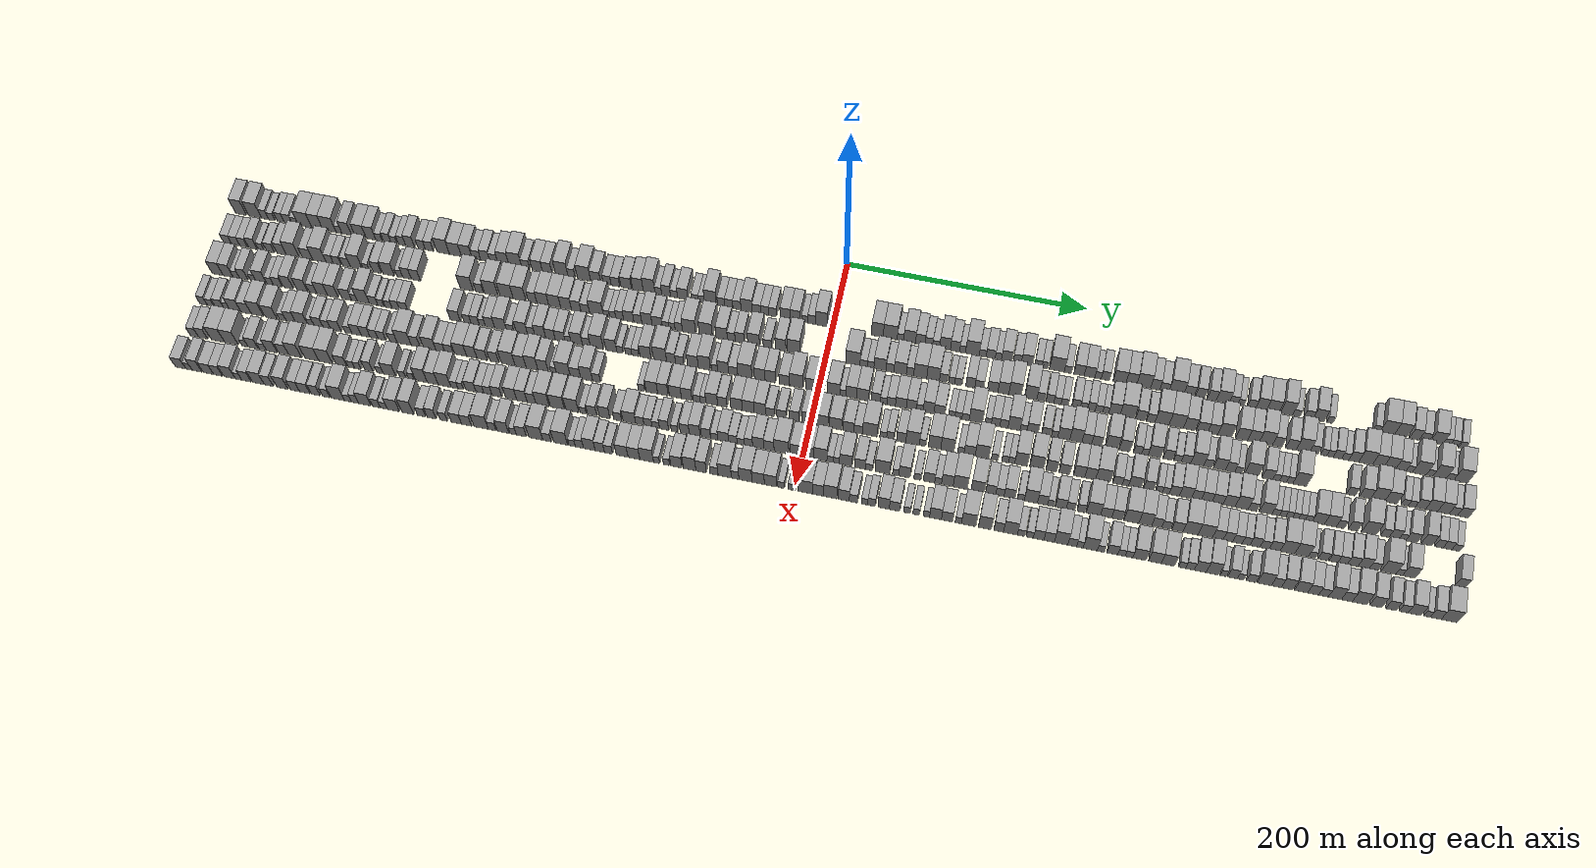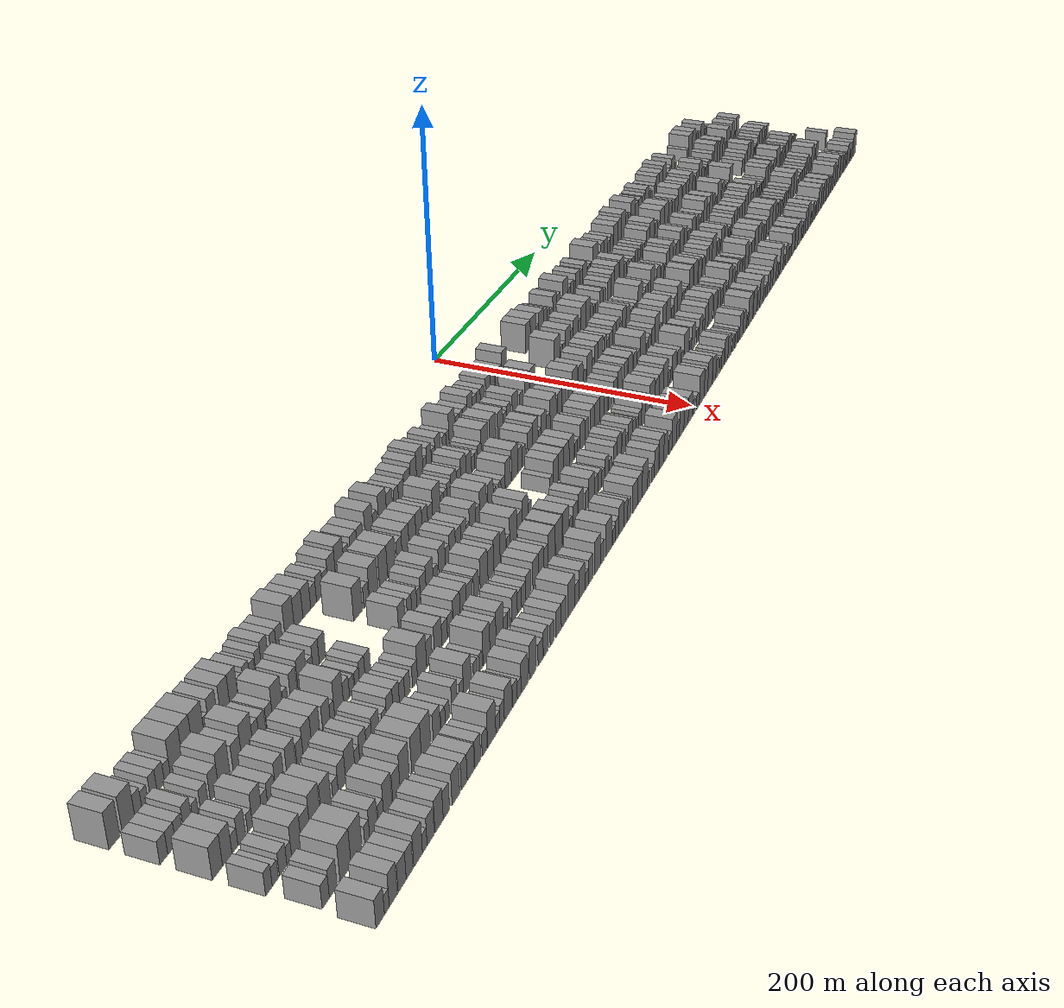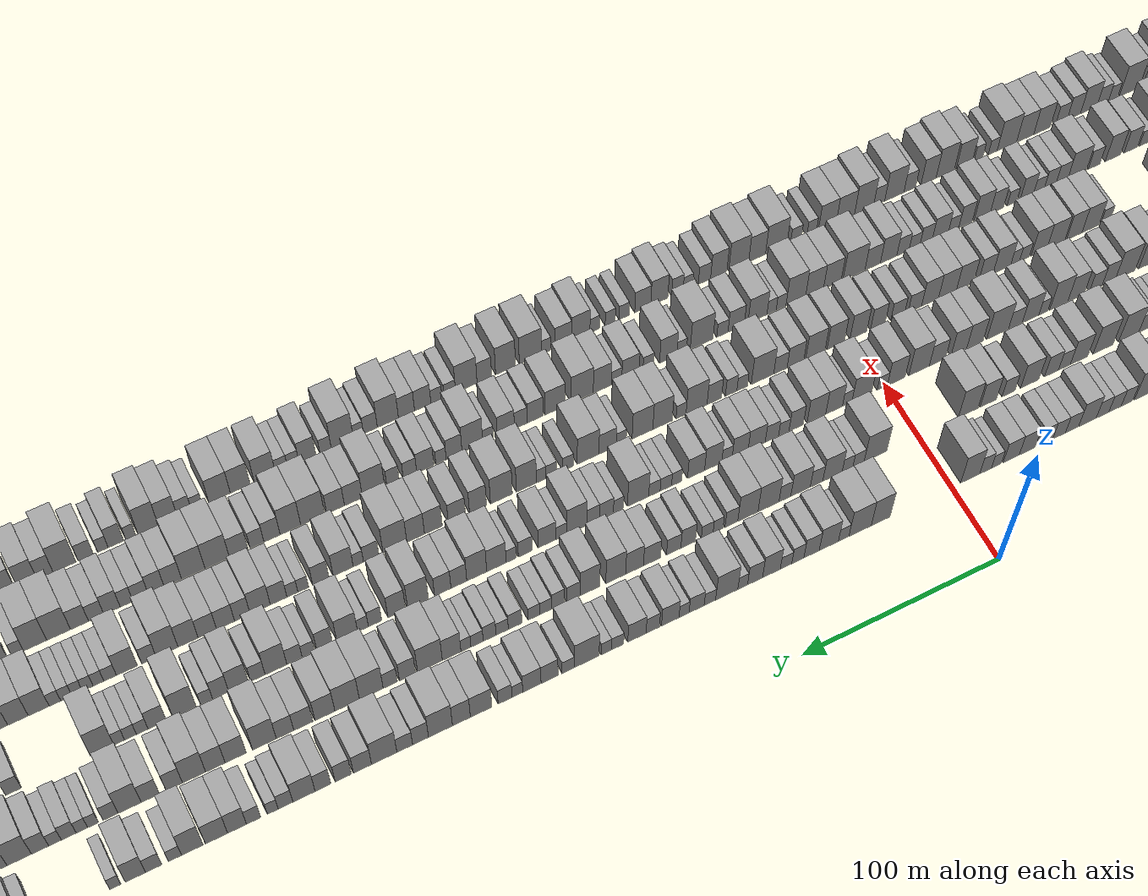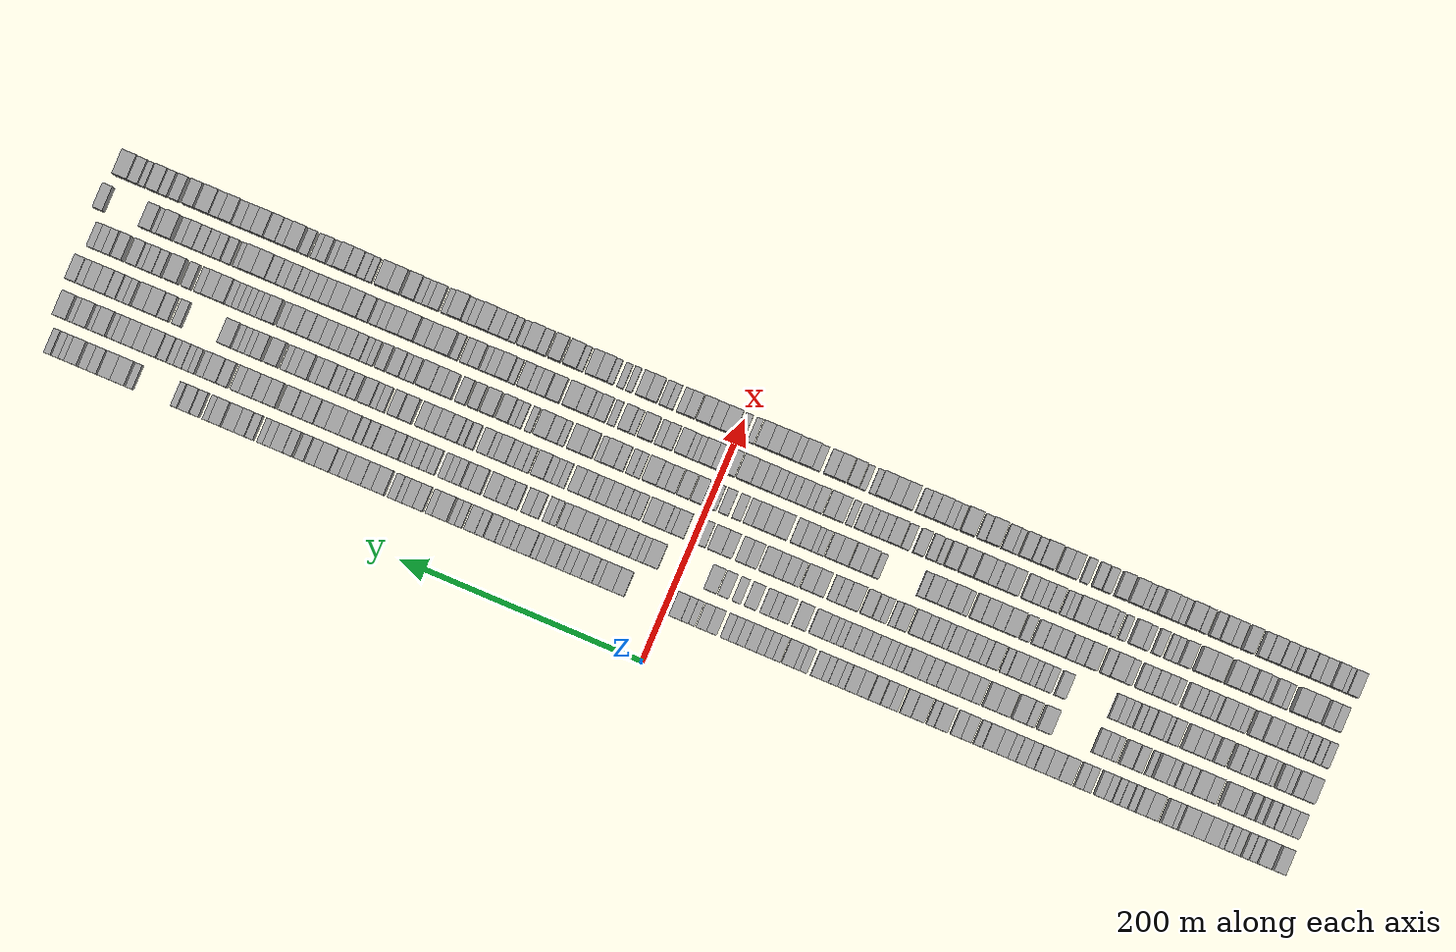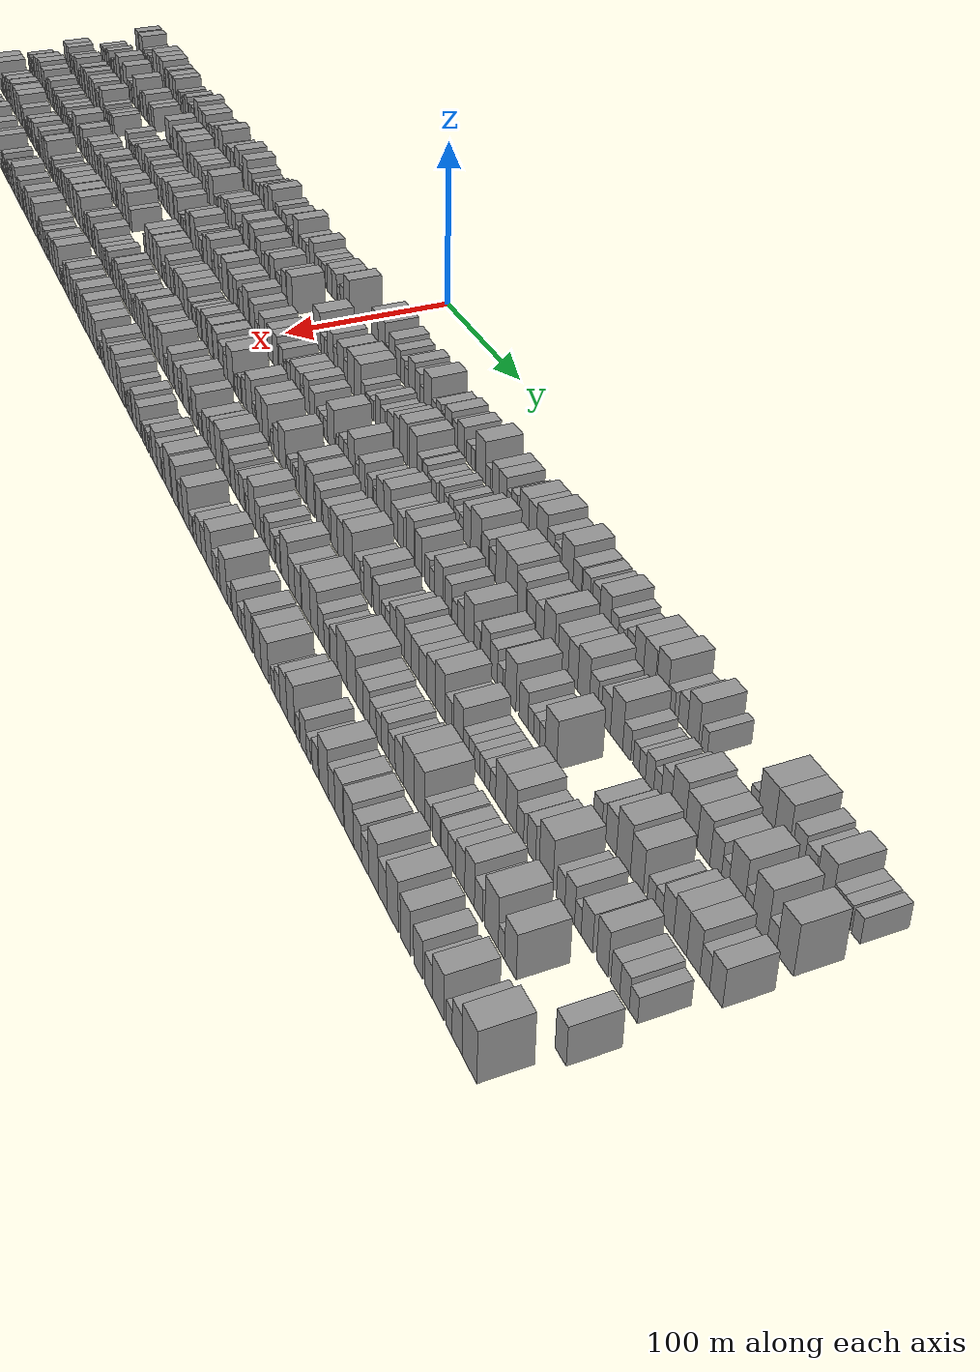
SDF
<sdf version="1.6">
 <world name="default">
  <scene>
   <sky><clouds><speed>12</speed></clouds></sky>
   <ambient>0.4 0.4 0.4 1</ambient>
   <background>0.7 0.7 0.7 1</background>
   <shadows>1</shadows>
  </scene>
  <gravity>0 0 -9.8066</gravity>
  <magnetic_field>6e-06 2.3e-05 -4.2e-05</magnetic_field>
  <physics default="0" name="default_physics" type="ode">
   <ode>
    <solver>
     <type>quick</type>
     <iters>10</iters>
     <sor>1.0</sor>
     <use_dynamic_moi_rescaling>0</use_dynamic_moi_rescaling>
    </solver>
    <constraints>
     <cfm>0</cfm>
     <erp>0.2</erp>
     <contact_max_correcting_vel>100</contact_max_correcting_vel>
     <contact_surface_layer>0.001</contact_surface_layer>
    </constraints>
   </ode>
   <max_step_size>0.004</max_step_size>
   <real_time_factor>1</real_time_factor>
   <real_time_update_rate>250</real_time_update_rate>
  </physics>
  <light name="sun" type="directional">
   <pose>0 0 10 0 0 0</pose>
   <diffuse>0.8 0.8 0.8 1</diffuse>
   <specular>0.2 0.2 0.2 1</specular>
   <attenuation>
    <range>1000</range>
    <constant>0.9</constant>
    <linear>0.01</linear>
    <quadratic>0.001</quadratic>
   </attenuation>
   <direction>-0.5 0.1 -0.9</direction>
  </light>
  <model name="building_1">
   <static>1</static>
   <pose>50.0000 -505.1824 0 0.000000 0.000000 0.000000</pose>
   <link name="link">
    <pose>0 0 12.00 0 0 0</pose>
    <collision name="collision"><geometry><box><size>20.0000 9.6352 24.0000</size></box></geometry></collision>
    <visual name="visual">
     <cast_shadows>0</cast_shadows>
     <geometry><box><size>20.0000 9.6352 24.0000</size></box></geometry>
     <material>
      <script>
       <uri>model://grey_wall/materials/scripts</uri>
       <uri>model://grey_wall/materials/textures</uri>
       <name>vrc/grey_wall</name>
      </script>
     </material>
    </visual>
   </link>
  </model>
  <model name="building_2">
   <static>1</static>
   <pose>50.0000 -492.7934 0 0.000000 0.000000 0.000000</pose>
   <link name="link">
    <pose>0 0 12.00 0 0 0</pose>
    <collision name="collision"><geometry><box><size>20.0000 11.1428 24.0000</size></box></geometry></collision>
    <visual name="visual">
     <cast_shadows>0</cast_shadows>
     <geometry><box><size>20.0000 11.1428 24.0000</size></box></geometry>
     <material>
      <script>
       <uri>model://grey_wall/materials/scripts</uri>
       <uri>model://grey_wall/materials/textures</uri>
       <name>vrc/grey_wall</name>
      </script>
     </material>
    </visual>
   </link>
  </model>
  <model name="building_3">
   <static>1</static>
   <pose>50.0000 -484.1004 0 0.000000 0.000000 0.000000</pose>
   <link name="link">
    <pose>0 0 7.50 0 0 0</pose>
    <collision name="collision"><geometry><box><size>20.0000 6.2432 15.0000</size></box></geometry></collision>
    <visual name="visual">
     <cast_shadows>0</cast_shadows>
     <geometry><box><size>20.0000 6.2432 15.0000</size></box></geometry>
     <material>
      <script>
       <uri>model://grey_wall/materials/scripts</uri>
       <uri>model://grey_wall/materials/textures</uri>
       <name>vrc/grey_wall</name>
      </script>
     </material>
    </visual>
   </link>
  </model>
  <model name="building_4">
   <static>1</static>
   <pose>50.0000 -478.1374 0 0.000000 0.000000 0.000000</pose>
   <link name="link">
    <pose>0 0 6.00 0 0 0</pose>
    <collision name="collision"><geometry><box><size>20.0000 5.6829 12.0000</size></box></geometry></collision>
    <visual name="visual">
     <cast_shadows>0</cast_shadows>
     <geometry><box><size>20.0000 5.6829 12.0000</size></box></geometry>
     <material>
      <script>
       <uri>model://grey_wall/materials/scripts</uri>
       <uri>model://grey_wall/materials/textures</uri>
       <name>vrc/grey_wall</name>
      </script>
     </material>
    </visual>
   </link>
  </model>
  <model name="building_5">
   <static>1</static>
   <pose>50.0000 -470.2839 0 0.000000 0.000000 0.000000</pose>
   <link name="link">
    <pose>0 0 7.50 0 0 0</pose>
    <collision name="collision"><geometry><box><size>20.0000 6.0241 15.0000</size></box></geometry></collision>
    <visual name="visual">
     <cast_shadows>0</cast_shadows>
     <geometry><box><size>20.0000 6.0241 15.0000</size></box></geometry>
     <material>
      <script>
       <uri>model://grey_wall/materials/scripts</uri>
       <uri>model://grey_wall/materials/textures</uri>
       <name>vrc/grey_wall</name>
      </script>
     </material>
    </visual>
   </link>
  </model>
  <model name="building_6">
   <static>1</static>
   <pose>50.0000 -463.8280 0 0.000000 0.000000 0.000000</pose>
   <link name="link">
    <pose>0 0 7.50 0 0 0</pose>
    <collision name="collision"><geometry><box><size>20.0000 6.8877 15.0000</size></box></geometry></collision>
    <visual name="visual">
     <cast_shadows>0</cast_shadows>
     <geometry><box><size>20.0000 6.8877 15.0000</size></box></geometry>
     <material>
      <script>
       <uri>model://grey_wall/materials/scripts</uri>
       <uri>model://grey_wall/materials/textures</uri>
       <name>vrc/grey_wall</name>
      </script>
     </material>
    </visual>
   </link>
  </model>
  <model name="building_7">
   <static>1</static>
   <pose>50.0000 -457.6014 0 0.000000 0.000000 0.000000</pose>
   <link name="link">
    <pose>0 0 6.00 0 0 0</pose>
    <collision name="collision"><geometry><box><size>20.0000 5.5657 12.0000</size></box></geometry></collision>
    <visual name="visual">
     <cast_shadows>0</cast_shadows>
     <geometry><box><size>20.0000 5.5657 12.0000</size></box></geometry>
     <material>
      <script>
       <uri>model://grey_wall/materials/scripts</uri>
       <uri>model://grey_wall/materials/textures</uri>
       <name>vrc/grey_wall</name>
      </script>
     </material>
    </visual>
   </link>
  </model>
  <model name="building_8">
   <static>1</static>
   <pose>50.0000 -449.0417 0 0.000000 0.000000 0.000000</pose>
   <link name="link">
    <pose>0 0 12.00 0 0 0</pose>
    <collision name="collision"><geometry><box><size>20.0000 11.5537 24.0000</size></box></geometry></collision>
    <visual name="visual">
     <cast_shadows>0</cast_shadows>
     <geometry><box><size>20.0000 11.5537 24.0000</size></box></geometry>
     <material>
      <script>
       <uri>model://grey_wall/materials/scripts</uri>
       <uri>model://grey_wall/materials/textures</uri>
       <name>vrc/grey_wall</name>
      </script>
     </material>
    </visual>
   </link>
  </model>
  <model name="building_9">
   <static>1</static>
   <pose>50.0000 -438.4060 0 0.000000 0.000000 0.000000</pose>
   <link name="link">
    <pose>0 0 12.00 0 0 0</pose>
    <collision name="collision"><geometry><box><size>20.0000 9.7178 24.0000</size></box></geometry></collision>
    <visual name="visual">
     <cast_shadows>0</cast_shadows>
     <geometry><box><size>20.0000 9.7178 24.0000</size></box></geometry>
     <material>
      <script>
       <uri>model://grey_wall/materials/scripts</uri>
       <uri>model://grey_wall/materials/textures</uri>
       <name>vrc/grey_wall</name>
      </script>
     </material>
    </visual>
   </link>
  </model>
  <model name="building_10">
   <static>1</static>
   <pose>50.0000 -427.7512 0 0.000000 0.000000 0.000000</pose>
   <link name="link">
    <pose>0 0 12.00 0 0 0</pose>
    <collision name="collision"><geometry><box><size>20.0000 11.5917 24.0000</size></box></geometry></collision>
    <visual name="visual">
     <cast_shadows>0</cast_shadows>
     <geometry><box><size>20.0000 11.5917 24.0000</size></box></geometry>
     <material>
      <script>
       <uri>model://grey_wall/materials/scripts</uri>
       <uri>model://grey_wall/materials/textures</uri>
       <name>vrc/grey_wall</name>
      </script>
     </material>
    </visual>
   </link>
  </model>
  <model name="building_11">
   <static>1</static>
   <pose>50.0000 -419.4948 0 0.000000 0.000000 0.000000</pose>
   <link name="link">
    <pose>0 0 6.00 0 0 0</pose>
    <collision name="collision"><geometry><box><size>20.0000 4.9211 12.0000</size></box></geometry></collision>
    <visual name="visual">
     <cast_shadows>0</cast_shadows>
     <geometry><box><size>20.0000 4.9211 12.0000</size></box></geometry>
     <material>
      <script>
       <uri>model://grey_wall/materials/scripts</uri>
       <uri>model://grey_wall/materials/textures</uri>
       <name>vrc/grey_wall</name>
      </script>
     </material>
    </visual>
   </link>
  </model>
  <model name="building_12">
   <static>1</static>
   <pose>50.0000 -412.7558 0 0.000000 0.000000 0.000000</pose>
   <link name="link">
    <pose>0 0 10.50 0 0 0</pose>
    <collision name="collision"><geometry><box><size>20.0000 8.5569 21.0000</size></box></geometry></collision>
    <visual name="visual">
     <cast_shadows>0</cast_shadows>
     <geometry><box><size>20.0000 8.5569 21.0000</size></box></geometry>
     <material>
      <script>
       <uri>model://grey_wall/materials/scripts</uri>
       <uri>model://grey_wall/materials/textures</uri>
       <name>vrc/grey_wall</name>
      </script>
     </material>
    </visual>
   </link>
  </model>
  <model name="building_13">
   <static>1</static>
   <pose>50.0000 -400.6687 0 0.000000 0.000000 0.000000</pose>
   <link name="link">
    <pose>0 0 10.50 0 0 0</pose>
    <collision name="collision"><geometry><box><size>20.0000 9.6172 21.0000</size></box></geometry></collision>
    <visual name="visual">
     <cast_shadows>0</cast_shadows>
     <geometry><box><size>20.0000 9.6172 21.0000</size></box></geometry>
     <material>
      <script>
       <uri>model://grey_wall/materials/scripts</uri>
       <uri>model://grey_wall/materials/textures</uri>
       <name>vrc/grey_wall</name>
      </script>
     </material>
    </visual>
   </link>
  </model>
  <model name="building_14">
   <static>1</static>
   <pose>50.0000 -391.6522 0 0.000000 0.000000 0.000000</pose>
   <link name="link">
    <pose>0 0 10.50 0 0 0</pose>
    <collision name="collision"><geometry><box><size>20.0000 8.4159 21.0000</size></box></geometry></collision>
    <visual name="visual">
     <cast_shadows>0</cast_shadows>
     <geometry><box><size>20.0000 8.4159 21.0000</size></box></geometry>
     <material>
      <script>
       <uri>model://grey_wall/materials/scripts</uri>
       <uri>model://grey_wall/materials/textures</uri>
       <name>vrc/grey_wall</name>
      </script>
     </material>
    </visual>
   </link>
  </model>
  <model name="building_15">
   <static>1</static>
   <pose>50.0000 -384.7010 0 0.000000 0.000000 0.000000</pose>
   <link name="link">
    <pose>0 0 6.00 0 0 0</pose>
    <collision name="collision"><geometry><box><size>20.0000 5.4865 12.0000</size></box></geometry></collision>
    <visual name="visual">
     <cast_shadows>0</cast_shadows>
     <geometry><box><size>20.0000 5.4865 12.0000</size></box></geometry>
     <material>
      <script>
       <uri>model://grey_wall/materials/scripts</uri>
       <uri>model://grey_wall/materials/textures</uri>
       <name>vrc/grey_wall</name>
      </script>
     </material>
    </visual>
   </link>
  </model>
  <model name="building_16">
   <static>1</static>
   <pose>50.0000 -377.6718 0 0.000000 0.000000 0.000000</pose>
   <link name="link">
    <pose>0 0 7.50 0 0 0</pose>
    <collision name="collision"><geometry><box><size>20.0000 6.5717 15.0000</size></box></geometry></collision>
    <visual name="visual">
     <cast_shadows>0</cast_shadows>
     <geometry><box><size>20.0000 6.5717 15.0000</size></box></geometry>
     <material>
      <script>
       <uri>model://grey_wall/materials/scripts</uri>
       <uri>model://grey_wall/materials/textures</uri>
       <name>vrc/grey_wall</name>
      </script>
     </material>
    </visual>
   </link>
  </model>
  <model name="building_17">
   <static>1</static>
   <pose>50.0000 -371.6435 0 0.000000 0.000000 0.000000</pose>
   <link name="link">
    <pose>0 0 6.00 0 0 0</pose>
    <collision name="collision"><geometry><box><size>20.0000 5.4849 12.0000</size></box></geometry></collision>
    <visual name="visual">
     <cast_shadows>0</cast_shadows>
     <geometry><box><size>20.0000 5.4849 12.0000</size></box></geometry>
     <material>
      <script>
       <uri>model://grey_wall/materials/scripts</uri>
       <uri>model://grey_wall/materials/textures</uri>
       <name>vrc/grey_wall</name>
      </script>
     </material>
    </visual>
   </link>
  </model>
  <model name="building_18">
   <static>1</static>
   <pose>50.0000 -364.8163 0 0.000000 0.000000 0.000000</pose>
   <link name="link">
    <pose>0 0 7.50 0 0 0</pose>
    <collision name="collision"><geometry><box><size>20.0000 6.1695 15.0000</size></box></geometry></collision>
    <visual name="visual">
     <cast_shadows>0</cast_shadows>
     <geometry><box><size>20.0000 6.1695 15.0000</size></box></geometry>
     <material>
      <script>
       <uri>model://grey_wall/materials/scripts</uri>
       <uri>model://grey_wall/materials/textures</uri>
       <name>vrc/grey_wall</name>
      </script>
     </material>
    </visual>
   </link>
  </model>
  <model name="building_19">
   <static>1</static>
   <pose>50.0000 -357.8892 0 0.000000 0.000000 0.000000</pose>
   <link name="link">
    <pose>0 0 9.00 0 0 0</pose>
    <collision name="collision"><geometry><box><size>20.0000 7.6846 18.0000</size></box></geometry></collision>
    <visual name="visual">
     <cast_shadows>0</cast_shadows>
     <geometry><box><size>20.0000 7.6846 18.0000</size></box></geometry>
     <material>
      <script>
       <uri>model://grey_wall/materials/scripts</uri>
       <uri>model://grey_wall/materials/textures</uri>
       <name>vrc/grey_wall</name>
      </script>
     </material>
    </visual>
   </link>
  </model>
  <model name="building_20">
   <static>1</static>
   <pose>50.0000 -347.9178 0 0.000000 0.000000 0.000000</pose>
   <link name="link">
    <pose>0 0 7.50 0 0 0</pose>
    <collision name="collision"><geometry><box><size>20.0000 6.2582 15.0000</size></box></geometry></collision>
    <visual name="visual">
     <cast_shadows>0</cast_shadows>
     <geometry><box><size>20.0000 6.2582 15.0000</size></box></geometry>
     <material>
      <script>
       <uri>model://grey_wall/materials/scripts</uri>
       <uri>model://grey_wall/materials/textures</uri>
       <name>vrc/grey_wall</name>
      </script>
     </material>
    </visual>
   </link>
  </model>
  <model name="building_21">
   <static>1</static>
   <pose>50.0000 -341.2907 0 0.000000 0.000000 0.000000</pose>
   <link name="link">
    <pose>0 0 7.50 0 0 0</pose>
    <collision name="collision"><geometry><box><size>20.0000 6.9960 15.0000</size></box></geometry></collision>
    <visual name="visual">
     <cast_shadows>0</cast_shadows>
     <geometry><box><size>20.0000 6.9960 15.0000</size></box></geometry>
     <material>
      <script>
       <uri>model://grey_wall/materials/scripts</uri>
       <uri>model://grey_wall/materials/textures</uri>
       <name>vrc/grey_wall</name>
      </script>
     </material>
    </visual>
   </link>
  </model>
  <model name="building_22">
   <static>1</static>
   <pose>50.0000 -329.3862 0 0.000000 0.000000 0.000000</pose>
   <link name="link">
    <pose>0 0 12.00 0 0 0</pose>
    <collision name="collision"><geometry><box><size>20.0000 10.8130 24.0000</size></box></geometry></collision>
    <visual name="visual">
     <cast_shadows>0</cast_shadows>
     <geometry><box><size>20.0000 10.8130 24.0000</size></box></geometry>
     <material>
      <script>
       <uri>model://grey_wall/materials/scripts</uri>
       <uri>model://grey_wall/materials/textures</uri>
       <name>vrc/grey_wall</name>
      </script>
     </material>
    </visual>
   </link>
  </model>
  <model name="building_23">
   <static>1</static>
   <pose>50.0000 -318.8442 0 0.000000 0.000000 0.000000</pose>
   <link name="link">
    <pose>0 0 10.50 0 0 0</pose>
    <collision name="collision"><geometry><box><size>20.0000 10.2711 21.0000</size></box></geometry></collision>
    <visual name="visual">
     <cast_shadows>0</cast_shadows>
     <geometry><box><size>20.0000 10.2711 21.0000</size></box></geometry>
     <material>
      <script>
       <uri>model://grey_wall/materials/scripts</uri>
       <uri>model://grey_wall/materials/textures</uri>
       <name>vrc/grey_wall</name>
      </script>
     </material>
    </visual>
   </link>
  </model>
  <model name="building_24">
   <static>1</static>
   <pose>50.0000 -308.9959 0 0.000000 0.000000 0.000000</pose>
   <link name="link">
    <pose>0 0 10.50 0 0 0</pose>
    <collision name="collision"><geometry><box><size>20.0000 9.4255 21.0000</size></box></geometry></collision>
    <visual name="visual">
     <cast_shadows>0</cast_shadows>
     <geometry><box><size>20.0000 9.4255 21.0000</size></box></geometry>
     <material>
      <script>
       <uri>model://grey_wall/materials/scripts</uri>
       <uri>model://grey_wall/materials/textures</uri>
       <name>vrc/grey_wall</name>
      </script>
     </material>
    </visual>
   </link>
  </model>
  <model name="building_25">
   <static>1</static>
   <pose>50.0000 -300.6534 0 0.000000 0.000000 0.000000</pose>
   <link name="link">
    <pose>0 0 7.50 0 0 0</pose>
    <collision name="collision"><geometry><box><size>20.0000 7.2595 15.0000</size></box></geometry></collision>
    <visual name="visual">
     <cast_shadows>0</cast_shadows>
     <geometry><box><size>20.0000 7.2595 15.0000</size></box></geometry>
     <material>
      <script>
       <uri>model://grey_wall/materials/scripts</uri>
       <uri>model://grey_wall/materials/textures</uri>
       <name>vrc/grey_wall</name>
      </script>
     </material>
    </visual>
   </link>
  </model>
  <model name="building_26">
   <static>1</static>
   <pose>50.0000 -293.0903 0 0.000000 0.000000 0.000000</pose>
   <link name="link">
    <pose>0 0 9.00 0 0 0</pose>
    <collision name="collision"><geometry><box><size>20.0000 7.8667 18.0000</size></box></geometry></collision>
    <visual name="visual">
     <cast_shadows>0</cast_shadows>
     <geometry><box><size>20.0000 7.8667 18.0000</size></box></geometry>
     <material>
      <script>
       <uri>model://grey_wall/materials/scripts</uri>
       <uri>model://grey_wall/materials/textures</uri>
       <name>vrc/grey_wall</name>
      </script>
     </material>
    </visual>
   </link>
  </model>
  <model name="building_27">
   <static>1</static>
   <pose>50.0000 -285.7078 0 0.000000 0.000000 0.000000</pose>
   <link name="link">
    <pose>0 0 7.50 0 0 0</pose>
    <collision name="collision"><geometry><box><size>20.0000 6.8984 15.0000</size></box></geometry></collision>
    <visual name="visual">
     <cast_shadows>0</cast_shadows>
     <geometry><box><size>20.0000 6.8984 15.0000</size></box></geometry>
     <material>
      <script>
       <uri>model://grey_wall/materials/scripts</uri>
       <uri>model://grey_wall/materials/textures</uri>
       <name>vrc/grey_wall</name>
      </script>
     </material>
    </visual>
   </link>
  </model>
  <model name="building_28">
   <static>1</static>
   <pose>50.0000 -277.4978 0 0.000000 0.000000 0.000000</pose>
   <link name="link">
    <pose>0 0 10.50 0 0 0</pose>
    <collision name="collision"><geometry><box><size>20.0000 9.5215 21.0000</size></box></geometry></collision>
    <visual name="visual">
     <cast_shadows>0</cast_shadows>
     <geometry><box><size>20.0000 9.5215 21.0000</size></box></geometry>
     <material>
      <script>
       <uri>model://grey_wall/materials/scripts</uri>
       <uri>model://grey_wall/materials/textures</uri>
       <name>vrc/grey_wall</name>
      </script>
     </material>
    </visual>
   </link>
  </model>
  <model name="building_29">
   <static>1</static>
   <pose>50.0000 -267.2478 0 0.000000 0.000000 0.000000</pose>
   <link name="link">
    <pose>0 0 12.00 0 0 0</pose>
    <collision name="collision"><geometry><box><size>20.0000 10.9785 24.0000</size></box></geometry></collision>
    <visual name="visual">
     <cast_shadows>0</cast_shadows>
     <geometry><box><size>20.0000 10.9785 24.0000</size></box></geometry>
     <material>
      <script>
       <uri>model://grey_wall/materials/scripts</uri>
       <uri>model://grey_wall/materials/textures</uri>
       <name>vrc/grey_wall</name>
      </script>
     </material>
    </visual>
   </link>
  </model>
  <model name="building_30">
   <static>1</static>
   <pose>50.0000 -258.3885 0 0.000000 0.000000 0.000000</pose>
   <link name="link">
    <pose>0 0 7.50 0 0 0</pose>
    <collision name="collision"><geometry><box><size>20.0000 6.7401 15.0000</size></box></geometry></collision>
    <visual name="visual">
     <cast_shadows>0</cast_shadows>
     <geometry><box><size>20.0000 6.7401 15.0000</size></box></geometry>
     <material>
      <script>
       <uri>model://grey_wall/materials/scripts</uri>
       <uri>model://grey_wall/materials/textures</uri>
       <name>vrc/grey_wall</name>
      </script>
     </material>
    </visual>
   </link>
  </model>
  <model name="building_31">
   <static>1</static>
   <pose>50.0000 -248.5982 0 0.000000 0.000000 0.000000</pose>
   <link name="link">
    <pose>0 0 9.00 0 0 0</pose>
    <collision name="collision"><geometry><box><size>20.0000 8.8404 18.0000</size></box></geometry></collision>
    <visual name="visual">
     <cast_shadows>0</cast_shadows>
     <geometry><box><size>20.0000 8.8404 18.0000</size></box></geometry>
     <material>
      <script>
       <uri>model://grey_wall/materials/scripts</uri>
       <uri>model://grey_wall/materials/textures</uri>
       <name>vrc/grey_wall</name>
      </script>
     </material>
    </visual>
   </link>
  </model>
  <model name="building_32">
   <static>1</static>
   <pose>50.0000 -240.0793 0 0.000000 0.000000 0.000000</pose>
   <link name="link">
    <pose>0 0 9.00 0 0 0</pose>
    <collision name="collision"><geometry><box><size>20.0000 8.1975 18.0000</size></box></geometry></collision>
    <visual name="visual">
     <cast_shadows>0</cast_shadows>
     <geometry><box><size>20.0000 8.1975 18.0000</size></box></geometry>
     <material>
      <script>
       <uri>model://grey_wall/materials/scripts</uri>
       <uri>model://grey_wall/materials/textures</uri>
       <name>vrc/grey_wall</name>
      </script>
     </material>
    </visual>
   </link>
  </model>
  <model name="building_33">
   <static>1</static>
   <pose>50.0000 -227.6238 0 0.000000 0.000000 0.000000</pose>
   <link name="link">
    <pose>0 0 12.00 0 0 0</pose>
    <collision name="collision"><geometry><box><size>20.0000 10.7134 24.0000</size></box></geometry></collision>
    <visual name="visual">
     <cast_shadows>0</cast_shadows>
     <geometry><box><size>20.0000 10.7134 24.0000</size></box></geometry>
     <material>
      <script>
       <uri>model://grey_wall/materials/scripts</uri>
       <uri>model://grey_wall/materials/textures</uri>
       <name>vrc/grey_wall</name>
      </script>
     </material>
    </visual>
   </link>
  </model>
  <model name="building_34">
   <static>1</static>
   <pose>50.0000 -219.2456 0 0.000000 0.000000 0.000000</pose>
   <link name="link">
    <pose>0 0 7.50 0 0 0</pose>
    <collision name="collision"><geometry><box><size>20.0000 6.0430 15.0000</size></box></geometry></collision>
    <visual name="visual">
     <cast_shadows>0</cast_shadows>
     <geometry><box><size>20.0000 6.0430 15.0000</size></box></geometry>
     <material>
      <script>
       <uri>model://grey_wall/materials/scripts</uri>
       <uri>model://grey_wall/materials/textures</uri>
       <name>vrc/grey_wall</name>
      </script>
     </material>
    </visual>
   </link>
  </model>
  <model name="building_35">
   <static>1</static>
   <pose>50.0000 -208.6701 0 0.000000 0.000000 0.000000</pose>
   <link name="link">
    <pose>0 0 12.00 0 0 0</pose>
    <collision name="collision"><geometry><box><size>20.0000 11.1080 24.0000</size></box></geometry></collision>
    <visual name="visual">
     <cast_shadows>0</cast_shadows>
     <geometry><box><size>20.0000 11.1080 24.0000</size></box></geometry>
     <material>
      <script>
       <uri>model://grey_wall/materials/scripts</uri>
       <uri>model://grey_wall/materials/textures</uri>
       <name>vrc/grey_wall</name>
      </script>
     </material>
    </visual>
   </link>
  </model>
  <model name="building_36">
   <static>1</static>
   <pose>50.0000 -198.7838 0 0.000000 0.000000 0.000000</pose>
   <link name="link">
    <pose>0 0 9.00 0 0 0</pose>
    <collision name="collision"><geometry><box><size>20.0000 8.6646 18.0000</size></box></geometry></collision>
    <visual name="visual">
     <cast_shadows>0</cast_shadows>
     <geometry><box><size>20.0000 8.6646 18.0000</size></box></geometry>
     <material>
      <script>
       <uri>model://grey_wall/materials/scripts</uri>
       <uri>model://grey_wall/materials/textures</uri>
       <name>vrc/grey_wall</name>
      </script>
     </material>
    </visual>
   </link>
  </model>
  <model name="building_37">
   <static>1</static>
   <pose>50.0000 -189.0861 0 0.000000 0.000000 0.000000</pose>
   <link name="link">
    <pose>0 0 7.50 0 0 0</pose>
    <collision name="collision"><geometry><box><size>20.0000 6.7308 15.0000</size></box></geometry></collision>
    <visual name="visual">
     <cast_shadows>0</cast_shadows>
     <geometry><box><size>20.0000 6.7308 15.0000</size></box></geometry>
     <material>
      <script>
       <uri>model://grey_wall/materials/scripts</uri>
       <uri>model://grey_wall/materials/textures</uri>
       <name>vrc/grey_wall</name>
      </script>
     </material>
    </visual>
   </link>
  </model>
  <model name="building_38">
   <static>1</static>
   <pose>50.0000 -182.0911 0 0.000000 0.000000 0.000000</pose>
   <link name="link">
    <pose>0 0 7.50 0 0 0</pose>
    <collision name="collision"><geometry><box><size>20.0000 7.2593 15.0000</size></box></geometry></collision>
    <visual name="visual">
     <cast_shadows>0</cast_shadows>
     <geometry><box><size>20.0000 7.2593 15.0000</size></box></geometry>
     <material>
      <script>
       <uri>model://grey_wall/materials/scripts</uri>
       <uri>model://grey_wall/materials/textures</uri>
       <name>vrc/grey_wall</name>
      </script>
     </material>
    </visual>
   </link>
  </model>
  <model name="building_39">
   <static>1</static>
   <pose>50.0000 -173.0492 0 0.000000 0.000000 0.000000</pose>
   <link name="link">
    <pose>0 0 9.00 0 0 0</pose>
    <collision name="collision"><geometry><box><size>20.0000 8.8244 18.0000</size></box></geometry></collision>
    <visual name="visual">
     <cast_shadows>0</cast_shadows>
     <geometry><box><size>20.0000 8.8244 18.0000</size></box></geometry>
     <material>
      <script>
       <uri>model://grey_wall/materials/scripts</uri>
       <uri>model://grey_wall/materials/textures</uri>
       <name>vrc/grey_wall</name>
      </script>
     </material>
    </visual>
   </link>
  </model>
  <model name="building_40">
   <static>1</static>
   <pose>50.0000 -163.0983 0 0.000000 0.000000 0.000000</pose>
   <link name="link">
    <pose>0 0 10.50 0 0 0</pose>
    <collision name="collision"><geometry><box><size>20.0000 9.0775 21.0000</size></box></geometry></collision>
    <visual name="visual">
     <cast_shadows>0</cast_shadows>
     <geometry><box><size>20.0000 9.0775 21.0000</size></box></geometry>
     <material>
      <script>
       <uri>model://grey_wall/materials/scripts</uri>
       <uri>model://grey_wall/materials/textures</uri>
       <name>vrc/grey_wall</name>
      </script>
     </material>
    </visual>
   </link>
  </model>
  <model name="building_41">
   <static>1</static>
   <pose>50.0000 -153.6239 0 0.000000 0.000000 0.000000</pose>
   <link name="link">
    <pose>0 0 12.00 0 0 0</pose>
    <collision name="collision"><geometry><box><size>20.0000 9.8713 24.0000</size></box></geometry></collision>
    <visual name="visual">
     <cast_shadows>0</cast_shadows>
     <geometry><box><size>20.0000 9.8713 24.0000</size></box></geometry>
     <material>
      <script>
       <uri>model://grey_wall/materials/scripts</uri>
       <uri>model://grey_wall/materials/textures</uri>
       <name>vrc/grey_wall</name>
      </script>
     </material>
    </visual>
   </link>
  </model>
  <model name="building_42">
   <static>1</static>
   <pose>50.0000 -145.8374 0 0.000000 0.000000 0.000000</pose>
   <link name="link">
    <pose>0 0 6.00 0 0 0</pose>
    <collision name="collision"><geometry><box><size>20.0000 5.7016 12.0000</size></box></geometry></collision>
    <visual name="visual">
     <cast_shadows>0</cast_shadows>
     <geometry><box><size>20.0000 5.7016 12.0000</size></box></geometry>
     <material>
      <script>
       <uri>model://grey_wall/materials/scripts</uri>
       <uri>model://grey_wall/materials/textures</uri>
       <name>vrc/grey_wall</name>
      </script>
     </material>
    </visual>
   </link>
  </model>
  <model name="building_43">
   <static>1</static>
   <pose>50.0000 -139.2914 0 0.000000 0.000000 0.000000</pose>
   <link name="link">
    <pose>0 0 9.00 0 0 0</pose>
    <collision name="collision"><geometry><box><size>20.0000 7.3903 18.0000</size></box></geometry></collision>
    <visual name="visual">
     <cast_shadows>0</cast_shadows>
     <geometry><box><size>20.0000 7.3903 18.0000</size></box></geometry>
     <material>
      <script>
       <uri>model://grey_wall/materials/scripts</uri>
       <uri>model://grey_wall/materials/textures</uri>
       <name>vrc/grey_wall</name>
      </script>
     </material>
    </visual>
   </link>
  </model>
  <model name="building_44">
   <static>1</static>
   <pose>50.0000 -132.6653 0 0.000000 0.000000 0.000000</pose>
   <link name="link">
    <pose>0 0 6.00 0 0 0</pose>
    <collision name="collision"><geometry><box><size>20.0000 5.8619 12.0000</size></box></geometry></collision>
    <visual name="visual">
     <cast_shadows>0</cast_shadows>
     <geometry><box><size>20.0000 5.8619 12.0000</size></box></geometry>
     <material>
      <script>
       <uri>model://grey_wall/materials/scripts</uri>
       <uri>model://grey_wall/materials/textures</uri>
       <name>vrc/grey_wall</name>
      </script>
     </material>
    </visual>
   </link>
  </model>
  <model name="building_45">
   <static>1</static>
   <pose>50.0000 -125.3735 0 0.000000 0.000000 0.000000</pose>
   <link name="link">
    <pose>0 0 9.00 0 0 0</pose>
    <collision name="collision"><geometry><box><size>20.0000 8.7218 18.0000</size></box></geometry></collision>
    <visual name="visual">
     <cast_shadows>0</cast_shadows>
     <geometry><box><size>20.0000 8.7218 18.0000</size></box></geometry>
     <material>
      <script>
       <uri>model://grey_wall/materials/scripts</uri>
       <uri>model://grey_wall/materials/textures</uri>
       <name>vrc/grey_wall</name>
      </script>
     </material>
    </visual>
   </link>
  </model>
  <model name="building_46">
   <static>1</static>
   <pose>50.0000 -115.0211 0 0.000000 0.000000 0.000000</pose>
   <link name="link">
    <pose>0 0 6.00 0 0 0</pose>
    <collision name="collision"><geometry><box><size>20.0000 5.9830 12.0000</size></box></geometry></collision>
    <visual name="visual">
     <cast_shadows>0</cast_shadows>
     <geometry><box><size>20.0000 5.9830 12.0000</size></box></geometry>
     <material>
      <script>
       <uri>model://grey_wall/materials/scripts</uri>
       <uri>model://grey_wall/materials/textures</uri>
       <name>vrc/grey_wall</name>
      </script>
     </material>
    </visual>
   </link>
  </model>
  <model name="building_47">
   <static>1</static>
   <pose>50.0000 -109.5095 0 0.000000 0.000000 0.000000</pose>
   <link name="link">
    <pose>0 0 6.00 0 0 0</pose>
    <collision name="collision"><geometry><box><size>20.0000 5.0402 12.0000</size></box></geometry></collision>
    <visual name="visual">
     <cast_shadows>0</cast_shadows>
     <geometry><box><size>20.0000 5.0402 12.0000</size></box></geometry>
     <material>
      <script>
       <uri>model://grey_wall/materials/scripts</uri>
       <uri>model://grey_wall/materials/textures</uri>
       <name>vrc/grey_wall</name>
      </script>
     </material>
    </visual>
   </link>
  </model>
  <model name="building_48">
   <static>1</static>
   <pose>50.0000 -102.0302 0 0.000000 0.000000 0.000000</pose>
   <link name="link">
    <pose>0 0 12.00 0 0 0</pose>
    <collision name="collision"><geometry><box><size>20.0000 9.9185 24.0000</size></box></geometry></collision>
    <visual name="visual">
     <cast_shadows>0</cast_shadows>
     <geometry><box><size>20.0000 9.9185 24.0000</size></box></geometry>
     <material>
      <script>
       <uri>model://grey_wall/materials/scripts</uri>
       <uri>model://grey_wall/materials/textures</uri>
       <name>vrc/grey_wall</name>
      </script>
     </material>
    </visual>
   </link>
  </model>
  <model name="building_49">
   <static>1</static>
   <pose>50.0000 -92.9644 0 0.000000 0.000000 0.000000</pose>
   <link name="link">
    <pose>0 0 7.50 0 0 0</pose>
    <collision name="collision"><geometry><box><size>20.0000 6.2132 15.0000</size></box></geometry></collision>
    <visual name="visual">
     <cast_shadows>0</cast_shadows>
     <geometry><box><size>20.0000 6.2132 15.0000</size></box></geometry>
     <material>
      <script>
       <uri>model://grey_wall/materials/scripts</uri>
       <uri>model://grey_wall/materials/textures</uri>
       <name>vrc/grey_wall</name>
      </script>
     </material>
    </visual>
   </link>
  </model>
  <model name="building_50">
   <static>1</static>
   <pose>50.0000 -86.5082 0 0.000000 0.000000 0.000000</pose>
   <link name="link">
    <pose>0 0 7.50 0 0 0</pose>
    <collision name="collision"><geometry><box><size>20.0000 6.6991 15.0000</size></box></geometry></collision>
    <visual name="visual">
     <cast_shadows>0</cast_shadows>
     <geometry><box><size>20.0000 6.6991 15.0000</size></box></geometry>
     <material>
      <script>
       <uri>model://grey_wall/materials/scripts</uri>
       <uri>model://grey_wall/materials/textures</uri>
       <name>vrc/grey_wall</name>
      </script>
     </material>
    </visual>
   </link>
  </model>
  <model name="building_51">
   <static>1</static>
   <pose>50.0000 -79.7621 0 0.000000 0.000000 0.000000</pose>
   <link name="link">
    <pose>0 0 7.50 0 0 0</pose>
    <collision name="collision"><geometry><box><size>20.0000 6.7931 15.0000</size></box></geometry></collision>
    <visual name="visual">
     <cast_shadows>0</cast_shadows>
     <geometry><box><size>20.0000 6.7931 15.0000</size></box></geometry>
     <material>
      <script>
       <uri>model://grey_wall/materials/scripts</uri>
       <uri>model://grey_wall/materials/textures</uri>
       <name>vrc/grey_wall</name>
      </script>
     </material>
    </visual>
   </link>
  </model>
  <model name="building_52">
   <static>1</static>
   <pose>50.0000 -71.6376 0 0.000000 0.000000 0.000000</pose>
   <link name="link">
    <pose>0 0 10.50 0 0 0</pose>
    <collision name="collision"><geometry><box><size>20.0000 9.4559 21.0000</size></box></geometry></collision>
    <visual name="visual">
     <cast_shadows>0</cast_shadows>
     <geometry><box><size>20.0000 9.4559 21.0000</size></box></geometry>
     <material>
      <script>
       <uri>model://grey_wall/materials/scripts</uri>
       <uri>model://grey_wall/materials/textures</uri>
       <name>vrc/grey_wall</name>
      </script>
     </material>
    </visual>
   </link>
  </model>
  <model name="building_53">
   <static>1</static>
   <pose>50.0000 -63.3880 0 0.000000 0.000000 0.000000</pose>
   <link name="link">
    <pose>0 0 7.50 0 0 0</pose>
    <collision name="collision"><geometry><box><size>20.0000 7.0434 15.0000</size></box></geometry></collision>
    <visual name="visual">
     <cast_shadows>0</cast_shadows>
     <geometry><box><size>20.0000 7.0434 15.0000</size></box></geometry>
     <material>
      <script>
       <uri>model://grey_wall/materials/scripts</uri>
       <uri>model://grey_wall/materials/textures</uri>
       <name>vrc/grey_wall</name>
      </script>
     </material>
    </visual>
   </link>
  </model>
  <model name="building_54">
   <static>1</static>
   <pose>50.0000 -56.5029 0 0.000000 0.000000 0.000000</pose>
   <link name="link">
    <pose>0 0 7.50 0 0 0</pose>
    <collision name="collision"><geometry><box><size>20.0000 6.7269 15.0000</size></box></geometry></collision>
    <visual name="visual">
     <cast_shadows>0</cast_shadows>
     <geometry><box><size>20.0000 6.7269 15.0000</size></box></geometry>
     <material>
      <script>
       <uri>model://grey_wall/materials/scripts</uri>
       <uri>model://grey_wall/materials/textures</uri>
       <name>vrc/grey_wall</name>
      </script>
     </material>
    </visual>
   </link>
  </model>
  <model name="building_55">
   <static>1</static>
   <pose>50.0000 -49.9407 0 0.000000 0.000000 0.000000</pose>
   <link name="link">
    <pose>0 0 7.50 0 0 0</pose>
    <collision name="collision"><geometry><box><size>20.0000 6.3974 15.0000</size></box></geometry></collision>
    <visual name="visual">
     <cast_shadows>0</cast_shadows>
     <geometry><box><size>20.0000 6.3974 15.0000</size></box></geometry>
     <material>
      <script>
       <uri>model://grey_wall/materials/scripts</uri>
       <uri>model://grey_wall/materials/textures</uri>
       <name>vrc/grey_wall</name>
      </script>
     </material>
    </visual>
   </link>
  </model>
  <model name="building_56">
   <static>1</static>
   <pose>50.0000 -39.5400 0 0.000000 0.000000 0.000000</pose>
   <link name="link">
    <pose>0 0 9.00 0 0 0</pose>
    <collision name="collision"><geometry><box><size>20.0000 8.4040 18.0000</size></box></geometry></collision>
    <visual name="visual">
     <cast_shadows>0</cast_shadows>
     <geometry><box><size>20.0000 8.4040 18.0000</size></box></geometry>
     <material>
      <script>
       <uri>model://grey_wall/materials/scripts</uri>
       <uri>model://grey_wall/materials/textures</uri>
       <name>vrc/grey_wall</name>
      </script>
     </material>
    </visual>
   </link>
  </model>
  <model name="building_57">
   <static>1</static>
   <pose>50.0000 -31.1024 0 0.000000 0.000000 0.000000</pose>
   <link name="link">
    <pose>0 0 9.00 0 0 0</pose>
    <collision name="collision"><geometry><box><size>20.0000 8.4711 18.0000</size></box></geometry></collision>
    <visual name="visual">
     <cast_shadows>0</cast_shadows>
     <geometry><box><size>20.0000 8.4711 18.0000</size></box></geometry>
     <material>
      <script>
       <uri>model://grey_wall/materials/scripts</uri>
       <uri>model://grey_wall/materials/textures</uri>
       <name>vrc/grey_wall</name>
      </script>
     </material>
    </visual>
   </link>
  </model>
  <model name="building_58">
   <static>1</static>
   <pose>50.0000 -23.2524 0 0.000000 0.000000 0.000000</pose>
   <link name="link">
    <pose>0 0 6.00 0 0 0</pose>
    <collision name="collision"><geometry><box><size>20.0000 5.2289 12.0000</size></box></geometry></collision>
    <visual name="visual">
     <cast_shadows>0</cast_shadows>
     <geometry><box><size>20.0000 5.2289 12.0000</size></box></geometry>
     <material>
      <script>
       <uri>model://grey_wall/materials/scripts</uri>
       <uri>model://grey_wall/materials/textures</uri>
       <name>vrc/grey_wall</name>
      </script>
     </material>
    </visual>
   </link>
  </model>
  <model name="building_59">
   <static>1</static>
   <pose>50.0000 -17.5474 0 0.000000 0.000000 0.000000</pose>
   <link name="link">
    <pose>0 0 7.50 0 0 0</pose>
    <collision name="collision"><geometry><box><size>20.0000 6.1810 15.0000</size></box></geometry></collision>
    <visual name="visual">
     <cast_shadows>0</cast_shadows>
     <geometry><box><size>20.0000 6.1810 15.0000</size></box></geometry>
     <material>
      <script>
       <uri>model://grey_wall/materials/scripts</uri>
       <uri>model://grey_wall/materials/textures</uri>
       <name>vrc/grey_wall</name>
      </script>
     </material>
    </visual>
   </link>
  </model>
  <model name="building_60">
   <static>1</static>
   <pose>50.0000 -9.4774 0 0.000000 0.000000 0.000000</pose>
   <link name="link">
    <pose>0 0 12.00 0 0 0</pose>
    <collision name="collision"><geometry><box><size>20.0000 9.9591 24.0000</size></box></geometry></collision>
    <visual name="visual">
     <cast_shadows>0</cast_shadows>
     <geometry><box><size>20.0000 9.9591 24.0000</size></box></geometry>
     <material>
      <script>
       <uri>model://grey_wall/materials/scripts</uri>
       <uri>model://grey_wall/materials/textures</uri>
       <name>vrc/grey_wall</name>
      </script>
     </material>
    </visual>
   </link>
  </model>
  <model name="building_61">
   <static>1</static>
   <pose>50.0000 37.0883 0 0.000000 0.000000 0.000000</pose>
   <link name="link">
    <pose>0 0 12.00 0 0 0</pose>
    <collision name="collision"><geometry><box><size>20.0000 9.7241 24.0000</size></box></geometry></collision>
    <visual name="visual">
     <cast_shadows>0</cast_shadows>
     <geometry><box><size>20.0000 9.7241 24.0000</size></box></geometry>
     <material>
      <script>
       <uri>model://grey_wall/materials/scripts</uri>
       <uri>model://grey_wall/materials/textures</uri>
       <name>vrc/grey_wall</name>
      </script>
     </material>
    </visual>
   </link>
  </model>
  <model name="building_62">
   <static>1</static>
   <pose>50.0000 47.6798 0 0.000000 0.000000 0.000000</pose>
   <link name="link">
    <pose>0 0 12.00 0 0 0</pose>
    <collision name="collision"><geometry><box><size>20.0000 11.4591 24.0000</size></box></geometry></collision>
    <visual name="visual">
     <cast_shadows>0</cast_shadows>
     <geometry><box><size>20.0000 11.4591 24.0000</size></box></geometry>
     <material>
      <script>
       <uri>model://grey_wall/materials/scripts</uri>
       <uri>model://grey_wall/materials/textures</uri>
       <name>vrc/grey_wall</name>
      </script>
     </material>
    </visual>
   </link>
  </model>
  <model name="building_63">
   <static>1</static>
   <pose>50.0000 56.1127 0 0.000000 0.000000 0.000000</pose>
   <link name="link">
    <pose>0 0 6.00 0 0 0</pose>
    <collision name="collision"><geometry><box><size>20.0000 5.4068 12.0000</size></box></geometry></collision>
    <visual name="visual">
     <cast_shadows>0</cast_shadows>
     <geometry><box><size>20.0000 5.4068 12.0000</size></box></geometry>
     <material>
      <script>
       <uri>model://grey_wall/materials/scripts</uri>
       <uri>model://grey_wall/materials/textures</uri>
       <name>vrc/grey_wall</name>
      </script>
     </material>
    </visual>
   </link>
  </model>
  <model name="building_64">
   <static>1</static>
   <pose>50.0000 63.6961 0 0.000000 0.000000 0.000000</pose>
   <link name="link">
    <pose>0 0 10.50 0 0 0</pose>
    <collision name="collision"><geometry><box><size>20.0000 9.7600 21.0000</size></box></geometry></collision>
    <visual name="visual">
     <cast_shadows>0</cast_shadows>
     <geometry><box><size>20.0000 9.7600 21.0000</size></box></geometry>
     <material>
      <script>
       <uri>model://grey_wall/materials/scripts</uri>
       <uri>model://grey_wall/materials/textures</uri>
       <name>vrc/grey_wall</name>
      </script>
     </material>
    </visual>
   </link>
  </model>
  <model name="building_65">
   <static>1</static>
   <pose>50.0000 72.4733 0 0.000000 0.000000 0.000000</pose>
   <link name="link">
    <pose>0 0 9.00 0 0 0</pose>
    <collision name="collision"><geometry><box><size>20.0000 7.7944 18.0000</size></box></geometry></collision>
    <visual name="visual">
     <cast_shadows>0</cast_shadows>
     <geometry><box><size>20.0000 7.7944 18.0000</size></box></geometry>
     <material>
      <script>
       <uri>model://grey_wall/materials/scripts</uri>
       <uri>model://grey_wall/materials/textures</uri>
       <name>vrc/grey_wall</name>
      </script>
     </material>
    </visual>
   </link>
  </model>
  <model name="building_66">
   <static>1</static>
   <pose>50.0000 79.4519 0 0.000000 0.000000 0.000000</pose>
   <link name="link">
    <pose>0 0 7.50 0 0 0</pose>
    <collision name="collision"><geometry><box><size>20.0000 6.1628 15.0000</size></box></geometry></collision>
    <visual name="visual">
     <cast_shadows>0</cast_shadows>
     <geometry><box><size>20.0000 6.1628 15.0000</size></box></geometry>
     <material>
      <script>
       <uri>model://grey_wall/materials/scripts</uri>
       <uri>model://grey_wall/materials/textures</uri>
       <name>vrc/grey_wall</name>
      </script>
     </material>
    </visual>
   </link>
  </model>
  <model name="building_67">
   <static>1</static>
   <pose>50.0000 85.4316 0 0.000000 0.000000 0.000000</pose>
   <link name="link">
    <pose>0 0 6.00 0 0 0</pose>
    <collision name="collision"><geometry><box><size>20.0000 5.7966 12.0000</size></box></geometry></collision>
    <visual name="visual">
     <cast_shadows>0</cast_shadows>
     <geometry><box><size>20.0000 5.7966 12.0000</size></box></geometry>
     <material>
      <script>
       <uri>model://grey_wall/materials/scripts</uri>
       <uri>model://grey_wall/materials/textures</uri>
       <name>vrc/grey_wall</name>
      </script>
     </material>
    </visual>
   </link>
  </model>
  <model name="building_68">
   <static>1</static>
   <pose>50.0000 92.8019 0 0.000000 0.000000 0.000000</pose>
   <link name="link">
    <pose>0 0 10.50 0 0 0</pose>
    <collision name="collision"><geometry><box><size>20.0000 8.9439 21.0000</size></box></geometry></collision>
    <visual name="visual">
     <cast_shadows>0</cast_shadows>
     <geometry><box><size>20.0000 8.9439 21.0000</size></box></geometry>
     <material>
      <script>
       <uri>model://grey_wall/materials/scripts</uri>
       <uri>model://grey_wall/materials/textures</uri>
       <name>vrc/grey_wall</name>
      </script>
     </material>
    </visual>
   </link>
  </model>
  <model name="building_69">
   <static>1</static>
   <pose>50.0000 101.0400 0 0.000000 0.000000 0.000000</pose>
   <link name="link">
    <pose>0 0 9.00 0 0 0</pose>
    <collision name="collision"><geometry><box><size>20.0000 7.5323 18.0000</size></box></geometry></collision>
    <visual name="visual">
     <cast_shadows>0</cast_shadows>
     <geometry><box><size>20.0000 7.5323 18.0000</size></box></geometry>
     <material>
      <script>
       <uri>model://grey_wall/materials/scripts</uri>
       <uri>model://grey_wall/materials/textures</uri>
       <name>vrc/grey_wall</name>
      </script>
     </material>
    </visual>
   </link>
  </model>
  <model name="building_70">
   <static>1</static>
   <pose>50.0000 107.2394 0 0.000000 0.000000 0.000000</pose>
   <link name="link">
    <pose>0 0 6.00 0 0 0</pose>
    <collision name="collision"><geometry><box><size>20.0000 4.8665 12.0000</size></box></geometry></collision>
    <visual name="visual">
     <cast_shadows>0</cast_shadows>
     <geometry><box><size>20.0000 4.8665 12.0000</size></box></geometry>
     <material>
      <script>
       <uri>model://grey_wall/materials/scripts</uri>
       <uri>model://grey_wall/materials/textures</uri>
       <name>vrc/grey_wall</name>
      </script>
     </material>
    </visual>
   </link>
  </model>
  <model name="building_71">
   <static>1</static>
   <pose>50.0000 115.2346 0 0.000000 0.000000 0.000000</pose>
   <link name="link">
    <pose>0 0 12.00 0 0 0</pose>
    <collision name="collision"><geometry><box><size>20.0000 11.1238 24.0000</size></box></geometry></collision>
    <visual name="visual">
     <cast_shadows>0</cast_shadows>
     <geometry><box><size>20.0000 11.1238 24.0000</size></box></geometry>
     <material>
      <script>
       <uri>model://grey_wall/materials/scripts</uri>
       <uri>model://grey_wall/materials/textures</uri>
       <name>vrc/grey_wall</name>
      </script>
     </material>
    </visual>
   </link>
  </model>
  <model name="building_72">
   <static>1</static>
   <pose>50.0000 123.6524 0 0.000000 0.000000 0.000000</pose>
   <link name="link">
    <pose>0 0 6.00 0 0 0</pose>
    <collision name="collision"><geometry><box><size>20.0000 5.7118 12.0000</size></box></geometry></collision>
    <visual name="visual">
     <cast_shadows>0</cast_shadows>
     <geometry><box><size>20.0000 5.7118 12.0000</size></box></geometry>
     <material>
      <script>
       <uri>model://grey_wall/materials/scripts</uri>
       <uri>model://grey_wall/materials/textures</uri>
       <name>vrc/grey_wall</name>
      </script>
     </material>
    </visual>
   </link>
  </model>
  <model name="building_73">
   <static>1</static>
   <pose>50.0000 130.2465 0 0.000000 0.000000 0.000000</pose>
   <link name="link">
    <pose>0 0 7.50 0 0 0</pose>
    <collision name="collision"><geometry><box><size>20.0000 7.4764 15.0000</size></box></geometry></collision>
    <visual name="visual">
     <cast_shadows>0</cast_shadows>
     <geometry><box><size>20.0000 7.4764 15.0000</size></box></geometry>
     <material>
      <script>
       <uri>model://grey_wall/materials/scripts</uri>
       <uri>model://grey_wall/materials/textures</uri>
       <name>vrc/grey_wall</name>
      </script>
     </material>
    </visual>
   </link>
  </model>
  <model name="building_74">
   <static>1</static>
   <pose>50.0000 136.4829 0 0.000000 0.000000 0.000000</pose>
   <link name="link">
    <pose>0 0 6.00 0 0 0</pose>
    <collision name="collision"><geometry><box><size>20.0000 4.9964 12.0000</size></box></geometry></collision>
    <visual name="visual">
     <cast_shadows>0</cast_shadows>
     <geometry><box><size>20.0000 4.9964 12.0000</size></box></geometry>
     <material>
      <script>
       <uri>model://grey_wall/materials/scripts</uri>
       <uri>model://grey_wall/materials/textures</uri>
       <name>vrc/grey_wall</name>
      </script>
     </material>
    </visual>
   </link>
  </model>
  <model name="building_75">
   <static>1</static>
   <pose>50.0000 143.2983 0 0.000000 0.000000 0.000000</pose>
   <link name="link">
    <pose>0 0 9.00 0 0 0</pose>
    <collision name="collision"><geometry><box><size>20.0000 8.6344 18.0000</size></box></geometry></collision>
    <visual name="visual">
     <cast_shadows>0</cast_shadows>
     <geometry><box><size>20.0000 8.6344 18.0000</size></box></geometry>
     <material>
      <script>
       <uri>model://grey_wall/materials/scripts</uri>
       <uri>model://grey_wall/materials/textures</uri>
       <name>vrc/grey_wall</name>
      </script>
     </material>
    </visual>
   </link>
  </model>
  <model name="building_76">
   <static>1</static>
   <pose>50.0000 151.9148 0 0.000000 0.000000 0.000000</pose>
   <link name="link">
    <pose>0 0 7.50 0 0 0</pose>
    <collision name="collision"><geometry><box><size>20.0000 6.5987 15.0000</size></box></geometry></collision>
    <visual name="visual">
     <cast_shadows>0</cast_shadows>
     <geometry><box><size>20.0000 6.5987 15.0000</size></box></geometry>
     <material>
      <script>
       <uri>model://grey_wall/materials/scripts</uri>
       <uri>model://grey_wall/materials/textures</uri>
       <name>vrc/grey_wall</name>
      </script>
     </material>
    </visual>
   </link>
  </model>
  <model name="building_77">
   <static>1</static>
   <pose>50.0000 159.7139 0 0.000000 0.000000 0.000000</pose>
   <link name="link">
    <pose>0 0 9.00 0 0 0</pose>
    <collision name="collision"><geometry><box><size>20.0000 8.9995 18.0000</size></box></geometry></collision>
    <visual name="visual">
     <cast_shadows>0</cast_shadows>
     <geometry><box><size>20.0000 8.9995 18.0000</size></box></geometry>
     <material>
      <script>
       <uri>model://grey_wall/materials/scripts</uri>
       <uri>model://grey_wall/materials/textures</uri>
       <name>vrc/grey_wall</name>
      </script>
     </material>
    </visual>
   </link>
  </model>
  <model name="building_78">
   <static>1</static>
   <pose>50.0000 169.1729 0 0.000000 0.000000 0.000000</pose>
   <link name="link">
    <pose>0 0 6.00 0 0 0</pose>
    <collision name="collision"><geometry><box><size>20.0000 5.9184 12.0000</size></box></geometry></collision>
    <visual name="visual">
     <cast_shadows>0</cast_shadows>
     <geometry><box><size>20.0000 5.9184 12.0000</size></box></geometry>
     <material>
      <script>
       <uri>model://grey_wall/materials/scripts</uri>
       <uri>model://grey_wall/materials/textures</uri>
       <name>vrc/grey_wall</name>
      </script>
     </material>
    </visual>
   </link>
  </model>
  <model name="building_79">
   <static>1</static>
   <pose>50.0000 174.6811 0 0.000000 0.000000 0.000000</pose>
   <link name="link">
    <pose>0 0 6.00 0 0 0</pose>
    <collision name="collision"><geometry><box><size>20.0000 5.0979 12.0000</size></box></geometry></collision>
    <visual name="visual">
     <cast_shadows>0</cast_shadows>
     <geometry><box><size>20.0000 5.0979 12.0000</size></box></geometry>
     <material>
      <script>
       <uri>model://grey_wall/materials/scripts</uri>
       <uri>model://grey_wall/materials/textures</uri>
       <name>vrc/grey_wall</name>
      </script>
     </material>
    </visual>
   </link>
  </model>
  <model name="building_80">
   <static>1</static>
   <pose>50.0000 184.2239 0 0.000000 0.000000 0.000000</pose>
   <link name="link">
    <pose>0 0 12.00 0 0 0</pose>
    <collision name="collision"><geometry><box><size>20.0000 11.9878 24.0000</size></box></geometry></collision>
    <visual name="visual">
     <cast_shadows>0</cast_shadows>
     <geometry><box><size>20.0000 11.9878 24.0000</size></box></geometry>
     <material>
      <script>
       <uri>model://grey_wall/materials/scripts</uri>
       <uri>model://grey_wall/materials/textures</uri>
       <name>vrc/grey_wall</name>
      </script>
     </material>
    </visual>
   </link>
  </model>
  <model name="building_81">
   <static>1</static>
   <pose>50.0000 193.1954 0 0.000000 0.000000 0.000000</pose>
   <link name="link">
    <pose>0 0 6.00 0 0 0</pose>
    <collision name="collision"><geometry><box><size>20.0000 5.9552 12.0000</size></box></geometry></collision>
    <visual name="visual">
     <cast_shadows>0</cast_shadows>
     <geometry><box><size>20.0000 5.9552 12.0000</size></box></geometry>
     <material>
      <script>
       <uri>model://grey_wall/materials/scripts</uri>
       <uri>model://grey_wall/materials/textures</uri>
       <name>vrc/grey_wall</name>
      </script>
     </material>
    </visual>
   </link>
  </model>
  <model name="building_82">
   <static>1</static>
   <pose>50.0000 202.2636 0 0.000000 0.000000 0.000000</pose>
   <link name="link">
    <pose>0 0 9.00 0 0 0</pose>
    <collision name="collision"><geometry><box><size>20.0000 8.1812 18.0000</size></box></geometry></collision>
    <visual name="visual">
     <cast_shadows>0</cast_shadows>
     <geometry><box><size>20.0000 8.1812 18.0000</size></box></geometry>
     <material>
      <script>
       <uri>model://grey_wall/materials/scripts</uri>
       <uri>model://grey_wall/materials/textures</uri>
       <name>vrc/grey_wall</name>
      </script>
     </material>
    </visual>
   </link>
  </model>
  <model name="building_83">
   <static>1</static>
   <pose>50.0000 210.7663 0 0.000000 0.000000 0.000000</pose>
   <link name="link">
    <pose>0 0 9.00 0 0 0</pose>
    <collision name="collision"><geometry><box><size>20.0000 8.8241 18.0000</size></box></geometry></collision>
    <visual name="visual">
     <cast_shadows>0</cast_shadows>
     <geometry><box><size>20.0000 8.8241 18.0000</size></box></geometry>
     <material>
      <script>
       <uri>model://grey_wall/materials/scripts</uri>
       <uri>model://grey_wall/materials/textures</uri>
       <name>vrc/grey_wall</name>
      </script>
     </material>
    </visual>
   </link>
  </model>
  <model name="building_84">
   <static>1</static>
   <pose>50.0000 217.7463 0 0.000000 0.000000 0.000000</pose>
   <link name="link">
    <pose>0 0 6.00 0 0 0</pose>
    <collision name="collision"><geometry><box><size>20.0000 5.1358 12.0000</size></box></geometry></collision>
    <visual name="visual">
     <cast_shadows>0</cast_shadows>
     <geometry><box><size>20.0000 5.1358 12.0000</size></box></geometry>
     <material>
      <script>
       <uri>model://grey_wall/materials/scripts</uri>
       <uri>model://grey_wall/materials/textures</uri>
       <name>vrc/grey_wall</name>
      </script>
     </material>
    </visual>
   </link>
  </model>
  <model name="building_85">
   <static>1</static>
   <pose>50.0000 223.6400 0 0.000000 0.000000 0.000000</pose>
   <link name="link">
    <pose>0 0 7.50 0 0 0</pose>
    <collision name="collision"><geometry><box><size>20.0000 6.6517 15.0000</size></box></geometry></collision>
    <visual name="visual">
     <cast_shadows>0</cast_shadows>
     <geometry><box><size>20.0000 6.6517 15.0000</size></box></geometry>
     <material>
      <script>
       <uri>model://grey_wall/materials/scripts</uri>
       <uri>model://grey_wall/materials/textures</uri>
       <name>vrc/grey_wall</name>
      </script>
     </material>
    </visual>
   </link>
  </model>
  <model name="building_86">
   <static>1</static>
   <pose>50.0000 235.0773 0 0.000000 0.000000 0.000000</pose>
   <link name="link">
    <pose>0 0 10.50 0 0 0</pose>
    <collision name="collision"><geometry><box><size>20.0000 10.2228 21.0000</size></box></geometry></collision>
    <visual name="visual">
     <cast_shadows>0</cast_shadows>
     <geometry><box><size>20.0000 10.2228 21.0000</size></box></geometry>
     <material>
      <script>
       <uri>model://grey_wall/materials/scripts</uri>
       <uri>model://grey_wall/materials/textures</uri>
       <name>vrc/grey_wall</name>
      </script>
     </material>
    </visual>
   </link>
  </model>
  <model name="building_87">
   <static>1</static>
   <pose>50.0000 244.4352 0 0.000000 0.000000 0.000000</pose>
   <link name="link">
    <pose>0 0 10.50 0 0 0</pose>
    <collision name="collision"><geometry><box><size>20.0000 8.4931 21.0000</size></box></geometry></collision>
    <visual name="visual">
     <cast_shadows>0</cast_shadows>
     <geometry><box><size>20.0000 8.4931 21.0000</size></box></geometry>
     <material>
      <script>
       <uri>model://grey_wall/materials/scripts</uri>
       <uri>model://grey_wall/materials/textures</uri>
       <name>vrc/grey_wall</name>
      </script>
     </material>
    </visual>
   </link>
  </model>
  <model name="building_88">
   <static>1</static>
   <pose>50.0000 254.3651 0 0.000000 0.000000 0.000000</pose>
   <link name="link">
    <pose>0 0 12.00 0 0 0</pose>
    <collision name="collision"><geometry><box><size>20.0000 11.3665 24.0000</size></box></geometry></collision>
    <visual name="visual">
     <cast_shadows>0</cast_shadows>
     <geometry><box><size>20.0000 11.3665 24.0000</size></box></geometry>
     <material>
      <script>
       <uri>model://grey_wall/materials/scripts</uri>
       <uri>model://grey_wall/materials/textures</uri>
       <name>vrc/grey_wall</name>
      </script>
     </material>
    </visual>
   </link>
  </model>
  <model name="building_89">
   <static>1</static>
   <pose>50.0000 263.7651 0 0.000000 0.000000 0.000000</pose>
   <link name="link">
    <pose>0 0 9.00 0 0 0</pose>
    <collision name="collision"><geometry><box><size>20.0000 7.4335 18.0000</size></box></geometry></collision>
    <visual name="visual">
     <cast_shadows>0</cast_shadows>
     <geometry><box><size>20.0000 7.4335 18.0000</size></box></geometry>
     <material>
      <script>
       <uri>model://grey_wall/materials/scripts</uri>
       <uri>model://grey_wall/materials/textures</uri>
       <name>vrc/grey_wall</name>
      </script>
     </material>
    </visual>
   </link>
  </model>
  <model name="building_90">
   <static>1</static>
   <pose>50.0000 271.1861 0 0.000000 0.000000 0.000000</pose>
   <link name="link">
    <pose>0 0 7.50 0 0 0</pose>
    <collision name="collision"><geometry><box><size>20.0000 7.4084 15.0000</size></box></geometry></collision>
    <visual name="visual">
     <cast_shadows>0</cast_shadows>
     <geometry><box><size>20.0000 7.4084 15.0000</size></box></geometry>
     <material>
      <script>
       <uri>model://grey_wall/materials/scripts</uri>
       <uri>model://grey_wall/materials/textures</uri>
       <name>vrc/grey_wall</name>
      </script>
     </material>
    </visual>
   </link>
  </model>
  <model name="building_91">
   <static>1</static>
   <pose>50.0000 280.8134 0 0.000000 0.000000 0.000000</pose>
   <link name="link">
    <pose>0 0 12.00 0 0 0</pose>
    <collision name="collision"><geometry><box><size>20.0000 11.8461 24.0000</size></box></geometry></collision>
    <visual name="visual">
     <cast_shadows>0</cast_shadows>
     <geometry><box><size>20.0000 11.8461 24.0000</size></box></geometry>
     <material>
      <script>
       <uri>model://grey_wall/materials/scripts</uri>
       <uri>model://grey_wall/materials/textures</uri>
       <name>vrc/grey_wall</name>
      </script>
     </material>
    </visual>
   </link>
  </model>
  <model name="building_92">
   <static>1</static>
   <pose>50.0000 290.9561 0 0.000000 0.000000 0.000000</pose>
   <link name="link">
    <pose>0 0 9.00 0 0 0</pose>
    <collision name="collision"><geometry><box><size>20.0000 8.4393 18.0000</size></box></geometry></collision>
    <visual name="visual">
     <cast_shadows>0</cast_shadows>
     <geometry><box><size>20.0000 8.4393 18.0000</size></box></geometry>
     <material>
      <script>
       <uri>model://grey_wall/materials/scripts</uri>
       <uri>model://grey_wall/materials/textures</uri>
       <name>vrc/grey_wall</name>
      </script>
     </material>
    </visual>
   </link>
  </model>
  <model name="building_93">
   <static>1</static>
   <pose>50.0000 299.9388 0 0.000000 0.000000 0.000000</pose>
   <link name="link">
    <pose>0 0 9.00 0 0 0</pose>
    <collision name="collision"><geometry><box><size>20.0000 7.5260 18.0000</size></box></geometry></collision>
    <visual name="visual">
     <cast_shadows>0</cast_shadows>
     <geometry><box><size>20.0000 7.5260 18.0000</size></box></geometry>
     <material>
      <script>
       <uri>model://grey_wall/materials/scripts</uri>
       <uri>model://grey_wall/materials/textures</uri>
       <name>vrc/grey_wall</name>
      </script>
     </material>
    </visual>
   </link>
  </model>
  <model name="building_94">
   <static>1</static>
   <pose>50.0000 309.3351 0 0.000000 0.000000 0.000000</pose>
   <link name="link">
    <pose>0 0 9.00 0 0 0</pose>
    <collision name="collision"><geometry><box><size>20.0000 7.2665 18.0000</size></box></geometry></collision>
    <visual name="visual">
     <cast_shadows>0</cast_shadows>
     <geometry><box><size>20.0000 7.2665 18.0000</size></box></geometry>
     <material>
      <script>
       <uri>model://grey_wall/materials/scripts</uri>
       <uri>model://grey_wall/materials/textures</uri>
       <name>vrc/grey_wall</name>
      </script>
     </material>
    </visual>
   </link>
  </model>
  <model name="building_95">
   <static>1</static>
   <pose>50.0000 318.0933 0 0.000000 0.000000 0.000000</pose>
   <link name="link">
    <pose>0 0 10.50 0 0 0</pose>
    <collision name="collision"><geometry><box><size>20.0000 10.2501 21.0000</size></box></geometry></collision>
    <visual name="visual">
     <cast_shadows>0</cast_shadows>
     <geometry><box><size>20.0000 10.2501 21.0000</size></box></geometry>
     <material>
      <script>
       <uri>model://grey_wall/materials/scripts</uri>
       <uri>model://grey_wall/materials/textures</uri>
       <name>vrc/grey_wall</name>
      </script>
     </material>
    </visual>
   </link>
  </model>
  <model name="building_96">
   <static>1</static>
   <pose>50.0000 326.5916 0 0.000000 0.000000 0.000000</pose>
   <link name="link">
    <pose>0 0 7.50 0 0 0</pose>
    <collision name="collision"><geometry><box><size>20.0000 6.7465 15.0000</size></box></geometry></collision>
    <visual name="visual">
     <cast_shadows>0</cast_shadows>
     <geometry><box><size>20.0000 6.7465 15.0000</size></box></geometry>
     <material>
      <script>
       <uri>model://grey_wall/materials/scripts</uri>
       <uri>model://grey_wall/materials/textures</uri>
       <name>vrc/grey_wall</name>
      </script>
     </material>
    </visual>
   </link>
  </model>
  <model name="building_97">
   <static>1</static>
   <pose>50.0000 332.4436 0 0.000000 0.000000 0.000000</pose>
   <link name="link">
    <pose>0 0 6.00 0 0 0</pose>
    <collision name="collision"><geometry><box><size>20.0000 4.9574 12.0000</size></box></geometry></collision>
    <visual name="visual">
     <cast_shadows>0</cast_shadows>
     <geometry><box><size>20.0000 4.9574 12.0000</size></box></geometry>
     <material>
      <script>
       <uri>model://grey_wall/materials/scripts</uri>
       <uri>model://grey_wall/materials/textures</uri>
       <name>vrc/grey_wall</name>
      </script>
     </material>
    </visual>
   </link>
  </model>
  <model name="building_98">
   <static>1</static>
   <pose>50.0000 341.2029 0 0.000000 0.000000 0.000000</pose>
   <link name="link">
    <pose>0 0 7.50 0 0 0</pose>
    <collision name="collision"><geometry><box><size>20.0000 6.5612 15.0000</size></box></geometry></collision>
    <visual name="visual">
     <cast_shadows>0</cast_shadows>
     <geometry><box><size>20.0000 6.5612 15.0000</size></box></geometry>
     <material>
      <script>
       <uri>model://grey_wall/materials/scripts</uri>
       <uri>model://grey_wall/materials/textures</uri>
       <name>vrc/grey_wall</name>
      </script>
     </material>
    </visual>
   </link>
  </model>
  <model name="building_99">
   <static>1</static>
   <pose>50.0000 348.7672 0 0.000000 0.000000 0.000000</pose>
   <link name="link">
    <pose>0 0 10.50 0 0 0</pose>
    <collision name="collision"><geometry><box><size>20.0000 8.5673 21.0000</size></box></geometry></collision>
    <visual name="visual">
     <cast_shadows>0</cast_shadows>
     <geometry><box><size>20.0000 8.5673 21.0000</size></box></geometry>
     <material>
      <script>
       <uri>model://grey_wall/materials/scripts</uri>
       <uri>model://grey_wall/materials/textures</uri>
       <name>vrc/grey_wall</name>
      </script>
     </material>
    </visual>
   </link>
  </model>
  <model name="building_100">
   <static>1</static>
   <pose>50.0000 358.1106 0 0.000000 0.000000 0.000000</pose>
   <link name="link">
    <pose>0 0 10.50 0 0 0</pose>
    <collision name="collision"><geometry><box><size>20.0000 10.1196 21.0000</size></box></geometry></collision>
    <visual name="visual">
     <cast_shadows>0</cast_shadows>
     <geometry><box><size>20.0000 10.1196 21.0000</size></box></geometry>
     <material>
      <script>
       <uri>model://grey_wall/materials/scripts</uri>
       <uri>model://grey_wall/materials/textures</uri>
       <name>vrc/grey_wall</name>
      </script>
     </material>
    </visual>
   </link>
  </model>
  <model name="building_101">
   <static>1</static>
   <pose>50.0000 369.0518 0 0.000000 0.000000 0.000000</pose>
   <link name="link">
    <pose>0 0 12.00 0 0 0</pose>
    <collision name="collision"><geometry><box><size>20.0000 9.7628 24.0000</size></box></geometry></collision>
    <visual name="visual">
     <cast_shadows>0</cast_shadows>
     <geometry><box><size>20.0000 9.7628 24.0000</size></box></geometry>
     <material>
      <script>
       <uri>model://grey_wall/materials/scripts</uri>
       <uri>model://grey_wall/materials/textures</uri>
       <name>vrc/grey_wall</name>
      </script>
     </material>
    </visual>
   </link>
  </model>
  <model name="building_102">
   <static>1</static>
   <pose>50.0000 376.8767 0 0.000000 0.000000 0.000000</pose>
   <link name="link">
    <pose>0 0 6.00 0 0 0</pose>
    <collision name="collision"><geometry><box><size>20.0000 5.8868 12.0000</size></box></geometry></collision>
    <visual name="visual">
     <cast_shadows>0</cast_shadows>
     <geometry><box><size>20.0000 5.8868 12.0000</size></box></geometry>
     <material>
      <script>
       <uri>model://grey_wall/materials/scripts</uri>
       <uri>model://grey_wall/materials/textures</uri>
       <name>vrc/grey_wall</name>
      </script>
     </material>
    </visual>
   </link>
  </model>
  <model name="building_103">
   <static>1</static>
   <pose>50.0000 386.4390 0 0.000000 0.000000 0.000000</pose>
   <link name="link">
    <pose>0 0 7.50 0 0 0</pose>
    <collision name="collision"><geometry><box><size>20.0000 7.2378 15.0000</size></box></geometry></collision>
    <visual name="visual">
     <cast_shadows>0</cast_shadows>
     <geometry><box><size>20.0000 7.2378 15.0000</size></box></geometry>
     <material>
      <script>
       <uri>model://grey_wall/materials/scripts</uri>
       <uri>model://grey_wall/materials/textures</uri>
       <name>vrc/grey_wall</name>
      </script>
     </material>
    </visual>
   </link>
  </model>
  <model name="building_104">
   <static>1</static>
   <pose>50.0000 394.5931 0 0.000000 0.000000 0.000000</pose>
   <link name="link">
    <pose>0 0 10.50 0 0 0</pose>
    <collision name="collision"><geometry><box><size>20.0000 9.0703 21.0000</size></box></geometry></collision>
    <visual name="visual">
     <cast_shadows>0</cast_shadows>
     <geometry><box><size>20.0000 9.0703 21.0000</size></box></geometry>
     <material>
      <script>
       <uri>model://grey_wall/materials/scripts</uri>
       <uri>model://grey_wall/materials/textures</uri>
       <name>vrc/grey_wall</name>
      </script>
     </material>
    </visual>
   </link>
  </model>
  <model name="building_105">
   <static>1</static>
   <pose>50.0000 403.5756 0 0.000000 0.000000 0.000000</pose>
   <link name="link">
    <pose>0 0 6.00 0 0 0</pose>
    <collision name="collision"><geometry><box><size>20.0000 4.8948 12.0000</size></box></geometry></collision>
    <visual name="visual">
     <cast_shadows>0</cast_shadows>
     <geometry><box><size>20.0000 4.8948 12.0000</size></box></geometry>
     <material>
      <script>
       <uri>model://grey_wall/materials/scripts</uri>
       <uri>model://grey_wall/materials/textures</uri>
       <name>vrc/grey_wall</name>
      </script>
     </material>
    </visual>
   </link>
  </model>
  <model name="building_106">
   <static>1</static>
   <pose>50.0000 440.3252 0 0.000000 0.000000 0.000000</pose>
   <link name="link">
    <pose>0 0 6.00 0 0 0</pose>
    <collision name="collision"><geometry><box><size>20.0000 5.5348 12.0000</size></box></geometry></collision>
    <visual name="visual">
     <cast_shadows>0</cast_shadows>
     <geometry><box><size>20.0000 5.5348 12.0000</size></box></geometry>
     <material>
      <script>
       <uri>model://grey_wall/materials/scripts</uri>
       <uri>model://grey_wall/materials/textures</uri>
       <name>vrc/grey_wall</name>
      </script>
     </material>
    </visual>
   </link>
  </model>
  <model name="building_107">
   <static>1</static>
   <pose>50.0000 448.8500 0 0.000000 0.000000 0.000000</pose>
   <link name="link">
    <pose>0 0 12.00 0 0 0</pose>
    <collision name="collision"><geometry><box><size>20.0000 11.5148 24.0000</size></box></geometry></collision>
    <visual name="visual">
     <cast_shadows>0</cast_shadows>
     <geometry><box><size>20.0000 11.5148 24.0000</size></box></geometry>
     <material>
      <script>
       <uri>model://grey_wall/materials/scripts</uri>
       <uri>model://grey_wall/materials/textures</uri>
       <name>vrc/grey_wall</name>
      </script>
     </material>
    </visual>
   </link>
  </model>
  <model name="building_108">
   <static>1</static>
   <pose>50.0000 459.6433 0 0.000000 0.000000 0.000000</pose>
   <link name="link">
    <pose>0 0 12.00 0 0 0</pose>
    <collision name="collision"><geometry><box><size>20.0000 10.0718 24.0000</size></box></geometry></collision>
    <visual name="visual">
     <cast_shadows>0</cast_shadows>
     <geometry><box><size>20.0000 10.0718 24.0000</size></box></geometry>
     <material>
      <script>
       <uri>model://grey_wall/materials/scripts</uri>
       <uri>model://grey_wall/materials/textures</uri>
       <name>vrc/grey_wall</name>
      </script>
     </material>
    </visual>
   </link>
  </model>
  <model name="building_109">
   <static>1</static>
   <pose>50.0000 470.5440 0 0.000000 0.000000 0.000000</pose>
   <link name="link">
    <pose>0 0 9.00 0 0 0</pose>
    <collision name="collision"><geometry><box><size>20.0000 7.7297 18.0000</size></box></geometry></collision>
    <visual name="visual">
     <cast_shadows>0</cast_shadows>
     <geometry><box><size>20.0000 7.7297 18.0000</size></box></geometry>
     <material>
      <script>
       <uri>model://grey_wall/materials/scripts</uri>
       <uri>model://grey_wall/materials/textures</uri>
       <name>vrc/grey_wall</name>
      </script>
     </material>
    </visual>
   </link>
  </model>
  <model name="building_110">
   <static>1</static>
   <pose>50.0000 478.0715 0 0.000000 0.000000 0.000000</pose>
   <link name="link">
    <pose>0 0 7.50 0 0 0</pose>
    <collision name="collision"><geometry><box><size>20.0000 7.3253 15.0000</size></box></geometry></collision>
    <visual name="visual">
     <cast_shadows>0</cast_shadows>
     <geometry><box><size>20.0000 7.3253 15.0000</size></box></geometry>
     <material>
      <script>
       <uri>model://grey_wall/materials/scripts</uri>
       <uri>model://grey_wall/materials/textures</uri>
       <name>vrc/grey_wall</name>
      </script>
     </material>
    </visual>
   </link>
  </model>
  <model name="building_111">
   <static>1</static>
   <pose>50.0000 487.7563 0 0.000000 0.000000 0.000000</pose>
   <link name="link">
    <pose>0 0 10.50 0 0 0</pose>
    <collision name="collision"><geometry><box><size>20.0000 10.0445 21.0000</size></box></geometry></collision>
    <visual name="visual">
     <cast_shadows>0</cast_shadows>
     <geometry><box><size>20.0000 10.0445 21.0000</size></box></geometry>
     <material>
      <script>
       <uri>model://grey_wall/materials/scripts</uri>
       <uri>model://grey_wall/materials/textures</uri>
       <name>vrc/grey_wall</name>
      </script>
     </material>
    </visual>
   </link>
  </model>
  <model name="building_112">
   <static>1</static>
   <pose>50.0000 495.7075 0 0.000000 0.000000 0.000000</pose>
   <link name="link">
    <pose>0 0 6.00 0 0 0</pose>
    <collision name="collision"><geometry><box><size>20.0000 5.8578 12.0000</size></box></geometry></collision>
    <visual name="visual">
     <cast_shadows>0</cast_shadows>
     <geometry><box><size>20.0000 5.8578 12.0000</size></box></geometry>
     <material>
      <script>
       <uri>model://grey_wall/materials/scripts</uri>
       <uri>model://grey_wall/materials/textures</uri>
       <name>vrc/grey_wall</name>
      </script>
     </material>
    </visual>
   </link>
  </model>
  <model name="building_113">
   <static>1</static>
   <pose>50.0000 501.4129 0 0.000000 0.000000 0.000000</pose>
   <link name="link">
    <pose>0 0 6.00 0 0 0</pose>
    <collision name="collision"><geometry><box><size>20.0000 5.5530 12.0000</size></box></geometry></collision>
    <visual name="visual">
     <cast_shadows>0</cast_shadows>
     <geometry><box><size>20.0000 5.5530 12.0000</size></box></geometry>
     <material>
      <script>
       <uri>model://grey_wall/materials/scripts</uri>
       <uri>model://grey_wall/materials/textures</uri>
       <name>vrc/grey_wall</name>
      </script>
     </material>
    </visual>
   </link>
  </model>
  <model name="building_114">
   <static>1</static>
   <pose>50.0000 507.8551 0 0.000000 0.000000 0.000000</pose>
   <link name="link">
    <pose>0 0 6.00 0 0 0</pose>
    <collision name="collision"><geometry><box><size>20.0000 5.3314 12.0000</size></box></geometry></collision>
    <visual name="visual">
     <cast_shadows>0</cast_shadows>
     <geometry><box><size>20.0000 5.3314 12.0000</size></box></geometry>
     <material>
      <script>
       <uri>model://grey_wall/materials/scripts</uri>
       <uri>model://grey_wall/materials/textures</uri>
       <name>vrc/grey_wall</name>
      </script>
     </material>
    </visual>
   </link>
  </model>
  <model name="building_115">
   <static>1</static>
   <pose>79.0000 -506.4969 0 0.000000 0.000000 0.000000</pose>
   <link name="link">
    <pose>0 0 7.50 0 0 0</pose>
    <collision name="collision"><geometry><box><size>20.0000 7.0061 15.0000</size></box></geometry></collision>
    <visual name="visual">
     <cast_shadows>0</cast_shadows>
     <geometry><box><size>20.0000 7.0061 15.0000</size></box></geometry>
     <material>
      <script>
       <uri>model://grey_wall/materials/scripts</uri>
       <uri>model://grey_wall/materials/textures</uri>
       <name>vrc/grey_wall</name>
      </script>
     </material>
    </visual>
   </link>
  </model>
  <model name="building_116">
   <static>1</static>
   <pose>79.0000 -499.4361 0 0.000000 0.000000 0.000000</pose>
   <link name="link">
    <pose>0 0 7.50 0 0 0</pose>
    <collision name="collision"><geometry><box><size>20.0000 7.1155 15.0000</size></box></geometry></collision>
    <visual name="visual">
     <cast_shadows>0</cast_shadows>
     <geometry><box><size>20.0000 7.1155 15.0000</size></box></geometry>
     <material>
      <script>
       <uri>model://grey_wall/materials/scripts</uri>
       <uri>model://grey_wall/materials/textures</uri>
       <name>vrc/grey_wall</name>
      </script>
     </material>
    </visual>
   </link>
  </model>
  <model name="building_117">
   <static>1</static>
   <pose>79.0000 -492.5892 0 0.000000 0.000000 0.000000</pose>
   <link name="link">
    <pose>0 0 7.50 0 0 0</pose>
    <collision name="collision"><geometry><box><size>20.0000 6.5782 15.0000</size></box></geometry></collision>
    <visual name="visual">
     <cast_shadows>0</cast_shadows>
     <geometry><box><size>20.0000 6.5782 15.0000</size></box></geometry>
     <material>
      <script>
       <uri>model://grey_wall/materials/scripts</uri>
       <uri>model://grey_wall/materials/textures</uri>
       <name>vrc/grey_wall</name>
      </script>
     </material>
    </visual>
   </link>
  </model>
  <model name="building_118">
   <static>1</static>
   <pose>79.0000 -484.6116 0 0.000000 0.000000 0.000000</pose>
   <link name="link">
    <pose>0 0 9.00 0 0 0</pose>
    <collision name="collision"><geometry><box><size>20.0000 7.3770 18.0000</size></box></geometry></collision>
    <visual name="visual">
     <cast_shadows>0</cast_shadows>
     <geometry><box><size>20.0000 7.3770 18.0000</size></box></geometry>
     <material>
      <script>
       <uri>model://grey_wall/materials/scripts</uri>
       <uri>model://grey_wall/materials/textures</uri>
       <name>vrc/grey_wall</name>
      </script>
     </material>
    </visual>
   </link>
  </model>
  <model name="building_119">
   <static>1</static>
   <pose>79.0000 -477.3435 0 0.000000 0.000000 0.000000</pose>
   <link name="link">
    <pose>0 0 6.00 0 0 0</pose>
    <collision name="collision"><geometry><box><size>20.0000 5.1593 12.0000</size></box></geometry></collision>
    <visual name="visual">
     <cast_shadows>0</cast_shadows>
     <geometry><box><size>20.0000 5.1593 12.0000</size></box></geometry>
     <material>
      <script>
       <uri>model://grey_wall/materials/scripts</uri>
       <uri>model://grey_wall/materials/textures</uri>
       <name>vrc/grey_wall</name>
      </script>
     </material>
    </visual>
   </link>
  </model>
  <model name="building_120">
   <static>1</static>
   <pose>79.0000 -469.2882 0 0.000000 0.000000 0.000000</pose>
   <link name="link">
    <pose>0 0 7.50 0 0 0</pose>
    <collision name="collision"><geometry><box><size>20.0000 6.9513 15.0000</size></box></geometry></collision>
    <visual name="visual">
     <cast_shadows>0</cast_shadows>
     <geometry><box><size>20.0000 6.9513 15.0000</size></box></geometry>
     <material>
      <script>
       <uri>model://grey_wall/materials/scripts</uri>
       <uri>model://grey_wall/materials/textures</uri>
       <name>vrc/grey_wall</name>
      </script>
     </material>
    </visual>
   </link>
  </model>
  <model name="building_121">
   <static>1</static>
   <pose>79.0000 -459.7098 0 0.000000 0.000000 0.000000</pose>
   <link name="link">
    <pose>0 0 9.00 0 0 0</pose>
    <collision name="collision"><geometry><box><size>20.0000 8.2055 18.0000</size></box></geometry></collision>
    <visual name="visual">
     <cast_shadows>0</cast_shadows>
     <geometry><box><size>20.0000 8.2055 18.0000</size></box></geometry>
     <material>
      <script>
       <uri>model://grey_wall/materials/scripts</uri>
       <uri>model://grey_wall/materials/textures</uri>
       <name>vrc/grey_wall</name>
      </script>
     </material>
    </visual>
   </link>
  </model>
  <model name="building_122">
   <static>1</static>
   <pose>79.0000 -450.0084 0 0.000000 0.000000 0.000000</pose>
   <link name="link">
    <pose>0 0 12.00 0 0 0</pose>
    <collision name="collision"><geometry><box><size>20.0000 11.1972 24.0000</size></box></geometry></collision>
    <visual name="visual">
     <cast_shadows>0</cast_shadows>
     <geometry><box><size>20.0000 11.1972 24.0000</size></box></geometry>
     <material>
      <script>
       <uri>model://grey_wall/materials/scripts</uri>
       <uri>model://grey_wall/materials/textures</uri>
       <name>vrc/grey_wall</name>
      </script>
     </material>
    </visual>
   </link>
  </model>
  <model name="building_123">
   <static>1</static>
   <pose>79.0000 -436.9670 0 0.000000 0.000000 0.000000</pose>
   <link name="link">
    <pose>0 0 9.00 0 0 0</pose>
    <collision name="collision"><geometry><box><size>20.0000 8.8857 18.0000</size></box></geometry></collision>
    <visual name="visual">
     <cast_shadows>0</cast_shadows>
     <geometry><box><size>20.0000 8.8857 18.0000</size></box></geometry>
     <material>
      <script>
       <uri>model://grey_wall/materials/scripts</uri>
       <uri>model://grey_wall/materials/textures</uri>
       <name>vrc/grey_wall</name>
      </script>
     </material>
    </visual>
   </link>
  </model>
  <model name="building_124">
   <static>1</static>
   <pose>79.0000 -426.8222 0 0.000000 0.000000 0.000000</pose>
   <link name="link">
    <pose>0 0 12.00 0 0 0</pose>
    <collision name="collision"><geometry><box><size>20.0000 11.4038 24.0000</size></box></geometry></collision>
    <visual name="visual">
     <cast_shadows>0</cast_shadows>
     <geometry><box><size>20.0000 11.4038 24.0000</size></box></geometry>
     <material>
      <script>
       <uri>model://grey_wall/materials/scripts</uri>
       <uri>model://grey_wall/materials/textures</uri>
       <name>vrc/grey_wall</name>
      </script>
     </material>
    </visual>
   </link>
  </model>
  <model name="building_125">
   <static>1</static>
   <pose>79.0000 -417.8935 0 0.000000 0.000000 0.000000</pose>
   <link name="link">
    <pose>0 0 7.50 0 0 0</pose>
    <collision name="collision"><geometry><box><size>20.0000 6.4534 15.0000</size></box></geometry></collision>
    <visual name="visual">
     <cast_shadows>0</cast_shadows>
     <geometry><box><size>20.0000 6.4534 15.0000</size></box></geometry>
     <material>
      <script>
       <uri>model://grey_wall/materials/scripts</uri>
       <uri>model://grey_wall/materials/textures</uri>
       <name>vrc/grey_wall</name>
      </script>
     </material>
    </visual>
   </link>
  </model>
  <model name="building_126">
   <static>1</static>
   <pose>79.0000 -411.2597 0 0.000000 0.000000 0.000000</pose>
   <link name="link">
    <pose>0 0 7.50 0 0 0</pose>
    <collision name="collision"><geometry><box><size>20.0000 6.8143 15.0000</size></box></geometry></collision>
    <visual name="visual">
     <cast_shadows>0</cast_shadows>
     <geometry><box><size>20.0000 6.8143 15.0000</size></box></geometry>
     <material>
      <script>
       <uri>model://grey_wall/materials/scripts</uri>
       <uri>model://grey_wall/materials/textures</uri>
       <name>vrc/grey_wall</name>
      </script>
     </material>
    </visual>
   </link>
  </model>
  <model name="building_127">
   <static>1</static>
   <pose>79.0000 -403.4460 0 0.000000 0.000000 0.000000</pose>
   <link name="link">
    <pose>0 0 7.50 0 0 0</pose>
    <collision name="collision"><geometry><box><size>20.0000 6.8130 15.0000</size></box></geometry></collision>
    <visual name="visual">
     <cast_shadows>0</cast_shadows>
     <geometry><box><size>20.0000 6.8130 15.0000</size></box></geometry>
     <material>
      <script>
       <uri>model://grey_wall/materials/scripts</uri>
       <uri>model://grey_wall/materials/textures</uri>
       <name>vrc/grey_wall</name>
      </script>
     </material>
    </visual>
   </link>
  </model>
  <model name="building_128">
   <static>1</static>
   <pose>79.0000 -394.8496 0 0.000000 0.000000 0.000000</pose>
   <link name="link">
    <pose>0 0 12.00 0 0 0</pose>
    <collision name="collision"><geometry><box><size>20.0000 10.3798 24.0000</size></box></geometry></collision>
    <visual name="visual">
     <cast_shadows>0</cast_shadows>
     <geometry><box><size>20.0000 10.3798 24.0000</size></box></geometry>
     <material>
      <script>
       <uri>model://grey_wall/materials/scripts</uri>
       <uri>model://grey_wall/materials/textures</uri>
       <name>vrc/grey_wall</name>
      </script>
     </material>
    </visual>
   </link>
  </model>
  <model name="building_129">
   <static>1</static>
   <pose>79.0000 -386.2462 0 0.000000 0.000000 0.000000</pose>
   <link name="link">
    <pose>0 0 6.00 0 0 0</pose>
    <collision name="collision"><geometry><box><size>20.0000 4.8270 12.0000</size></box></geometry></collision>
    <visual name="visual">
     <cast_shadows>0</cast_shadows>
     <geometry><box><size>20.0000 4.8270 12.0000</size></box></geometry>
     <material>
      <script>
       <uri>model://grey_wall/materials/scripts</uri>
       <uri>model://grey_wall/materials/textures</uri>
       <name>vrc/grey_wall</name>
      </script>
     </material>
    </visual>
   </link>
  </model>
  <model name="building_130">
   <static>1</static>
   <pose>79.0000 -377.1368 0 0.000000 0.000000 0.000000</pose>
   <link name="link">
    <pose>0 0 9.00 0 0 0</pose>
    <collision name="collision"><geometry><box><size>20.0000 7.3917 18.0000</size></box></geometry></collision>
    <visual name="visual">
     <cast_shadows>0</cast_shadows>
     <geometry><box><size>20.0000 7.3917 18.0000</size></box></geometry>
     <material>
      <script>
       <uri>model://grey_wall/materials/scripts</uri>
       <uri>model://grey_wall/materials/textures</uri>
       <name>vrc/grey_wall</name>
      </script>
     </material>
    </visual>
   </link>
  </model>
  <model name="building_131">
   <static>1</static>
   <pose>79.0000 -367.4092 0 0.000000 0.000000 0.000000</pose>
   <link name="link">
    <pose>0 0 10.50 0 0 0</pose>
    <collision name="collision"><geometry><box><size>20.0000 10.0636 21.0000</size></box></geometry></collision>
    <visual name="visual">
     <cast_shadows>0</cast_shadows>
     <geometry><box><size>20.0000 10.0636 21.0000</size></box></geometry>
     <material>
      <script>
       <uri>model://grey_wall/materials/scripts</uri>
       <uri>model://grey_wall/materials/textures</uri>
       <name>vrc/grey_wall</name>
      </script>
     </material>
    </visual>
   </link>
  </model>
  <model name="building_132">
   <static>1</static>
   <pose>79.0000 -357.7747 0 0.000000 0.000000 0.000000</pose>
   <link name="link">
    <pose>0 0 6.00 0 0 0</pose>
    <collision name="collision"><geometry><box><size>20.0000 5.2054 12.0000</size></box></geometry></collision>
    <visual name="visual">
     <cast_shadows>0</cast_shadows>
     <geometry><box><size>20.0000 5.2054 12.0000</size></box></geometry>
     <material>
      <script>
       <uri>model://grey_wall/materials/scripts</uri>
       <uri>model://grey_wall/materials/textures</uri>
       <name>vrc/grey_wall</name>
      </script>
     </material>
    </visual>
   </link>
  </model>
  <model name="building_133">
   <static>1</static>
   <pose>79.0000 -351.5223 0 0.000000 0.000000 0.000000</pose>
   <link name="link">
    <pose>0 0 9.00 0 0 0</pose>
    <collision name="collision"><geometry><box><size>20.0000 7.2995 18.0000</size></box></geometry></collision>
    <visual name="visual">
     <cast_shadows>0</cast_shadows>
     <geometry><box><size>20.0000 7.2995 18.0000</size></box></geometry>
     <material>
      <script>
       <uri>model://grey_wall/materials/scripts</uri>
       <uri>model://grey_wall/materials/textures</uri>
       <name>vrc/grey_wall</name>
      </script>
     </material>
    </visual>
   </link>
  </model>
  <model name="building_134">
   <static>1</static>
   <pose>79.0000 -343.9998 0 0.000000 0.000000 0.000000</pose>
   <link name="link">
    <pose>0 0 9.00 0 0 0</pose>
    <collision name="collision"><geometry><box><size>20.0000 7.7453 18.0000</size></box></geometry></collision>
    <visual name="visual">
     <cast_shadows>0</cast_shadows>
     <geometry><box><size>20.0000 7.7453 18.0000</size></box></geometry>
     <material>
      <script>
       <uri>model://grey_wall/materials/scripts</uri>
       <uri>model://grey_wall/materials/textures</uri>
       <name>vrc/grey_wall</name>
      </script>
     </material>
    </visual>
   </link>
  </model>
  <model name="building_135">
   <static>1</static>
   <pose>79.0000 -300.3705 0 0.000000 0.000000 0.000000</pose>
   <link name="link">
    <pose>0 0 12.00 0 0 0</pose>
    <collision name="collision"><geometry><box><size>20.0000 11.1711 24.0000</size></box></geometry></collision>
    <visual name="visual">
     <cast_shadows>0</cast_shadows>
     <geometry><box><size>20.0000 11.1711 24.0000</size></box></geometry>
     <material>
      <script>
       <uri>model://grey_wall/materials/scripts</uri>
       <uri>model://grey_wall/materials/textures</uri>
       <name>vrc/grey_wall</name>
      </script>
     </material>
    </visual>
   </link>
  </model>
  <model name="building_136">
   <static>1</static>
   <pose>79.0000 -289.6058 0 0.000000 0.000000 0.000000</pose>
   <link name="link">
    <pose>0 0 7.50 0 0 0</pose>
    <collision name="collision"><geometry><box><size>20.0000 6.3584 15.0000</size></box></geometry></collision>
    <visual name="visual">
     <cast_shadows>0</cast_shadows>
     <geometry><box><size>20.0000 6.3584 15.0000</size></box></geometry>
     <material>
      <script>
       <uri>model://grey_wall/materials/scripts</uri>
       <uri>model://grey_wall/materials/textures</uri>
       <name>vrc/grey_wall</name>
      </script>
     </material>
    </visual>
   </link>
  </model>
  <model name="building_137">
   <static>1</static>
   <pose>79.0000 -279.7051 0 0.000000 0.000000 0.000000</pose>
   <link name="link">
    <pose>0 0 12.00 0 0 0</pose>
    <collision name="collision"><geometry><box><size>20.0000 11.4429 24.0000</size></box></geometry></collision>
    <visual name="visual">
     <cast_shadows>0</cast_shadows>
     <geometry><box><size>20.0000 11.4429 24.0000</size></box></geometry>
     <material>
      <script>
       <uri>model://grey_wall/materials/scripts</uri>
       <uri>model://grey_wall/materials/textures</uri>
       <name>vrc/grey_wall</name>
      </script>
     </material>
    </visual>
   </link>
  </model>
  <model name="building_138">
   <static>1</static>
   <pose>79.0000 -266.4589 0 0.000000 0.000000 0.000000</pose>
   <link name="link">
    <pose>0 0 12.00 0 0 0</pose>
    <collision name="collision"><geometry><box><size>20.0000 11.0495 24.0000</size></box></geometry></collision>
    <visual name="visual">
     <cast_shadows>0</cast_shadows>
     <geometry><box><size>20.0000 11.0495 24.0000</size></box></geometry>
     <material>
      <script>
       <uri>model://grey_wall/materials/scripts</uri>
       <uri>model://grey_wall/materials/textures</uri>
       <name>vrc/grey_wall</name>
      </script>
     </material>
    </visual>
   </link>
  </model>
  <model name="building_139">
   <static>1</static>
   <pose>79.0000 -255.4884 0 0.000000 0.000000 0.000000</pose>
   <link name="link">
    <pose>0 0 12.00 0 0 0</pose>
    <collision name="collision"><geometry><box><size>20.0000 10.8915 24.0000</size></box></geometry></collision>
    <visual name="visual">
     <cast_shadows>0</cast_shadows>
     <geometry><box><size>20.0000 10.8915 24.0000</size></box></geometry>
     <material>
      <script>
       <uri>model://grey_wall/materials/scripts</uri>
       <uri>model://grey_wall/materials/textures</uri>
       <name>vrc/grey_wall</name>
      </script>
     </material>
    </visual>
   </link>
  </model>
  <model name="building_140">
   <static>1</static>
   <pose>79.0000 -244.3707 0 0.000000 0.000000 0.000000</pose>
   <link name="link">
    <pose>0 0 9.00 0 0 0</pose>
    <collision name="collision"><geometry><box><size>20.0000 7.3439 18.0000</size></box></geometry></collision>
    <visual name="visual">
     <cast_shadows>0</cast_shadows>
     <geometry><box><size>20.0000 7.3439 18.0000</size></box></geometry>
     <material>
      <script>
       <uri>model://grey_wall/materials/scripts</uri>
       <uri>model://grey_wall/materials/textures</uri>
       <name>vrc/grey_wall</name>
      </script>
     </material>
    </visual>
   </link>
  </model>
  <model name="building_141">
   <static>1</static>
   <pose>79.0000 -235.7660 0 0.000000 0.000000 0.000000</pose>
   <link name="link">
    <pose>0 0 10.50 0 0 0</pose>
    <collision name="collision"><geometry><box><size>20.0000 9.8655 21.0000</size></box></geometry></collision>
    <visual name="visual">
     <cast_shadows>0</cast_shadows>
     <geometry><box><size>20.0000 9.8655 21.0000</size></box></geometry>
     <material>
      <script>
       <uri>model://grey_wall/materials/scripts</uri>
       <uri>model://grey_wall/materials/textures</uri>
       <name>vrc/grey_wall</name>
      </script>
     </material>
    </visual>
   </link>
  </model>
  <model name="building_142">
   <static>1</static>
   <pose>79.0000 -225.7892 0 0.000000 0.000000 0.000000</pose>
   <link name="link">
    <pose>0 0 10.50 0 0 0</pose>
    <collision name="collision"><geometry><box><size>20.0000 10.0881 21.0000</size></box></geometry></collision>
    <visual name="visual">
     <cast_shadows>0</cast_shadows>
     <geometry><box><size>20.0000 10.0881 21.0000</size></box></geometry>
     <material>
      <script>
       <uri>model://grey_wall/materials/scripts</uri>
       <uri>model://grey_wall/materials/textures</uri>
       <name>vrc/grey_wall</name>
      </script>
     </material>
    </visual>
   </link>
  </model>
  <model name="building_143">
   <static>1</static>
   <pose>79.0000 -216.1794 0 0.000000 0.000000 0.000000</pose>
   <link name="link">
    <pose>0 0 10.50 0 0 0</pose>
    <collision name="collision"><geometry><box><size>20.0000 9.1317 21.0000</size></box></geometry></collision>
    <visual name="visual">
     <cast_shadows>0</cast_shadows>
     <geometry><box><size>20.0000 9.1317 21.0000</size></box></geometry>
     <material>
      <script>
       <uri>model://grey_wall/materials/scripts</uri>
       <uri>model://grey_wall/materials/textures</uri>
       <name>vrc/grey_wall</name>
      </script>
     </material>
    </visual>
   </link>
  </model>
  <model name="building_144">
   <static>1</static>
   <pose>79.0000 -207.6266 0 0.000000 0.000000 0.000000</pose>
   <link name="link">
    <pose>0 0 9.00 0 0 0</pose>
    <collision name="collision"><geometry><box><size>20.0000 7.9738 18.0000</size></box></geometry></collision>
    <visual name="visual">
     <cast_shadows>0</cast_shadows>
     <geometry><box><size>20.0000 7.9738 18.0000</size></box></geometry>
     <material>
      <script>
       <uri>model://grey_wall/materials/scripts</uri>
       <uri>model://grey_wall/materials/textures</uri>
       <name>vrc/grey_wall</name>
      </script>
     </material>
    </visual>
   </link>
  </model>
  <model name="building_145">
   <static>1</static>
   <pose>79.0000 -199.9087 0 0.000000 0.000000 0.000000</pose>
   <link name="link">
    <pose>0 0 7.50 0 0 0</pose>
    <collision name="collision"><geometry><box><size>20.0000 7.4618 15.0000</size></box></geometry></collision>
    <visual name="visual">
     <cast_shadows>0</cast_shadows>
     <geometry><box><size>20.0000 7.4618 15.0000</size></box></geometry>
     <material>
      <script>
       <uri>model://grey_wall/materials/scripts</uri>
       <uri>model://grey_wall/materials/textures</uri>
       <name>vrc/grey_wall</name>
      </script>
     </material>
    </visual>
   </link>
  </model>
  <model name="building_146">
   <static>1</static>
   <pose>79.0000 -190.3811 0 0.000000 0.000000 0.000000</pose>
   <link name="link">
    <pose>0 0 12.00 0 0 0</pose>
    <collision name="collision"><geometry><box><size>20.0000 11.5935 24.0000</size></box></geometry></collision>
    <visual name="visual">
     <cast_shadows>0</cast_shadows>
     <geometry><box><size>20.0000 11.5935 24.0000</size></box></geometry>
     <material>
      <script>
       <uri>model://grey_wall/materials/scripts</uri>
       <uri>model://grey_wall/materials/textures</uri>
       <name>vrc/grey_wall</name>
      </script>
     </material>
    </visual>
   </link>
  </model>
  <model name="building_147">
   <static>1</static>
   <pose>79.0000 -181.9676 0 0.000000 0.000000 0.000000</pose>
   <link name="link">
    <pose>0 0 6.00 0 0 0</pose>
    <collision name="collision"><geometry><box><size>20.0000 5.2334 12.0000</size></box></geometry></collision>
    <visual name="visual">
     <cast_shadows>0</cast_shadows>
     <geometry><box><size>20.0000 5.2334 12.0000</size></box></geometry>
     <material>
      <script>
       <uri>model://grey_wall/materials/scripts</uri>
       <uri>model://grey_wall/materials/textures</uri>
       <name>vrc/grey_wall</name>
      </script>
     </material>
    </visual>
   </link>
  </model>
  <model name="building_148">
   <static>1</static>
   <pose>79.0000 -176.8046 0 0.000000 0.000000 0.000000</pose>
   <link name="link">
    <pose>0 0 6.00 0 0 0</pose>
    <collision name="collision"><geometry><box><size>20.0000 5.0927 12.0000</size></box></geometry></collision>
    <visual name="visual">
     <cast_shadows>0</cast_shadows>
     <geometry><box><size>20.0000 5.0927 12.0000</size></box></geometry>
     <material>
      <script>
       <uri>model://grey_wall/materials/scripts</uri>
       <uri>model://grey_wall/materials/textures</uri>
       <name>vrc/grey_wall</name>
      </script>
     </material>
    </visual>
   </link>
  </model>
  <model name="building_149">
   <static>1</static>
   <pose>79.0000 -170.9656 0 0.000000 0.000000 0.000000</pose>
   <link name="link">
    <pose>0 0 7.50 0 0 0</pose>
    <collision name="collision"><geometry><box><size>20.0000 6.5852 15.0000</size></box></geometry></collision>
    <visual name="visual">
     <cast_shadows>0</cast_shadows>
     <geometry><box><size>20.0000 6.5852 15.0000</size></box></geometry>
     <material>
      <script>
       <uri>model://grey_wall/materials/scripts</uri>
       <uri>model://grey_wall/materials/textures</uri>
       <name>vrc/grey_wall</name>
      </script>
     </material>
    </visual>
   </link>
  </model>
  <model name="building_150">
   <static>1</static>
   <pose>79.0000 -163.3822 0 0.000000 0.000000 0.000000</pose>
   <link name="link">
    <pose>0 0 9.00 0 0 0</pose>
    <collision name="collision"><geometry><box><size>20.0000 8.5816 18.0000</size></box></geometry></collision>
    <visual name="visual">
     <cast_shadows>0</cast_shadows>
     <geometry><box><size>20.0000 8.5816 18.0000</size></box></geometry>
     <material>
      <script>
       <uri>model://grey_wall/materials/scripts</uri>
       <uri>model://grey_wall/materials/textures</uri>
       <name>vrc/grey_wall</name>
      </script>
     </material>
    </visual>
   </link>
  </model>
  <model name="building_151">
   <static>1</static>
   <pose>79.0000 -155.7158 0 0.000000 0.000000 0.000000</pose>
   <link name="link">
    <pose>0 0 7.50 0 0 0</pose>
    <collision name="collision"><geometry><box><size>20.0000 6.7514 15.0000</size></box></geometry></collision>
    <visual name="visual">
     <cast_shadows>0</cast_shadows>
     <geometry><box><size>20.0000 6.7514 15.0000</size></box></geometry>
     <material>
      <script>
       <uri>model://grey_wall/materials/scripts</uri>
       <uri>model://grey_wall/materials/textures</uri>
       <name>vrc/grey_wall</name>
      </script>
     </material>
    </visual>
   </link>
  </model>
  <model name="building_152">
   <static>1</static>
   <pose>79.0000 -148.0096 0 0.000000 0.000000 0.000000</pose>
   <link name="link">
    <pose>0 0 10.50 0 0 0</pose>
    <collision name="collision"><geometry><box><size>20.0000 8.6610 21.0000</size></box></geometry></collision>
    <visual name="visual">
     <cast_shadows>0</cast_shadows>
     <geometry><box><size>20.0000 8.6610 21.0000</size></box></geometry>
     <material>
      <script>
       <uri>model://grey_wall/materials/scripts</uri>
       <uri>model://grey_wall/materials/textures</uri>
       <name>vrc/grey_wall</name>
      </script>
     </material>
    </visual>
   </link>
  </model>
  <model name="building_153">
   <static>1</static>
   <pose>79.0000 -139.3828 0 0.000000 0.000000 0.000000</pose>
   <link name="link">
    <pose>0 0 9.00 0 0 0</pose>
    <collision name="collision"><geometry><box><size>20.0000 8.5925 18.0000</size></box></geometry></collision>
    <visual name="visual">
     <cast_shadows>0</cast_shadows>
     <geometry><box><size>20.0000 8.5925 18.0000</size></box></geometry>
     <material>
      <script>
       <uri>model://grey_wall/materials/scripts</uri>
       <uri>model://grey_wall/materials/textures</uri>
       <name>vrc/grey_wall</name>
      </script>
     </material>
    </visual>
   </link>
  </model>
  <model name="building_154">
   <static>1</static>
   <pose>79.0000 -132.4367 0 0.000000 0.000000 0.000000</pose>
   <link name="link">
    <pose>0 0 6.00 0 0 0</pose>
    <collision name="collision"><geometry><box><size>20.0000 5.2998 12.0000</size></box></geometry></collision>
    <visual name="visual">
     <cast_shadows>0</cast_shadows>
     <geometry><box><size>20.0000 5.2998 12.0000</size></box></geometry>
     <material>
      <script>
       <uri>model://grey_wall/materials/scripts</uri>
       <uri>model://grey_wall/materials/textures</uri>
       <name>vrc/grey_wall</name>
      </script>
     </material>
    </visual>
   </link>
  </model>
  <model name="building_155">
   <static>1</static>
   <pose>79.0000 -127.1890 0 0.000000 0.000000 0.000000</pose>
   <link name="link">
    <pose>0 0 6.00 0 0 0</pose>
    <collision name="collision"><geometry><box><size>20.0000 5.1957 12.0000</size></box></geometry></collision>
    <visual name="visual">
     <cast_shadows>0</cast_shadows>
     <geometry><box><size>20.0000 5.1957 12.0000</size></box></geometry>
     <material>
      <script>
       <uri>model://grey_wall/materials/scripts</uri>
       <uri>model://grey_wall/materials/textures</uri>
       <name>vrc/grey_wall</name>
      </script>
     </material>
    </visual>
   </link>
  </model>
  <model name="building_156">
   <static>1</static>
   <pose>79.0000 -121.5085 0 0.000000 0.000000 0.000000</pose>
   <link name="link">
    <pose>0 0 7.50 0 0 0</pose>
    <collision name="collision"><geometry><box><size>20.0000 6.1654 15.0000</size></box></geometry></collision>
    <visual name="visual">
     <cast_shadows>0</cast_shadows>
     <geometry><box><size>20.0000 6.1654 15.0000</size></box></geometry>
     <material>
      <script>
       <uri>model://grey_wall/materials/scripts</uri>
       <uri>model://grey_wall/materials/textures</uri>
       <name>vrc/grey_wall</name>
      </script>
     </material>
    </visual>
   </link>
  </model>
  <model name="building_157">
   <static>1</static>
   <pose>79.0000 -112.8808 0 0.000000 0.000000 0.000000</pose>
   <link name="link">
    <pose>0 0 12.00 0 0 0</pose>
    <collision name="collision"><geometry><box><size>20.0000 11.0898 24.0000</size></box></geometry></collision>
    <visual name="visual">
     <cast_shadows>0</cast_shadows>
     <geometry><box><size>20.0000 11.0898 24.0000</size></box></geometry>
     <material>
      <script>
       <uri>model://grey_wall/materials/scripts</uri>
       <uri>model://grey_wall/materials/textures</uri>
       <name>vrc/grey_wall</name>
      </script>
     </material>
    </visual>
   </link>
  </model>
  <model name="building_158">
   <static>1</static>
   <pose>79.0000 -98.8888 0 0.000000 0.000000 0.000000</pose>
   <link name="link">
    <pose>0 0 12.00 0 0 0</pose>
    <collision name="collision"><geometry><box><size>20.0000 10.8942 24.0000</size></box></geometry></collision>
    <visual name="visual">
     <cast_shadows>0</cast_shadows>
     <geometry><box><size>20.0000 10.8942 24.0000</size></box></geometry>
     <material>
      <script>
       <uri>model://grey_wall/materials/scripts</uri>
       <uri>model://grey_wall/materials/textures</uri>
       <name>vrc/grey_wall</name>
      </script>
     </material>
    </visual>
   </link>
  </model>
  <model name="building_159">
   <static>1</static>
   <pose>79.0000 -85.7172 0 0.000000 0.000000 0.000000</pose>
   <link name="link">
    <pose>0 0 10.50 0 0 0</pose>
    <collision name="collision"><geometry><box><size>20.0000 9.4490 21.0000</size></box></geometry></collision>
    <visual name="visual">
     <cast_shadows>0</cast_shadows>
     <geometry><box><size>20.0000 9.4490 21.0000</size></box></geometry>
     <material>
      <script>
       <uri>model://grey_wall/materials/scripts</uri>
       <uri>model://grey_wall/materials/textures</uri>
       <name>vrc/grey_wall</name>
      </script>
     </material>
    </visual>
   </link>
  </model>
  <model name="building_160">
   <static>1</static>
   <pose>79.0000 -77.7707 0 0.000000 0.000000 0.000000</pose>
   <link name="link">
    <pose>0 0 7.50 0 0 0</pose>
    <collision name="collision"><geometry><box><size>20.0000 6.4439 15.0000</size></box></geometry></collision>
    <visual name="visual">
     <cast_shadows>0</cast_shadows>
     <geometry><box><size>20.0000 6.4439 15.0000</size></box></geometry>
     <material>
      <script>
       <uri>model://grey_wall/materials/scripts</uri>
       <uri>model://grey_wall/materials/textures</uri>
       <name>vrc/grey_wall</name>
      </script>
     </material>
    </visual>
   </link>
  </model>
  <model name="building_161">
   <static>1</static>
   <pose>79.0000 -70.8007 0 0.000000 0.000000 0.000000</pose>
   <link name="link">
    <pose>0 0 9.00 0 0 0</pose>
    <collision name="collision"><geometry><box><size>20.0000 7.4960 18.0000</size></box></geometry></collision>
    <visual name="visual">
     <cast_shadows>0</cast_shadows>
     <geometry><box><size>20.0000 7.4960 18.0000</size></box></geometry>
     <material>
      <script>
       <uri>model://grey_wall/materials/scripts</uri>
       <uri>model://grey_wall/materials/textures</uri>
       <name>vrc/grey_wall</name>
      </script>
     </material>
    </visual>
   </link>
  </model>
  <model name="building_162">
   <static>1</static>
   <pose>79.0000 -59.1441 0 0.000000 0.000000 0.000000</pose>
   <link name="link">
    <pose>0 0 10.50 0 0 0</pose>
    <collision name="collision"><geometry><box><size>20.0000 9.8173 21.0000</size></box></geometry></collision>
    <visual name="visual">
     <cast_shadows>0</cast_shadows>
     <geometry><box><size>20.0000 9.8173 21.0000</size></box></geometry>
     <material>
      <script>
       <uri>model://grey_wall/materials/scripts</uri>
       <uri>model://grey_wall/materials/textures</uri>
       <name>vrc/grey_wall</name>
      </script>
     </material>
    </visual>
   </link>
  </model>
  <model name="building_163">
   <static>1</static>
   <pose>79.0000 -47.7386 0 0.000000 0.000000 0.000000</pose>
   <link name="link">
    <pose>0 0 7.50 0 0 0</pose>
    <collision name="collision"><geometry><box><size>20.0000 6.9936 15.0000</size></box></geometry></collision>
    <visual name="visual">
     <cast_shadows>0</cast_shadows>
     <geometry><box><size>20.0000 6.9936 15.0000</size></box></geometry>
     <material>
      <script>
       <uri>model://grey_wall/materials/scripts</uri>
       <uri>model://grey_wall/materials/textures</uri>
       <name>vrc/grey_wall</name>
      </script>
     </material>
    </visual>
   </link>
  </model>
  <model name="building_164">
   <static>1</static>
   <pose>79.0000 -36.8692 0 0.000000 0.000000 0.000000</pose>
   <link name="link">
    <pose>0 0 10.50 0 0 0</pose>
    <collision name="collision"><geometry><box><size>20.0000 8.7453 21.0000</size></box></geometry></collision>
    <visual name="visual">
     <cast_shadows>0</cast_shadows>
     <geometry><box><size>20.0000 8.7453 21.0000</size></box></geometry>
     <material>
      <script>
       <uri>model://grey_wall/materials/scripts</uri>
       <uri>model://grey_wall/materials/textures</uri>
       <name>vrc/grey_wall</name>
      </script>
     </material>
    </visual>
   </link>
  </model>
  <model name="building_165">
   <static>1</static>
   <pose>79.0000 -26.2557 0 0.000000 0.000000 0.000000</pose>
   <link name="link">
    <pose>0 0 12.00 0 0 0</pose>
    <collision name="collision"><geometry><box><size>20.0000 10.4818 24.0000</size></box></geometry></collision>
    <visual name="visual">
     <cast_shadows>0</cast_shadows>
     <geometry><box><size>20.0000 10.4818 24.0000</size></box></geometry>
     <material>
      <script>
       <uri>model://grey_wall/materials/scripts</uri>
       <uri>model://grey_wall/materials/textures</uri>
       <name>vrc/grey_wall</name>
      </script>
     </material>
    </visual>
   </link>
  </model>
  <model name="building_166">
   <static>1</static>
   <pose>79.0000 22.7145 0 0.000000 0.000000 0.000000</pose>
   <link name="link">
    <pose>0 0 12.00 0 0 0</pose>
    <collision name="collision"><geometry><box><size>20.0000 11.8195 24.0000</size></box></geometry></collision>
    <visual name="visual">
     <cast_shadows>0</cast_shadows>
     <geometry><box><size>20.0000 11.8195 24.0000</size></box></geometry>
     <material>
      <script>
       <uri>model://grey_wall/materials/scripts</uri>
       <uri>model://grey_wall/materials/textures</uri>
       <name>vrc/grey_wall</name>
      </script>
     </material>
    </visual>
   </link>
  </model>
  <model name="building_167">
   <static>1</static>
   <pose>79.0000 31.5368 0 0.000000 0.000000 0.000000</pose>
   <link name="link">
    <pose>0 0 6.00 0 0 0</pose>
    <collision name="collision"><geometry><box><size>20.0000 5.8250 12.0000</size></box></geometry></collision>
    <visual name="visual">
     <cast_shadows>0</cast_shadows>
     <geometry><box><size>20.0000 5.8250 12.0000</size></box></geometry>
     <material>
      <script>
       <uri>model://grey_wall/materials/scripts</uri>
       <uri>model://grey_wall/materials/textures</uri>
       <name>vrc/grey_wall</name>
      </script>
     </material>
    </visual>
   </link>
  </model>
  <model name="building_168">
   <static>1</static>
   <pose>79.0000 37.2338 0 0.000000 0.000000 0.000000</pose>
   <link name="link">
    <pose>0 0 6.00 0 0 0</pose>
    <collision name="collision"><geometry><box><size>20.0000 5.5691 12.0000</size></box></geometry></collision>
    <visual name="visual">
     <cast_shadows>0</cast_shadows>
     <geometry><box><size>20.0000 5.5691 12.0000</size></box></geometry>
     <material>
      <script>
       <uri>model://grey_wall/materials/scripts</uri>
       <uri>model://grey_wall/materials/textures</uri>
       <name>vrc/grey_wall</name>
      </script>
     </material>
    </visual>
   </link>
  </model>
  <model name="building_169">
   <static>1</static>
   <pose>79.0000 45.0373 0 0.000000 0.000000 0.000000</pose>
   <link name="link">
    <pose>0 0 10.50 0 0 0</pose>
    <collision name="collision"><geometry><box><size>20.0000 10.0377 21.0000</size></box></geometry></collision>
    <visual name="visual">
     <cast_shadows>0</cast_shadows>
     <geometry><box><size>20.0000 10.0377 21.0000</size></box></geometry>
     <material>
      <script>
       <uri>model://grey_wall/materials/scripts</uri>
       <uri>model://grey_wall/materials/textures</uri>
       <name>vrc/grey_wall</name>
      </script>
     </material>
    </visual>
   </link>
  </model>
  <model name="building_170">
   <static>1</static>
   <pose>79.0000 53.2776 0 0.000000 0.000000 0.000000</pose>
   <link name="link">
    <pose>0 0 7.50 0 0 0</pose>
    <collision name="collision"><geometry><box><size>20.0000 6.4429 15.0000</size></box></geometry></collision>
    <visual name="visual">
     <cast_shadows>0</cast_shadows>
     <geometry><box><size>20.0000 6.4429 15.0000</size></box></geometry>
     <material>
      <script>
       <uri>model://grey_wall/materials/scripts</uri>
       <uri>model://grey_wall/materials/textures</uri>
       <name>vrc/grey_wall</name>
      </script>
     </material>
    </visual>
   </link>
  </model>
  <model name="building_171">
   <static>1</static>
   <pose>79.0000 61.5204 0 0.000000 0.000000 0.000000</pose>
   <link name="link">
    <pose>0 0 10.50 0 0 0</pose>
    <collision name="collision"><geometry><box><size>20.0000 10.0426 21.0000</size></box></geometry></collision>
    <visual name="visual">
     <cast_shadows>0</cast_shadows>
     <geometry><box><size>20.0000 10.0426 21.0000</size></box></geometry>
     <material>
      <script>
       <uri>model://grey_wall/materials/scripts</uri>
       <uri>model://grey_wall/materials/textures</uri>
       <name>vrc/grey_wall</name>
      </script>
     </material>
    </visual>
   </link>
  </model>
  <model name="building_172">
   <static>1</static>
   <pose>79.0000 69.5714 0 0.000000 0.000000 0.000000</pose>
   <link name="link">
    <pose>0 0 7.50 0 0 0</pose>
    <collision name="collision"><geometry><box><size>20.0000 6.0594 15.0000</size></box></geometry></collision>
    <visual name="visual">
     <cast_shadows>0</cast_shadows>
     <geometry><box><size>20.0000 6.0594 15.0000</size></box></geometry>
     <material>
      <script>
       <uri>model://grey_wall/materials/scripts</uri>
       <uri>model://grey_wall/materials/textures</uri>
       <name>vrc/grey_wall</name>
      </script>
     </material>
    </visual>
   </link>
  </model>
  <model name="building_173">
   <static>1</static>
   <pose>79.0000 77.9523 0 0.000000 0.000000 0.000000</pose>
   <link name="link">
    <pose>0 0 12.00 0 0 0</pose>
    <collision name="collision"><geometry><box><size>20.0000 10.7023 24.0000</size></box></geometry></collision>
    <visual name="visual">
     <cast_shadows>0</cast_shadows>
     <geometry><box><size>20.0000 10.7023 24.0000</size></box></geometry>
     <material>
      <script>
       <uri>model://grey_wall/materials/scripts</uri>
       <uri>model://grey_wall/materials/textures</uri>
       <name>vrc/grey_wall</name>
      </script>
     </material>
    </visual>
   </link>
  </model>
  <model name="building_174">
   <static>1</static>
   <pose>79.0000 88.4673 0 0.000000 0.000000 0.000000</pose>
   <link name="link">
    <pose>0 0 12.00 0 0 0</pose>
    <collision name="collision"><geometry><box><size>20.0000 10.3277 24.0000</size></box></geometry></collision>
    <visual name="visual">
     <cast_shadows>0</cast_shadows>
     <geometry><box><size>20.0000 10.3277 24.0000</size></box></geometry>
     <material>
      <script>
       <uri>model://grey_wall/materials/scripts</uri>
       <uri>model://grey_wall/materials/textures</uri>
       <name>vrc/grey_wall</name>
      </script>
     </material>
    </visual>
   </link>
  </model>
  <model name="building_175">
   <static>1</static>
   <pose>79.0000 96.8550 0 0.000000 0.000000 0.000000</pose>
   <link name="link">
    <pose>0 0 7.50 0 0 0</pose>
    <collision name="collision"><geometry><box><size>20.0000 6.4478 15.0000</size></box></geometry></collision>
    <visual name="visual">
     <cast_shadows>0</cast_shadows>
     <geometry><box><size>20.0000 6.4478 15.0000</size></box></geometry>
     <material>
      <script>
       <uri>model://grey_wall/materials/scripts</uri>
       <uri>model://grey_wall/materials/textures</uri>
       <name>vrc/grey_wall</name>
      </script>
     </material>
    </visual>
   </link>
  </model>
  <model name="building_176">
   <static>1</static>
   <pose>79.0000 103.5895 0 0.000000 0.000000 0.000000</pose>
   <link name="link">
    <pose>0 0 6.00 0 0 0</pose>
    <collision name="collision"><geometry><box><size>20.0000 5.0211 12.0000</size></box></geometry></collision>
    <visual name="visual">
     <cast_shadows>0</cast_shadows>
     <geometry><box><size>20.0000 5.0211 12.0000</size></box></geometry>
     <material>
      <script>
       <uri>model://grey_wall/materials/scripts</uri>
       <uri>model://grey_wall/materials/textures</uri>
       <name>vrc/grey_wall</name>
      </script>
     </material>
    </visual>
   </link>
  </model>
  <model name="building_177">
   <static>1</static>
   <pose>79.0000 109.0724 0 0.000000 0.000000 0.000000</pose>
   <link name="link">
    <pose>0 0 6.00 0 0 0</pose>
    <collision name="collision"><geometry><box><size>20.0000 5.9446 12.0000</size></box></geometry></collision>
    <visual name="visual">
     <cast_shadows>0</cast_shadows>
     <geometry><box><size>20.0000 5.9446 12.0000</size></box></geometry>
     <material>
      <script>
       <uri>model://grey_wall/materials/scripts</uri>
       <uri>model://grey_wall/materials/textures</uri>
       <name>vrc/grey_wall</name>
      </script>
     </material>
    </visual>
   </link>
  </model>
  <model name="building_178">
   <static>1</static>
   <pose>79.0000 118.7111 0 0.000000 0.000000 0.000000</pose>
   <link name="link">
    <pose>0 0 9.00 0 0 0</pose>
    <collision name="collision"><geometry><box><size>20.0000 7.3330 18.0000</size></box></geometry></collision>
    <visual name="visual">
     <cast_shadows>0</cast_shadows>
     <geometry><box><size>20.0000 7.3330 18.0000</size></box></geometry>
     <material>
      <script>
       <uri>model://grey_wall/materials/scripts</uri>
       <uri>model://grey_wall/materials/textures</uri>
       <name>vrc/grey_wall</name>
      </script>
     </material>
    </visual>
   </link>
  </model>
  <model name="building_179">
   <static>1</static>
   <pose>79.0000 125.9620 0 0.000000 0.000000 0.000000</pose>
   <link name="link">
    <pose>0 0 7.50 0 0 0</pose>
    <collision name="collision"><geometry><box><size>20.0000 7.1687 15.0000</size></box></geometry></collision>
    <visual name="visual">
     <cast_shadows>0</cast_shadows>
     <geometry><box><size>20.0000 7.1687 15.0000</size></box></geometry>
     <material>
      <script>
       <uri>model://grey_wall/materials/scripts</uri>
       <uri>model://grey_wall/materials/textures</uri>
       <name>vrc/grey_wall</name>
      </script>
     </material>
    </visual>
   </link>
  </model>
  <model name="building_180">
   <static>1</static>
   <pose>79.0000 136.8230 0 0.000000 0.000000 0.000000</pose>
   <link name="link">
    <pose>0 0 9.00 0 0 0</pose>
    <collision name="collision"><geometry><box><size>20.0000 8.5534 18.0000</size></box></geometry></collision>
    <visual name="visual">
     <cast_shadows>0</cast_shadows>
     <geometry><box><size>20.0000 8.5534 18.0000</size></box></geometry>
     <material>
      <script>
       <uri>model://grey_wall/materials/scripts</uri>
       <uri>model://grey_wall/materials/textures</uri>
       <name>vrc/grey_wall</name>
      </script>
     </material>
    </visual>
   </link>
  </model>
  <model name="building_181">
   <static>1</static>
   <pose>79.0000 145.5292 0 0.000000 0.000000 0.000000</pose>
   <link name="link">
    <pose>0 0 10.50 0 0 0</pose>
    <collision name="collision"><geometry><box><size>20.0000 8.8588 21.0000</size></box></geometry></collision>
    <visual name="visual">
     <cast_shadows>0</cast_shadows>
     <geometry><box><size>20.0000 8.8588 21.0000</size></box></geometry>
     <material>
      <script>
       <uri>model://grey_wall/materials/scripts</uri>
       <uri>model://grey_wall/materials/textures</uri>
       <name>vrc/grey_wall</name>
      </script>
     </material>
    </visual>
   </link>
  </model>
  <model name="building_182">
   <static>1</static>
   <pose>79.0000 154.8758 0 0.000000 0.000000 0.000000</pose>
   <link name="link">
    <pose>0 0 12.00 0 0 0</pose>
    <collision name="collision"><geometry><box><size>20.0000 9.8344 24.0000</size></box></geometry></collision>
    <visual name="visual">
     <cast_shadows>0</cast_shadows>
     <geometry><box><size>20.0000 9.8344 24.0000</size></box></geometry>
     <material>
      <script>
       <uri>model://grey_wall/materials/scripts</uri>
       <uri>model://grey_wall/materials/textures</uri>
       <name>vrc/grey_wall</name>
      </script>
     </material>
    </visual>
   </link>
  </model>
  <model name="building_183">
   <static>1</static>
   <pose>79.0000 167.6782 0 0.000000 0.000000 0.000000</pose>
   <link name="link">
    <pose>0 0 12.00 0 0 0</pose>
    <collision name="collision"><geometry><box><size>20.0000 9.7705 24.0000</size></box></geometry></collision>
    <visual name="visual">
     <cast_shadows>0</cast_shadows>
     <geometry><box><size>20.0000 9.7705 24.0000</size></box></geometry>
     <material>
      <script>
       <uri>model://grey_wall/materials/scripts</uri>
       <uri>model://grey_wall/materials/textures</uri>
       <name>vrc/grey_wall</name>
      </script>
     </material>
    </visual>
   </link>
  </model>
  <model name="building_184">
   <static>1</static>
   <pose>79.0000 175.8561 0 0.000000 0.000000 0.000000</pose>
   <link name="link">
    <pose>0 0 7.50 0 0 0</pose>
    <collision name="collision"><geometry><box><size>20.0000 6.5852 15.0000</size></box></geometry></collision>
    <visual name="visual">
     <cast_shadows>0</cast_shadows>
     <geometry><box><size>20.0000 6.5852 15.0000</size></box></geometry>
     <material>
      <script>
       <uri>model://grey_wall/materials/scripts</uri>
       <uri>model://grey_wall/materials/textures</uri>
       <name>vrc/grey_wall</name>
      </script>
     </material>
    </visual>
   </link>
  </model>
  <model name="building_185">
   <static>1</static>
   <pose>79.0000 183.2838 0 0.000000 0.000000 0.000000</pose>
   <link name="link">
    <pose>0 0 7.50 0 0 0</pose>
    <collision name="collision"><geometry><box><size>20.0000 6.2702 15.0000</size></box></geometry></collision>
    <visual name="visual">
     <cast_shadows>0</cast_shadows>
     <geometry><box><size>20.0000 6.2702 15.0000</size></box></geometry>
     <material>
      <script>
       <uri>model://grey_wall/materials/scripts</uri>
       <uri>model://grey_wall/materials/textures</uri>
       <name>vrc/grey_wall</name>
      </script>
     </material>
    </visual>
   </link>
  </model>
  <model name="building_186">
   <static>1</static>
   <pose>79.0000 189.3779 0 0.000000 0.000000 0.000000</pose>
   <link name="link">
    <pose>0 0 6.00 0 0 0</pose>
    <collision name="collision"><geometry><box><size>20.0000 5.9179 12.0000</size></box></geometry></collision>
    <visual name="visual">
     <cast_shadows>0</cast_shadows>
     <geometry><box><size>20.0000 5.9179 12.0000</size></box></geometry>
     <material>
      <script>
       <uri>model://grey_wall/materials/scripts</uri>
       <uri>model://grey_wall/materials/textures</uri>
       <name>vrc/grey_wall</name>
      </script>
     </material>
    </visual>
   </link>
  </model>
  <model name="building_187">
   <static>1</static>
   <pose>79.0000 195.1609 0 0.000000 0.000000 0.000000</pose>
   <link name="link">
    <pose>0 0 6.00 0 0 0</pose>
    <collision name="collision"><geometry><box><size>20.0000 5.6483 12.0000</size></box></geometry></collision>
    <visual name="visual">
     <cast_shadows>0</cast_shadows>
     <geometry><box><size>20.0000 5.6483 12.0000</size></box></geometry>
     <material>
      <script>
       <uri>model://grey_wall/materials/scripts</uri>
       <uri>model://grey_wall/materials/textures</uri>
       <name>vrc/grey_wall</name>
      </script>
     </material>
    </visual>
   </link>
  </model>
  <model name="building_188">
   <static>1</static>
   <pose>79.0000 204.2913 0 0.000000 0.000000 0.000000</pose>
   <link name="link">
    <pose>0 0 7.50 0 0 0</pose>
    <collision name="collision"><geometry><box><size>20.0000 6.6125 15.0000</size></box></geometry></collision>
    <visual name="visual">
     <cast_shadows>0</cast_shadows>
     <geometry><box><size>20.0000 6.6125 15.0000</size></box></geometry>
     <material>
      <script>
       <uri>model://grey_wall/materials/scripts</uri>
       <uri>model://grey_wall/materials/textures</uri>
       <name>vrc/grey_wall</name>
      </script>
     </material>
    </visual>
   </link>
  </model>
  <model name="building_189">
   <static>1</static>
   <pose>79.0000 210.5918 0 0.000000 0.000000 0.000000</pose>
   <link name="link">
    <pose>0 0 6.00 0 0 0</pose>
    <collision name="collision"><geometry><box><size>20.0000 5.9887 12.0000</size></box></geometry></collision>
    <visual name="visual">
     <cast_shadows>0</cast_shadows>
     <geometry><box><size>20.0000 5.9887 12.0000</size></box></geometry>
     <material>
      <script>
       <uri>model://grey_wall/materials/scripts</uri>
       <uri>model://grey_wall/materials/textures</uri>
       <name>vrc/grey_wall</name>
      </script>
     </material>
    </visual>
   </link>
  </model>
  <model name="building_190">
   <static>1</static>
   <pose>79.0000 216.6692 0 0.000000 0.000000 0.000000</pose>
   <link name="link">
    <pose>0 0 7.50 0 0 0</pose>
    <collision name="collision"><geometry><box><size>20.0000 6.1660 15.0000</size></box></geometry></collision>
    <visual name="visual">
     <cast_shadows>0</cast_shadows>
     <geometry><box><size>20.0000 6.1660 15.0000</size></box></geometry>
     <material>
      <script>
       <uri>model://grey_wall/materials/scripts</uri>
       <uri>model://grey_wall/materials/textures</uri>
       <name>vrc/grey_wall</name>
      </script>
     </material>
    </visual>
   </link>
  </model>
  <model name="building_191">
   <static>1</static>
   <pose>79.0000 222.7273 0 0.000000 0.000000 0.000000</pose>
   <link name="link">
    <pose>0 0 6.00 0 0 0</pose>
    <collision name="collision"><geometry><box><size>20.0000 5.9501 12.0000</size></box></geometry></collision>
    <visual name="visual">
     <cast_shadows>0</cast_shadows>
     <geometry><box><size>20.0000 5.9501 12.0000</size></box></geometry>
     <material>
      <script>
       <uri>model://grey_wall/materials/scripts</uri>
       <uri>model://grey_wall/materials/textures</uri>
       <name>vrc/grey_wall</name>
      </script>
     </material>
    </visual>
   </link>
  </model>
  <model name="building_192">
   <static>1</static>
   <pose>79.0000 228.1070 0 0.000000 0.000000 0.000000</pose>
   <link name="link">
    <pose>0 0 6.00 0 0 0</pose>
    <collision name="collision"><geometry><box><size>20.0000 4.8092 12.0000</size></box></geometry></collision>
    <visual name="visual">
     <cast_shadows>0</cast_shadows>
     <geometry><box><size>20.0000 4.8092 12.0000</size></box></geometry>
     <material>
      <script>
       <uri>model://grey_wall/materials/scripts</uri>
       <uri>model://grey_wall/materials/textures</uri>
       <name>vrc/grey_wall</name>
      </script>
     </material>
    </visual>
   </link>
  </model>
  <model name="building_193">
   <static>1</static>
   <pose>79.0000 234.9840 0 0.000000 0.000000 0.000000</pose>
   <link name="link">
    <pose>0 0 10.50 0 0 0</pose>
    <collision name="collision"><geometry><box><size>20.0000 8.9449 21.0000</size></box></geometry></collision>
    <visual name="visual">
     <cast_shadows>0</cast_shadows>
     <geometry><box><size>20.0000 8.9449 21.0000</size></box></geometry>
     <material>
      <script>
       <uri>model://grey_wall/materials/scripts</uri>
       <uri>model://grey_wall/materials/textures</uri>
       <name>vrc/grey_wall</name>
      </script>
     </material>
    </visual>
   </link>
  </model>
  <model name="building_194">
   <static>1</static>
   <pose>79.0000 245.3715 0 0.000000 0.000000 0.000000</pose>
   <link name="link">
    <pose>0 0 12.00 0 0 0</pose>
    <collision name="collision"><geometry><box><size>20.0000 11.8299 24.0000</size></box></geometry></collision>
    <visual name="visual">
     <cast_shadows>0</cast_shadows>
     <geometry><box><size>20.0000 11.8299 24.0000</size></box></geometry>
     <material>
      <script>
       <uri>model://grey_wall/materials/scripts</uri>
       <uri>model://grey_wall/materials/textures</uri>
       <name>vrc/grey_wall</name>
      </script>
     </material>
    </visual>
   </link>
  </model>
  <model name="building_195">
   <static>1</static>
   <pose>79.0000 256.1174 0 0.000000 0.000000 0.000000</pose>
   <link name="link">
    <pose>0 0 9.00 0 0 0</pose>
    <collision name="collision"><geometry><box><size>20.0000 7.6619 18.0000</size></box></geometry></collision>
    <visual name="visual">
     <cast_shadows>0</cast_shadows>
     <geometry><box><size>20.0000 7.6619 18.0000</size></box></geometry>
     <material>
      <script>
       <uri>model://grey_wall/materials/scripts</uri>
       <uri>model://grey_wall/materials/textures</uri>
       <name>vrc/grey_wall</name>
      </script>
     </material>
    </visual>
   </link>
  </model>
  <model name="building_196">
   <static>1</static>
   <pose>79.0000 264.3113 0 0.000000 0.000000 0.000000</pose>
   <link name="link">
    <pose>0 0 7.50 0 0 0</pose>
    <collision name="collision"><geometry><box><size>20.0000 6.7260 15.0000</size></box></geometry></collision>
    <visual name="visual">
     <cast_shadows>0</cast_shadows>
     <geometry><box><size>20.0000 6.7260 15.0000</size></box></geometry>
     <material>
      <script>
       <uri>model://grey_wall/materials/scripts</uri>
       <uri>model://grey_wall/materials/textures</uri>
       <name>vrc/grey_wall</name>
      </script>
     </material>
    </visual>
   </link>
  </model>
  <model name="building_197">
   <static>1</static>
   <pose>79.0000 273.2780 0 0.000000 0.000000 0.000000</pose>
   <link name="link">
    <pose>0 0 12.00 0 0 0</pose>
    <collision name="collision"><geometry><box><size>20.0000 11.2074 24.0000</size></box></geometry></collision>
    <visual name="visual">
     <cast_shadows>0</cast_shadows>
     <geometry><box><size>20.0000 11.2074 24.0000</size></box></geometry>
     <material>
      <script>
       <uri>model://grey_wall/materials/scripts</uri>
       <uri>model://grey_wall/materials/textures</uri>
       <name>vrc/grey_wall</name>
      </script>
     </material>
    </visual>
   </link>
  </model>
  <model name="building_198">
   <static>1</static>
   <pose>79.0000 284.6827 0 0.000000 0.000000 0.000000</pose>
   <link name="link">
    <pose>0 0 12.00 0 0 0</pose>
    <collision name="collision"><geometry><box><size>20.0000 11.6021 24.0000</size></box></geometry></collision>
    <visual name="visual">
     <cast_shadows>0</cast_shadows>
     <geometry><box><size>20.0000 11.6021 24.0000</size></box></geometry>
     <material>
      <script>
       <uri>model://grey_wall/materials/scripts</uri>
       <uri>model://grey_wall/materials/textures</uri>
       <name>vrc/grey_wall</name>
      </script>
     </material>
    </visual>
   </link>
  </model>
  <model name="building_199">
   <static>1</static>
   <pose>79.0000 295.1512 0 0.000000 0.000000 0.000000</pose>
   <link name="link">
    <pose>0 0 10.50 0 0 0</pose>
    <collision name="collision"><geometry><box><size>20.0000 9.3349 21.0000</size></box></geometry></collision>
    <visual name="visual">
     <cast_shadows>0</cast_shadows>
     <geometry><box><size>20.0000 9.3349 21.0000</size></box></geometry>
     <material>
      <script>
       <uri>model://grey_wall/materials/scripts</uri>
       <uri>model://grey_wall/materials/textures</uri>
       <name>vrc/grey_wall</name>
      </script>
     </material>
    </visual>
   </link>
  </model>
  <model name="building_200">
   <static>1</static>
   <pose>79.0000 305.2721 0 0.000000 0.000000 0.000000</pose>
   <link name="link">
    <pose>0 0 9.00 0 0 0</pose>
    <collision name="collision"><geometry><box><size>20.0000 8.9069 18.0000</size></box></geometry></collision>
    <visual name="visual">
     <cast_shadows>0</cast_shadows>
     <geometry><box><size>20.0000 8.9069 18.0000</size></box></geometry>
     <material>
      <script>
       <uri>model://grey_wall/materials/scripts</uri>
       <uri>model://grey_wall/materials/textures</uri>
       <name>vrc/grey_wall</name>
      </script>
     </material>
    </visual>
   </link>
  </model>
  <model name="building_201">
   <static>1</static>
   <pose>79.0000 313.8096 0 0.000000 0.000000 0.000000</pose>
   <link name="link">
    <pose>0 0 9.00 0 0 0</pose>
    <collision name="collision"><geometry><box><size>20.0000 8.1680 18.0000</size></box></geometry></collision>
    <visual name="visual">
     <cast_shadows>0</cast_shadows>
     <geometry><box><size>20.0000 8.1680 18.0000</size></box></geometry>
     <material>
      <script>
       <uri>model://grey_wall/materials/scripts</uri>
       <uri>model://grey_wall/materials/textures</uri>
       <name>vrc/grey_wall</name>
      </script>
     </material>
    </visual>
   </link>
  </model>
  <model name="building_202">
   <static>1</static>
   <pose>79.0000 323.3713 0 0.000000 0.000000 0.000000</pose>
   <link name="link">
    <pose>0 0 12.00 0 0 0</pose>
    <collision name="collision"><geometry><box><size>20.0000 10.9554 24.0000</size></box></geometry></collision>
    <visual name="visual">
     <cast_shadows>0</cast_shadows>
     <geometry><box><size>20.0000 10.9554 24.0000</size></box></geometry>
     <material>
      <script>
       <uri>model://grey_wall/materials/scripts</uri>
       <uri>model://grey_wall/materials/textures</uri>
       <name>vrc/grey_wall</name>
      </script>
     </material>
    </visual>
   </link>
  </model>
  <model name="building_203">
   <static>1</static>
   <pose>79.0000 336.7160 0 0.000000 0.000000 0.000000</pose>
   <link name="link">
    <pose>0 0 10.50 0 0 0</pose>
    <collision name="collision"><geometry><box><size>20.0000 9.7339 21.0000</size></box></geometry></collision>
    <visual name="visual">
     <cast_shadows>0</cast_shadows>
     <geometry><box><size>20.0000 9.7339 21.0000</size></box></geometry>
     <material>
      <script>
       <uri>model://grey_wall/materials/scripts</uri>
       <uri>model://grey_wall/materials/textures</uri>
       <name>vrc/grey_wall</name>
      </script>
     </material>
    </visual>
   </link>
  </model>
  <model name="building_204">
   <static>1</static>
   <pose>79.0000 346.0433 0 0.000000 0.000000 0.000000</pose>
   <link name="link">
    <pose>0 0 10.50 0 0 0</pose>
    <collision name="collision"><geometry><box><size>20.0000 8.9207 21.0000</size></box></geometry></collision>
    <visual name="visual">
     <cast_shadows>0</cast_shadows>
     <geometry><box><size>20.0000 8.9207 21.0000</size></box></geometry>
     <material>
      <script>
       <uri>model://grey_wall/materials/scripts</uri>
       <uri>model://grey_wall/materials/textures</uri>
       <name>vrc/grey_wall</name>
      </script>
     </material>
    </visual>
   </link>
  </model>
  <model name="building_205">
   <static>1</static>
   <pose>79.0000 355.8234 0 0.000000 0.000000 0.000000</pose>
   <link name="link">
    <pose>0 0 12.00 0 0 0</pose>
    <collision name="collision"><geometry><box><size>20.0000 10.6395 24.0000</size></box></geometry></collision>
    <visual name="visual">
     <cast_shadows>0</cast_shadows>
     <geometry><box><size>20.0000 10.6395 24.0000</size></box></geometry>
     <material>
      <script>
       <uri>model://grey_wall/materials/scripts</uri>
       <uri>model://grey_wall/materials/textures</uri>
       <name>vrc/grey_wall</name>
      </script>
     </material>
    </visual>
   </link>
  </model>
  <model name="building_206">
   <static>1</static>
   <pose>79.0000 364.8946 0 0.000000 0.000000 0.000000</pose>
   <link name="link">
    <pose>0 0 9.00 0 0 0</pose>
    <collision name="collision"><geometry><box><size>20.0000 7.5029 18.0000</size></box></geometry></collision>
    <visual name="visual">
     <cast_shadows>0</cast_shadows>
     <geometry><box><size>20.0000 7.5029 18.0000</size></box></geometry>
     <material>
      <script>
       <uri>model://grey_wall/materials/scripts</uri>
       <uri>model://grey_wall/materials/textures</uri>
       <name>vrc/grey_wall</name>
      </script>
     </material>
    </visual>
   </link>
  </model>
  <model name="building_207">
   <static>1</static>
   <pose>79.0000 375.8046 0 0.000000 0.000000 0.000000</pose>
   <link name="link">
    <pose>0 0 9.00 0 0 0</pose>
    <collision name="collision"><geometry><box><size>20.0000 8.3171 18.0000</size></box></geometry></collision>
    <visual name="visual">
     <cast_shadows>0</cast_shadows>
     <geometry><box><size>20.0000 8.3171 18.0000</size></box></geometry>
     <material>
      <script>
       <uri>model://grey_wall/materials/scripts</uri>
       <uri>model://grey_wall/materials/textures</uri>
       <name>vrc/grey_wall</name>
      </script>
     </material>
    </visual>
   </link>
  </model>
  <model name="building_208">
   <static>1</static>
   <pose>79.0000 385.2007 0 0.000000 0.000000 0.000000</pose>
   <link name="link">
    <pose>0 0 12.00 0 0 0</pose>
    <collision name="collision"><geometry><box><size>20.0000 10.4751 24.0000</size></box></geometry></collision>
    <visual name="visual">
     <cast_shadows>0</cast_shadows>
     <geometry><box><size>20.0000 10.4751 24.0000</size></box></geometry>
     <material>
      <script>
       <uri>model://grey_wall/materials/scripts</uri>
       <uri>model://grey_wall/materials/textures</uri>
       <name>vrc/grey_wall</name>
      </script>
     </material>
    </visual>
   </link>
  </model>
  <model name="building_209">
   <static>1</static>
   <pose>79.0000 393.8212 0 0.000000 0.000000 0.000000</pose>
   <link name="link">
    <pose>0 0 7.50 0 0 0</pose>
    <collision name="collision"><geometry><box><size>20.0000 6.7659 15.0000</size></box></geometry></collision>
    <visual name="visual">
     <cast_shadows>0</cast_shadows>
     <geometry><box><size>20.0000 6.7659 15.0000</size></box></geometry>
     <material>
      <script>
       <uri>model://grey_wall/materials/scripts</uri>
       <uri>model://grey_wall/materials/textures</uri>
       <name>vrc/grey_wall</name>
      </script>
     </material>
    </visual>
   </link>
  </model>
  <model name="building_210">
   <static>1</static>
   <pose>79.0000 401.6524 0 0.000000 0.000000 0.000000</pose>
   <link name="link">
    <pose>0 0 6.00 0 0 0</pose>
    <collision name="collision"><geometry><box><size>20.0000 4.8963 12.0000</size></box></geometry></collision>
    <visual name="visual">
     <cast_shadows>0</cast_shadows>
     <geometry><box><size>20.0000 4.8963 12.0000</size></box></geometry>
     <material>
      <script>
       <uri>model://grey_wall/materials/scripts</uri>
       <uri>model://grey_wall/materials/textures</uri>
       <name>vrc/grey_wall</name>
      </script>
     </material>
    </visual>
   </link>
  </model>
  <model name="building_211">
   <static>1</static>
   <pose>79.0000 406.6724 0 0.000000 0.000000 0.000000</pose>
   <link name="link">
    <pose>0 0 6.00 0 0 0</pose>
    <collision name="collision"><geometry><box><size>20.0000 5.1438 12.0000</size></box></geometry></collision>
    <visual name="visual">
     <cast_shadows>0</cast_shadows>
     <geometry><box><size>20.0000 5.1438 12.0000</size></box></geometry>
     <material>
      <script>
       <uri>model://grey_wall/materials/scripts</uri>
       <uri>model://grey_wall/materials/textures</uri>
       <name>vrc/grey_wall</name>
      </script>
     </material>
    </visual>
   </link>
  </model>
  <model name="building_212">
   <static>1</static>
   <pose>79.0000 412.5616 0 0.000000 0.000000 0.000000</pose>
   <link name="link">
    <pose>0 0 7.50 0 0 0</pose>
    <collision name="collision"><geometry><box><size>20.0000 6.6344 15.0000</size></box></geometry></collision>
    <visual name="visual">
     <cast_shadows>0</cast_shadows>
     <geometry><box><size>20.0000 6.6344 15.0000</size></box></geometry>
     <material>
      <script>
       <uri>model://grey_wall/materials/scripts</uri>
       <uri>model://grey_wall/materials/textures</uri>
       <name>vrc/grey_wall</name>
      </script>
     </material>
    </visual>
   </link>
  </model>
  <model name="building_213">
   <static>1</static>
   <pose>79.0000 418.7056 0 0.000000 0.000000 0.000000</pose>
   <link name="link">
    <pose>0 0 6.00 0 0 0</pose>
    <collision name="collision"><geometry><box><size>20.0000 5.6537 12.0000</size></box></geometry></collision>
    <visual name="visual">
     <cast_shadows>0</cast_shadows>
     <geometry><box><size>20.0000 5.6537 12.0000</size></box></geometry>
     <material>
      <script>
       <uri>model://grey_wall/materials/scripts</uri>
       <uri>model://grey_wall/materials/textures</uri>
       <name>vrc/grey_wall</name>
      </script>
     </material>
    </visual>
   </link>
  </model>
  <model name="building_214">
   <static>1</static>
   <pose>79.0000 425.3550 0 0.000000 0.000000 0.000000</pose>
   <link name="link">
    <pose>0 0 9.00 0 0 0</pose>
    <collision name="collision"><geometry><box><size>20.0000 7.6452 18.0000</size></box></geometry></collision>
    <visual name="visual">
     <cast_shadows>0</cast_shadows>
     <geometry><box><size>20.0000 7.6452 18.0000</size></box></geometry>
     <material>
      <script>
       <uri>model://grey_wall/materials/scripts</uri>
       <uri>model://grey_wall/materials/textures</uri>
       <name>vrc/grey_wall</name>
      </script>
     </material>
    </visual>
   </link>
  </model>
  <model name="building_215">
   <static>1</static>
   <pose>79.0000 434.6088 0 0.000000 0.000000 0.000000</pose>
   <link name="link">
    <pose>0 0 12.00 0 0 0</pose>
    <collision name="collision"><geometry><box><size>20.0000 10.8624 24.0000</size></box></geometry></collision>
    <visual name="visual">
     <cast_shadows>0</cast_shadows>
     <geometry><box><size>20.0000 10.8624 24.0000</size></box></geometry>
     <material>
      <script>
       <uri>model://grey_wall/materials/scripts</uri>
       <uri>model://grey_wall/materials/textures</uri>
       <name>vrc/grey_wall</name>
      </script>
     </material>
    </visual>
   </link>
  </model>
  <model name="building_216">
   <static>1</static>
   <pose>79.0000 444.5128 0 0.000000 0.000000 0.000000</pose>
   <link name="link">
    <pose>0 0 10.50 0 0 0</pose>
    <collision name="collision"><geometry><box><size>20.0000 8.9455 21.0000</size></box></geometry></collision>
    <visual name="visual">
     <cast_shadows>0</cast_shadows>
     <geometry><box><size>20.0000 8.9455 21.0000</size></box></geometry>
     <material>
      <script>
       <uri>model://grey_wall/materials/scripts</uri>
       <uri>model://grey_wall/materials/textures</uri>
       <name>vrc/grey_wall</name>
      </script>
     </material>
    </visual>
   </link>
  </model>
  <model name="building_217">
   <static>1</static>
   <pose>79.0000 453.6151 0 0.000000 0.000000 0.000000</pose>
   <link name="link">
    <pose>0 0 10.50 0 0 0</pose>
    <collision name="collision"><geometry><box><size>20.0000 9.2590 21.0000</size></box></geometry></collision>
    <visual name="visual">
     <cast_shadows>0</cast_shadows>
     <geometry><box><size>20.0000 9.2590 21.0000</size></box></geometry>
     <material>
      <script>
       <uri>model://grey_wall/materials/scripts</uri>
       <uri>model://grey_wall/materials/textures</uri>
       <name>vrc/grey_wall</name>
      </script>
     </material>
    </visual>
   </link>
  </model>
  <model name="building_218">
   <static>1</static>
   <pose>79.0000 462.2756 0 0.000000 0.000000 0.000000</pose>
   <link name="link">
    <pose>0 0 9.00 0 0 0</pose>
    <collision name="collision"><geometry><box><size>20.0000 8.0622 18.0000</size></box></geometry></collision>
    <visual name="visual">
     <cast_shadows>0</cast_shadows>
     <geometry><box><size>20.0000 8.0622 18.0000</size></box></geometry>
     <material>
      <script>
       <uri>model://grey_wall/materials/scripts</uri>
       <uri>model://grey_wall/materials/textures</uri>
       <name>vrc/grey_wall</name>
      </script>
     </material>
    </visual>
   </link>
  </model>
  <model name="building_219">
   <static>1</static>
   <pose>79.0000 468.8158 0 0.000000 0.000000 0.000000</pose>
   <link name="link">
    <pose>0 0 6.00 0 0 0</pose>
    <collision name="collision"><geometry><box><size>20.0000 5.0181 12.0000</size></box></geometry></collision>
    <visual name="visual">
     <cast_shadows>0</cast_shadows>
     <geometry><box><size>20.0000 5.0181 12.0000</size></box></geometry>
     <material>
      <script>
       <uri>model://grey_wall/materials/scripts</uri>
       <uri>model://grey_wall/materials/textures</uri>
       <name>vrc/grey_wall</name>
      </script>
     </material>
    </visual>
   </link>
  </model>
  <model name="building_220">
   <static>1</static>
   <pose>79.0000 476.7236 0 0.000000 0.000000 0.000000</pose>
   <link name="link">
    <pose>0 0 12.00 0 0 0</pose>
    <collision name="collision"><geometry><box><size>20.0000 10.7975 24.0000</size></box></geometry></collision>
    <visual name="visual">
     <cast_shadows>0</cast_shadows>
     <geometry><box><size>20.0000 10.7975 24.0000</size></box></geometry>
     <material>
      <script>
       <uri>model://grey_wall/materials/scripts</uri>
       <uri>model://grey_wall/materials/textures</uri>
       <name>vrc/grey_wall</name>
      </script>
     </material>
    </visual>
   </link>
  </model>
  <model name="building_221">
   <static>1</static>
   <pose>79.0000 484.6833 0 0.000000 0.000000 0.000000</pose>
   <link name="link">
    <pose>0 0 6.00 0 0 0</pose>
    <collision name="collision"><geometry><box><size>20.0000 5.1220 12.0000</size></box></geometry></collision>
    <visual name="visual">
     <cast_shadows>0</cast_shadows>
     <geometry><box><size>20.0000 5.1220 12.0000</size></box></geometry>
     <material>
      <script>
       <uri>model://grey_wall/materials/scripts</uri>
       <uri>model://grey_wall/materials/textures</uri>
       <name>vrc/grey_wall</name>
      </script>
     </material>
    </visual>
   </link>
  </model>
  <model name="building_222">
   <static>1</static>
   <pose>79.0000 492.3899 0 0.000000 0.000000 0.000000</pose>
   <link name="link">
    <pose>0 0 12.00 0 0 0</pose>
    <collision name="collision"><geometry><box><size>20.0000 10.2912 24.0000</size></box></geometry></collision>
    <visual name="visual">
     <cast_shadows>0</cast_shadows>
     <geometry><box><size>20.0000 10.2912 24.0000</size></box></geometry>
     <material>
      <script>
       <uri>model://grey_wall/materials/scripts</uri>
       <uri>model://grey_wall/materials/textures</uri>
       <name>vrc/grey_wall</name>
      </script>
     </material>
    </visual>
   </link>
  </model>
  <model name="building_223">
   <static>1</static>
   <pose>79.0000 500.4923 0 0.000000 0.000000 0.000000</pose>
   <link name="link">
    <pose>0 0 6.00 0 0 0</pose>
    <collision name="collision"><geometry><box><size>20.0000 5.9134 12.0000</size></box></geometry></collision>
    <visual name="visual">
     <cast_shadows>0</cast_shadows>
     <geometry><box><size>20.0000 5.9134 12.0000</size></box></geometry>
     <material>
      <script>
       <uri>model://grey_wall/materials/scripts</uri>
       <uri>model://grey_wall/materials/textures</uri>
       <name>vrc/grey_wall</name>
      </script>
     </material>
    </visual>
   </link>
  </model>
  <model name="building_224">
   <static>1</static>
   <pose>79.0000 508.8662 0 0.000000 0.000000 0.000000</pose>
   <link name="link">
    <pose>0 0 12.00 0 0 0</pose>
    <collision name="collision"><geometry><box><size>20.0000 10.8345 24.0000</size></box></geometry></collision>
    <visual name="visual">
     <cast_shadows>0</cast_shadows>
     <geometry><box><size>20.0000 10.8345 24.0000</size></box></geometry>
     <material>
      <script>
       <uri>model://grey_wall/materials/scripts</uri>
       <uri>model://grey_wall/materials/textures</uri>
       <name>vrc/grey_wall</name>
      </script>
     </material>
    </visual>
   </link>
  </model>
  <model name="building_225">
   <static>1</static>
   <pose>108.0000 -505.2097 0 0.000000 0.000000 0.000000</pose>
   <link name="link">
    <pose>0 0 10.50 0 0 0</pose>
    <collision name="collision"><geometry><box><size>20.0000 9.5805 21.0000</size></box></geometry></collision>
    <visual name="visual">
     <cast_shadows>0</cast_shadows>
     <geometry><box><size>20.0000 9.5805 21.0000</size></box></geometry>
     <material>
      <script>
       <uri>model://grey_wall/materials/scripts</uri>
       <uri>model://grey_wall/materials/textures</uri>
       <name>vrc/grey_wall</name>
      </script>
     </material>
    </visual>
   </link>
  </model>
  <model name="building_226">
   <static>1</static>
   <pose>108.0000 -496.0540 0 0.000000 0.000000 0.000000</pose>
   <link name="link">
    <pose>0 0 10.50 0 0 0</pose>
    <collision name="collision"><geometry><box><size>20.0000 8.7310 21.0000</size></box></geometry></collision>
    <visual name="visual">
     <cast_shadows>0</cast_shadows>
     <geometry><box><size>20.0000 8.7310 21.0000</size></box></geometry>
     <material>
      <script>
       <uri>model://grey_wall/materials/scripts</uri>
       <uri>model://grey_wall/materials/textures</uri>
       <name>vrc/grey_wall</name>
      </script>
     </material>
    </visual>
   </link>
  </model>
  <model name="building_227">
   <static>1</static>
   <pose>108.0000 -488.8668 0 0.000000 0.000000 0.000000</pose>
   <link name="link">
    <pose>0 0 6.00 0 0 0</pose>
    <collision name="collision"><geometry><box><size>20.0000 5.6433 12.0000</size></box></geometry></collision>
    <visual name="visual">
     <cast_shadows>0</cast_shadows>
     <geometry><box><size>20.0000 5.6433 12.0000</size></box></geometry>
     <material>
      <script>
       <uri>model://grey_wall/materials/scripts</uri>
       <uri>model://grey_wall/materials/textures</uri>
       <name>vrc/grey_wall</name>
      </script>
     </material>
    </visual>
   </link>
  </model>
  <model name="building_228">
   <static>1</static>
   <pose>108.0000 -482.3638 0 0.000000 0.000000 0.000000</pose>
   <link name="link">
    <pose>0 0 9.00 0 0 0</pose>
    <collision name="collision"><geometry><box><size>20.0000 7.3627 18.0000</size></box></geometry></collision>
    <visual name="visual">
     <cast_shadows>0</cast_shadows>
     <geometry><box><size>20.0000 7.3627 18.0000</size></box></geometry>
     <material>
      <script>
       <uri>model://grey_wall/materials/scripts</uri>
       <uri>model://grey_wall/materials/textures</uri>
       <name>vrc/grey_wall</name>
      </script>
     </material>
    </visual>
   </link>
  </model>
  <model name="building_229">
   <static>1</static>
   <pose>108.0000 -474.2569 0 0.000000 0.000000 0.000000</pose>
   <link name="link">
    <pose>0 0 6.00 0 0 0</pose>
    <collision name="collision"><geometry><box><size>20.0000 4.8511 12.0000</size></box></geometry></collision>
    <visual name="visual">
     <cast_shadows>0</cast_shadows>
     <geometry><box><size>20.0000 4.8511 12.0000</size></box></geometry>
     <material>
      <script>
       <uri>model://grey_wall/materials/scripts</uri>
       <uri>model://grey_wall/materials/textures</uri>
       <name>vrc/grey_wall</name>
      </script>
     </material>
    </visual>
   </link>
  </model>
  <model name="building_230">
   <static>1</static>
   <pose>108.0000 -467.2339 0 0.000000 0.000000 0.000000</pose>
   <link name="link">
    <pose>0 0 10.50 0 0 0</pose>
    <collision name="collision"><geometry><box><size>20.0000 9.1948 21.0000</size></box></geometry></collision>
    <visual name="visual">
     <cast_shadows>0</cast_shadows>
     <geometry><box><size>20.0000 9.1948 21.0000</size></box></geometry>
     <material>
      <script>
       <uri>model://grey_wall/materials/scripts</uri>
       <uri>model://grey_wall/materials/textures</uri>
       <name>vrc/grey_wall</name>
      </script>
     </material>
    </visual>
   </link>
  </model>
  <model name="building_231">
   <static>1</static>
   <pose>108.0000 -459.7230 0 0.000000 0.000000 0.000000</pose>
   <link name="link">
    <pose>0 0 6.00 0 0 0</pose>
    <collision name="collision"><geometry><box><size>20.0000 5.8271 12.0000</size></box></geometry></collision>
    <visual name="visual">
     <cast_shadows>0</cast_shadows>
     <geometry><box><size>20.0000 5.8271 12.0000</size></box></geometry>
     <material>
      <script>
       <uri>model://grey_wall/materials/scripts</uri>
       <uri>model://grey_wall/materials/textures</uri>
       <name>vrc/grey_wall</name>
      </script>
     </material>
    </visual>
   </link>
  </model>
  <model name="building_232">
   <static>1</static>
   <pose>108.0000 -453.0677 0 0.000000 0.000000 0.000000</pose>
   <link name="link">
    <pose>0 0 7.50 0 0 0</pose>
    <collision name="collision"><geometry><box><size>20.0000 7.4834 15.0000</size></box></geometry></collision>
    <visual name="visual">
     <cast_shadows>0</cast_shadows>
     <geometry><box><size>20.0000 7.4834 15.0000</size></box></geometry>
     <material>
      <script>
       <uri>model://grey_wall/materials/scripts</uri>
       <uri>model://grey_wall/materials/textures</uri>
       <name>vrc/grey_wall</name>
      </script>
     </material>
    </visual>
   </link>
  </model>
  <model name="building_233">
   <static>1</static>
   <pose>108.0000 -444.0097 0 0.000000 0.000000 0.000000</pose>
   <link name="link">
    <pose>0 0 10.50 0 0 0</pose>
    <collision name="collision"><geometry><box><size>20.0000 8.6326 21.0000</size></box></geometry></collision>
    <visual name="visual">
     <cast_shadows>0</cast_shadows>
     <geometry><box><size>20.0000 8.6326 21.0000</size></box></geometry>
     <material>
      <script>
       <uri>model://grey_wall/materials/scripts</uri>
       <uri>model://grey_wall/materials/textures</uri>
       <name>vrc/grey_wall</name>
      </script>
     </material>
    </visual>
   </link>
  </model>
  <model name="building_234">
   <static>1</static>
   <pose>108.0000 -432.0242 0 0.000000 0.000000 0.000000</pose>
   <link name="link">
    <pose>0 0 10.50 0 0 0</pose>
    <collision name="collision"><geometry><box><size>20.0000 9.3385 21.0000</size></box></geometry></collision>
    <visual name="visual">
     <cast_shadows>0</cast_shadows>
     <geometry><box><size>20.0000 9.3385 21.0000</size></box></geometry>
     <material>
      <script>
       <uri>model://grey_wall/materials/scripts</uri>
       <uri>model://grey_wall/materials/textures</uri>
       <name>vrc/grey_wall</name>
      </script>
     </material>
    </visual>
   </link>
  </model>
  <model name="building_235">
   <static>1</static>
   <pose>108.0000 -423.0164 0 0.000000 0.000000 0.000000</pose>
   <link name="link">
    <pose>0 0 7.50 0 0 0</pose>
    <collision name="collision"><geometry><box><size>20.0000 6.6770 15.0000</size></box></geometry></collision>
    <visual name="visual">
     <cast_shadows>0</cast_shadows>
     <geometry><box><size>20.0000 6.6770 15.0000</size></box></geometry>
     <material>
      <script>
       <uri>model://grey_wall/materials/scripts</uri>
       <uri>model://grey_wall/materials/textures</uri>
       <name>vrc/grey_wall</name>
      </script>
     </material>
    </visual>
   </link>
  </model>
  <model name="building_236">
   <static>1</static>
   <pose>108.0000 -415.0334 0 0.000000 0.000000 0.000000</pose>
   <link name="link">
    <pose>0 0 10.50 0 0 0</pose>
    <collision name="collision"><geometry><box><size>20.0000 9.2890 21.0000</size></box></geometry></collision>
    <visual name="visual">
     <cast_shadows>0</cast_shadows>
     <geometry><box><size>20.0000 9.2890 21.0000</size></box></geometry>
     <material>
      <script>
       <uri>model://grey_wall/materials/scripts</uri>
       <uri>model://grey_wall/materials/textures</uri>
       <name>vrc/grey_wall</name>
      </script>
     </material>
    </visual>
   </link>
  </model>
  <model name="building_237">
   <static>1</static>
   <pose>108.0000 -405.8018 0 0.000000 0.000000 0.000000</pose>
   <link name="link">
    <pose>0 0 10.50 0 0 0</pose>
    <collision name="collision"><geometry><box><size>20.0000 9.1742 21.0000</size></box></geometry></collision>
    <visual name="visual">
     <cast_shadows>0</cast_shadows>
     <geometry><box><size>20.0000 9.1742 21.0000</size></box></geometry>
     <material>
      <script>
       <uri>model://grey_wall/materials/scripts</uri>
       <uri>model://grey_wall/materials/textures</uri>
       <name>vrc/grey_wall</name>
      </script>
     </material>
    </visual>
   </link>
  </model>
  <model name="building_238">
   <static>1</static>
   <pose>108.0000 -393.9597 0 0.000000 0.000000 0.000000</pose>
   <link name="link">
    <pose>0 0 9.00 0 0 0</pose>
    <collision name="collision"><geometry><box><size>20.0000 8.5100 18.0000</size></box></geometry></collision>
    <visual name="visual">
     <cast_shadows>0</cast_shadows>
     <geometry><box><size>20.0000 8.5100 18.0000</size></box></geometry>
     <material>
      <script>
       <uri>model://grey_wall/materials/scripts</uri>
       <uri>model://grey_wall/materials/textures</uri>
       <name>vrc/grey_wall</name>
      </script>
     </material>
    </visual>
   </link>
  </model>
  <model name="building_239">
   <static>1</static>
   <pose>108.0000 -387.2500 0 0.000000 0.000000 0.000000</pose>
   <link name="link">
    <pose>0 0 6.00 0 0 0</pose>
    <collision name="collision"><geometry><box><size>20.0000 4.9093 12.0000</size></box></geometry></collision>
    <visual name="visual">
     <cast_shadows>0</cast_shadows>
     <geometry><box><size>20.0000 4.9093 12.0000</size></box></geometry>
     <material>
      <script>
       <uri>model://grey_wall/materials/scripts</uri>
       <uri>model://grey_wall/materials/textures</uri>
       <name>vrc/grey_wall</name>
      </script>
     </material>
    </visual>
   </link>
  </model>
  <model name="building_240">
   <static>1</static>
   <pose>108.0000 -379.6127 0 0.000000 0.000000 0.000000</pose>
   <link name="link">
    <pose>0 0 12.00 0 0 0</pose>
    <collision name="collision"><geometry><box><size>20.0000 10.3654 24.0000</size></box></geometry></collision>
    <visual name="visual">
     <cast_shadows>0</cast_shadows>
     <geometry><box><size>20.0000 10.3654 24.0000</size></box></geometry>
     <material>
      <script>
       <uri>model://grey_wall/materials/scripts</uri>
       <uri>model://grey_wall/materials/textures</uri>
       <name>vrc/grey_wall</name>
      </script>
     </material>
    </visual>
   </link>
  </model>
  <model name="building_241">
   <static>1</static>
   <pose>108.0000 -370.9066 0 0.000000 0.000000 0.000000</pose>
   <link name="link">
    <pose>0 0 7.50 0 0 0</pose>
    <collision name="collision"><geometry><box><size>20.0000 7.0468 15.0000</size></box></geometry></collision>
    <visual name="visual">
     <cast_shadows>0</cast_shadows>
     <geometry><box><size>20.0000 7.0468 15.0000</size></box></geometry>
     <material>
      <script>
       <uri>model://grey_wall/materials/scripts</uri>
       <uri>model://grey_wall/materials/textures</uri>
       <name>vrc/grey_wall</name>
      </script>
     </material>
    </visual>
   </link>
  </model>
  <model name="building_242">
   <static>1</static>
   <pose>108.0000 -364.6866 0 0.000000 0.000000 0.000000</pose>
   <link name="link">
    <pose>0 0 6.00 0 0 0</pose>
    <collision name="collision"><geometry><box><size>20.0000 5.3931 12.0000</size></box></geometry></collision>
    <visual name="visual">
     <cast_shadows>0</cast_shadows>
     <geometry><box><size>20.0000 5.3931 12.0000</size></box></geometry>
     <material>
      <script>
       <uri>model://grey_wall/materials/scripts</uri>
       <uri>model://grey_wall/materials/textures</uri>
       <name>vrc/grey_wall</name>
      </script>
     </material>
    </visual>
   </link>
  </model>
  <model name="building_243">
   <static>1</static>
   <pose>108.0000 -358.1893 0 0.000000 0.000000 0.000000</pose>
   <link name="link">
    <pose>0 0 6.00 0 0 0</pose>
    <collision name="collision"><geometry><box><size>20.0000 5.6014 12.0000</size></box></geometry></collision>
    <visual name="visual">
     <cast_shadows>0</cast_shadows>
     <geometry><box><size>20.0000 5.6014 12.0000</size></box></geometry>
     <material>
      <script>
       <uri>model://grey_wall/materials/scripts</uri>
       <uri>model://grey_wall/materials/textures</uri>
       <name>vrc/grey_wall</name>
      </script>
     </material>
    </visual>
   </link>
  </model>
  <model name="building_244">
   <static>1</static>
   <pose>108.0000 -352.0878 0 0.000000 0.000000 0.000000</pose>
   <link name="link">
    <pose>0 0 7.50 0 0 0</pose>
    <collision name="collision"><geometry><box><size>20.0000 6.6018 15.0000</size></box></geometry></collision>
    <visual name="visual">
     <cast_shadows>0</cast_shadows>
     <geometry><box><size>20.0000 6.6018 15.0000</size></box></geometry>
     <material>
      <script>
       <uri>model://grey_wall/materials/scripts</uri>
       <uri>model://grey_wall/materials/textures</uri>
       <name>vrc/grey_wall</name>
      </script>
     </material>
    </visual>
   </link>
  </model>
  <model name="building_245">
   <static>1</static>
   <pose>108.0000 -345.2501 0 0.000000 0.000000 0.000000</pose>
   <link name="link">
    <pose>0 0 7.50 0 0 0</pose>
    <collision name="collision"><geometry><box><size>20.0000 7.0736 15.0000</size></box></geometry></collision>
    <visual name="visual">
     <cast_shadows>0</cast_shadows>
     <geometry><box><size>20.0000 7.0736 15.0000</size></box></geometry>
     <material>
      <script>
       <uri>model://grey_wall/materials/scripts</uri>
       <uri>model://grey_wall/materials/textures</uri>
       <name>vrc/grey_wall</name>
      </script>
     </material>
    </visual>
   </link>
  </model>
  <model name="building_246">
   <static>1</static>
   <pose>108.0000 -301.6087 0 0.000000 0.000000 0.000000</pose>
   <link name="link">
    <pose>0 0 9.00 0 0 0</pose>
    <collision name="collision"><geometry><box><size>20.0000 8.7364 18.0000</size></box></geometry></collision>
    <visual name="visual">
     <cast_shadows>0</cast_shadows>
     <geometry><box><size>20.0000 8.7364 18.0000</size></box></geometry>
     <material>
      <script>
       <uri>model://grey_wall/materials/scripts</uri>
       <uri>model://grey_wall/materials/textures</uri>
       <name>vrc/grey_wall</name>
      </script>
     </material>
    </visual>
   </link>
  </model>
  <model name="building_247">
   <static>1</static>
   <pose>108.0000 -291.2242 0 0.000000 0.000000 0.000000</pose>
   <link name="link">
    <pose>0 0 7.50 0 0 0</pose>
    <collision name="collision"><geometry><box><size>20.0000 6.0327 15.0000</size></box></geometry></collision>
    <visual name="visual">
     <cast_shadows>0</cast_shadows>
     <geometry><box><size>20.0000 6.0327 15.0000</size></box></geometry>
     <material>
      <script>
       <uri>model://grey_wall/materials/scripts</uri>
       <uri>model://grey_wall/materials/textures</uri>
       <name>vrc/grey_wall</name>
      </script>
     </material>
    </visual>
   </link>
  </model>
  <model name="building_248">
   <static>1</static>
   <pose>108.0000 -284.7548 0 0.000000 0.000000 0.000000</pose>
   <link name="link">
    <pose>0 0 7.50 0 0 0</pose>
    <collision name="collision"><geometry><box><size>20.0000 6.9060 15.0000</size></box></geometry></collision>
    <visual name="visual">
     <cast_shadows>0</cast_shadows>
     <geometry><box><size>20.0000 6.9060 15.0000</size></box></geometry>
     <material>
      <script>
       <uri>model://grey_wall/materials/scripts</uri>
       <uri>model://grey_wall/materials/textures</uri>
       <name>vrc/grey_wall</name>
      </script>
     </material>
    </visual>
   </link>
  </model>
  <model name="building_249">
   <static>1</static>
   <pose>108.0000 -278.7628 0 0.000000 0.000000 0.000000</pose>
   <link name="link">
    <pose>0 0 6.00 0 0 0</pose>
    <collision name="collision"><geometry><box><size>20.0000 5.0780 12.0000</size></box></geometry></collision>
    <visual name="visual">
     <cast_shadows>0</cast_shadows>
     <geometry><box><size>20.0000 5.0780 12.0000</size></box></geometry>
     <material>
      <script>
       <uri>model://grey_wall/materials/scripts</uri>
       <uri>model://grey_wall/materials/textures</uri>
       <name>vrc/grey_wall</name>
      </script>
     </material>
    </visual>
   </link>
  </model>
  <model name="building_250">
   <static>1</static>
   <pose>108.0000 -272.2303 0 0.000000 0.000000 0.000000</pose>
   <link name="link">
    <pose>0 0 9.00 0 0 0</pose>
    <collision name="collision"><geometry><box><size>20.0000 7.9870 18.0000</size></box></geometry></collision>
    <visual name="visual">
     <cast_shadows>0</cast_shadows>
     <geometry><box><size>20.0000 7.9870 18.0000</size></box></geometry>
     <material>
      <script>
       <uri>model://grey_wall/materials/scripts</uri>
       <uri>model://grey_wall/materials/textures</uri>
       <name>vrc/grey_wall</name>
      </script>
     </material>
    </visual>
   </link>
  </model>
  <model name="building_251">
   <static>1</static>
   <pose>108.0000 -263.1818 0 0.000000 0.000000 0.000000</pose>
   <link name="link">
    <pose>0 0 10.50 0 0 0</pose>
    <collision name="collision"><geometry><box><size>20.0000 10.1101 21.0000</size></box></geometry></collision>
    <visual name="visual">
     <cast_shadows>0</cast_shadows>
     <geometry><box><size>20.0000 10.1101 21.0000</size></box></geometry>
     <material>
      <script>
       <uri>model://grey_wall/materials/scripts</uri>
       <uri>model://grey_wall/materials/textures</uri>
       <name>vrc/grey_wall</name>
      </script>
     </material>
    </visual>
   </link>
  </model>
  <model name="building_252">
   <static>1</static>
   <pose>108.0000 -255.1380 0 0.000000 0.000000 0.000000</pose>
   <link name="link">
    <pose>0 0 6.00 0 0 0</pose>
    <collision name="collision"><geometry><box><size>20.0000 5.9775 12.0000</size></box></geometry></collision>
    <visual name="visual">
     <cast_shadows>0</cast_shadows>
     <geometry><box><size>20.0000 5.9775 12.0000</size></box></geometry>
     <material>
      <script>
       <uri>model://grey_wall/materials/scripts</uri>
       <uri>model://grey_wall/materials/textures</uri>
       <name>vrc/grey_wall</name>
      </script>
     </material>
    </visual>
   </link>
  </model>
  <model name="building_253">
   <static>1</static>
   <pose>108.0000 -245.3372 0 0.000000 0.000000 0.000000</pose>
   <link name="link">
    <pose>0 0 10.50 0 0 0</pose>
    <collision name="collision"><geometry><box><size>20.0000 9.6242 21.0000</size></box></geometry></collision>
    <visual name="visual">
     <cast_shadows>0</cast_shadows>
     <geometry><box><size>20.0000 9.6242 21.0000</size></box></geometry>
     <material>
      <script>
       <uri>model://grey_wall/materials/scripts</uri>
       <uri>model://grey_wall/materials/textures</uri>
       <name>vrc/grey_wall</name>
      </script>
     </material>
    </visual>
   </link>
  </model>
  <model name="building_254">
   <static>1</static>
   <pose>108.0000 -237.4232 0 0.000000 0.000000 0.000000</pose>
   <link name="link">
    <pose>0 0 7.50 0 0 0</pose>
    <collision name="collision"><geometry><box><size>20.0000 6.2038 15.0000</size></box></geometry></collision>
    <visual name="visual">
     <cast_shadows>0</cast_shadows>
     <geometry><box><size>20.0000 6.2038 15.0000</size></box></geometry>
     <material>
      <script>
       <uri>model://grey_wall/materials/scripts</uri>
       <uri>model://grey_wall/materials/textures</uri>
       <name>vrc/grey_wall</name>
      </script>
     </material>
    </visual>
   </link>
  </model>
  <model name="building_255">
   <static>1</static>
   <pose>108.0000 -229.8095 0 0.000000 0.000000 0.000000</pose>
   <link name="link">
    <pose>0 0 10.50 0 0 0</pose>
    <collision name="collision"><geometry><box><size>20.0000 9.0236 21.0000</size></box></geometry></collision>
    <visual name="visual">
     <cast_shadows>0</cast_shadows>
     <geometry><box><size>20.0000 9.0236 21.0000</size></box></geometry>
     <material>
      <script>
       <uri>model://grey_wall/materials/scripts</uri>
       <uri>model://grey_wall/materials/textures</uri>
       <name>vrc/grey_wall</name>
      </script>
     </material>
    </visual>
   </link>
  </model>
  <model name="building_256">
   <static>1</static>
   <pose>108.0000 -221.3011 0 0.000000 0.000000 0.000000</pose>
   <link name="link">
    <pose>0 0 9.00 0 0 0</pose>
    <collision name="collision"><geometry><box><size>20.0000 7.9932 18.0000</size></box></geometry></collision>
    <visual name="visual">
     <cast_shadows>0</cast_shadows>
     <geometry><box><size>20.0000 7.9932 18.0000</size></box></geometry>
     <material>
      <script>
       <uri>model://grey_wall/materials/scripts</uri>
       <uri>model://grey_wall/materials/textures</uri>
       <name>vrc/grey_wall</name>
      </script>
     </material>
    </visual>
   </link>
  </model>
  <model name="building_257">
   <static>1</static>
   <pose>108.0000 -213.1032 0 0.000000 0.000000 0.000000</pose>
   <link name="link">
    <pose>0 0 9.00 0 0 0</pose>
    <collision name="collision"><geometry><box><size>20.0000 8.4025 18.0000</size></box></geometry></collision>
    <visual name="visual">
     <cast_shadows>0</cast_shadows>
     <geometry><box><size>20.0000 8.4025 18.0000</size></box></geometry>
     <material>
      <script>
       <uri>model://grey_wall/materials/scripts</uri>
       <uri>model://grey_wall/materials/textures</uri>
       <name>vrc/grey_wall</name>
      </script>
     </material>
    </visual>
   </link>
  </model>
  <model name="building_258">
   <static>1</static>
   <pose>108.0000 -206.4735 0 0.000000 0.000000 0.000000</pose>
   <link name="link">
    <pose>0 0 6.00 0 0 0</pose>
    <collision name="collision"><geometry><box><size>20.0000 4.8570 12.0000</size></box></geometry></collision>
    <visual name="visual">
     <cast_shadows>0</cast_shadows>
     <geometry><box><size>20.0000 4.8570 12.0000</size></box></geometry>
     <material>
      <script>
       <uri>model://grey_wall/materials/scripts</uri>
       <uri>model://grey_wall/materials/textures</uri>
       <name>vrc/grey_wall</name>
      </script>
     </material>
    </visual>
   </link>
  </model>
  <model name="building_259">
   <static>1</static>
   <pose>108.0000 -199.2536 0 0.000000 0.000000 0.000000</pose>
   <link name="link">
    <pose>0 0 10.50 0 0 0</pose>
    <collision name="collision"><geometry><box><size>20.0000 9.5827 21.0000</size></box></geometry></collision>
    <visual name="visual">
     <cast_shadows>0</cast_shadows>
     <geometry><box><size>20.0000 9.5827 21.0000</size></box></geometry>
     <material>
      <script>
       <uri>model://grey_wall/materials/scripts</uri>
       <uri>model://grey_wall/materials/textures</uri>
       <name>vrc/grey_wall</name>
      </script>
     </material>
    </visual>
   </link>
  </model>
  <model name="building_260">
   <static>1</static>
   <pose>108.0000 -191.1654 0 0.000000 0.000000 0.000000</pose>
   <link name="link">
    <pose>0 0 7.50 0 0 0</pose>
    <collision name="collision"><geometry><box><size>20.0000 6.5938 15.0000</size></box></geometry></collision>
    <visual name="visual">
     <cast_shadows>0</cast_shadows>
     <geometry><box><size>20.0000 6.5938 15.0000</size></box></geometry>
     <material>
      <script>
       <uri>model://grey_wall/materials/scripts</uri>
       <uri>model://grey_wall/materials/textures</uri>
       <name>vrc/grey_wall</name>
      </script>
     </material>
    </visual>
   </link>
  </model>
  <model name="building_261">
   <static>1</static>
   <pose>108.0000 -182.4324 0 0.000000 0.000000 0.000000</pose>
   <link name="link">
    <pose>0 0 12.00 0 0 0</pose>
    <collision name="collision"><geometry><box><size>20.0000 10.8723 24.0000</size></box></geometry></collision>
    <visual name="visual">
     <cast_shadows>0</cast_shadows>
     <geometry><box><size>20.0000 10.8723 24.0000</size></box></geometry>
     <material>
      <script>
       <uri>model://grey_wall/materials/scripts</uri>
       <uri>model://grey_wall/materials/textures</uri>
       <name>vrc/grey_wall</name>
      </script>
     </material>
    </visual>
   </link>
  </model>
  <model name="building_262">
   <static>1</static>
   <pose>108.0000 -170.4144 0 0.000000 0.000000 0.000000</pose>
   <link name="link">
    <pose>0 0 10.50 0 0 0</pose>
    <collision name="collision"><geometry><box><size>20.0000 9.1637 21.0000</size></box></geometry></collision>
    <visual name="visual">
     <cast_shadows>0</cast_shadows>
     <geometry><box><size>20.0000 9.1637 21.0000</size></box></geometry>
     <material>
      <script>
       <uri>model://grey_wall/materials/scripts</uri>
       <uri>model://grey_wall/materials/textures</uri>
       <name>vrc/grey_wall</name>
      </script>
     </material>
    </visual>
   </link>
  </model>
  <model name="building_263">
   <static>1</static>
   <pose>108.0000 -163.2435 0 0.000000 0.000000 0.000000</pose>
   <link name="link">
    <pose>0 0 6.00 0 0 0</pose>
    <collision name="collision"><geometry><box><size>20.0000 5.1781 12.0000</size></box></geometry></collision>
    <visual name="visual">
     <cast_shadows>0</cast_shadows>
     <geometry><box><size>20.0000 5.1781 12.0000</size></box></geometry>
     <material>
      <script>
       <uri>model://grey_wall/materials/scripts</uri>
       <uri>model://grey_wall/materials/textures</uri>
       <name>vrc/grey_wall</name>
      </script>
     </material>
    </visual>
   </link>
  </model>
  <model name="building_264">
   <static>1</static>
   <pose>108.0000 -156.0507 0 0.000000 0.000000 0.000000</pose>
   <link name="link">
    <pose>0 0 6.00 0 0 0</pose>
    <collision name="collision"><geometry><box><size>20.0000 5.2074 12.0000</size></box></geometry></collision>
    <visual name="visual">
     <cast_shadows>0</cast_shadows>
     <geometry><box><size>20.0000 5.2074 12.0000</size></box></geometry>
     <material>
      <script>
       <uri>model://grey_wall/materials/scripts</uri>
       <uri>model://grey_wall/materials/textures</uri>
       <name>vrc/grey_wall</name>
      </script>
     </material>
    </visual>
   </link>
  </model>
  <model name="building_265">
   <static>1</static>
   <pose>108.0000 -150.4723 0 0.000000 0.000000 0.000000</pose>
   <link name="link">
    <pose>0 0 6.00 0 0 0</pose>
    <collision name="collision"><geometry><box><size>20.0000 5.9494 12.0000</size></box></geometry></collision>
    <visual name="visual">
     <cast_shadows>0</cast_shadows>
     <geometry><box><size>20.0000 5.9494 12.0000</size></box></geometry>
     <material>
      <script>
       <uri>model://grey_wall/materials/scripts</uri>
       <uri>model://grey_wall/materials/textures</uri>
       <name>vrc/grey_wall</name>
      </script>
     </material>
    </visual>
   </link>
  </model>
  <model name="building_266">
   <static>1</static>
   <pose>108.0000 -141.9452 0 0.000000 0.000000 0.000000</pose>
   <link name="link">
    <pose>0 0 10.50 0 0 0</pose>
    <collision name="collision"><geometry><box><size>20.0000 9.1048 21.0000</size></box></geometry></collision>
    <visual name="visual">
     <cast_shadows>0</cast_shadows>
     <geometry><box><size>20.0000 9.1048 21.0000</size></box></geometry>
     <material>
      <script>
       <uri>model://grey_wall/materials/scripts</uri>
       <uri>model://grey_wall/materials/textures</uri>
       <name>vrc/grey_wall</name>
      </script>
     </material>
    </visual>
   </link>
  </model>
  <model name="building_267">
   <static>1</static>
   <pose>108.0000 -129.8903 0 0.000000 0.000000 0.000000</pose>
   <link name="link">
    <pose>0 0 12.00 0 0 0</pose>
    <collision name="collision"><geometry><box><size>20.0000 11.0051 24.0000</size></box></geometry></collision>
    <visual name="visual">
     <cast_shadows>0</cast_shadows>
     <geometry><box><size>20.0000 11.0051 24.0000</size></box></geometry>
     <material>
      <script>
       <uri>model://grey_wall/materials/scripts</uri>
       <uri>model://grey_wall/materials/textures</uri>
       <name>vrc/grey_wall</name>
      </script>
     </material>
    </visual>
   </link>
  </model>
  <model name="building_268">
   <static>1</static>
   <pose>108.0000 -120.7259 0 0.000000 0.000000 0.000000</pose>
   <link name="link">
    <pose>0 0 9.00 0 0 0</pose>
    <collision name="collision"><geometry><box><size>20.0000 7.3238 18.0000</size></box></geometry></collision>
    <visual name="visual">
     <cast_shadows>0</cast_shadows>
     <geometry><box><size>20.0000 7.3238 18.0000</size></box></geometry>
     <material>
      <script>
       <uri>model://grey_wall/materials/scripts</uri>
       <uri>model://grey_wall/materials/textures</uri>
       <name>vrc/grey_wall</name>
      </script>
     </material>
    </visual>
   </link>
  </model>
  <model name="building_269">
   <static>1</static>
   <pose>108.0000 -113.6109 0 0.000000 0.000000 0.000000</pose>
   <link name="link">
    <pose>0 0 7.50 0 0 0</pose>
    <collision name="collision"><geometry><box><size>20.0000 6.9062 15.0000</size></box></geometry></collision>
    <visual name="visual">
     <cast_shadows>0</cast_shadows>
     <geometry><box><size>20.0000 6.9062 15.0000</size></box></geometry>
     <material>
      <script>
       <uri>model://grey_wall/materials/scripts</uri>
       <uri>model://grey_wall/materials/textures</uri>
       <name>vrc/grey_wall</name>
      </script>
     </material>
    </visual>
   </link>
  </model>
  <model name="building_270">
   <static>1</static>
   <pose>108.0000 -102.6590 0 0.000000 0.000000 0.000000</pose>
   <link name="link">
    <pose>0 0 10.50 0 0 0</pose>
    <collision name="collision"><geometry><box><size>20.0000 8.9976 21.0000</size></box></geometry></collision>
    <visual name="visual">
     <cast_shadows>0</cast_shadows>
     <geometry><box><size>20.0000 8.9976 21.0000</size></box></geometry>
     <material>
      <script>
       <uri>model://grey_wall/materials/scripts</uri>
       <uri>model://grey_wall/materials/textures</uri>
       <name>vrc/grey_wall</name>
      </script>
     </material>
    </visual>
   </link>
  </model>
  <model name="building_271">
   <static>1</static>
   <pose>108.0000 -93.1842 0 0.000000 0.000000 0.000000</pose>
   <link name="link">
    <pose>0 0 12.00 0 0 0</pose>
    <collision name="collision"><geometry><box><size>20.0000 9.9518 24.0000</size></box></geometry></collision>
    <visual name="visual">
     <cast_shadows>0</cast_shadows>
     <geometry><box><size>20.0000 9.9518 24.0000</size></box></geometry>
     <material>
      <script>
       <uri>model://grey_wall/materials/scripts</uri>
       <uri>model://grey_wall/materials/textures</uri>
       <name>vrc/grey_wall</name>
      </script>
     </material>
    </visual>
   </link>
  </model>
  <model name="building_272">
   <static>1</static>
   <pose>108.0000 -84.7185 0 0.000000 0.000000 0.000000</pose>
   <link name="link">
    <pose>0 0 6.00 0 0 0</pose>
    <collision name="collision"><geometry><box><size>20.0000 4.9796 12.0000</size></box></geometry></collision>
    <visual name="visual">
     <cast_shadows>0</cast_shadows>
     <geometry><box><size>20.0000 4.9796 12.0000</size></box></geometry>
     <material>
      <script>
       <uri>model://grey_wall/materials/scripts</uri>
       <uri>model://grey_wall/materials/textures</uri>
       <name>vrc/grey_wall</name>
      </script>
     </material>
    </visual>
   </link>
  </model>
  <model name="building_273">
   <static>1</static>
   <pose>108.0000 -77.7076 0 0.000000 0.000000 0.000000</pose>
   <link name="link">
    <pose>0 0 10.50 0 0 0</pose>
    <collision name="collision"><geometry><box><size>20.0000 9.0422 21.0000</size></box></geometry></collision>
    <visual name="visual">
     <cast_shadows>0</cast_shadows>
     <geometry><box><size>20.0000 9.0422 21.0000</size></box></geometry>
     <material>
      <script>
       <uri>model://grey_wall/materials/scripts</uri>
       <uri>model://grey_wall/materials/textures</uri>
       <name>vrc/grey_wall</name>
      </script>
     </material>
    </visual>
   </link>
  </model>
  <model name="building_274">
   <static>1</static>
   <pose>108.0000 -69.4448 0 0.000000 0.000000 0.000000</pose>
   <link name="link">
    <pose>0 0 7.50 0 0 0</pose>
    <collision name="collision"><geometry><box><size>20.0000 7.4834 15.0000</size></box></geometry></collision>
    <visual name="visual">
     <cast_shadows>0</cast_shadows>
     <geometry><box><size>20.0000 7.4834 15.0000</size></box></geometry>
     <material>
      <script>
       <uri>model://grey_wall/materials/scripts</uri>
       <uri>model://grey_wall/materials/textures</uri>
       <name>vrc/grey_wall</name>
      </script>
     </material>
    </visual>
   </link>
  </model>
  <model name="building_275">
   <static>1</static>
   <pose>108.0000 -59.8322 0 0.000000 0.000000 0.000000</pose>
   <link name="link">
    <pose>0 0 12.00 0 0 0</pose>
    <collision name="collision"><geometry><box><size>20.0000 11.7417 24.0000</size></box></geometry></collision>
    <visual name="visual">
     <cast_shadows>0</cast_shadows>
     <geometry><box><size>20.0000 11.7417 24.0000</size></box></geometry>
     <material>
      <script>
       <uri>model://grey_wall/materials/scripts</uri>
       <uri>model://grey_wall/materials/textures</uri>
       <name>vrc/grey_wall</name>
      </script>
     </material>
    </visual>
   </link>
  </model>
  <model name="building_276">
   <static>1</static>
   <pose>108.0000 -47.5432 0 0.000000 0.000000 0.000000</pose>
   <link name="link">
    <pose>0 0 10.50 0 0 0</pose>
    <collision name="collision"><geometry><box><size>20.0000 8.8365 21.0000</size></box></geometry></collision>
    <visual name="visual">
     <cast_shadows>0</cast_shadows>
     <geometry><box><size>20.0000 8.8365 21.0000</size></box></geometry>
     <material>
      <script>
       <uri>model://grey_wall/materials/scripts</uri>
       <uri>model://grey_wall/materials/textures</uri>
       <name>vrc/grey_wall</name>
      </script>
     </material>
    </visual>
   </link>
  </model>
  <model name="building_277">
   <static>1</static>
   <pose>108.0000 -38.8959 0 0.000000 0.000000 0.000000</pose>
   <link name="link">
    <pose>0 0 10.50 0 0 0</pose>
    <collision name="collision"><geometry><box><size>20.0000 8.4581 21.0000</size></box></geometry></collision>
    <visual name="visual">
     <cast_shadows>0</cast_shadows>
     <geometry><box><size>20.0000 8.4581 21.0000</size></box></geometry>
     <material>
      <script>
       <uri>model://grey_wall/materials/scripts</uri>
       <uri>model://grey_wall/materials/textures</uri>
       <name>vrc/grey_wall</name>
      </script>
     </material>
    </visual>
   </link>
  </model>
  <model name="building_278">
   <static>1</static>
   <pose>108.0000 -27.3365 0 0.000000 0.000000 0.000000</pose>
   <link name="link">
    <pose>0 0 9.00 0 0 0</pose>
    <collision name="collision"><geometry><box><size>20.0000 8.6607 18.0000</size></box></geometry></collision>
    <visual name="visual">
     <cast_shadows>0</cast_shadows>
     <geometry><box><size>20.0000 8.6607 18.0000</size></box></geometry>
     <material>
      <script>
       <uri>model://grey_wall/materials/scripts</uri>
       <uri>model://grey_wall/materials/textures</uri>
       <name>vrc/grey_wall</name>
      </script>
     </material>
    </visual>
   </link>
  </model>
  <model name="building_279">
   <static>1</static>
   <pose>108.0000 -17.5414 0 0.000000 0.000000 0.000000</pose>
   <link name="link">
    <pose>0 0 12.00 0 0 0</pose>
    <collision name="collision"><geometry><box><size>20.0000 10.9293 24.0000</size></box></geometry></collision>
    <visual name="visual">
     <cast_shadows>0</cast_shadows>
     <geometry><box><size>20.0000 10.9293 24.0000</size></box></geometry>
     <material>
      <script>
       <uri>model://grey_wall/materials/scripts</uri>
       <uri>model://grey_wall/materials/textures</uri>
       <name>vrc/grey_wall</name>
      </script>
     </material>
    </visual>
   </link>
  </model>
  <model name="building_280">
   <static>1</static>
   <pose>108.0000 -5.3603 0 0.000000 0.000000 0.000000</pose>
   <link name="link">
    <pose>0 0 10.50 0 0 0</pose>
    <collision name="collision"><geometry><box><size>20.0000 9.4330 21.0000</size></box></geometry></collision>
    <visual name="visual">
     <cast_shadows>0</cast_shadows>
     <geometry><box><size>20.0000 9.4330 21.0000</size></box></geometry>
     <material>
      <script>
       <uri>model://grey_wall/materials/scripts</uri>
       <uri>model://grey_wall/materials/textures</uri>
       <name>vrc/grey_wall</name>
      </script>
     </material>
    </visual>
   </link>
  </model>
  <model name="building_281">
   <static>1</static>
   <pose>108.0000 2.0335 0 0.000000 0.000000 0.000000</pose>
   <link name="link">
    <pose>0 0 6.00 0 0 0</pose>
    <collision name="collision"><geometry><box><size>20.0000 5.3545 12.0000</size></box></geometry></collision>
    <visual name="visual">
     <cast_shadows>0</cast_shadows>
     <geometry><box><size>20.0000 5.3545 12.0000</size></box></geometry>
     <material>
      <script>
       <uri>model://grey_wall/materials/scripts</uri>
       <uri>model://grey_wall/materials/textures</uri>
       <name>vrc/grey_wall</name>
      </script>
     </material>
    </visual>
   </link>
  </model>
  <model name="building_282">
   <static>1</static>
   <pose>108.0000 12.8897 0 0.000000 0.000000 0.000000</pose>
   <link name="link">
    <pose>0 0 10.50 0 0 0</pose>
    <collision name="collision"><geometry><box><size>20.0000 10.3580 21.0000</size></box></geometry></collision>
    <visual name="visual">
     <cast_shadows>0</cast_shadows>
     <geometry><box><size>20.0000 10.3580 21.0000</size></box></geometry>
     <material>
      <script>
       <uri>model://grey_wall/materials/scripts</uri>
       <uri>model://grey_wall/materials/textures</uri>
       <name>vrc/grey_wall</name>
      </script>
     </material>
    </visual>
   </link>
  </model>
  <model name="building_283">
   <static>1</static>
   <pose>108.0000 20.5739 0 0.000000 0.000000 0.000000</pose>
   <link name="link">
    <pose>0 0 6.00 0 0 0</pose>
    <collision name="collision"><geometry><box><size>20.0000 5.0103 12.0000</size></box></geometry></collision>
    <visual name="visual">
     <cast_shadows>0</cast_shadows>
     <geometry><box><size>20.0000 5.0103 12.0000</size></box></geometry>
     <material>
      <script>
       <uri>model://grey_wall/materials/scripts</uri>
       <uri>model://grey_wall/materials/textures</uri>
       <name>vrc/grey_wall</name>
      </script>
     </material>
    </visual>
   </link>
  </model>
  <model name="building_284">
   <static>1</static>
   <pose>108.0000 27.4460 0 0.000000 0.000000 0.000000</pose>
   <link name="link">
    <pose>0 0 10.50 0 0 0</pose>
    <collision name="collision"><geometry><box><size>20.0000 8.7338 21.0000</size></box></geometry></collision>
    <visual name="visual">
     <cast_shadows>0</cast_shadows>
     <geometry><box><size>20.0000 8.7338 21.0000</size></box></geometry>
     <material>
      <script>
       <uri>model://grey_wall/materials/scripts</uri>
       <uri>model://grey_wall/materials/textures</uri>
       <name>vrc/grey_wall</name>
      </script>
     </material>
    </visual>
   </link>
  </model>
  <model name="building_285">
   <static>1</static>
   <pose>108.0000 36.6938 0 0.000000 0.000000 0.000000</pose>
   <link name="link">
    <pose>0 0 10.50 0 0 0</pose>
    <collision name="collision"><geometry><box><size>20.0000 9.7617 21.0000</size></box></geometry></collision>
    <visual name="visual">
     <cast_shadows>0</cast_shadows>
     <geometry><box><size>20.0000 9.7617 21.0000</size></box></geometry>
     <material>
      <script>
       <uri>model://grey_wall/materials/scripts</uri>
       <uri>model://grey_wall/materials/textures</uri>
       <name>vrc/grey_wall</name>
      </script>
     </material>
    </visual>
   </link>
  </model>
  <model name="building_286">
   <static>1</static>
   <pose>108.0000 47.2908 0 0.000000 0.000000 0.000000</pose>
   <link name="link">
    <pose>0 0 9.00 0 0 0</pose>
    <collision name="collision"><geometry><box><size>20.0000 7.4323 18.0000</size></box></geometry></collision>
    <visual name="visual">
     <cast_shadows>0</cast_shadows>
     <geometry><box><size>20.0000 7.4323 18.0000</size></box></geometry>
     <material>
      <script>
       <uri>model://grey_wall/materials/scripts</uri>
       <uri>model://grey_wall/materials/textures</uri>
       <name>vrc/grey_wall</name>
      </script>
     </material>
    </visual>
   </link>
  </model>
  <model name="building_287">
   <static>1</static>
   <pose>108.0000 53.7093 0 0.000000 0.000000 0.000000</pose>
   <link name="link">
    <pose>0 0 6.00 0 0 0</pose>
    <collision name="collision"><geometry><box><size>20.0000 5.4048 12.0000</size></box></geometry></collision>
    <visual name="visual">
     <cast_shadows>0</cast_shadows>
     <geometry><box><size>20.0000 5.4048 12.0000</size></box></geometry>
     <material>
      <script>
       <uri>model://grey_wall/materials/scripts</uri>
       <uri>model://grey_wall/materials/textures</uri>
       <name>vrc/grey_wall</name>
      </script>
     </material>
    </visual>
   </link>
  </model>
  <model name="building_288">
   <static>1</static>
   <pose>108.0000 59.8747 0 0.000000 0.000000 0.000000</pose>
   <link name="link">
    <pose>0 0 7.50 0 0 0</pose>
    <collision name="collision"><geometry><box><size>20.0000 6.9261 15.0000</size></box></geometry></collision>
    <visual name="visual">
     <cast_shadows>0</cast_shadows>
     <geometry><box><size>20.0000 6.9261 15.0000</size></box></geometry>
     <material>
      <script>
       <uri>model://grey_wall/materials/scripts</uri>
       <uri>model://grey_wall/materials/textures</uri>
       <name>vrc/grey_wall</name>
      </script>
     </material>
    </visual>
   </link>
  </model>
  <model name="building_289">
   <static>1</static>
   <pose>108.0000 67.7629 0 0.000000 0.000000 0.000000</pose>
   <link name="link">
    <pose>0 0 9.00 0 0 0</pose>
    <collision name="collision"><geometry><box><size>20.0000 8.8503 18.0000</size></box></geometry></collision>
    <visual name="visual">
     <cast_shadows>0</cast_shadows>
     <geometry><box><size>20.0000 8.8503 18.0000</size></box></geometry>
     <material>
      <script>
       <uri>model://grey_wall/materials/scripts</uri>
       <uri>model://grey_wall/materials/textures</uri>
       <name>vrc/grey_wall</name>
      </script>
     </material>
    </visual>
   </link>
  </model>
  <model name="building_290">
   <static>1</static>
   <pose>108.0000 76.2866 0 0.000000 0.000000 0.000000</pose>
   <link name="link">
    <pose>0 0 9.00 0 0 0</pose>
    <collision name="collision"><geometry><box><size>20.0000 8.1970 18.0000</size></box></geometry></collision>
    <visual name="visual">
     <cast_shadows>0</cast_shadows>
     <geometry><box><size>20.0000 8.1970 18.0000</size></box></geometry>
     <material>
      <script>
       <uri>model://grey_wall/materials/scripts</uri>
       <uri>model://grey_wall/materials/textures</uri>
       <name>vrc/grey_wall</name>
      </script>
     </material>
    </visual>
   </link>
  </model>
  <model name="building_291">
   <static>1</static>
   <pose>108.0000 83.0765 0 0.000000 0.000000 0.000000</pose>
   <link name="link">
    <pose>0 0 6.00 0 0 0</pose>
    <collision name="collision"><geometry><box><size>20.0000 5.3829 12.0000</size></box></geometry></collision>
    <visual name="visual">
     <cast_shadows>0</cast_shadows>
     <geometry><box><size>20.0000 5.3829 12.0000</size></box></geometry>
     <material>
      <script>
       <uri>model://grey_wall/materials/scripts</uri>
       <uri>model://grey_wall/materials/textures</uri>
       <name>vrc/grey_wall</name>
      </script>
     </material>
    </visual>
   </link>
  </model>
  <model name="building_292">
   <static>1</static>
   <pose>108.0000 90.1662 0 0.000000 0.000000 0.000000</pose>
   <link name="link">
    <pose>0 0 10.50 0 0 0</pose>
    <collision name="collision"><geometry><box><size>20.0000 8.7966 21.0000</size></box></geometry></collision>
    <visual name="visual">
     <cast_shadows>0</cast_shadows>
     <geometry><box><size>20.0000 8.7966 21.0000</size></box></geometry>
     <material>
      <script>
       <uri>model://grey_wall/materials/scripts</uri>
       <uri>model://grey_wall/materials/textures</uri>
       <name>vrc/grey_wall</name>
      </script>
     </material>
    </visual>
   </link>
  </model>
  <model name="building_293">
   <static>1</static>
   <pose>108.0000 98.9221 0 0.000000 0.000000 0.000000</pose>
   <link name="link">
    <pose>0 0 9.00 0 0 0</pose>
    <collision name="collision"><geometry><box><size>20.0000 8.7151 18.0000</size></box></geometry></collision>
    <visual name="visual">
     <cast_shadows>0</cast_shadows>
     <geometry><box><size>20.0000 8.7151 18.0000</size></box></geometry>
     <material>
      <script>
       <uri>model://grey_wall/materials/scripts</uri>
       <uri>model://grey_wall/materials/textures</uri>
       <name>vrc/grey_wall</name>
      </script>
     </material>
    </visual>
   </link>
  </model>
  <model name="building_294">
   <static>1</static>
   <pose>108.0000 108.8463 0 0.000000 0.000000 0.000000</pose>
   <link name="link">
    <pose>0 0 6.00 0 0 0</pose>
    <collision name="collision"><geometry><box><size>20.0000 5.1335 12.0000</size></box></geometry></collision>
    <visual name="visual">
     <cast_shadows>0</cast_shadows>
     <geometry><box><size>20.0000 5.1335 12.0000</size></box></geometry>
     <material>
      <script>
       <uri>model://grey_wall/materials/scripts</uri>
       <uri>model://grey_wall/materials/textures</uri>
       <name>vrc/grey_wall</name>
      </script>
     </material>
    </visual>
   </link>
  </model>
  <model name="building_295">
   <static>1</static>
   <pose>108.0000 114.3068 0 0.000000 0.000000 0.000000</pose>
   <link name="link">
    <pose>0 0 6.00 0 0 0</pose>
    <collision name="collision"><geometry><box><size>20.0000 5.7874 12.0000</size></box></geometry></collision>
    <visual name="visual">
     <cast_shadows>0</cast_shadows>
     <geometry><box><size>20.0000 5.7874 12.0000</size></box></geometry>
     <material>
      <script>
       <uri>model://grey_wall/materials/scripts</uri>
       <uri>model://grey_wall/materials/textures</uri>
       <name>vrc/grey_wall</name>
      </script>
     </material>
    </visual>
   </link>
  </model>
  <model name="building_296">
   <static>1</static>
   <pose>108.0000 120.0987 0 0.000000 0.000000 0.000000</pose>
   <link name="link">
    <pose>0 0 6.00 0 0 0</pose>
    <collision name="collision"><geometry><box><size>20.0000 5.7964 12.0000</size></box></geometry></collision>
    <visual name="visual">
     <cast_shadows>0</cast_shadows>
     <geometry><box><size>20.0000 5.7964 12.0000</size></box></geometry>
     <material>
      <script>
       <uri>model://grey_wall/materials/scripts</uri>
       <uri>model://grey_wall/materials/textures</uri>
       <name>vrc/grey_wall</name>
      </script>
     </material>
    </visual>
   </link>
  </model>
  <model name="building_297">
   <static>1</static>
   <pose>108.0000 128.3586 0 0.000000 0.000000 0.000000</pose>
   <link name="link">
    <pose>0 0 12.00 0 0 0</pose>
    <collision name="collision"><geometry><box><size>20.0000 10.7236 24.0000</size></box></geometry></collision>
    <visual name="visual">
     <cast_shadows>0</cast_shadows>
     <geometry><box><size>20.0000 10.7236 24.0000</size></box></geometry>
     <material>
      <script>
       <uri>model://grey_wall/materials/scripts</uri>
       <uri>model://grey_wall/materials/textures</uri>
       <name>vrc/grey_wall</name>
      </script>
     </material>
    </visual>
   </link>
  </model>
  <model name="building_298">
   <static>1</static>
   <pose>108.0000 138.2503 0 0.000000 0.000000 0.000000</pose>
   <link name="link">
    <pose>0 0 6.00 0 0 0</pose>
    <collision name="collision"><geometry><box><size>20.0000 5.0598 12.0000</size></box></geometry></collision>
    <visual name="visual">
     <cast_shadows>0</cast_shadows>
     <geometry><box><size>20.0000 5.0598 12.0000</size></box></geometry>
     <material>
      <script>
       <uri>model://grey_wall/materials/scripts</uri>
       <uri>model://grey_wall/materials/textures</uri>
       <name>vrc/grey_wall</name>
      </script>
     </material>
    </visual>
   </link>
  </model>
  <model name="building_299">
   <static>1</static>
   <pose>108.0000 144.2522 0 0.000000 0.000000 0.000000</pose>
   <link name="link">
    <pose>0 0 7.50 0 0 0</pose>
    <collision name="collision"><geometry><box><size>20.0000 6.9440 15.0000</size></box></geometry></collision>
    <visual name="visual">
     <cast_shadows>0</cast_shadows>
     <geometry><box><size>20.0000 6.9440 15.0000</size></box></geometry>
     <material>
      <script>
       <uri>model://grey_wall/materials/scripts</uri>
       <uri>model://grey_wall/materials/textures</uri>
       <name>vrc/grey_wall</name>
      </script>
     </material>
    </visual>
   </link>
  </model>
  <model name="building_300">
   <static>1</static>
   <pose>108.0000 150.9360 0 0.000000 0.000000 0.000000</pose>
   <link name="link">
    <pose>0 0 7.50 0 0 0</pose>
    <collision name="collision"><geometry><box><size>20.0000 6.4236 15.0000</size></box></geometry></collision>
    <visual name="visual">
     <cast_shadows>0</cast_shadows>
     <geometry><box><size>20.0000 6.4236 15.0000</size></box></geometry>
     <material>
      <script>
       <uri>model://grey_wall/materials/scripts</uri>
       <uri>model://grey_wall/materials/textures</uri>
       <name>vrc/grey_wall</name>
      </script>
     </material>
    </visual>
   </link>
  </model>
  <model name="building_301">
   <static>1</static>
   <pose>108.0000 159.0804 0 0.000000 0.000000 0.000000</pose>
   <link name="link">
    <pose>0 0 12.00 0 0 0</pose>
    <collision name="collision"><geometry><box><size>20.0000 9.8653 24.0000</size></box></geometry></collision>
    <visual name="visual">
     <cast_shadows>0</cast_shadows>
     <geometry><box><size>20.0000 9.8653 24.0000</size></box></geometry>
     <material>
      <script>
       <uri>model://grey_wall/materials/scripts</uri>
       <uri>model://grey_wall/materials/textures</uri>
       <name>vrc/grey_wall</name>
      </script>
     </material>
    </visual>
   </link>
  </model>
  <model name="building_302">
   <static>1</static>
   <pose>108.0000 166.7447 0 0.000000 0.000000 0.000000</pose>
   <link name="link">
    <pose>0 0 6.00 0 0 0</pose>
    <collision name="collision"><geometry><box><size>20.0000 5.4632 12.0000</size></box></geometry></collision>
    <visual name="visual">
     <cast_shadows>0</cast_shadows>
     <geometry><box><size>20.0000 5.4632 12.0000</size></box></geometry>
     <material>
      <script>
       <uri>model://grey_wall/materials/scripts</uri>
       <uri>model://grey_wall/materials/textures</uri>
       <name>vrc/grey_wall</name>
      </script>
     </material>
    </visual>
   </link>
  </model>
  <model name="building_303">
   <static>1</static>
   <pose>108.0000 173.8966 0 0.000000 0.000000 0.000000</pose>
   <link name="link">
    <pose>0 0 9.00 0 0 0</pose>
    <collision name="collision"><geometry><box><size>20.0000 8.8406 18.0000</size></box></geometry></collision>
    <visual name="visual">
     <cast_shadows>0</cast_shadows>
     <geometry><box><size>20.0000 8.8406 18.0000</size></box></geometry>
     <material>
      <script>
       <uri>model://grey_wall/materials/scripts</uri>
       <uri>model://grey_wall/materials/textures</uri>
       <name>vrc/grey_wall</name>
      </script>
     </material>
    </visual>
   </link>
  </model>
  <model name="building_304">
   <static>1</static>
   <pose>108.0000 184.7393 0 0.000000 0.000000 0.000000</pose>
   <link name="link">
    <pose>0 0 7.50 0 0 0</pose>
    <collision name="collision"><geometry><box><size>20.0000 6.8448 15.0000</size></box></geometry></collision>
    <visual name="visual">
     <cast_shadows>0</cast_shadows>
     <geometry><box><size>20.0000 6.8448 15.0000</size></box></geometry>
     <material>
      <script>
       <uri>model://grey_wall/materials/scripts</uri>
       <uri>model://grey_wall/materials/textures</uri>
       <name>vrc/grey_wall</name>
      </script>
     </material>
    </visual>
   </link>
  </model>
  <model name="building_305">
   <static>1</static>
   <pose>108.0000 191.6617 0 0.000000 0.000000 0.000000</pose>
   <link name="link">
    <pose>0 0 6.00 0 0 0</pose>
    <collision name="collision"><geometry><box><size>20.0000 5.0000 12.0000</size></box></geometry></collision>
    <visual name="visual">
     <cast_shadows>0</cast_shadows>
     <geometry><box><size>20.0000 5.0000 12.0000</size></box></geometry>
     <material>
      <script>
       <uri>model://grey_wall/materials/scripts</uri>
       <uri>model://grey_wall/materials/textures</uri>
       <name>vrc/grey_wall</name>
      </script>
     </material>
    </visual>
   </link>
  </model>
  <model name="building_306">
   <static>1</static>
   <pose>108.0000 198.9363 0 0.000000 0.000000 0.000000</pose>
   <link name="link">
    <pose>0 0 10.50 0 0 0</pose>
    <collision name="collision"><geometry><box><size>20.0000 9.5492 21.0000</size></box></geometry></collision>
    <visual name="visual">
     <cast_shadows>0</cast_shadows>
     <geometry><box><size>20.0000 9.5492 21.0000</size></box></geometry>
     <material>
      <script>
       <uri>model://grey_wall/materials/scripts</uri>
       <uri>model://grey_wall/materials/textures</uri>
       <name>vrc/grey_wall</name>
      </script>
     </material>
    </visual>
   </link>
  </model>
  <model name="building_307">
   <static>1</static>
   <pose>108.0000 208.5952 0 0.000000 0.000000 0.000000</pose>
   <link name="link">
    <pose>0 0 12.00 0 0 0</pose>
    <collision name="collision"><geometry><box><size>20.0000 9.7686 24.0000</size></box></geometry></collision>
    <visual name="visual">
     <cast_shadows>0</cast_shadows>
     <geometry><box><size>20.0000 9.7686 24.0000</size></box></geometry>
     <material>
      <script>
       <uri>model://grey_wall/materials/scripts</uri>
       <uri>model://grey_wall/materials/textures</uri>
       <name>vrc/grey_wall</name>
      </script>
     </material>
    </visual>
   </link>
  </model>
  <model name="building_308">
   <static>1</static>
   <pose>108.0000 217.3296 0 0.000000 0.000000 0.000000</pose>
   <link name="link">
    <pose>0 0 9.00 0 0 0</pose>
    <collision name="collision"><geometry><box><size>20.0000 7.7001 18.0000</size></box></geometry></collision>
    <visual name="visual">
     <cast_shadows>0</cast_shadows>
     <geometry><box><size>20.0000 7.7001 18.0000</size></box></geometry>
     <material>
      <script>
       <uri>model://grey_wall/materials/scripts</uri>
       <uri>model://grey_wall/materials/textures</uri>
       <name>vrc/grey_wall</name>
      </script>
     </material>
    </visual>
   </link>
  </model>
  <model name="building_309">
   <static>1</static>
   <pose>108.0000 225.1623 0 0.000000 0.000000 0.000000</pose>
   <link name="link">
    <pose>0 0 9.00 0 0 0</pose>
    <collision name="collision"><geometry><box><size>20.0000 7.9652 18.0000</size></box></geometry></collision>
    <visual name="visual">
     <cast_shadows>0</cast_shadows>
     <geometry><box><size>20.0000 7.9652 18.0000</size></box></geometry>
     <material>
      <script>
       <uri>model://grey_wall/materials/scripts</uri>
       <uri>model://grey_wall/materials/textures</uri>
       <name>vrc/grey_wall</name>
      </script>
     </material>
    </visual>
   </link>
  </model>
  <model name="building_310">
   <static>1</static>
   <pose>108.0000 237.1747 0 0.000000 0.000000 0.000000</pose>
   <link name="link">
    <pose>0 0 12.00 0 0 0</pose>
    <collision name="collision"><geometry><box><size>20.0000 10.0598 24.0000</size></box></geometry></collision>
    <visual name="visual">
     <cast_shadows>0</cast_shadows>
     <geometry><box><size>20.0000 10.0598 24.0000</size></box></geometry>
     <material>
      <script>
       <uri>model://grey_wall/materials/scripts</uri>
       <uri>model://grey_wall/materials/textures</uri>
       <name>vrc/grey_wall</name>
      </script>
     </material>
    </visual>
   </link>
  </model>
  <model name="building_311">
   <static>1</static>
   <pose>108.0000 247.4553 0 0.000000 0.000000 0.000000</pose>
   <link name="link">
    <pose>0 0 10.50 0 0 0</pose>
    <collision name="collision"><geometry><box><size>20.0000 8.5014 21.0000</size></box></geometry></collision>
    <visual name="visual">
     <cast_shadows>0</cast_shadows>
     <geometry><box><size>20.0000 8.5014 21.0000</size></box></geometry>
     <material>
      <script>
       <uri>model://grey_wall/materials/scripts</uri>
       <uri>model://grey_wall/materials/textures</uri>
       <name>vrc/grey_wall</name>
      </script>
     </material>
    </visual>
   </link>
  </model>
  <model name="building_312">
   <static>1</static>
   <pose>108.0000 257.9052 0 0.000000 0.000000 0.000000</pose>
   <link name="link">
    <pose>0 0 7.50 0 0 0</pose>
    <collision name="collision"><geometry><box><size>20.0000 6.3983 15.0000</size></box></geometry></collision>
    <visual name="visual">
     <cast_shadows>0</cast_shadows>
     <geometry><box><size>20.0000 6.3983 15.0000</size></box></geometry>
     <material>
      <script>
       <uri>model://grey_wall/materials/scripts</uri>
       <uri>model://grey_wall/materials/textures</uri>
       <name>vrc/grey_wall</name>
      </script>
     </material>
    </visual>
   </link>
  </model>
  <model name="building_313">
   <static>1</static>
   <pose>108.0000 263.6859 0 0.000000 0.000000 0.000000</pose>
   <link name="link">
    <pose>0 0 6.00 0 0 0</pose>
    <collision name="collision"><geometry><box><size>20.0000 5.1631 12.0000</size></box></geometry></collision>
    <visual name="visual">
     <cast_shadows>0</cast_shadows>
     <geometry><box><size>20.0000 5.1631 12.0000</size></box></geometry>
     <material>
      <script>
       <uri>model://grey_wall/materials/scripts</uri>
       <uri>model://grey_wall/materials/textures</uri>
       <name>vrc/grey_wall</name>
      </script>
     </material>
    </visual>
   </link>
  </model>
  <model name="building_314">
   <static>1</static>
   <pose>108.0000 271.2433 0 0.000000 0.000000 0.000000</pose>
   <link name="link">
    <pose>0 0 10.50 0 0 0</pose>
    <collision name="collision"><geometry><box><size>20.0000 9.9518 21.0000</size></box></geometry></collision>
    <visual name="visual">
     <cast_shadows>0</cast_shadows>
     <geometry><box><size>20.0000 9.9518 21.0000</size></box></geometry>
     <material>
      <script>
       <uri>model://grey_wall/materials/scripts</uri>
       <uri>model://grey_wall/materials/textures</uri>
       <name>vrc/grey_wall</name>
      </script>
     </material>
    </visual>
   </link>
  </model>
  <model name="building_315">
   <static>1</static>
   <pose>108.0000 281.9757 0 0.000000 0.000000 0.000000</pose>
   <link name="link">
    <pose>0 0 9.00 0 0 0</pose>
    <collision name="collision"><geometry><box><size>20.0000 7.5129 18.0000</size></box></geometry></collision>
    <visual name="visual">
     <cast_shadows>0</cast_shadows>
     <geometry><box><size>20.0000 7.5129 18.0000</size></box></geometry>
     <material>
      <script>
       <uri>model://grey_wall/materials/scripts</uri>
       <uri>model://grey_wall/materials/textures</uri>
       <name>vrc/grey_wall</name>
      </script>
     </material>
    </visual>
   </link>
  </model>
  <model name="building_316">
   <static>1</static>
   <pose>108.0000 289.7001 0 0.000000 0.000000 0.000000</pose>
   <link name="link">
    <pose>0 0 6.00 0 0 0</pose>
    <collision name="collision"><geometry><box><size>20.0000 5.9358 12.0000</size></box></geometry></collision>
    <visual name="visual">
     <cast_shadows>0</cast_shadows>
     <geometry><box><size>20.0000 5.9358 12.0000</size></box></geometry>
     <material>
      <script>
       <uri>model://grey_wall/materials/scripts</uri>
       <uri>model://grey_wall/materials/textures</uri>
       <name>vrc/grey_wall</name>
      </script>
     </material>
    </visual>
   </link>
  </model>
  <model name="building_317">
   <static>1</static>
   <pose>108.0000 296.3005 0 0.000000 0.000000 0.000000</pose>
   <link name="link">
    <pose>0 0 7.50 0 0 0</pose>
    <collision name="collision"><geometry><box><size>20.0000 7.2650 15.0000</size></box></geometry></collision>
    <visual name="visual">
     <cast_shadows>0</cast_shadows>
     <geometry><box><size>20.0000 7.2650 15.0000</size></box></geometry>
     <material>
      <script>
       <uri>model://grey_wall/materials/scripts</uri>
       <uri>model://grey_wall/materials/textures</uri>
       <name>vrc/grey_wall</name>
      </script>
     </material>
    </visual>
   </link>
  </model>
  <model name="building_318">
   <static>1</static>
   <pose>108.0000 305.0696 0 0.000000 0.000000 0.000000</pose>
   <link name="link">
    <pose>0 0 12.00 0 0 0</pose>
    <collision name="collision"><geometry><box><size>20.0000 10.2733 24.0000</size></box></geometry></collision>
    <visual name="visual">
     <cast_shadows>0</cast_shadows>
     <geometry><box><size>20.0000 10.2733 24.0000</size></box></geometry>
     <material>
      <script>
       <uri>model://grey_wall/materials/scripts</uri>
       <uri>model://grey_wall/materials/textures</uri>
       <name>vrc/grey_wall</name>
      </script>
     </material>
    </visual>
   </link>
  </model>
  <model name="building_319">
   <static>1</static>
   <pose>108.0000 313.6046 0 0.000000 0.000000 0.000000</pose>
   <link name="link">
    <pose>0 0 7.50 0 0 0</pose>
    <collision name="collision"><geometry><box><size>20.0000 6.7968 15.0000</size></box></geometry></collision>
    <visual name="visual">
     <cast_shadows>0</cast_shadows>
     <geometry><box><size>20.0000 6.7968 15.0000</size></box></geometry>
     <material>
      <script>
       <uri>model://grey_wall/materials/scripts</uri>
       <uri>model://grey_wall/materials/textures</uri>
       <name>vrc/grey_wall</name>
      </script>
     </material>
    </visual>
   </link>
  </model>
  <model name="building_320">
   <static>1</static>
   <pose>108.0000 322.6522 0 0.000000 0.000000 0.000000</pose>
   <link name="link">
    <pose>0 0 10.50 0 0 0</pose>
    <collision name="collision"><geometry><box><size>20.0000 9.2984 21.0000</size></box></geometry></collision>
    <visual name="visual">
     <cast_shadows>0</cast_shadows>
     <geometry><box><size>20.0000 9.2984 21.0000</size></box></geometry>
     <material>
      <script>
       <uri>model://grey_wall/materials/scripts</uri>
       <uri>model://grey_wall/materials/textures</uri>
       <name>vrc/grey_wall</name>
      </script>
     </material>
    </visual>
   </link>
  </model>
  <model name="building_321">
   <static>1</static>
   <pose>108.0000 331.0445 0 0.000000 0.000000 0.000000</pose>
   <link name="link">
    <pose>0 0 9.00 0 0 0</pose>
    <collision name="collision"><geometry><box><size>20.0000 7.4862 18.0000</size></box></geometry></collision>
    <visual name="visual">
     <cast_shadows>0</cast_shadows>
     <geometry><box><size>20.0000 7.4862 18.0000</size></box></geometry>
     <material>
      <script>
       <uri>model://grey_wall/materials/scripts</uri>
       <uri>model://grey_wall/materials/textures</uri>
       <name>vrc/grey_wall</name>
      </script>
     </material>
    </visual>
   </link>
  </model>
  <model name="building_322">
   <static>1</static>
   <pose>108.0000 337.6013 0 0.000000 0.000000 0.000000</pose>
   <link name="link">
    <pose>0 0 6.00 0 0 0</pose>
    <collision name="collision"><geometry><box><size>20.0000 5.6273 12.0000</size></box></geometry></collision>
    <visual name="visual">
     <cast_shadows>0</cast_shadows>
     <geometry><box><size>20.0000 5.6273 12.0000</size></box></geometry>
     <material>
      <script>
       <uri>model://grey_wall/materials/scripts</uri>
       <uri>model://grey_wall/materials/textures</uri>
       <name>vrc/grey_wall</name>
      </script>
     </material>
    </visual>
   </link>
  </model>
  <model name="building_323">
   <static>1</static>
   <pose>108.0000 347.8295 0 0.000000 0.000000 0.000000</pose>
   <link name="link">
    <pose>0 0 12.00 0 0 0</pose>
    <collision name="collision"><geometry><box><size>20.0000 10.8292 24.0000</size></box></geometry></collision>
    <visual name="visual">
     <cast_shadows>0</cast_shadows>
     <geometry><box><size>20.0000 10.8292 24.0000</size></box></geometry>
     <material>
      <script>
       <uri>model://grey_wall/materials/scripts</uri>
       <uri>model://grey_wall/materials/textures</uri>
       <name>vrc/grey_wall</name>
      </script>
     </material>
    </visual>
   </link>
  </model>
  <model name="building_324">
   <static>1</static>
   <pose>108.0000 360.4538 0 0.000000 0.000000 0.000000</pose>
   <link name="link">
    <pose>0 0 9.00 0 0 0</pose>
    <collision name="collision"><geometry><box><size>20.0000 8.4195 18.0000</size></box></geometry></collision>
    <visual name="visual">
     <cast_shadows>0</cast_shadows>
     <geometry><box><size>20.0000 8.4195 18.0000</size></box></geometry>
     <material>
      <script>
       <uri>model://grey_wall/materials/scripts</uri>
       <uri>model://grey_wall/materials/textures</uri>
       <name>vrc/grey_wall</name>
      </script>
     </material>
    </visual>
   </link>
  </model>
  <model name="building_325">
   <static>1</static>
   <pose>108.0000 367.3556 0 0.000000 0.000000 0.000000</pose>
   <link name="link">
    <pose>0 0 6.00 0 0 0</pose>
    <collision name="collision"><geometry><box><size>20.0000 5.3840 12.0000</size></box></geometry></collision>
    <visual name="visual">
     <cast_shadows>0</cast_shadows>
     <geometry><box><size>20.0000 5.3840 12.0000</size></box></geometry>
     <material>
      <script>
       <uri>model://grey_wall/materials/scripts</uri>
       <uri>model://grey_wall/materials/textures</uri>
       <name>vrc/grey_wall</name>
      </script>
     </material>
    </visual>
   </link>
  </model>
  <model name="building_326">
   <static>1</static>
   <pose>108.0000 372.7697 0 0.000000 0.000000 0.000000</pose>
   <link name="link">
    <pose>0 0 6.00 0 0 0</pose>
    <collision name="collision"><geometry><box><size>20.0000 5.4442 12.0000</size></box></geometry></collision>
    <visual name="visual">
     <cast_shadows>0</cast_shadows>
     <geometry><box><size>20.0000 5.4442 12.0000</size></box></geometry>
     <material>
      <script>
       <uri>model://grey_wall/materials/scripts</uri>
       <uri>model://grey_wall/materials/textures</uri>
       <name>vrc/grey_wall</name>
      </script>
     </material>
    </visual>
   </link>
  </model>
  <model name="building_327">
   <static>1</static>
   <pose>108.0000 377.9632 0 0.000000 0.000000 0.000000</pose>
   <link name="link">
    <pose>0 0 6.00 0 0 0</pose>
    <collision name="collision"><geometry><box><size>20.0000 4.9428 12.0000</size></box></geometry></collision>
    <visual name="visual">
     <cast_shadows>0</cast_shadows>
     <geometry><box><size>20.0000 4.9428 12.0000</size></box></geometry>
     <material>
      <script>
       <uri>model://grey_wall/materials/scripts</uri>
       <uri>model://grey_wall/materials/textures</uri>
       <name>vrc/grey_wall</name>
      </script>
     </material>
    </visual>
   </link>
  </model>
  <model name="building_328">
   <static>1</static>
   <pose>108.0000 385.7849 0 0.000000 0.000000 0.000000</pose>
   <link name="link">
    <pose>0 0 12.00 0 0 0</pose>
    <collision name="collision"><geometry><box><size>20.0000 10.7004 24.0000</size></box></geometry></collision>
    <visual name="visual">
     <cast_shadows>0</cast_shadows>
     <geometry><box><size>20.0000 10.7004 24.0000</size></box></geometry>
     <material>
      <script>
       <uri>model://grey_wall/materials/scripts</uri>
       <uri>model://grey_wall/materials/textures</uri>
       <name>vrc/grey_wall</name>
      </script>
     </material>
    </visual>
   </link>
  </model>
  <model name="building_329">
   <static>1</static>
   <pose>108.0000 425.8701 0 0.000000 0.000000 0.000000</pose>
   <link name="link">
    <pose>0 0 7.50 0 0 0</pose>
    <collision name="collision"><geometry><box><size>20.0000 7.1567 15.0000</size></box></geometry></collision>
    <visual name="visual">
     <cast_shadows>0</cast_shadows>
     <geometry><box><size>20.0000 7.1567 15.0000</size></box></geometry>
     <material>
      <script>
       <uri>model://grey_wall/materials/scripts</uri>
       <uri>model://grey_wall/materials/textures</uri>
       <name>vrc/grey_wall</name>
      </script>
     </material>
    </visual>
   </link>
  </model>
  <model name="building_330">
   <static>1</static>
   <pose>108.0000 436.8398 0 0.000000 0.000000 0.000000</pose>
   <link name="link">
    <pose>0 0 9.00 0 0 0</pose>
    <collision name="collision"><geometry><box><size>20.0000 8.7826 18.0000</size></box></geometry></collision>
    <visual name="visual">
     <cast_shadows>0</cast_shadows>
     <geometry><box><size>20.0000 8.7826 18.0000</size></box></geometry>
     <material>
      <script>
       <uri>model://grey_wall/materials/scripts</uri>
       <uri>model://grey_wall/materials/textures</uri>
       <name>vrc/grey_wall</name>
      </script>
     </material>
    </visual>
   </link>
  </model>
  <model name="building_331">
   <static>1</static>
   <pose>108.0000 446.6506 0 0.000000 0.000000 0.000000</pose>
   <link name="link">
    <pose>0 0 12.00 0 0 0</pose>
    <collision name="collision"><geometry><box><size>20.0000 10.8390 24.0000</size></box></geometry></collision>
    <visual name="visual">
     <cast_shadows>0</cast_shadows>
     <geometry><box><size>20.0000 10.8390 24.0000</size></box></geometry>
     <material>
      <script>
       <uri>model://grey_wall/materials/scripts</uri>
       <uri>model://grey_wall/materials/textures</uri>
       <name>vrc/grey_wall</name>
      </script>
     </material>
    </visual>
   </link>
  </model>
  <model name="building_332">
   <static>1</static>
   <pose>108.0000 456.9176 0 0.000000 0.000000 0.000000</pose>
   <link name="link">
    <pose>0 0 10.50 0 0 0</pose>
    <collision name="collision"><geometry><box><size>20.0000 9.6951 21.0000</size></box></geometry></collision>
    <visual name="visual">
     <cast_shadows>0</cast_shadows>
     <geometry><box><size>20.0000 9.6951 21.0000</size></box></geometry>
     <material>
      <script>
       <uri>model://grey_wall/materials/scripts</uri>
       <uri>model://grey_wall/materials/textures</uri>
       <name>vrc/grey_wall</name>
      </script>
     </material>
    </visual>
   </link>
  </model>
  <model name="building_333">
   <static>1</static>
   <pose>108.0000 467.4986 0 0.000000 0.000000 0.000000</pose>
   <link name="link">
    <pose>0 0 6.00 0 0 0</pose>
    <collision name="collision"><geometry><box><size>20.0000 5.4667 12.0000</size></box></geometry></collision>
    <visual name="visual">
     <cast_shadows>0</cast_shadows>
     <geometry><box><size>20.0000 5.4667 12.0000</size></box></geometry>
     <material>
      <script>
       <uri>model://grey_wall/materials/scripts</uri>
       <uri>model://grey_wall/materials/textures</uri>
       <name>vrc/grey_wall</name>
      </script>
     </material>
    </visual>
   </link>
  </model>
  <model name="building_334">
   <static>1</static>
   <pose>108.0000 473.0381 0 0.000000 0.000000 0.000000</pose>
   <link name="link">
    <pose>0 0 6.00 0 0 0</pose>
    <collision name="collision"><geometry><box><size>20.0000 5.6122 12.0000</size></box></geometry></collision>
    <visual name="visual">
     <cast_shadows>0</cast_shadows>
     <geometry><box><size>20.0000 5.6122 12.0000</size></box></geometry>
     <material>
      <script>
       <uri>model://grey_wall/materials/scripts</uri>
       <uri>model://grey_wall/materials/textures</uri>
       <name>vrc/grey_wall</name>
      </script>
     </material>
    </visual>
   </link>
  </model>
  <model name="building_335">
   <static>1</static>
   <pose>108.0000 479.8450 0 0.000000 0.000000 0.000000</pose>
   <link name="link">
    <pose>0 0 9.00 0 0 0</pose>
    <collision name="collision"><geometry><box><size>20.0000 8.0017 18.0000</size></box></geometry></collision>
    <visual name="visual">
     <cast_shadows>0</cast_shadows>
     <geometry><box><size>20.0000 8.0017 18.0000</size></box></geometry>
     <material>
      <script>
       <uri>model://grey_wall/materials/scripts</uri>
       <uri>model://grey_wall/materials/textures</uri>
       <name>vrc/grey_wall</name>
      </script>
     </material>
    </visual>
   </link>
  </model>
  <model name="building_336">
   <static>1</static>
   <pose>108.0000 488.4275 0 0.000000 0.000000 0.000000</pose>
   <link name="link">
    <pose>0 0 10.50 0 0 0</pose>
    <collision name="collision"><geometry><box><size>20.0000 9.1633 21.0000</size></box></geometry></collision>
    <visual name="visual">
     <cast_shadows>0</cast_shadows>
     <geometry><box><size>20.0000 9.1633 21.0000</size></box></geometry>
     <material>
      <script>
       <uri>model://grey_wall/materials/scripts</uri>
       <uri>model://grey_wall/materials/textures</uri>
       <name>vrc/grey_wall</name>
      </script>
     </material>
    </visual>
   </link>
  </model>
  <model name="building_337">
   <static>1</static>
   <pose>108.0000 497.5216 0 0.000000 0.000000 0.000000</pose>
   <link name="link">
    <pose>0 0 10.50 0 0 0</pose>
    <collision name="collision"><geometry><box><size>20.0000 9.0248 21.0000</size></box></geometry></collision>
    <visual name="visual">
     <cast_shadows>0</cast_shadows>
     <geometry><box><size>20.0000 9.0248 21.0000</size></box></geometry>
     <material>
      <script>
       <uri>model://grey_wall/materials/scripts</uri>
       <uri>model://grey_wall/materials/textures</uri>
       <name>vrc/grey_wall</name>
      </script>
     </material>
    </visual>
   </link>
  </model>
  <model name="building_338">
   <static>1</static>
   <pose>108.0000 505.3039 0 0.000000 0.000000 0.000000</pose>
   <link name="link">
    <pose>0 0 7.50 0 0 0</pose>
    <collision name="collision"><geometry><box><size>20.0000 6.5399 15.0000</size></box></geometry></collision>
    <visual name="visual">
     <cast_shadows>0</cast_shadows>
     <geometry><box><size>20.0000 6.5399 15.0000</size></box></geometry>
     <material>
      <script>
       <uri>model://grey_wall/materials/scripts</uri>
       <uri>model://grey_wall/materials/textures</uri>
       <name>vrc/grey_wall</name>
      </script>
     </material>
    </visual>
   </link>
  </model>
  <model name="building_339">
   <static>1</static>
   <pose>108.0000 512.8173 0 0.000000 0.000000 0.000000</pose>
   <link name="link">
    <pose>0 0 9.00 0 0 0</pose>
    <collision name="collision"><geometry><box><size>20.0000 8.4868 18.0000</size></box></geometry></collision>
    <visual name="visual">
     <cast_shadows>0</cast_shadows>
     <geometry><box><size>20.0000 8.4868 18.0000</size></box></geometry>
     <material>
      <script>
       <uri>model://grey_wall/materials/scripts</uri>
       <uri>model://grey_wall/materials/textures</uri>
       <name>vrc/grey_wall</name>
      </script>
     </material>
    </visual>
   </link>
  </model>
  <model name="building_340">
   <static>1</static>
   <pose>137.0000 -506.8464 0 0.000000 0.000000 0.000000</pose>
   <link name="link">
    <pose>0 0 7.50 0 0 0</pose>
    <collision name="collision"><geometry><box><size>20.0000 6.3073 15.0000</size></box></geometry></collision>
    <visual name="visual">
     <cast_shadows>0</cast_shadows>
     <geometry><box><size>20.0000 6.3073 15.0000</size></box></geometry>
     <material>
      <script>
       <uri>model://grey_wall/materials/scripts</uri>
       <uri>model://grey_wall/materials/textures</uri>
       <name>vrc/grey_wall</name>
      </script>
     </material>
    </visual>
   </link>
  </model>
  <model name="building_341">
   <static>1</static>
   <pose>137.0000 -500.7608 0 0.000000 0.000000 0.000000</pose>
   <link name="link">
    <pose>0 0 6.00 0 0 0</pose>
    <collision name="collision"><geometry><box><size>20.0000 5.8638 12.0000</size></box></geometry></collision>
    <visual name="visual">
     <cast_shadows>0</cast_shadows>
     <geometry><box><size>20.0000 5.8638 12.0000</size></box></geometry>
     <material>
      <script>
       <uri>model://grey_wall/materials/scripts</uri>
       <uri>model://grey_wall/materials/textures</uri>
       <name>vrc/grey_wall</name>
      </script>
     </material>
    </visual>
   </link>
  </model>
  <model name="building_342">
   <static>1</static>
   <pose>137.0000 -493.1045 0 0.000000 0.000000 0.000000</pose>
   <link name="link">
    <pose>0 0 7.50 0 0 0</pose>
    <collision name="collision"><geometry><box><size>20.0000 7.4489 15.0000</size></box></geometry></collision>
    <visual name="visual">
     <cast_shadows>0</cast_shadows>
     <geometry><box><size>20.0000 7.4489 15.0000</size></box></geometry>
     <material>
      <script>
       <uri>model://grey_wall/materials/scripts</uri>
       <uri>model://grey_wall/materials/textures</uri>
       <name>vrc/grey_wall</name>
      </script>
     </material>
    </visual>
   </link>
  </model>
  <model name="building_343">
   <static>1</static>
   <pose>137.0000 -486.9685 0 0.000000 0.000000 0.000000</pose>
   <link name="link">
    <pose>0 0 6.00 0 0 0</pose>
    <collision name="collision"><geometry><box><size>20.0000 4.8232 12.0000</size></box></geometry></collision>
    <visual name="visual">
     <cast_shadows>0</cast_shadows>
     <geometry><box><size>20.0000 4.8232 12.0000</size></box></geometry>
     <material>
      <script>
       <uri>model://grey_wall/materials/scripts</uri>
       <uri>model://grey_wall/materials/textures</uri>
       <name>vrc/grey_wall</name>
      </script>
     </material>
    </visual>
   </link>
  </model>
  <model name="building_344">
   <static>1</static>
   <pose>137.0000 -479.7535 0 0.000000 0.000000 0.000000</pose>
   <link name="link">
    <pose>0 0 10.50 0 0 0</pose>
    <collision name="collision"><geometry><box><size>20.0000 9.6067 21.0000</size></box></geometry></collision>
    <visual name="visual">
     <cast_shadows>0</cast_shadows>
     <geometry><box><size>20.0000 9.6067 21.0000</size></box></geometry>
     <material>
      <script>
       <uri>model://grey_wall/materials/scripts</uri>
       <uri>model://grey_wall/materials/textures</uri>
       <name>vrc/grey_wall</name>
      </script>
     </material>
    </visual>
   </link>
  </model>
  <model name="building_345">
   <static>1</static>
   <pose>137.0000 -470.4724 0 0.000000 0.000000 0.000000</pose>
   <link name="link">
    <pose>0 0 9.00 0 0 0</pose>
    <collision name="collision"><geometry><box><size>20.0000 8.9556 18.0000</size></box></geometry></collision>
    <visual name="visual">
     <cast_shadows>0</cast_shadows>
     <geometry><box><size>20.0000 8.9556 18.0000</size></box></geometry>
     <material>
      <script>
       <uri>model://grey_wall/materials/scripts</uri>
       <uri>model://grey_wall/materials/textures</uri>
       <name>vrc/grey_wall</name>
      </script>
     </material>
    </visual>
   </link>
  </model>
  <model name="building_346">
   <static>1</static>
   <pose>137.0000 -460.6689 0 0.000000 0.000000 0.000000</pose>
   <link name="link">
    <pose>0 0 12.00 0 0 0</pose>
    <collision name="collision"><geometry><box><size>20.0000 10.6514 24.0000</size></box></geometry></collision>
    <visual name="visual">
     <cast_shadows>0</cast_shadows>
     <geometry><box><size>20.0000 10.6514 24.0000</size></box></geometry>
     <material>
      <script>
       <uri>model://grey_wall/materials/scripts</uri>
       <uri>model://grey_wall/materials/textures</uri>
       <name>vrc/grey_wall</name>
      </script>
     </material>
    </visual>
   </link>
  </model>
  <model name="building_347">
   <static>1</static>
   <pose>137.0000 -449.1504 0 0.000000 0.000000 0.000000</pose>
   <link name="link">
    <pose>0 0 10.50 0 0 0</pose>
    <collision name="collision"><geometry><box><size>20.0000 10.3856 21.0000</size></box></geometry></collision>
    <visual name="visual">
     <cast_shadows>0</cast_shadows>
     <geometry><box><size>20.0000 10.3856 21.0000</size></box></geometry>
     <material>
      <script>
       <uri>model://grey_wall/materials/scripts</uri>
       <uri>model://grey_wall/materials/textures</uri>
       <name>vrc/grey_wall</name>
      </script>
     </material>
    </visual>
   </link>
  </model>
  <model name="building_348">
   <static>1</static>
   <pose>137.0000 -439.0455 0 0.000000 0.000000 0.000000</pose>
   <link name="link">
    <pose>0 0 6.00 0 0 0</pose>
    <collision name="collision"><geometry><box><size>20.0000 5.8240 12.0000</size></box></geometry></collision>
    <visual name="visual">
     <cast_shadows>0</cast_shadows>
     <geometry><box><size>20.0000 5.8240 12.0000</size></box></geometry>
     <material>
      <script>
       <uri>model://grey_wall/materials/scripts</uri>
       <uri>model://grey_wall/materials/textures</uri>
       <name>vrc/grey_wall</name>
      </script>
     </material>
    </visual>
   </link>
  </model>
  <model name="building_349">
   <static>1</static>
   <pose>137.0000 -432.0126 0 0.000000 0.000000 0.000000</pose>
   <link name="link">
    <pose>0 0 9.00 0 0 0</pose>
    <collision name="collision"><geometry><box><size>20.0000 8.2417 18.0000</size></box></geometry></collision>
    <visual name="visual">
     <cast_shadows>0</cast_shadows>
     <geometry><box><size>20.0000 8.2417 18.0000</size></box></geometry>
     <material>
      <script>
       <uri>model://grey_wall/materials/scripts</uri>
       <uri>model://grey_wall/materials/textures</uri>
       <name>vrc/grey_wall</name>
      </script>
     </material>
    </visual>
   </link>
  </model>
  <model name="building_350">
   <static>1</static>
   <pose>137.0000 -422.7393 0 0.000000 0.000000 0.000000</pose>
   <link name="link">
    <pose>0 0 10.50 0 0 0</pose>
    <collision name="collision"><geometry><box><size>20.0000 10.3049 21.0000</size></box></geometry></collision>
    <visual name="visual">
     <cast_shadows>0</cast_shadows>
     <geometry><box><size>20.0000 10.3049 21.0000</size></box></geometry>
     <material>
      <script>
       <uri>model://grey_wall/materials/scripts</uri>
       <uri>model://grey_wall/materials/textures</uri>
       <name>vrc/grey_wall</name>
      </script>
     </material>
    </visual>
   </link>
  </model>
  <model name="building_351">
   <static>1</static>
   <pose>137.0000 -414.8377 0 0.000000 0.000000 0.000000</pose>
   <link name="link">
    <pose>0 0 6.00 0 0 0</pose>
    <collision name="collision"><geometry><box><size>20.0000 5.4983 12.0000</size></box></geometry></collision>
    <visual name="visual">
     <cast_shadows>0</cast_shadows>
     <geometry><box><size>20.0000 5.4983 12.0000</size></box></geometry>
     <material>
      <script>
       <uri>model://grey_wall/materials/scripts</uri>
       <uri>model://grey_wall/materials/textures</uri>
       <name>vrc/grey_wall</name>
      </script>
     </material>
    </visual>
   </link>
  </model>
  <model name="building_352">
   <static>1</static>
   <pose>137.0000 -408.1759 0 0.000000 0.000000 0.000000</pose>
   <link name="link">
    <pose>0 0 9.00 0 0 0</pose>
    <collision name="collision"><geometry><box><size>20.0000 7.8254 18.0000</size></box></geometry></collision>
    <visual name="visual">
     <cast_shadows>0</cast_shadows>
     <geometry><box><size>20.0000 7.8254 18.0000</size></box></geometry>
     <material>
      <script>
       <uri>model://grey_wall/materials/scripts</uri>
       <uri>model://grey_wall/materials/textures</uri>
       <name>vrc/grey_wall</name>
      </script>
     </material>
    </visual>
   </link>
  </model>
  <model name="building_353">
   <static>1</static>
   <pose>137.0000 -401.0369 0 0.000000 0.000000 0.000000</pose>
   <link name="link">
    <pose>0 0 7.50 0 0 0</pose>
    <collision name="collision"><geometry><box><size>20.0000 6.4526 15.0000</size></box></geometry></collision>
    <visual name="visual">
     <cast_shadows>0</cast_shadows>
     <geometry><box><size>20.0000 6.4526 15.0000</size></box></geometry>
     <material>
      <script>
       <uri>model://grey_wall/materials/scripts</uri>
       <uri>model://grey_wall/materials/textures</uri>
       <name>vrc/grey_wall</name>
      </script>
     </material>
    </visual>
   </link>
  </model>
  <model name="building_354">
   <static>1</static>
   <pose>137.0000 -393.5032 0 0.000000 0.000000 0.000000</pose>
   <link name="link">
    <pose>0 0 9.00 0 0 0</pose>
    <collision name="collision"><geometry><box><size>20.0000 8.6146 18.0000</size></box></geometry></collision>
    <visual name="visual">
     <cast_shadows>0</cast_shadows>
     <geometry><box><size>20.0000 8.6146 18.0000</size></box></geometry>
     <material>
      <script>
       <uri>model://grey_wall/materials/scripts</uri>
       <uri>model://grey_wall/materials/textures</uri>
       <name>vrc/grey_wall</name>
      </script>
     </material>
    </visual>
   </link>
  </model>
  <model name="building_355">
   <static>1</static>
   <pose>137.0000 -383.2529 0 0.000000 0.000000 0.000000</pose>
   <link name="link">
    <pose>0 0 6.00 0 0 0</pose>
    <collision name="collision"><geometry><box><size>20.0000 5.8861 12.0000</size></box></geometry></collision>
    <visual name="visual">
     <cast_shadows>0</cast_shadows>
     <geometry><box><size>20.0000 5.8861 12.0000</size></box></geometry>
     <material>
      <script>
       <uri>model://grey_wall/materials/scripts</uri>
       <uri>model://grey_wall/materials/textures</uri>
       <name>vrc/grey_wall</name>
      </script>
     </material>
    </visual>
   </link>
  </model>
  <model name="building_356">
   <static>1</static>
   <pose>137.0000 -376.3391 0 0.000000 0.000000 0.000000</pose>
   <link name="link">
    <pose>0 0 9.00 0 0 0</pose>
    <collision name="collision"><geometry><box><size>20.0000 7.9416 18.0000</size></box></geometry></collision>
    <visual name="visual">
     <cast_shadows>0</cast_shadows>
     <geometry><box><size>20.0000 7.9416 18.0000</size></box></geometry>
     <material>
      <script>
       <uri>model://grey_wall/materials/scripts</uri>
       <uri>model://grey_wall/materials/textures</uri>
       <name>vrc/grey_wall</name>
      </script>
     </material>
    </visual>
   </link>
  </model>
  <model name="building_357">
   <static>1</static>
   <pose>137.0000 -368.5552 0 0.000000 0.000000 0.000000</pose>
   <link name="link">
    <pose>0 0 9.00 0 0 0</pose>
    <collision name="collision"><geometry><box><size>20.0000 7.6262 18.0000</size></box></geometry></collision>
    <visual name="visual">
     <cast_shadows>0</cast_shadows>
     <geometry><box><size>20.0000 7.6262 18.0000</size></box></geometry>
     <material>
      <script>
       <uri>model://grey_wall/materials/scripts</uri>
       <uri>model://grey_wall/materials/textures</uri>
       <name>vrc/grey_wall</name>
      </script>
     </material>
    </visual>
   </link>
  </model>
  <model name="building_358">
   <static>1</static>
   <pose>137.0000 -361.4488 0 0.000000 0.000000 0.000000</pose>
   <link name="link">
    <pose>0 0 7.50 0 0 0</pose>
    <collision name="collision"><geometry><box><size>20.0000 6.5866 15.0000</size></box></geometry></collision>
    <visual name="visual">
     <cast_shadows>0</cast_shadows>
     <geometry><box><size>20.0000 6.5866 15.0000</size></box></geometry>
     <material>
      <script>
       <uri>model://grey_wall/materials/scripts</uri>
       <uri>model://grey_wall/materials/textures</uri>
       <name>vrc/grey_wall</name>
      </script>
     </material>
    </visual>
   </link>
  </model>
  <model name="building_359">
   <static>1</static>
   <pose>137.0000 -354.7890 0 0.000000 0.000000 0.000000</pose>
   <link name="link">
    <pose>0 0 7.50 0 0 0</pose>
    <collision name="collision"><geometry><box><size>20.0000 6.7330 15.0000</size></box></geometry></collision>
    <visual name="visual">
     <cast_shadows>0</cast_shadows>
     <geometry><box><size>20.0000 6.7330 15.0000</size></box></geometry>
     <material>
      <script>
       <uri>model://grey_wall/materials/scripts</uri>
       <uri>model://grey_wall/materials/textures</uri>
       <name>vrc/grey_wall</name>
      </script>
     </material>
    </visual>
   </link>
  </model>
  <model name="building_360">
   <static>1</static>
   <pose>137.0000 -345.1615 0 0.000000 0.000000 0.000000</pose>
   <link name="link">
    <pose>0 0 7.50 0 0 0</pose>
    <collision name="collision"><geometry><box><size>20.0000 6.5219 15.0000</size></box></geometry></collision>
    <visual name="visual">
     <cast_shadows>0</cast_shadows>
     <geometry><box><size>20.0000 6.5219 15.0000</size></box></geometry>
     <material>
      <script>
       <uri>model://grey_wall/materials/scripts</uri>
       <uri>model://grey_wall/materials/textures</uri>
       <name>vrc/grey_wall</name>
      </script>
     </material>
    </visual>
   </link>
  </model>
  <model name="building_361">
   <static>1</static>
   <pose>137.0000 -335.9525 0 0.000000 0.000000 0.000000</pose>
   <link name="link">
    <pose>0 0 12.00 0 0 0</pose>
    <collision name="collision"><geometry><box><size>20.0000 11.8962 24.0000</size></box></geometry></collision>
    <visual name="visual">
     <cast_shadows>0</cast_shadows>
     <geometry><box><size>20.0000 11.8962 24.0000</size></box></geometry>
     <material>
      <script>
       <uri>model://grey_wall/materials/scripts</uri>
       <uri>model://grey_wall/materials/textures</uri>
       <name>vrc/grey_wall</name>
      </script>
     </material>
    </visual>
   </link>
  </model>
  <model name="building_362">
   <static>1</static>
   <pose>137.0000 -326.2628 0 0.000000 0.000000 0.000000</pose>
   <link name="link">
    <pose>0 0 9.00 0 0 0</pose>
    <collision name="collision"><geometry><box><size>20.0000 7.4832 18.0000</size></box></geometry></collision>
    <visual name="visual">
     <cast_shadows>0</cast_shadows>
     <geometry><box><size>20.0000 7.4832 18.0000</size></box></geometry>
     <material>
      <script>
       <uri>model://grey_wall/materials/scripts</uri>
       <uri>model://grey_wall/materials/textures</uri>
       <name>vrc/grey_wall</name>
      </script>
     </material>
    </visual>
   </link>
  </model>
  <model name="building_363">
   <static>1</static>
   <pose>137.0000 -314.4046 0 0.000000 0.000000 0.000000</pose>
   <link name="link">
    <pose>0 0 10.50 0 0 0</pose>
    <collision name="collision"><geometry><box><size>20.0000 10.2331 21.0000</size></box></geometry></collision>
    <visual name="visual">
     <cast_shadows>0</cast_shadows>
     <geometry><box><size>20.0000 10.2331 21.0000</size></box></geometry>
     <material>
      <script>
       <uri>model://grey_wall/materials/scripts</uri>
       <uri>model://grey_wall/materials/textures</uri>
       <name>vrc/grey_wall</name>
      </script>
     </material>
    </visual>
   </link>
  </model>
  <model name="building_364">
   <static>1</static>
   <pose>137.0000 -305.5506 0 0.000000 0.000000 0.000000</pose>
   <link name="link">
    <pose>0 0 7.50 0 0 0</pose>
    <collision name="collision"><geometry><box><size>20.0000 7.4750 15.0000</size></box></geometry></collision>
    <visual name="visual">
     <cast_shadows>0</cast_shadows>
     <geometry><box><size>20.0000 7.4750 15.0000</size></box></geometry>
     <material>
      <script>
       <uri>model://grey_wall/materials/scripts</uri>
       <uri>model://grey_wall/materials/textures</uri>
       <name>vrc/grey_wall</name>
      </script>
     </material>
    </visual>
   </link>
  </model>
  <model name="building_365">
   <static>1</static>
   <pose>137.0000 -298.1875 0 0.000000 0.000000 0.000000</pose>
   <link name="link">
    <pose>0 0 7.50 0 0 0</pose>
    <collision name="collision"><geometry><box><size>20.0000 7.2513 15.0000</size></box></geometry></collision>
    <visual name="visual">
     <cast_shadows>0</cast_shadows>
     <geometry><box><size>20.0000 7.2513 15.0000</size></box></geometry>
     <material>
      <script>
       <uri>model://grey_wall/materials/scripts</uri>
       <uri>model://grey_wall/materials/textures</uri>
       <name>vrc/grey_wall</name>
      </script>
     </material>
    </visual>
   </link>
  </model>
  <model name="building_366">
   <static>1</static>
   <pose>137.0000 -288.5127 0 0.000000 0.000000 0.000000</pose>
   <link name="link">
    <pose>0 0 10.50 0 0 0</pose>
    <collision name="collision"><geometry><box><size>20.0000 10.0982 21.0000</size></box></geometry></collision>
    <visual name="visual">
     <cast_shadows>0</cast_shadows>
     <geometry><box><size>20.0000 10.0982 21.0000</size></box></geometry>
     <material>
      <script>
       <uri>model://grey_wall/materials/scripts</uri>
       <uri>model://grey_wall/materials/textures</uri>
       <name>vrc/grey_wall</name>
      </script>
     </material>
    </visual>
   </link>
  </model>
  <model name="building_367">
   <static>1</static>
   <pose>137.0000 -279.0938 0 0.000000 0.000000 0.000000</pose>
   <link name="link">
    <pose>0 0 10.50 0 0 0</pose>
    <collision name="collision"><geometry><box><size>20.0000 8.7396 21.0000</size></box></geometry></collision>
    <visual name="visual">
     <cast_shadows>0</cast_shadows>
     <geometry><box><size>20.0000 8.7396 21.0000</size></box></geometry>
     <material>
      <script>
       <uri>model://grey_wall/materials/scripts</uri>
       <uri>model://grey_wall/materials/textures</uri>
       <name>vrc/grey_wall</name>
      </script>
     </material>
    </visual>
   </link>
  </model>
  <model name="building_368">
   <static>1</static>
   <pose>137.0000 -270.3737 0 0.000000 0.000000 0.000000</pose>
   <link name="link">
    <pose>0 0 9.00 0 0 0</pose>
    <collision name="collision"><geometry><box><size>20.0000 8.7004 18.0000</size></box></geometry></collision>
    <visual name="visual">
     <cast_shadows>0</cast_shadows>
     <geometry><box><size>20.0000 8.7004 18.0000</size></box></geometry>
     <material>
      <script>
       <uri>model://grey_wall/materials/scripts</uri>
       <uri>model://grey_wall/materials/textures</uri>
       <name>vrc/grey_wall</name>
      </script>
     </material>
    </visual>
   </link>
  </model>
  <model name="building_369">
   <static>1</static>
   <pose>137.0000 -260.2251 0 0.000000 0.000000 0.000000</pose>
   <link name="link">
    <pose>0 0 9.00 0 0 0</pose>
    <collision name="collision"><geometry><box><size>20.0000 7.5970 18.0000</size></box></geometry></collision>
    <visual name="visual">
     <cast_shadows>0</cast_shadows>
     <geometry><box><size>20.0000 7.5970 18.0000</size></box></geometry>
     <material>
      <script>
       <uri>model://grey_wall/materials/scripts</uri>
       <uri>model://grey_wall/materials/textures</uri>
       <name>vrc/grey_wall</name>
      </script>
     </material>
    </visual>
   </link>
  </model>
  <model name="building_370">
   <static>1</static>
   <pose>137.0000 -248.6318 0 0.000000 0.000000 0.000000</pose>
   <link name="link">
    <pose>0 0 12.00 0 0 0</pose>
    <collision name="collision"><geometry><box><size>20.0000 11.5896 24.0000</size></box></geometry></collision>
    <visual name="visual">
     <cast_shadows>0</cast_shadows>
     <geometry><box><size>20.0000 11.5896 24.0000</size></box></geometry>
     <material>
      <script>
       <uri>model://grey_wall/materials/scripts</uri>
       <uri>model://grey_wall/materials/textures</uri>
       <name>vrc/grey_wall</name>
      </script>
     </material>
    </visual>
   </link>
  </model>
  <model name="building_371">
   <static>1</static>
   <pose>137.0000 -238.2595 0 0.000000 0.000000 0.000000</pose>
   <link name="link">
    <pose>0 0 10.50 0 0 0</pose>
    <collision name="collision"><geometry><box><size>20.0000 9.1548 21.0000</size></box></geometry></collision>
    <visual name="visual">
     <cast_shadows>0</cast_shadows>
     <geometry><box><size>20.0000 9.1548 21.0000</size></box></geometry>
     <material>
      <script>
       <uri>model://grey_wall/materials/scripts</uri>
       <uri>model://grey_wall/materials/textures</uri>
       <name>vrc/grey_wall</name>
      </script>
     </material>
    </visual>
   </link>
  </model>
  <model name="building_372">
   <static>1</static>
   <pose>137.0000 -228.7739 0 0.000000 0.000000 0.000000</pose>
   <link name="link">
    <pose>0 0 12.00 0 0 0</pose>
    <collision name="collision"><geometry><box><size>20.0000 9.8164 24.0000</size></box></geometry></collision>
    <visual name="visual">
     <cast_shadows>0</cast_shadows>
     <geometry><box><size>20.0000 9.8164 24.0000</size></box></geometry>
     <material>
      <script>
       <uri>model://grey_wall/materials/scripts</uri>
       <uri>model://grey_wall/materials/textures</uri>
       <name>vrc/grey_wall</name>
      </script>
     </material>
    </visual>
   </link>
  </model>
  <model name="building_373">
   <static>1</static>
   <pose>137.0000 -219.4963 0 0.000000 0.000000 0.000000</pose>
   <link name="link">
    <pose>0 0 10.50 0 0 0</pose>
    <collision name="collision"><geometry><box><size>20.0000 8.7388 21.0000</size></box></geometry></collision>
    <visual name="visual">
     <cast_shadows>0</cast_shadows>
     <geometry><box><size>20.0000 8.7388 21.0000</size></box></geometry>
     <material>
      <script>
       <uri>model://grey_wall/materials/scripts</uri>
       <uri>model://grey_wall/materials/textures</uri>
       <name>vrc/grey_wall</name>
      </script>
     </material>
    </visual>
   </link>
  </model>
  <model name="building_374">
   <static>1</static>
   <pose>137.0000 -210.7140 0 0.000000 0.000000 0.000000</pose>
   <link name="link">
    <pose>0 0 6.00 0 0 0</pose>
    <collision name="collision"><geometry><box><size>20.0000 4.8258 12.0000</size></box></geometry></collision>
    <visual name="visual">
     <cast_shadows>0</cast_shadows>
     <geometry><box><size>20.0000 4.8258 12.0000</size></box></geometry>
     <material>
      <script>
       <uri>model://grey_wall/materials/scripts</uri>
       <uri>model://grey_wall/materials/textures</uri>
       <name>vrc/grey_wall</name>
      </script>
     </material>
    </visual>
   </link>
  </model>
  <model name="building_375">
   <static>1</static>
   <pose>137.0000 -202.5214 0 0.000000 0.000000 0.000000</pose>
   <link name="link">
    <pose>0 0 12.00 0 0 0</pose>
    <collision name="collision"><geometry><box><size>20.0000 11.5594 24.0000</size></box></geometry></collision>
    <visual name="visual">
     <cast_shadows>0</cast_shadows>
     <geometry><box><size>20.0000 11.5594 24.0000</size></box></geometry>
     <material>
      <script>
       <uri>model://grey_wall/materials/scripts</uri>
       <uri>model://grey_wall/materials/textures</uri>
       <name>vrc/grey_wall</name>
      </script>
     </material>
    </visual>
   </link>
  </model>
  <model name="building_376">
   <static>1</static>
   <pose>137.0000 -192.4479 0 0.000000 0.000000 0.000000</pose>
   <link name="link">
    <pose>0 0 9.00 0 0 0</pose>
    <collision name="collision"><geometry><box><size>20.0000 8.5877 18.0000</size></box></geometry></collision>
    <visual name="visual">
     <cast_shadows>0</cast_shadows>
     <geometry><box><size>20.0000 8.5877 18.0000</size></box></geometry>
     <material>
      <script>
       <uri>model://grey_wall/materials/scripts</uri>
       <uri>model://grey_wall/materials/textures</uri>
       <name>vrc/grey_wall</name>
      </script>
     </material>
    </visual>
   </link>
  </model>
  <model name="building_377">
   <static>1</static>
   <pose>137.0000 -183.2180 0 0.000000 0.000000 0.000000</pose>
   <link name="link">
    <pose>0 0 12.00 0 0 0</pose>
    <collision name="collision"><geometry><box><size>20.0000 9.8721 24.0000</size></box></geometry></collision>
    <visual name="visual">
     <cast_shadows>0</cast_shadows>
     <geometry><box><size>20.0000 9.8721 24.0000</size></box></geometry>
     <material>
      <script>
       <uri>model://grey_wall/materials/scripts</uri>
       <uri>model://grey_wall/materials/textures</uri>
       <name>vrc/grey_wall</name>
      </script>
     </material>
    </visual>
   </link>
  </model>
  <model name="building_378">
   <static>1</static>
   <pose>137.0000 -175.0483 0 0.000000 0.000000 0.000000</pose>
   <link name="link">
    <pose>0 0 7.50 0 0 0</pose>
    <collision name="collision"><geometry><box><size>20.0000 6.4673 15.0000</size></box></geometry></collision>
    <visual name="visual">
     <cast_shadows>0</cast_shadows>
     <geometry><box><size>20.0000 6.4673 15.0000</size></box></geometry>
     <material>
      <script>
       <uri>model://grey_wall/materials/scripts</uri>
       <uri>model://grey_wall/materials/textures</uri>
       <name>vrc/grey_wall</name>
      </script>
     </material>
    </visual>
   </link>
  </model>
  <model name="building_379">
   <static>1</static>
   <pose>137.0000 -137.8472 0 0.000000 0.000000 0.000000</pose>
   <link name="link">
    <pose>0 0 6.00 0 0 0</pose>
    <collision name="collision"><geometry><box><size>20.0000 5.3116 12.0000</size></box></geometry></collision>
    <visual name="visual">
     <cast_shadows>0</cast_shadows>
     <geometry><box><size>20.0000 5.3116 12.0000</size></box></geometry>
     <material>
      <script>
       <uri>model://grey_wall/materials/scripts</uri>
       <uri>model://grey_wall/materials/textures</uri>
       <name>vrc/grey_wall</name>
      </script>
     </material>
    </visual>
   </link>
  </model>
  <model name="building_380">
   <static>1</static>
   <pose>137.0000 -129.3893 0 0.000000 0.000000 0.000000</pose>
   <link name="link">
    <pose>0 0 10.50 0 0 0</pose>
    <collision name="collision"><geometry><box><size>20.0000 9.6042 21.0000</size></box></geometry></collision>
    <visual name="visual">
     <cast_shadows>0</cast_shadows>
     <geometry><box><size>20.0000 9.6042 21.0000</size></box></geometry>
     <material>
      <script>
       <uri>model://grey_wall/materials/scripts</uri>
       <uri>model://grey_wall/materials/textures</uri>
       <name>vrc/grey_wall</name>
      </script>
     </material>
    </visual>
   </link>
  </model>
  <model name="building_381">
   <static>1</static>
   <pose>137.0000 -120.2629 0 0.000000 0.000000 0.000000</pose>
   <link name="link">
    <pose>0 0 10.50 0 0 0</pose>
    <collision name="collision"><geometry><box><size>20.0000 8.6487 21.0000</size></box></geometry></collision>
    <visual name="visual">
     <cast_shadows>0</cast_shadows>
     <geometry><box><size>20.0000 8.6487 21.0000</size></box></geometry>
     <material>
      <script>
       <uri>model://grey_wall/materials/scripts</uri>
       <uri>model://grey_wall/materials/textures</uri>
       <name>vrc/grey_wall</name>
      </script>
     </material>
    </visual>
   </link>
  </model>
  <model name="building_382">
   <static>1</static>
   <pose>137.0000 -110.0245 0 0.000000 0.000000 0.000000</pose>
   <link name="link">
    <pose>0 0 10.50 0 0 0</pose>
    <collision name="collision"><geometry><box><size>20.0000 9.8280 21.0000</size></box></geometry></collision>
    <visual name="visual">
     <cast_shadows>0</cast_shadows>
     <geometry><box><size>20.0000 9.8280 21.0000</size></box></geometry>
     <material>
      <script>
       <uri>model://grey_wall/materials/scripts</uri>
       <uri>model://grey_wall/materials/textures</uri>
       <name>vrc/grey_wall</name>
      </script>
     </material>
    </visual>
   </link>
  </model>
  <model name="building_383">
   <static>1</static>
   <pose>137.0000 -100.7225 0 0.000000 0.000000 0.000000</pose>
   <link name="link">
    <pose>0 0 10.50 0 0 0</pose>
    <collision name="collision"><geometry><box><size>20.0000 8.7761 21.0000</size></box></geometry></collision>
    <visual name="visual">
     <cast_shadows>0</cast_shadows>
     <geometry><box><size>20.0000 8.7761 21.0000</size></box></geometry>
     <material>
      <script>
       <uri>model://grey_wall/materials/scripts</uri>
       <uri>model://grey_wall/materials/textures</uri>
       <name>vrc/grey_wall</name>
      </script>
     </material>
    </visual>
   </link>
  </model>
  <model name="building_384">
   <static>1</static>
   <pose>137.0000 -92.5873 0 0.000000 0.000000 0.000000</pose>
   <link name="link">
    <pose>0 0 6.00 0 0 0</pose>
    <collision name="collision"><geometry><box><size>20.0000 5.4943 12.0000</size></box></geometry></collision>
    <visual name="visual">
     <cast_shadows>0</cast_shadows>
     <geometry><box><size>20.0000 5.4943 12.0000</size></box></geometry>
     <material>
      <script>
       <uri>model://grey_wall/materials/scripts</uri>
       <uri>model://grey_wall/materials/textures</uri>
       <name>vrc/grey_wall</name>
      </script>
     </material>
    </visual>
   </link>
  </model>
  <model name="building_385">
   <static>1</static>
   <pose>137.0000 -87.4171 0 0.000000 0.000000 0.000000</pose>
   <link name="link">
    <pose>0 0 6.00 0 0 0</pose>
    <collision name="collision"><geometry><box><size>20.0000 4.8461 12.0000</size></box></geometry></collision>
    <visual name="visual">
     <cast_shadows>0</cast_shadows>
     <geometry><box><size>20.0000 4.8461 12.0000</size></box></geometry>
     <material>
      <script>
       <uri>model://grey_wall/materials/scripts</uri>
       <uri>model://grey_wall/materials/textures</uri>
       <name>vrc/grey_wall</name>
      </script>
     </material>
    </visual>
   </link>
  </model>
  <model name="building_386">
   <static>1</static>
   <pose>137.0000 -80.1581 0 0.000000 0.000000 0.000000</pose>
   <link name="link">
    <pose>0 0 10.50 0 0 0</pose>
    <collision name="collision"><geometry><box><size>20.0000 9.6720 21.0000</size></box></geometry></collision>
    <visual name="visual">
     <cast_shadows>0</cast_shadows>
     <geometry><box><size>20.0000 9.6720 21.0000</size></box></geometry>
     <material>
      <script>
       <uri>model://grey_wall/materials/scripts</uri>
       <uri>model://grey_wall/materials/textures</uri>
       <name>vrc/grey_wall</name>
      </script>
     </material>
    </visual>
   </link>
  </model>
  <model name="building_387">
   <static>1</static>
   <pose>137.0000 -71.4849 0 0.000000 0.000000 0.000000</pose>
   <link name="link">
    <pose>0 0 9.00 0 0 0</pose>
    <collision name="collision"><geometry><box><size>20.0000 7.6743 18.0000</size></box></geometry></collision>
    <visual name="visual">
     <cast_shadows>0</cast_shadows>
     <geometry><box><size>20.0000 7.6743 18.0000</size></box></geometry>
     <material>
      <script>
       <uri>model://grey_wall/materials/scripts</uri>
       <uri>model://grey_wall/materials/textures</uri>
       <name>vrc/grey_wall</name>
      </script>
     </material>
    </visual>
   </link>
  </model>
  <model name="building_388">
   <static>1</static>
   <pose>137.0000 -59.9519 0 0.000000 0.000000 0.000000</pose>
   <link name="link">
    <pose>0 0 10.50 0 0 0</pose>
    <collision name="collision"><geometry><box><size>20.0000 9.3918 21.0000</size></box></geometry></collision>
    <visual name="visual">
     <cast_shadows>0</cast_shadows>
     <geometry><box><size>20.0000 9.3918 21.0000</size></box></geometry>
     <material>
      <script>
       <uri>model://grey_wall/materials/scripts</uri>
       <uri>model://grey_wall/materials/textures</uri>
       <name>vrc/grey_wall</name>
      </script>
     </material>
    </visual>
   </link>
  </model>
  <model name="building_389">
   <static>1</static>
   <pose>137.0000 -50.3580 0 0.000000 0.000000 0.000000</pose>
   <link name="link">
    <pose>0 0 10.50 0 0 0</pose>
    <collision name="collision"><geometry><box><size>20.0000 9.7960 21.0000</size></box></geometry></collision>
    <visual name="visual">
     <cast_shadows>0</cast_shadows>
     <geometry><box><size>20.0000 9.7960 21.0000</size></box></geometry>
     <material>
      <script>
       <uri>model://grey_wall/materials/scripts</uri>
       <uri>model://grey_wall/materials/textures</uri>
       <name>vrc/grey_wall</name>
      </script>
     </material>
    </visual>
   </link>
  </model>
  <model name="building_390">
   <static>1</static>
   <pose>137.0000 -40.8339 0 0.000000 0.000000 0.000000</pose>
   <link name="link">
    <pose>0 0 10.50 0 0 0</pose>
    <collision name="collision"><geometry><box><size>20.0000 9.2523 21.0000</size></box></geometry></collision>
    <visual name="visual">
     <cast_shadows>0</cast_shadows>
     <geometry><box><size>20.0000 9.2523 21.0000</size></box></geometry>
     <material>
      <script>
       <uri>model://grey_wall/materials/scripts</uri>
       <uri>model://grey_wall/materials/textures</uri>
       <name>vrc/grey_wall</name>
      </script>
     </material>
    </visual>
   </link>
  </model>
  <model name="building_391">
   <static>1</static>
   <pose>137.0000 -32.6049 0 0.000000 0.000000 0.000000</pose>
   <link name="link">
    <pose>0 0 7.50 0 0 0</pose>
    <collision name="collision"><geometry><box><size>20.0000 7.2056 15.0000</size></box></geometry></collision>
    <visual name="visual">
     <cast_shadows>0</cast_shadows>
     <geometry><box><size>20.0000 7.2056 15.0000</size></box></geometry>
     <material>
      <script>
       <uri>model://grey_wall/materials/scripts</uri>
       <uri>model://grey_wall/materials/textures</uri>
       <name>vrc/grey_wall</name>
      </script>
     </material>
    </visual>
   </link>
  </model>
  <model name="building_392">
   <static>1</static>
   <pose>137.0000 -23.3227 0 0.000000 0.000000 0.000000</pose>
   <link name="link">
    <pose>0 0 7.50 0 0 0</pose>
    <collision name="collision"><geometry><box><size>20.0000 7.3588 15.0000</size></box></geometry></collision>
    <visual name="visual">
     <cast_shadows>0</cast_shadows>
     <geometry><box><size>20.0000 7.3588 15.0000</size></box></geometry>
     <material>
      <script>
       <uri>model://grey_wall/materials/scripts</uri>
       <uri>model://grey_wall/materials/textures</uri>
       <name>vrc/grey_wall</name>
      </script>
     </material>
    </visual>
   </link>
  </model>
  <model name="building_393">
   <static>1</static>
   <pose>137.0000 -12.7158 0 0.000000 0.000000 0.000000</pose>
   <link name="link">
    <pose>0 0 9.00 0 0 0</pose>
    <collision name="collision"><geometry><box><size>20.0000 7.8552 18.0000</size></box></geometry></collision>
    <visual name="visual">
     <cast_shadows>0</cast_shadows>
     <geometry><box><size>20.0000 7.8552 18.0000</size></box></geometry>
     <material>
      <script>
       <uri>model://grey_wall/materials/scripts</uri>
       <uri>model://grey_wall/materials/textures</uri>
       <name>vrc/grey_wall</name>
      </script>
     </material>
    </visual>
   </link>
  </model>
  <model name="building_394">
   <static>1</static>
   <pose>137.0000 -2.3082 0 0.000000 0.000000 0.000000</pose>
   <link name="link">
    <pose>0 0 10.50 0 0 0</pose>
    <collision name="collision"><geometry><box><size>20.0000 8.9599 21.0000</size></box></geometry></collision>
    <visual name="visual">
     <cast_shadows>0</cast_shadows>
     <geometry><box><size>20.0000 8.9599 21.0000</size></box></geometry>
     <material>
      <script>
       <uri>model://grey_wall/materials/scripts</uri>
       <uri>model://grey_wall/materials/textures</uri>
       <name>vrc/grey_wall</name>
      </script>
     </material>
    </visual>
   </link>
  </model>
  <model name="building_395">
   <static>1</static>
   <pose>137.0000 9.8169 0 0.000000 0.000000 0.000000</pose>
   <link name="link">
    <pose>0 0 10.50 0 0 0</pose>
    <collision name="collision"><geometry><box><size>20.0000 9.2904 21.0000</size></box></geometry></collision>
    <visual name="visual">
     <cast_shadows>0</cast_shadows>
     <geometry><box><size>20.0000 9.2904 21.0000</size></box></geometry>
     <material>
      <script>
       <uri>model://grey_wall/materials/scripts</uri>
       <uri>model://grey_wall/materials/textures</uri>
       <name>vrc/grey_wall</name>
      </script>
     </material>
    </visual>
   </link>
  </model>
  <model name="building_396">
   <static>1</static>
   <pose>137.0000 20.6025 0 0.000000 0.000000 0.000000</pose>
   <link name="link">
    <pose>0 0 10.50 0 0 0</pose>
    <collision name="collision"><geometry><box><size>20.0000 10.2807 21.0000</size></box></geometry></collision>
    <visual name="visual">
     <cast_shadows>0</cast_shadows>
     <geometry><box><size>20.0000 10.2807 21.0000</size></box></geometry>
     <material>
      <script>
       <uri>model://grey_wall/materials/scripts</uri>
       <uri>model://grey_wall/materials/textures</uri>
       <name>vrc/grey_wall</name>
      </script>
     </material>
    </visual>
   </link>
  </model>
  <model name="building_397">
   <static>1</static>
   <pose>137.0000 31.1529 0 0.000000 0.000000 0.000000</pose>
   <link name="link">
    <pose>0 0 9.00 0 0 0</pose>
    <collision name="collision"><geometry><box><size>20.0000 8.8202 18.0000</size></box></geometry></collision>
    <visual name="visual">
     <cast_shadows>0</cast_shadows>
     <geometry><box><size>20.0000 8.8202 18.0000</size></box></geometry>
     <material>
      <script>
       <uri>model://grey_wall/materials/scripts</uri>
       <uri>model://grey_wall/materials/textures</uri>
       <name>vrc/grey_wall</name>
      </script>
     </material>
    </visual>
   </link>
  </model>
  <model name="building_398">
   <static>1</static>
   <pose>137.0000 39.0773 0 0.000000 0.000000 0.000000</pose>
   <link name="link">
    <pose>0 0 7.50 0 0 0</pose>
    <collision name="collision"><geometry><box><size>20.0000 7.0286 15.0000</size></box></geometry></collision>
    <visual name="visual">
     <cast_shadows>0</cast_shadows>
     <geometry><box><size>20.0000 7.0286 15.0000</size></box></geometry>
     <material>
      <script>
       <uri>model://grey_wall/materials/scripts</uri>
       <uri>model://grey_wall/materials/textures</uri>
       <name>vrc/grey_wall</name>
      </script>
     </material>
    </visual>
   </link>
  </model>
  <model name="building_399">
   <static>1</static>
   <pose>137.0000 48.4893 0 0.000000 0.000000 0.000000</pose>
   <link name="link">
    <pose>0 0 12.00 0 0 0</pose>
    <collision name="collision"><geometry><box><size>20.0000 11.7953 24.0000</size></box></geometry></collision>
    <visual name="visual">
     <cast_shadows>0</cast_shadows>
     <geometry><box><size>20.0000 11.7953 24.0000</size></box></geometry>
     <material>
      <script>
       <uri>model://grey_wall/materials/scripts</uri>
       <uri>model://grey_wall/materials/textures</uri>
       <name>vrc/grey_wall</name>
      </script>
     </material>
    </visual>
   </link>
  </model>
  <model name="building_400">
   <static>1</static>
   <pose>137.0000 59.1410 0 0.000000 0.000000 0.000000</pose>
   <link name="link">
    <pose>0 0 6.00 0 0 0</pose>
    <collision name="collision"><geometry><box><size>20.0000 5.5082 12.0000</size></box></geometry></collision>
    <visual name="visual">
     <cast_shadows>0</cast_shadows>
     <geometry><box><size>20.0000 5.5082 12.0000</size></box></geometry>
     <material>
      <script>
       <uri>model://grey_wall/materials/scripts</uri>
       <uri>model://grey_wall/materials/textures</uri>
       <name>vrc/grey_wall</name>
      </script>
     </material>
    </visual>
   </link>
  </model>
  <model name="building_401">
   <static>1</static>
   <pose>137.0000 64.8999 0 0.000000 0.000000 0.000000</pose>
   <link name="link">
    <pose>0 0 7.50 0 0 0</pose>
    <collision name="collision"><geometry><box><size>20.0000 6.0095 15.0000</size></box></geometry></collision>
    <visual name="visual">
     <cast_shadows>0</cast_shadows>
     <geometry><box><size>20.0000 6.0095 15.0000</size></box></geometry>
     <material>
      <script>
       <uri>model://grey_wall/materials/scripts</uri>
       <uri>model://grey_wall/materials/textures</uri>
       <name>vrc/grey_wall</name>
      </script>
     </material>
    </visual>
   </link>
  </model>
  <model name="building_402">
   <static>1</static>
   <pose>137.0000 73.6758 0 0.000000 0.000000 0.000000</pose>
   <link name="link">
    <pose>0 0 9.00 0 0 0</pose>
    <collision name="collision"><geometry><box><size>20.0000 7.5424 18.0000</size></box></geometry></collision>
    <visual name="visual">
     <cast_shadows>0</cast_shadows>
     <geometry><box><size>20.0000 7.5424 18.0000</size></box></geometry>
     <material>
      <script>
       <uri>model://grey_wall/materials/scripts</uri>
       <uri>model://grey_wall/materials/textures</uri>
       <name>vrc/grey_wall</name>
      </script>
     </material>
    </visual>
   </link>
  </model>
  <model name="building_403">
   <static>1</static>
   <pose>137.0000 82.8810 0 0.000000 0.000000 0.000000</pose>
   <link name="link">
    <pose>0 0 12.00 0 0 0</pose>
    <collision name="collision"><geometry><box><size>20.0000 10.8679 24.0000</size></box></geometry></collision>
    <visual name="visual">
     <cast_shadows>0</cast_shadows>
     <geometry><box><size>20.0000 10.8679 24.0000</size></box></geometry>
     <material>
      <script>
       <uri>model://grey_wall/materials/scripts</uri>
       <uri>model://grey_wall/materials/textures</uri>
       <name>vrc/grey_wall</name>
      </script>
     </material>
    </visual>
   </link>
  </model>
  <model name="building_404">
   <static>1</static>
   <pose>137.0000 90.8894 0 0.000000 0.000000 0.000000</pose>
   <link name="link">
    <pose>0 0 6.00 0 0 0</pose>
    <collision name="collision"><geometry><box><size>20.0000 5.1489 12.0000</size></box></geometry></collision>
    <visual name="visual">
     <cast_shadows>0</cast_shadows>
     <geometry><box><size>20.0000 5.1489 12.0000</size></box></geometry>
     <material>
      <script>
       <uri>model://grey_wall/materials/scripts</uri>
       <uri>model://grey_wall/materials/textures</uri>
       <name>vrc/grey_wall</name>
      </script>
     </material>
    </visual>
   </link>
  </model>
  <model name="building_405">
   <static>1</static>
   <pose>137.0000 100.4379 0 0.000000 0.000000 0.000000</pose>
   <link name="link">
    <pose>0 0 12.00 0 0 0</pose>
    <collision name="collision"><geometry><box><size>20.0000 9.9482 24.0000</size></box></geometry></collision>
    <visual name="visual">
     <cast_shadows>0</cast_shadows>
     <geometry><box><size>20.0000 9.9482 24.0000</size></box></geometry>
     <material>
      <script>
       <uri>model://grey_wall/materials/scripts</uri>
       <uri>model://grey_wall/materials/textures</uri>
       <name>vrc/grey_wall</name>
      </script>
     </material>
    </visual>
   </link>
  </model>
  <model name="building_406">
   <static>1</static>
   <pose>137.0000 110.7333 0 0.000000 0.000000 0.000000</pose>
   <link name="link">
    <pose>0 0 12.00 0 0 0</pose>
    <collision name="collision"><geometry><box><size>20.0000 10.6427 24.0000</size></box></geometry></collision>
    <visual name="visual">
     <cast_shadows>0</cast_shadows>
     <geometry><box><size>20.0000 10.6427 24.0000</size></box></geometry>
     <material>
      <script>
       <uri>model://grey_wall/materials/scripts</uri>
       <uri>model://grey_wall/materials/textures</uri>
       <name>vrc/grey_wall</name>
      </script>
     </material>
    </visual>
   </link>
  </model>
  <model name="building_407">
   <static>1</static>
   <pose>137.0000 121.5689 0 0.000000 0.000000 0.000000</pose>
   <link name="link">
    <pose>0 0 6.00 0 0 0</pose>
    <collision name="collision"><geometry><box><size>20.0000 5.0284 12.0000</size></box></geometry></collision>
    <visual name="visual">
     <cast_shadows>0</cast_shadows>
     <geometry><box><size>20.0000 5.0284 12.0000</size></box></geometry>
     <material>
      <script>
       <uri>model://grey_wall/materials/scripts</uri>
       <uri>model://grey_wall/materials/textures</uri>
       <name>vrc/grey_wall</name>
      </script>
     </material>
    </visual>
   </link>
  </model>
  <model name="building_408">
   <static>1</static>
   <pose>137.0000 128.5110 0 0.000000 0.000000 0.000000</pose>
   <link name="link">
    <pose>0 0 9.00 0 0 0</pose>
    <collision name="collision"><geometry><box><size>20.0000 8.8559 18.0000</size></box></geometry></collision>
    <visual name="visual">
     <cast_shadows>0</cast_shadows>
     <geometry><box><size>20.0000 8.8559 18.0000</size></box></geometry>
     <material>
      <script>
       <uri>model://grey_wall/materials/scripts</uri>
       <uri>model://grey_wall/materials/textures</uri>
       <name>vrc/grey_wall</name>
      </script>
     </material>
    </visual>
   </link>
  </model>
  <model name="building_409">
   <static>1</static>
   <pose>137.0000 138.4394 0 0.000000 0.000000 0.000000</pose>
   <link name="link">
    <pose>0 0 12.00 0 0 0</pose>
    <collision name="collision"><geometry><box><size>20.0000 11.0007 24.0000</size></box></geometry></collision>
    <visual name="visual">
     <cast_shadows>0</cast_shadows>
     <geometry><box><size>20.0000 11.0007 24.0000</size></box></geometry>
     <material>
      <script>
       <uri>model://grey_wall/materials/scripts</uri>
       <uri>model://grey_wall/materials/textures</uri>
       <name>vrc/grey_wall</name>
      </script>
     </material>
    </visual>
   </link>
  </model>
  <model name="building_410">
   <static>1</static>
   <pose>137.0000 148.6167 0 0.000000 0.000000 0.000000</pose>
   <link name="link">
    <pose>0 0 6.00 0 0 0</pose>
    <collision name="collision"><geometry><box><size>20.0000 5.3539 12.0000</size></box></geometry></collision>
    <visual name="visual">
     <cast_shadows>0</cast_shadows>
     <geometry><box><size>20.0000 5.3539 12.0000</size></box></geometry>
     <material>
      <script>
       <uri>model://grey_wall/materials/scripts</uri>
       <uri>model://grey_wall/materials/textures</uri>
       <name>vrc/grey_wall</name>
      </script>
     </material>
    </visual>
   </link>
  </model>
  <model name="building_411">
   <static>1</static>
   <pose>137.0000 156.9832 0 0.000000 0.000000 0.000000</pose>
   <link name="link">
    <pose>0 0 6.00 0 0 0</pose>
    <collision name="collision"><geometry><box><size>20.0000 5.3791 12.0000</size></box></geometry></collision>
    <visual name="visual">
     <cast_shadows>0</cast_shadows>
     <geometry><box><size>20.0000 5.3791 12.0000</size></box></geometry>
     <material>
      <script>
       <uri>model://grey_wall/materials/scripts</uri>
       <uri>model://grey_wall/materials/textures</uri>
       <name>vrc/grey_wall</name>
      </script>
     </material>
    </visual>
   </link>
  </model>
  <model name="building_412">
   <static>1</static>
   <pose>137.0000 162.0915 0 0.000000 0.000000 0.000000</pose>
   <link name="link">
    <pose>0 0 6.00 0 0 0</pose>
    <collision name="collision"><geometry><box><size>20.0000 4.8375 12.0000</size></box></geometry></collision>
    <visual name="visual">
     <cast_shadows>0</cast_shadows>
     <geometry><box><size>20.0000 4.8375 12.0000</size></box></geometry>
     <material>
      <script>
       <uri>model://grey_wall/materials/scripts</uri>
       <uri>model://grey_wall/materials/textures</uri>
       <name>vrc/grey_wall</name>
      </script>
     </material>
    </visual>
   </link>
  </model>
  <model name="building_413">
   <static>1</static>
   <pose>137.0000 169.5383 0 0.000000 0.000000 0.000000</pose>
   <link name="link">
    <pose>0 0 12.00 0 0 0</pose>
    <collision name="collision"><geometry><box><size>20.0000 10.0563 24.0000</size></box></geometry></collision>
    <visual name="visual">
     <cast_shadows>0</cast_shadows>
     <geometry><box><size>20.0000 10.0563 24.0000</size></box></geometry>
     <material>
      <script>
       <uri>model://grey_wall/materials/scripts</uri>
       <uri>model://grey_wall/materials/textures</uri>
       <name>vrc/grey_wall</name>
      </script>
     </material>
    </visual>
   </link>
  </model>
  <model name="building_414">
   <static>1</static>
   <pose>137.0000 182.0266 0 0.000000 0.000000 0.000000</pose>
   <link name="link">
    <pose>0 0 12.00 0 0 0</pose>
    <collision name="collision"><geometry><box><size>20.0000 10.9203 24.0000</size></box></geometry></collision>
    <visual name="visual">
     <cast_shadows>0</cast_shadows>
     <geometry><box><size>20.0000 10.9203 24.0000</size></box></geometry>
     <material>
      <script>
       <uri>model://grey_wall/materials/scripts</uri>
       <uri>model://grey_wall/materials/textures</uri>
       <name>vrc/grey_wall</name>
      </script>
     </material>
    </visual>
   </link>
  </model>
  <model name="building_415">
   <static>1</static>
   <pose>137.0000 193.6933 0 0.000000 0.000000 0.000000</pose>
   <link name="link">
    <pose>0 0 10.50 0 0 0</pose>
    <collision name="collision"><geometry><box><size>20.0000 8.4132 21.0000</size></box></geometry></collision>
    <visual name="visual">
     <cast_shadows>0</cast_shadows>
     <geometry><box><size>20.0000 8.4132 21.0000</size></box></geometry>
     <material>
      <script>
       <uri>model://grey_wall/materials/scripts</uri>
       <uri>model://grey_wall/materials/textures</uri>
       <name>vrc/grey_wall</name>
      </script>
     </material>
    </visual>
   </link>
  </model>
  <model name="building_416">
   <static>1</static>
   <pose>137.0000 204.1299 0 0.000000 0.000000 0.000000</pose>
   <link name="link">
    <pose>0 0 9.00 0 0 0</pose>
    <collision name="collision"><geometry><box><size>20.0000 8.4598 18.0000</size></box></geometry></collision>
    <visual name="visual">
     <cast_shadows>0</cast_shadows>
     <geometry><box><size>20.0000 8.4598 18.0000</size></box></geometry>
     <material>
      <script>
       <uri>model://grey_wall/materials/scripts</uri>
       <uri>model://grey_wall/materials/textures</uri>
       <name>vrc/grey_wall</name>
      </script>
     </material>
    </visual>
   </link>
  </model>
  <model name="building_417">
   <static>1</static>
   <pose>137.0000 215.7313 0 0.000000 0.000000 0.000000</pose>
   <link name="link">
    <pose>0 0 10.50 0 0 0</pose>
    <collision name="collision"><geometry><box><size>20.0000 8.7431 21.0000</size></box></geometry></collision>
    <visual name="visual">
     <cast_shadows>0</cast_shadows>
     <geometry><box><size>20.0000 8.7431 21.0000</size></box></geometry>
     <material>
      <script>
       <uri>model://grey_wall/materials/scripts</uri>
       <uri>model://grey_wall/materials/textures</uri>
       <name>vrc/grey_wall</name>
      </script>
     </material>
    </visual>
   </link>
  </model>
  <model name="building_418">
   <static>1</static>
   <pose>137.0000 224.4358 0 0.000000 0.000000 0.000000</pose>
   <link name="link">
    <pose>0 0 10.50 0 0 0</pose>
    <collision name="collision"><geometry><box><size>20.0000 8.6660 21.0000</size></box></geometry></collision>
    <visual name="visual">
     <cast_shadows>0</cast_shadows>
     <geometry><box><size>20.0000 8.6660 21.0000</size></box></geometry>
     <material>
      <script>
       <uri>model://grey_wall/materials/scripts</uri>
       <uri>model://grey_wall/materials/textures</uri>
       <name>vrc/grey_wall</name>
      </script>
     </material>
    </visual>
   </link>
  </model>
  <model name="building_419">
   <static>1</static>
   <pose>137.0000 234.5930 0 0.000000 0.000000 0.000000</pose>
   <link name="link">
    <pose>0 0 12.00 0 0 0</pose>
    <collision name="collision"><geometry><box><size>20.0000 11.6484 24.0000</size></box></geometry></collision>
    <visual name="visual">
     <cast_shadows>0</cast_shadows>
     <geometry><box><size>20.0000 11.6484 24.0000</size></box></geometry>
     <material>
      <script>
       <uri>model://grey_wall/materials/scripts</uri>
       <uri>model://grey_wall/materials/textures</uri>
       <name>vrc/grey_wall</name>
      </script>
     </material>
    </visual>
   </link>
  </model>
  <model name="building_420">
   <static>1</static>
   <pose>137.0000 246.1646 0 0.000000 0.000000 0.000000</pose>
   <link name="link">
    <pose>0 0 7.50 0 0 0</pose>
    <collision name="collision"><geometry><box><size>20.0000 7.4948 15.0000</size></box></geometry></collision>
    <visual name="visual">
     <cast_shadows>0</cast_shadows>
     <geometry><box><size>20.0000 7.4948 15.0000</size></box></geometry>
     <material>
      <script>
       <uri>model://grey_wall/materials/scripts</uri>
       <uri>model://grey_wall/materials/textures</uri>
       <name>vrc/grey_wall</name>
      </script>
     </material>
    </visual>
   </link>
  </model>
  <model name="building_421">
   <static>1</static>
   <pose>137.0000 252.4036 0 0.000000 0.000000 0.000000</pose>
   <link name="link">
    <pose>0 0 6.00 0 0 0</pose>
    <collision name="collision"><geometry><box><size>20.0000 4.9832 12.0000</size></box></geometry></collision>
    <visual name="visual">
     <cast_shadows>0</cast_shadows>
     <geometry><box><size>20.0000 4.9832 12.0000</size></box></geometry>
     <material>
      <script>
       <uri>model://grey_wall/materials/scripts</uri>
       <uri>model://grey_wall/materials/textures</uri>
       <name>vrc/grey_wall</name>
      </script>
     </material>
    </visual>
   </link>
  </model>
  <model name="building_422">
   <static>1</static>
   <pose>137.0000 259.7455 0 0.000000 0.000000 0.000000</pose>
   <link name="link">
    <pose>0 0 10.50 0 0 0</pose>
    <collision name="collision"><geometry><box><size>20.0000 9.7008 21.0000</size></box></geometry></collision>
    <visual name="visual">
     <cast_shadows>0</cast_shadows>
     <geometry><box><size>20.0000 9.7008 21.0000</size></box></geometry>
     <material>
      <script>
       <uri>model://grey_wall/materials/scripts</uri>
       <uri>model://grey_wall/materials/textures</uri>
       <name>vrc/grey_wall</name>
      </script>
     </material>
    </visual>
   </link>
  </model>
  <model name="building_423">
   <static>1</static>
   <pose>137.0000 270.5312 0 0.000000 0.000000 0.000000</pose>
   <link name="link">
    <pose>0 0 9.00 0 0 0</pose>
    <collision name="collision"><geometry><box><size>20.0000 7.8705 18.0000</size></box></geometry></collision>
    <visual name="visual">
     <cast_shadows>0</cast_shadows>
     <geometry><box><size>20.0000 7.8705 18.0000</size></box></geometry>
     <material>
      <script>
       <uri>model://grey_wall/materials/scripts</uri>
       <uri>model://grey_wall/materials/textures</uri>
       <name>vrc/grey_wall</name>
      </script>
     </material>
    </visual>
   </link>
  </model>
  <model name="building_424">
   <static>1</static>
   <pose>137.0000 279.0450 0 0.000000 0.000000 0.000000</pose>
   <link name="link">
    <pose>0 0 6.00 0 0 0</pose>
    <collision name="collision"><geometry><box><size>20.0000 5.1572 12.0000</size></box></geometry></collision>
    <visual name="visual">
     <cast_shadows>0</cast_shadows>
     <geometry><box><size>20.0000 5.1572 12.0000</size></box></geometry>
     <material>
      <script>
       <uri>model://grey_wall/materials/scripts</uri>
       <uri>model://grey_wall/materials/textures</uri>
       <name>vrc/grey_wall</name>
      </script>
     </material>
    </visual>
   </link>
  </model>
  <model name="building_425">
   <static>1</static>
   <pose>137.0000 284.2472 0 0.000000 0.000000 0.000000</pose>
   <link name="link">
    <pose>0 0 6.00 0 0 0</pose>
    <collision name="collision"><geometry><box><size>20.0000 5.2471 12.0000</size></box></geometry></collision>
    <visual name="visual">
     <cast_shadows>0</cast_shadows>
     <geometry><box><size>20.0000 5.2471 12.0000</size></box></geometry>
     <material>
      <script>
       <uri>model://grey_wall/materials/scripts</uri>
       <uri>model://grey_wall/materials/textures</uri>
       <name>vrc/grey_wall</name>
      </script>
     </material>
    </visual>
   </link>
  </model>
  <model name="building_426">
   <static>1</static>
   <pose>137.0000 290.8343 0 0.000000 0.000000 0.000000</pose>
   <link name="link">
    <pose>0 0 9.00 0 0 0</pose>
    <collision name="collision"><geometry><box><size>20.0000 7.9273 18.0000</size></box></geometry></collision>
    <visual name="visual">
     <cast_shadows>0</cast_shadows>
     <geometry><box><size>20.0000 7.9273 18.0000</size></box></geometry>
     <material>
      <script>
       <uri>model://grey_wall/materials/scripts</uri>
       <uri>model://grey_wall/materials/textures</uri>
       <name>vrc/grey_wall</name>
      </script>
     </material>
    </visual>
   </link>
  </model>
  <model name="building_427">
   <static>1</static>
   <pose>137.0000 299.6214 0 0.000000 0.000000 0.000000</pose>
   <link name="link">
    <pose>0 0 10.50 0 0 0</pose>
    <collision name="collision"><geometry><box><size>20.0000 9.6469 21.0000</size></box></geometry></collision>
    <visual name="visual">
     <cast_shadows>0</cast_shadows>
     <geometry><box><size>20.0000 9.6469 21.0000</size></box></geometry>
     <material>
      <script>
       <uri>model://grey_wall/materials/scripts</uri>
       <uri>model://grey_wall/materials/textures</uri>
       <name>vrc/grey_wall</name>
      </script>
     </material>
    </visual>
   </link>
  </model>
  <model name="building_428">
   <static>1</static>
   <pose>137.0000 308.1258 0 0.000000 0.000000 0.000000</pose>
   <link name="link">
    <pose>0 0 9.00 0 0 0</pose>
    <collision name="collision"><geometry><box><size>20.0000 7.3621 18.0000</size></box></geometry></collision>
    <visual name="visual">
     <cast_shadows>0</cast_shadows>
     <geometry><box><size>20.0000 7.3621 18.0000</size></box></geometry>
     <material>
      <script>
       <uri>model://grey_wall/materials/scripts</uri>
       <uri>model://grey_wall/materials/textures</uri>
       <name>vrc/grey_wall</name>
      </script>
     </material>
    </visual>
   </link>
  </model>
  <model name="building_429">
   <static>1</static>
   <pose>137.0000 316.0578 0 0.000000 0.000000 0.000000</pose>
   <link name="link">
    <pose>0 0 9.00 0 0 0</pose>
    <collision name="collision"><geometry><box><size>20.0000 8.5018 18.0000</size></box></geometry></collision>
    <visual name="visual">
     <cast_shadows>0</cast_shadows>
     <geometry><box><size>20.0000 8.5018 18.0000</size></box></geometry>
     <material>
      <script>
       <uri>model://grey_wall/materials/scripts</uri>
       <uri>model://grey_wall/materials/textures</uri>
       <name>vrc/grey_wall</name>
      </script>
     </material>
    </visual>
   </link>
  </model>
  <model name="building_430">
   <static>1</static>
   <pose>137.0000 324.6746 0 0.000000 0.000000 0.000000</pose>
   <link name="link">
    <pose>0 0 9.00 0 0 0</pose>
    <collision name="collision"><geometry><box><size>20.0000 8.7320 18.0000</size></box></geometry></collision>
    <visual name="visual">
     <cast_shadows>0</cast_shadows>
     <geometry><box><size>20.0000 8.7320 18.0000</size></box></geometry>
     <material>
      <script>
       <uri>model://grey_wall/materials/scripts</uri>
       <uri>model://grey_wall/materials/textures</uri>
       <name>vrc/grey_wall</name>
      </script>
     </material>
    </visual>
   </link>
  </model>
  <model name="building_431">
   <static>1</static>
   <pose>137.0000 333.7770 0 0.000000 0.000000 0.000000</pose>
   <link name="link">
    <pose>0 0 10.50 0 0 0</pose>
    <collision name="collision"><geometry><box><size>20.0000 9.4727 21.0000</size></box></geometry></collision>
    <visual name="visual">
     <cast_shadows>0</cast_shadows>
     <geometry><box><size>20.0000 9.4727 21.0000</size></box></geometry>
     <material>
      <script>
       <uri>model://grey_wall/materials/scripts</uri>
       <uri>model://grey_wall/materials/textures</uri>
       <name>vrc/grey_wall</name>
      </script>
     </material>
    </visual>
   </link>
  </model>
  <model name="building_432">
   <static>1</static>
   <pose>137.0000 343.6271 0 0.000000 0.000000 0.000000</pose>
   <link name="link">
    <pose>0 0 12.00 0 0 0</pose>
    <collision name="collision"><geometry><box><size>20.0000 10.2276 24.0000</size></box></geometry></collision>
    <visual name="visual">
     <cast_shadows>0</cast_shadows>
     <geometry><box><size>20.0000 10.2276 24.0000</size></box></geometry>
     <material>
      <script>
       <uri>model://grey_wall/materials/scripts</uri>
       <uri>model://grey_wall/materials/textures</uri>
       <name>vrc/grey_wall</name>
      </script>
     </material>
    </visual>
   </link>
  </model>
  <model name="building_433">
   <static>1</static>
   <pose>137.0000 352.1221 0 0.000000 0.000000 0.000000</pose>
   <link name="link">
    <pose>0 0 7.50 0 0 0</pose>
    <collision name="collision"><geometry><box><size>20.0000 6.7624 15.0000</size></box></geometry></collision>
    <visual name="visual">
     <cast_shadows>0</cast_shadows>
     <geometry><box><size>20.0000 6.7624 15.0000</size></box></geometry>
     <material>
      <script>
       <uri>model://grey_wall/materials/scripts</uri>
       <uri>model://grey_wall/materials/textures</uri>
       <name>vrc/grey_wall</name>
      </script>
     </material>
    </visual>
   </link>
  </model>
  <model name="building_434">
   <static>1</static>
   <pose>137.0000 362.4011 0 0.000000 0.000000 0.000000</pose>
   <link name="link">
    <pose>0 0 10.50 0 0 0</pose>
    <collision name="collision"><geometry><box><size>20.0000 9.7956 21.0000</size></box></geometry></collision>
    <visual name="visual">
     <cast_shadows>0</cast_shadows>
     <geometry><box><size>20.0000 9.7956 21.0000</size></box></geometry>
     <material>
      <script>
       <uri>model://grey_wall/materials/scripts</uri>
       <uri>model://grey_wall/materials/textures</uri>
       <name>vrc/grey_wall</name>
      </script>
     </material>
    </visual>
   </link>
  </model>
  <model name="building_435">
   <static>1</static>
   <pose>137.0000 370.2016 0 0.000000 0.000000 0.000000</pose>
   <link name="link">
    <pose>0 0 6.00 0 0 0</pose>
    <collision name="collision"><geometry><box><size>20.0000 5.8054 12.0000</size></box></geometry></collision>
    <visual name="visual">
     <cast_shadows>0</cast_shadows>
     <geometry><box><size>20.0000 5.8054 12.0000</size></box></geometry>
     <material>
      <script>
       <uri>model://grey_wall/materials/scripts</uri>
       <uri>model://grey_wall/materials/textures</uri>
       <name>vrc/grey_wall</name>
      </script>
     </material>
    </visual>
   </link>
  </model>
  <model name="building_436">
   <static>1</static>
   <pose>137.0000 375.5960 0 0.000000 0.000000 0.000000</pose>
   <link name="link">
    <pose>0 0 6.00 0 0 0</pose>
    <collision name="collision"><geometry><box><size>20.0000 4.9834 12.0000</size></box></geometry></collision>
    <visual name="visual">
     <cast_shadows>0</cast_shadows>
     <geometry><box><size>20.0000 4.9834 12.0000</size></box></geometry>
     <material>
      <script>
       <uri>model://grey_wall/materials/scripts</uri>
       <uri>model://grey_wall/materials/textures</uri>
       <name>vrc/grey_wall</name>
      </script>
     </material>
    </visual>
   </link>
  </model>
  <model name="building_437">
   <static>1</static>
   <pose>137.0000 380.5612 0 0.000000 0.000000 0.000000</pose>
   <link name="link">
    <pose>0 0 6.00 0 0 0</pose>
    <collision name="collision"><geometry><box><size>20.0000 4.9469 12.0000</size></box></geometry></collision>
    <visual name="visual">
     <cast_shadows>0</cast_shadows>
     <geometry><box><size>20.0000 4.9469 12.0000</size></box></geometry>
     <material>
      <script>
       <uri>model://grey_wall/materials/scripts</uri>
       <uri>model://grey_wall/materials/textures</uri>
       <name>vrc/grey_wall</name>
      </script>
     </material>
    </visual>
   </link>
  </model>
  <model name="building_438">
   <static>1</static>
   <pose>137.0000 385.4380 0 0.000000 0.000000 0.000000</pose>
   <link name="link">
    <pose>0 0 6.00 0 0 0</pose>
    <collision name="collision"><geometry><box><size>20.0000 4.8066 12.0000</size></box></geometry></collision>
    <visual name="visual">
     <cast_shadows>0</cast_shadows>
     <geometry><box><size>20.0000 4.8066 12.0000</size></box></geometry>
     <material>
      <script>
       <uri>model://grey_wall/materials/scripts</uri>
       <uri>model://grey_wall/materials/textures</uri>
       <name>vrc/grey_wall</name>
      </script>
     </material>
    </visual>
   </link>
  </model>
  <model name="building_439">
   <static>1</static>
   <pose>137.0000 390.3975 0 0.000000 0.000000 0.000000</pose>
   <link name="link">
    <pose>0 0 6.00 0 0 0</pose>
    <collision name="collision"><geometry><box><size>20.0000 5.1124 12.0000</size></box></geometry></collision>
    <visual name="visual">
     <cast_shadows>0</cast_shadows>
     <geometry><box><size>20.0000 5.1124 12.0000</size></box></geometry>
     <material>
      <script>
       <uri>model://grey_wall/materials/scripts</uri>
       <uri>model://grey_wall/materials/textures</uri>
       <name>vrc/grey_wall</name>
      </script>
     </material>
    </visual>
   </link>
  </model>
  <model name="building_440">
   <static>1</static>
   <pose>137.0000 395.6224 0 0.000000 0.000000 0.000000</pose>
   <link name="link">
    <pose>0 0 6.00 0 0 0</pose>
    <collision name="collision"><geometry><box><size>20.0000 5.3375 12.0000</size></box></geometry></collision>
    <visual name="visual">
     <cast_shadows>0</cast_shadows>
     <geometry><box><size>20.0000 5.3375 12.0000</size></box></geometry>
     <material>
      <script>
       <uri>model://grey_wall/materials/scripts</uri>
       <uri>model://grey_wall/materials/textures</uri>
       <name>vrc/grey_wall</name>
      </script>
     </material>
    </visual>
   </link>
  </model>
  <model name="building_441">
   <static>1</static>
   <pose>137.0000 403.0795 0 0.000000 0.000000 0.000000</pose>
   <link name="link">
    <pose>0 0 10.50 0 0 0</pose>
    <collision name="collision"><geometry><box><size>20.0000 9.5769 21.0000</size></box></geometry></collision>
    <visual name="visual">
     <cast_shadows>0</cast_shadows>
     <geometry><box><size>20.0000 9.5769 21.0000</size></box></geometry>
     <material>
      <script>
       <uri>model://grey_wall/materials/scripts</uri>
       <uri>model://grey_wall/materials/textures</uri>
       <name>vrc/grey_wall</name>
      </script>
     </material>
    </visual>
   </link>
  </model>
  <model name="building_442">
   <static>1</static>
   <pose>137.0000 412.5299 0 0.000000 0.000000 0.000000</pose>
   <link name="link">
    <pose>0 0 10.50 0 0 0</pose>
    <collision name="collision"><geometry><box><size>20.0000 9.3238 21.0000</size></box></geometry></collision>
    <visual name="visual">
     <cast_shadows>0</cast_shadows>
     <geometry><box><size>20.0000 9.3238 21.0000</size></box></geometry>
     <material>
      <script>
       <uri>model://grey_wall/materials/scripts</uri>
       <uri>model://grey_wall/materials/textures</uri>
       <name>vrc/grey_wall</name>
      </script>
     </material>
    </visual>
   </link>
  </model>
  <model name="building_443">
   <static>1</static>
   <pose>137.0000 420.3171 0 0.000000 0.000000 0.000000</pose>
   <link name="link">
    <pose>0 0 7.50 0 0 0</pose>
    <collision name="collision"><geometry><box><size>20.0000 6.2507 15.0000</size></box></geometry></collision>
    <visual name="visual">
     <cast_shadows>0</cast_shadows>
     <geometry><box><size>20.0000 6.2507 15.0000</size></box></geometry>
     <material>
      <script>
       <uri>model://grey_wall/materials/scripts</uri>
       <uri>model://grey_wall/materials/textures</uri>
       <name>vrc/grey_wall</name>
      </script>
     </material>
    </visual>
   </link>
  </model>
  <model name="building_444">
   <static>1</static>
   <pose>137.0000 430.1366 0 0.000000 0.000000 0.000000</pose>
   <link name="link">
    <pose>0 0 9.00 0 0 0</pose>
    <collision name="collision"><geometry><box><size>20.0000 7.3885 18.0000</size></box></geometry></collision>
    <visual name="visual">
     <cast_shadows>0</cast_shadows>
     <geometry><box><size>20.0000 7.3885 18.0000</size></box></geometry>
     <material>
      <script>
       <uri>model://grey_wall/materials/scripts</uri>
       <uri>model://grey_wall/materials/textures</uri>
       <name>vrc/grey_wall</name>
      </script>
     </material>
    </visual>
   </link>
  </model>
  <model name="building_445">
   <static>1</static>
   <pose>137.0000 442.5979 0 0.000000 0.000000 0.000000</pose>
   <link name="link">
    <pose>0 0 12.00 0 0 0</pose>
    <collision name="collision"><geometry><box><size>20.0000 11.5340 24.0000</size></box></geometry></collision>
    <visual name="visual">
     <cast_shadows>0</cast_shadows>
     <geometry><box><size>20.0000 11.5340 24.0000</size></box></geometry>
     <material>
      <script>
       <uri>model://grey_wall/materials/scripts</uri>
       <uri>model://grey_wall/materials/textures</uri>
       <name>vrc/grey_wall</name>
      </script>
     </material>
    </visual>
   </link>
  </model>
  <model name="building_446">
   <static>1</static>
   <pose>137.0000 454.6991 0 0.000000 0.000000 0.000000</pose>
   <link name="link">
    <pose>0 0 7.50 0 0 0</pose>
    <collision name="collision"><geometry><box><size>20.0000 6.6684 15.0000</size></box></geometry></collision>
    <visual name="visual">
     <cast_shadows>0</cast_shadows>
     <geometry><box><size>20.0000 6.6684 15.0000</size></box></geometry>
     <material>
      <script>
       <uri>model://grey_wall/materials/scripts</uri>
       <uri>model://grey_wall/materials/textures</uri>
       <name>vrc/grey_wall</name>
      </script>
     </material>
    </visual>
   </link>
  </model>
  <model name="building_447">
   <static>1</static>
   <pose>137.0000 461.9155 0 0.000000 0.000000 0.000000</pose>
   <link name="link">
    <pose>0 0 9.00 0 0 0</pose>
    <collision name="collision"><geometry><box><size>20.0000 7.7644 18.0000</size></box></geometry></collision>
    <visual name="visual">
     <cast_shadows>0</cast_shadows>
     <geometry><box><size>20.0000 7.7644 18.0000</size></box></geometry>
     <material>
      <script>
       <uri>model://grey_wall/materials/scripts</uri>
       <uri>model://grey_wall/materials/textures</uri>
       <name>vrc/grey_wall</name>
      </script>
     </material>
    </visual>
   </link>
  </model>
  <model name="building_448">
   <static>1</static>
   <pose>137.0000 468.3696 0 0.000000 0.000000 0.000000</pose>
   <link name="link">
    <pose>0 0 6.00 0 0 0</pose>
    <collision name="collision"><geometry><box><size>20.0000 5.1439 12.0000</size></box></geometry></collision>
    <visual name="visual">
     <cast_shadows>0</cast_shadows>
     <geometry><box><size>20.0000 5.1439 12.0000</size></box></geometry>
     <material>
      <script>
       <uri>model://grey_wall/materials/scripts</uri>
       <uri>model://grey_wall/materials/textures</uri>
       <name>vrc/grey_wall</name>
      </script>
     </material>
    </visual>
   </link>
  </model>
  <model name="building_449">
   <static>1</static>
   <pose>137.0000 475.2976 0 0.000000 0.000000 0.000000</pose>
   <link name="link">
    <pose>0 0 9.00 0 0 0</pose>
    <collision name="collision"><geometry><box><size>20.0000 8.7121 18.0000</size></box></geometry></collision>
    <visual name="visual">
     <cast_shadows>0</cast_shadows>
     <geometry><box><size>20.0000 8.7121 18.0000</size></box></geometry>
     <material>
      <script>
       <uri>model://grey_wall/materials/scripts</uri>
       <uri>model://grey_wall/materials/textures</uri>
       <name>vrc/grey_wall</name>
      </script>
     </material>
    </visual>
   </link>
  </model>
  <model name="building_450">
   <static>1</static>
   <pose>137.0000 486.9226 0 0.000000 0.000000 0.000000</pose>
   <link name="link">
    <pose>0 0 10.50 0 0 0</pose>
    <collision name="collision"><geometry><box><size>20.0000 8.5380 21.0000</size></box></geometry></collision>
    <visual name="visual">
     <cast_shadows>0</cast_shadows>
     <geometry><box><size>20.0000 8.5380 21.0000</size></box></geometry>
     <material>
      <script>
       <uri>model://grey_wall/materials/scripts</uri>
       <uri>model://grey_wall/materials/textures</uri>
       <name>vrc/grey_wall</name>
      </script>
     </material>
    </visual>
   </link>
  </model>
  <model name="building_451">
   <static>1</static>
   <pose>137.0000 496.4198 0 0.000000 0.000000 0.000000</pose>
   <link name="link">
    <pose>0 0 7.50 0 0 0</pose>
    <collision name="collision"><geometry><box><size>20.0000 6.4563 15.0000</size></box></geometry></collision>
    <visual name="visual">
     <cast_shadows>0</cast_shadows>
     <geometry><box><size>20.0000 6.4563 15.0000</size></box></geometry>
     <material>
      <script>
       <uri>model://grey_wall/materials/scripts</uri>
       <uri>model://grey_wall/materials/textures</uri>
       <name>vrc/grey_wall</name>
      </script>
     </material>
    </visual>
   </link>
  </model>
  <model name="building_452">
   <static>1</static>
   <pose>137.0000 503.0288 0 0.000000 0.000000 0.000000</pose>
   <link name="link">
    <pose>0 0 7.50 0 0 0</pose>
    <collision name="collision"><geometry><box><size>20.0000 6.7618 15.0000</size></box></geometry></collision>
    <visual name="visual">
     <cast_shadows>0</cast_shadows>
     <geometry><box><size>20.0000 6.7618 15.0000</size></box></geometry>
     <material>
      <script>
       <uri>model://grey_wall/materials/scripts</uri>
       <uri>model://grey_wall/materials/textures</uri>
       <name>vrc/grey_wall</name>
      </script>
     </material>
    </visual>
   </link>
  </model>
  <model name="building_453">
   <static>1</static>
   <pose>137.0000 509.3555 0 0.000000 0.000000 0.000000</pose>
   <link name="link">
    <pose>0 0 6.00 0 0 0</pose>
    <collision name="collision"><geometry><box><size>20.0000 5.8917 12.0000</size></box></geometry></collision>
    <visual name="visual">
     <cast_shadows>0</cast_shadows>
     <geometry><box><size>20.0000 5.8917 12.0000</size></box></geometry>
     <material>
      <script>
       <uri>model://grey_wall/materials/scripts</uri>
       <uri>model://grey_wall/materials/textures</uri>
       <name>vrc/grey_wall</name>
      </script>
     </material>
    </visual>
   </link>
  </model>
  <model name="building_454">
   <static>1</static>
   <pose>166.0000 -504.3972 0 0.000000 0.000000 0.000000</pose>
   <link name="link">
    <pose>0 0 7.50 0 0 0</pose>
    <collision name="collision"><geometry><box><size>20.0000 7.2056 15.0000</size></box></geometry></collision>
    <visual name="visual">
     <cast_shadows>0</cast_shadows>
     <geometry><box><size>20.0000 7.2056 15.0000</size></box></geometry>
     <material>
      <script>
       <uri>model://grey_wall/materials/scripts</uri>
       <uri>model://grey_wall/materials/textures</uri>
       <name>vrc/grey_wall</name>
      </script>
     </material>
    </visual>
   </link>
  </model>
  <model name="building_455">
   <static>1</static>
   <pose>166.0000 -496.9016 0 0.000000 0.000000 0.000000</pose>
   <link name="link">
    <pose>0 0 9.00 0 0 0</pose>
    <collision name="collision"><geometry><box><size>20.0000 7.7856 18.0000</size></box></geometry></collision>
    <visual name="visual">
     <cast_shadows>0</cast_shadows>
     <geometry><box><size>20.0000 7.7856 18.0000</size></box></geometry>
     <material>
      <script>
       <uri>model://grey_wall/materials/scripts</uri>
       <uri>model://grey_wall/materials/textures</uri>
       <name>vrc/grey_wall</name>
      </script>
     </material>
    </visual>
   </link>
  </model>
  <model name="building_456">
   <static>1</static>
   <pose>166.0000 -484.2573 0 0.000000 0.000000 0.000000</pose>
   <link name="link">
    <pose>0 0 12.00 0 0 0</pose>
    <collision name="collision"><geometry><box><size>20.0000 11.5032 24.0000</size></box></geometry></collision>
    <visual name="visual">
     <cast_shadows>0</cast_shadows>
     <geometry><box><size>20.0000 11.5032 24.0000</size></box></geometry>
     <material>
      <script>
       <uri>model://grey_wall/materials/scripts</uri>
       <uri>model://grey_wall/materials/textures</uri>
       <name>vrc/grey_wall</name>
      </script>
     </material>
    </visual>
   </link>
  </model>
  <model name="building_457">
   <static>1</static>
   <pose>166.0000 -472.7122 0 0.000000 0.000000 0.000000</pose>
   <link name="link">
    <pose>0 0 12.00 0 0 0</pose>
    <collision name="collision"><geometry><box><size>20.0000 11.5870 24.0000</size></box></geometry></collision>
    <visual name="visual">
     <cast_shadows>0</cast_shadows>
     <geometry><box><size>20.0000 11.5870 24.0000</size></box></geometry>
     <material>
      <script>
       <uri>model://grey_wall/materials/scripts</uri>
       <uri>model://grey_wall/materials/textures</uri>
       <name>vrc/grey_wall</name>
      </script>
     </material>
    </visual>
   </link>
  </model>
  <model name="building_458">
   <static>1</static>
   <pose>166.0000 -461.3141 0 0.000000 0.000000 0.000000</pose>
   <link name="link">
    <pose>0 0 6.00 0 0 0</pose>
    <collision name="collision"><geometry><box><size>20.0000 5.2091 12.0000</size></box></geometry></collision>
    <visual name="visual">
     <cast_shadows>0</cast_shadows>
     <geometry><box><size>20.0000 5.2091 12.0000</size></box></geometry>
     <material>
      <script>
       <uri>model://grey_wall/materials/scripts</uri>
       <uri>model://grey_wall/materials/textures</uri>
       <name>vrc/grey_wall</name>
      </script>
     </material>
    </visual>
   </link>
  </model>
  <model name="building_459">
   <static>1</static>
   <pose>166.0000 -454.3573 0 0.000000 0.000000 0.000000</pose>
   <link name="link">
    <pose>0 0 9.00 0 0 0</pose>
    <collision name="collision"><geometry><box><size>20.0000 8.7046 18.0000</size></box></geometry></collision>
    <visual name="visual">
     <cast_shadows>0</cast_shadows>
     <geometry><box><size>20.0000 8.7046 18.0000</size></box></geometry>
     <material>
      <script>
       <uri>model://grey_wall/materials/scripts</uri>
       <uri>model://grey_wall/materials/textures</uri>
       <name>vrc/grey_wall</name>
      </script>
     </material>
    </visual>
   </link>
  </model>
  <model name="building_460">
   <static>1</static>
   <pose>166.0000 -446.0106 0 0.000000 0.000000 0.000000</pose>
   <link name="link">
    <pose>0 0 6.00 0 0 0</pose>
    <collision name="collision"><geometry><box><size>20.0000 5.9888 12.0000</size></box></geometry></collision>
    <visual name="visual">
     <cast_shadows>0</cast_shadows>
     <geometry><box><size>20.0000 5.9888 12.0000</size></box></geometry>
     <material>
      <script>
       <uri>model://grey_wall/materials/scripts</uri>
       <uri>model://grey_wall/materials/textures</uri>
       <name>vrc/grey_wall</name>
      </script>
     </material>
    </visual>
   </link>
  </model>
  <model name="building_461">
   <static>1</static>
   <pose>166.0000 -438.3080 0 0.000000 0.000000 0.000000</pose>
   <link name="link">
    <pose>0 0 10.50 0 0 0</pose>
    <collision name="collision"><geometry><box><size>20.0000 9.4164 21.0000</size></box></geometry></collision>
    <visual name="visual">
     <cast_shadows>0</cast_shadows>
     <geometry><box><size>20.0000 9.4164 21.0000</size></box></geometry>
     <material>
      <script>
       <uri>model://grey_wall/materials/scripts</uri>
       <uri>model://grey_wall/materials/textures</uri>
       <name>vrc/grey_wall</name>
      </script>
     </material>
    </visual>
   </link>
  </model>
  <model name="building_462">
   <static>1</static>
   <pose>166.0000 -428.3203 0 0.000000 0.000000 0.000000</pose>
   <link name="link">
    <pose>0 0 9.00 0 0 0</pose>
    <collision name="collision"><geometry><box><size>20.0000 8.5589 18.0000</size></box></geometry></collision>
    <visual name="visual">
     <cast_shadows>0</cast_shadows>
     <geometry><box><size>20.0000 8.5589 18.0000</size></box></geometry>
     <material>
      <script>
       <uri>model://grey_wall/materials/scripts</uri>
       <uri>model://grey_wall/materials/textures</uri>
       <name>vrc/grey_wall</name>
      </script>
     </material>
    </visual>
   </link>
  </model>
  <model name="building_463">
   <static>1</static>
   <pose>166.0000 -418.7115 0 0.000000 0.000000 0.000000</pose>
   <link name="link">
    <pose>0 0 12.00 0 0 0</pose>
    <collision name="collision"><geometry><box><size>20.0000 10.6586 24.0000</size></box></geometry></collision>
    <visual name="visual">
     <cast_shadows>0</cast_shadows>
     <geometry><box><size>20.0000 10.6586 24.0000</size></box></geometry>
     <material>
      <script>
       <uri>model://grey_wall/materials/scripts</uri>
       <uri>model://grey_wall/materials/textures</uri>
       <name>vrc/grey_wall</name>
      </script>
     </material>
    </visual>
   </link>
  </model>
  <model name="building_464">
   <static>1</static>
   <pose>166.0000 -404.5101 0 0.000000 0.000000 0.000000</pose>
   <link name="link">
    <pose>0 0 12.00 0 0 0</pose>
    <collision name="collision"><geometry><box><size>20.0000 11.7443 24.0000</size></box></geometry></collision>
    <visual name="visual">
     <cast_shadows>0</cast_shadows>
     <geometry><box><size>20.0000 11.7443 24.0000</size></box></geometry>
     <material>
      <script>
       <uri>model://grey_wall/materials/scripts</uri>
       <uri>model://grey_wall/materials/textures</uri>
       <name>vrc/grey_wall</name>
      </script>
     </material>
    </visual>
   </link>
  </model>
  <model name="building_465">
   <static>1</static>
   <pose>166.0000 -392.9054 0 0.000000 0.000000 0.000000</pose>
   <link name="link">
    <pose>0 0 12.00 0 0 0</pose>
    <collision name="collision"><geometry><box><size>20.0000 11.4651 24.0000</size></box></geometry></collision>
    <visual name="visual">
     <cast_shadows>0</cast_shadows>
     <geometry><box><size>20.0000 11.4651 24.0000</size></box></geometry>
     <material>
      <script>
       <uri>model://grey_wall/materials/scripts</uri>
       <uri>model://grey_wall/materials/textures</uri>
       <name>vrc/grey_wall</name>
      </script>
     </material>
    </visual>
   </link>
  </model>
  <model name="building_466">
   <static>1</static>
   <pose>166.0000 -379.6856 0 0.000000 0.000000 0.000000</pose>
   <link name="link">
    <pose>0 0 9.00 0 0 0</pose>
    <collision name="collision"><geometry><box><size>20.0000 8.9743 18.0000</size></box></geometry></collision>
    <visual name="visual">
     <cast_shadows>0</cast_shadows>
     <geometry><box><size>20.0000 8.9743 18.0000</size></box></geometry>
     <material>
      <script>
       <uri>model://grey_wall/materials/scripts</uri>
       <uri>model://grey_wall/materials/textures</uri>
       <name>vrc/grey_wall</name>
      </script>
     </material>
    </visual>
   </link>
  </model>
  <model name="building_467">
   <static>1</static>
   <pose>166.0000 -371.4517 0 0.000000 0.000000 0.000000</pose>
   <link name="link">
    <pose>0 0 6.00 0 0 0</pose>
    <collision name="collision"><geometry><box><size>20.0000 5.4934 12.0000</size></box></geometry></collision>
    <visual name="visual">
     <cast_shadows>0</cast_shadows>
     <geometry><box><size>20.0000 5.4934 12.0000</size></box></geometry>
     <material>
      <script>
       <uri>model://grey_wall/materials/scripts</uri>
       <uri>model://grey_wall/materials/textures</uri>
       <name>vrc/grey_wall</name>
      </script>
     </material>
    </visual>
   </link>
  </model>
  <model name="building_468">
   <static>1</static>
   <pose>166.0000 -365.9458 0 0.000000 0.000000 0.000000</pose>
   <link name="link">
    <pose>0 0 6.00 0 0 0</pose>
    <collision name="collision"><geometry><box><size>20.0000 5.5185 12.0000</size></box></geometry></collision>
    <visual name="visual">
     <cast_shadows>0</cast_shadows>
     <geometry><box><size>20.0000 5.5185 12.0000</size></box></geometry>
     <material>
      <script>
       <uri>model://grey_wall/materials/scripts</uri>
       <uri>model://grey_wall/materials/textures</uri>
       <name>vrc/grey_wall</name>
      </script>
     </material>
    </visual>
   </link>
  </model>
  <model name="building_469">
   <static>1</static>
   <pose>166.0000 -356.5743 0 0.000000 0.000000 0.000000</pose>
   <link name="link">
    <pose>0 0 9.00 0 0 0</pose>
    <collision name="collision"><geometry><box><size>20.0000 7.2244 18.0000</size></box></geometry></collision>
    <visual name="visual">
     <cast_shadows>0</cast_shadows>
     <geometry><box><size>20.0000 7.2244 18.0000</size></box></geometry>
     <material>
      <script>
       <uri>model://grey_wall/materials/scripts</uri>
       <uri>model://grey_wall/materials/textures</uri>
       <name>vrc/grey_wall</name>
      </script>
     </material>
    </visual>
   </link>
  </model>
  <model name="building_470">
   <static>1</static>
   <pose>166.0000 -347.2063 0 0.000000 0.000000 0.000000</pose>
   <link name="link">
    <pose>0 0 6.00 0 0 0</pose>
    <collision name="collision"><geometry><box><size>20.0000 5.5116 12.0000</size></box></geometry></collision>
    <visual name="visual">
     <cast_shadows>0</cast_shadows>
     <geometry><box><size>20.0000 5.5116 12.0000</size></box></geometry>
     <material>
      <script>
       <uri>model://grey_wall/materials/scripts</uri>
       <uri>model://grey_wall/materials/textures</uri>
       <name>vrc/grey_wall</name>
      </script>
     </material>
    </visual>
   </link>
  </model>
  <model name="building_471">
   <static>1</static>
   <pose>166.0000 -339.2238 0 0.000000 0.000000 0.000000</pose>
   <link name="link">
    <pose>0 0 10.50 0 0 0</pose>
    <collision name="collision"><geometry><box><size>20.0000 10.4535 21.0000</size></box></geometry></collision>
    <visual name="visual">
     <cast_shadows>0</cast_shadows>
     <geometry><box><size>20.0000 10.4535 21.0000</size></box></geometry>
     <material>
      <script>
       <uri>model://grey_wall/materials/scripts</uri>
       <uri>model://grey_wall/materials/textures</uri>
       <name>vrc/grey_wall</name>
      </script>
     </material>
    </visual>
   </link>
  </model>
  <model name="building_472">
   <static>1</static>
   <pose>166.0000 -328.2097 0 0.000000 0.000000 0.000000</pose>
   <link name="link">
    <pose>0 0 6.00 0 0 0</pose>
    <collision name="collision"><geometry><box><size>20.0000 5.5749 12.0000</size></box></geometry></collision>
    <visual name="visual">
     <cast_shadows>0</cast_shadows>
     <geometry><box><size>20.0000 5.5749 12.0000</size></box></geometry>
     <material>
      <script>
       <uri>model://grey_wall/materials/scripts</uri>
       <uri>model://grey_wall/materials/textures</uri>
       <name>vrc/grey_wall</name>
      </script>
     </material>
    </visual>
   </link>
  </model>
  <model name="building_473">
   <static>1</static>
   <pose>166.0000 -320.9873 0 0.000000 0.000000 0.000000</pose>
   <link name="link">
    <pose>0 0 6.00 0 0 0</pose>
    <collision name="collision"><geometry><box><size>20.0000 4.8699 12.0000</size></box></geometry></collision>
    <visual name="visual">
     <cast_shadows>0</cast_shadows>
     <geometry><box><size>20.0000 4.8699 12.0000</size></box></geometry>
     <material>
      <script>
       <uri>model://grey_wall/materials/scripts</uri>
       <uri>model://grey_wall/materials/textures</uri>
       <name>vrc/grey_wall</name>
      </script>
     </material>
    </visual>
   </link>
  </model>
  <model name="building_474">
   <static>1</static>
   <pose>166.0000 -312.5834 0 0.000000 0.000000 0.000000</pose>
   <link name="link">
    <pose>0 0 12.00 0 0 0</pose>
    <collision name="collision"><geometry><box><size>20.0000 9.9379 24.0000</size></box></geometry></collision>
    <visual name="visual">
     <cast_shadows>0</cast_shadows>
     <geometry><box><size>20.0000 9.9379 24.0000</size></box></geometry>
     <material>
      <script>
       <uri>model://grey_wall/materials/scripts</uri>
       <uri>model://grey_wall/materials/textures</uri>
       <name>vrc/grey_wall</name>
      </script>
     </material>
    </visual>
   </link>
  </model>
  <model name="building_475">
   <static>1</static>
   <pose>166.0000 -303.1091 0 0.000000 0.000000 0.000000</pose>
   <link name="link">
    <pose>0 0 10.50 0 0 0</pose>
    <collision name="collision"><geometry><box><size>20.0000 9.0105 21.0000</size></box></geometry></collision>
    <visual name="visual">
     <cast_shadows>0</cast_shadows>
     <geometry><box><size>20.0000 9.0105 21.0000</size></box></geometry>
     <material>
      <script>
       <uri>model://grey_wall/materials/scripts</uri>
       <uri>model://grey_wall/materials/textures</uri>
       <name>vrc/grey_wall</name>
      </script>
     </material>
    </visual>
   </link>
  </model>
  <model name="building_476">
   <static>1</static>
   <pose>166.0000 -293.2601 0 0.000000 0.000000 0.000000</pose>
   <link name="link">
    <pose>0 0 12.00 0 0 0</pose>
    <collision name="collision"><geometry><box><size>20.0000 10.6875 24.0000</size></box></geometry></collision>
    <visual name="visual">
     <cast_shadows>0</cast_shadows>
     <geometry><box><size>20.0000 10.6875 24.0000</size></box></geometry>
     <material>
      <script>
       <uri>model://grey_wall/materials/scripts</uri>
       <uri>model://grey_wall/materials/textures</uri>
       <name>vrc/grey_wall</name>
      </script>
     </material>
    </visual>
   </link>
  </model>
  <model name="building_477">
   <static>1</static>
   <pose>166.0000 -285.0969 0 0.000000 0.000000 0.000000</pose>
   <link name="link">
    <pose>0 0 6.00 0 0 0</pose>
    <collision name="collision"><geometry><box><size>20.0000 5.6389 12.0000</size></box></geometry></collision>
    <visual name="visual">
     <cast_shadows>0</cast_shadows>
     <geometry><box><size>20.0000 5.6389 12.0000</size></box></geometry>
     <material>
      <script>
       <uri>model://grey_wall/materials/scripts</uri>
       <uri>model://grey_wall/materials/textures</uri>
       <name>vrc/grey_wall</name>
      </script>
     </material>
    </visual>
   </link>
  </model>
  <model name="building_478">
   <static>1</static>
   <pose>166.0000 -279.8763 0 0.000000 0.000000 0.000000</pose>
   <link name="link">
    <pose>0 0 6.00 0 0 0</pose>
    <collision name="collision"><geometry><box><size>20.0000 4.8022 12.0000</size></box></geometry></collision>
    <visual name="visual">
     <cast_shadows>0</cast_shadows>
     <geometry><box><size>20.0000 4.8022 12.0000</size></box></geometry>
     <material>
      <script>
       <uri>model://grey_wall/materials/scripts</uri>
       <uri>model://grey_wall/materials/textures</uri>
       <name>vrc/grey_wall</name>
      </script>
     </material>
    </visual>
   </link>
  </model>
  <model name="building_479">
   <static>1</static>
   <pose>166.0000 -271.2401 0 0.000000 0.000000 0.000000</pose>
   <link name="link">
    <pose>0 0 9.00 0 0 0</pose>
    <collision name="collision"><geometry><box><size>20.0000 8.4702 18.0000</size></box></geometry></collision>
    <visual name="visual">
     <cast_shadows>0</cast_shadows>
     <geometry><box><size>20.0000 8.4702 18.0000</size></box></geometry>
     <material>
      <script>
       <uri>model://grey_wall/materials/scripts</uri>
       <uri>model://grey_wall/materials/textures</uri>
       <name>vrc/grey_wall</name>
      </script>
     </material>
    </visual>
   </link>
  </model>
  <model name="building_480">
   <static>1</static>
   <pose>166.0000 -263.7258 0 0.000000 0.000000 0.000000</pose>
   <link name="link">
    <pose>0 0 7.50 0 0 0</pose>
    <collision name="collision"><geometry><box><size>20.0000 6.5583 15.0000</size></box></geometry></collision>
    <visual name="visual">
     <cast_shadows>0</cast_shadows>
     <geometry><box><size>20.0000 6.5583 15.0000</size></box></geometry>
     <material>
      <script>
       <uri>model://grey_wall/materials/scripts</uri>
       <uri>model://grey_wall/materials/textures</uri>
       <name>vrc/grey_wall</name>
      </script>
     </material>
    </visual>
   </link>
  </model>
  <model name="building_481">
   <static>1</static>
   <pose>166.0000 -257.0633 0 0.000000 0.000000 0.000000</pose>
   <link name="link">
    <pose>0 0 7.50 0 0 0</pose>
    <collision name="collision"><geometry><box><size>20.0000 6.7669 15.0000</size></box></geometry></collision>
    <visual name="visual">
     <cast_shadows>0</cast_shadows>
     <geometry><box><size>20.0000 6.7669 15.0000</size></box></geometry>
     <material>
      <script>
       <uri>model://grey_wall/materials/scripts</uri>
       <uri>model://grey_wall/materials/textures</uri>
       <name>vrc/grey_wall</name>
      </script>
     </material>
    </visual>
   </link>
  </model>
  <model name="building_482">
   <static>1</static>
   <pose>166.0000 -249.6288 0 0.000000 0.000000 0.000000</pose>
   <link name="link">
    <pose>0 0 9.00 0 0 0</pose>
    <collision name="collision"><geometry><box><size>20.0000 8.1021 18.0000</size></box></geometry></collision>
    <visual name="visual">
     <cast_shadows>0</cast_shadows>
     <geometry><box><size>20.0000 8.1021 18.0000</size></box></geometry>
     <material>
      <script>
       <uri>model://grey_wall/materials/scripts</uri>
       <uri>model://grey_wall/materials/textures</uri>
       <name>vrc/grey_wall</name>
      </script>
     </material>
    </visual>
   </link>
  </model>
  <model name="building_483">
   <static>1</static>
   <pose>166.0000 -237.9270 0 0.000000 0.000000 0.000000</pose>
   <link name="link">
    <pose>0 0 10.50 0 0 0</pose>
    <collision name="collision"><geometry><box><size>20.0000 9.3014 21.0000</size></box></geometry></collision>
    <visual name="visual">
     <cast_shadows>0</cast_shadows>
     <geometry><box><size>20.0000 9.3014 21.0000</size></box></geometry>
     <material>
      <script>
       <uri>model://grey_wall/materials/scripts</uri>
       <uri>model://grey_wall/materials/textures</uri>
       <name>vrc/grey_wall</name>
      </script>
     </material>
    </visual>
   </link>
  </model>
  <model name="building_484">
   <static>1</static>
   <pose>166.0000 -228.9842 0 0.000000 0.000000 0.000000</pose>
   <link name="link">
    <pose>0 0 10.50 0 0 0</pose>
    <collision name="collision"><geometry><box><size>20.0000 8.5843 21.0000</size></box></geometry></collision>
    <visual name="visual">
     <cast_shadows>0</cast_shadows>
     <geometry><box><size>20.0000 8.5843 21.0000</size></box></geometry>
     <material>
      <script>
       <uri>model://grey_wall/materials/scripts</uri>
       <uri>model://grey_wall/materials/textures</uri>
       <name>vrc/grey_wall</name>
      </script>
     </material>
    </visual>
   </link>
  </model>
  <model name="building_485">
   <static>1</static>
   <pose>166.0000 -221.0494 0 0.000000 0.000000 0.000000</pose>
   <link name="link">
    <pose>0 0 9.00 0 0 0</pose>
    <collision name="collision"><geometry><box><size>20.0000 7.2853 18.0000</size></box></geometry></collision>
    <visual name="visual">
     <cast_shadows>0</cast_shadows>
     <geometry><box><size>20.0000 7.2853 18.0000</size></box></geometry>
     <material>
      <script>
       <uri>model://grey_wall/materials/scripts</uri>
       <uri>model://grey_wall/materials/textures</uri>
       <name>vrc/grey_wall</name>
      </script>
     </material>
    </visual>
   </link>
  </model>
  <model name="building_486">
   <static>1</static>
   <pose>166.0000 -211.9046 0 0.000000 0.000000 0.000000</pose>
   <link name="link">
    <pose>0 0 12.00 0 0 0</pose>
    <collision name="collision"><geometry><box><size>20.0000 11.0043 24.0000</size></box></geometry></collision>
    <visual name="visual">
     <cast_shadows>0</cast_shadows>
     <geometry><box><size>20.0000 11.0043 24.0000</size></box></geometry>
     <material>
      <script>
       <uri>model://grey_wall/materials/scripts</uri>
       <uri>model://grey_wall/materials/textures</uri>
       <name>vrc/grey_wall</name>
      </script>
     </material>
    </visual>
   </link>
  </model>
  <model name="building_487">
   <static>1</static>
   <pose>166.0000 -199.5766 0 0.000000 0.000000 0.000000</pose>
   <link name="link">
    <pose>0 0 12.00 0 0 0</pose>
    <collision name="collision"><geometry><box><size>20.0000 11.6516 24.0000</size></box></geometry></collision>
    <visual name="visual">
     <cast_shadows>0</cast_shadows>
     <geometry><box><size>20.0000 11.6516 24.0000</size></box></geometry>
     <material>
      <script>
       <uri>model://grey_wall/materials/scripts</uri>
       <uri>model://grey_wall/materials/textures</uri>
       <name>vrc/grey_wall</name>
      </script>
     </material>
    </visual>
   </link>
  </model>
  <model name="building_488">
   <static>1</static>
   <pose>166.0000 -187.4387 0 0.000000 0.000000 0.000000</pose>
   <link name="link">
    <pose>0 0 12.00 0 0 0</pose>
    <collision name="collision"><geometry><box><size>20.0000 10.6242 24.0000</size></box></geometry></collision>
    <visual name="visual">
     <cast_shadows>0</cast_shadows>
     <geometry><box><size>20.0000 10.6242 24.0000</size></box></geometry>
     <material>
      <script>
       <uri>model://grey_wall/materials/scripts</uri>
       <uri>model://grey_wall/materials/textures</uri>
       <name>vrc/grey_wall</name>
      </script>
     </material>
    </visual>
   </link>
  </model>
  <model name="building_489">
   <static>1</static>
   <pose>166.0000 -178.5136 0 0.000000 0.000000 0.000000</pose>
   <link name="link">
    <pose>0 0 6.00 0 0 0</pose>
    <collision name="collision"><geometry><box><size>20.0000 5.2261 12.0000</size></box></geometry></collision>
    <visual name="visual">
     <cast_shadows>0</cast_shadows>
     <geometry><box><size>20.0000 5.2261 12.0000</size></box></geometry>
     <material>
      <script>
       <uri>model://grey_wall/materials/scripts</uri>
       <uri>model://grey_wall/materials/textures</uri>
       <name>vrc/grey_wall</name>
      </script>
     </material>
    </visual>
   </link>
  </model>
  <model name="building_490">
   <static>1</static>
   <pose>166.0000 -171.0269 0 0.000000 0.000000 0.000000</pose>
   <link name="link">
    <pose>0 0 9.00 0 0 0</pose>
    <collision name="collision"><geometry><box><size>20.0000 7.7474 18.0000</size></box></geometry></collision>
    <visual name="visual">
     <cast_shadows>0</cast_shadows>
     <geometry><box><size>20.0000 7.7474 18.0000</size></box></geometry>
     <material>
      <script>
       <uri>model://grey_wall/materials/scripts</uri>
       <uri>model://grey_wall/materials/textures</uri>
       <name>vrc/grey_wall</name>
      </script>
     </material>
    </visual>
   </link>
  </model>
  <model name="building_491">
   <static>1</static>
   <pose>166.0000 -160.7839 0 0.000000 0.000000 0.000000</pose>
   <link name="link">
    <pose>0 0 10.50 0 0 0</pose>
    <collision name="collision"><geometry><box><size>20.0000 8.7385 21.0000</size></box></geometry></collision>
    <visual name="visual">
     <cast_shadows>0</cast_shadows>
     <geometry><box><size>20.0000 8.7385 21.0000</size></box></geometry>
     <material>
      <script>
       <uri>model://grey_wall/materials/scripts</uri>
       <uri>model://grey_wall/materials/textures</uri>
       <name>vrc/grey_wall</name>
      </script>
     </material>
    </visual>
   </link>
  </model>
  <model name="building_492">
   <static>1</static>
   <pose>166.0000 -150.0946 0 0.000000 0.000000 0.000000</pose>
   <link name="link">
    <pose>0 0 7.50 0 0 0</pose>
    <collision name="collision"><geometry><box><size>20.0000 6.6401 15.0000</size></box></geometry></collision>
    <visual name="visual">
     <cast_shadows>0</cast_shadows>
     <geometry><box><size>20.0000 6.6401 15.0000</size></box></geometry>
     <material>
      <script>
       <uri>model://grey_wall/materials/scripts</uri>
       <uri>model://grey_wall/materials/textures</uri>
       <name>vrc/grey_wall</name>
      </script>
     </material>
    </visual>
   </link>
  </model>
  <model name="building_493">
   <static>1</static>
   <pose>166.0000 -140.5374 0 0.000000 0.000000 0.000000</pose>
   <link name="link">
    <pose>0 0 10.50 0 0 0</pose>
    <collision name="collision"><geometry><box><size>20.0000 10.4743 21.0000</size></box></geometry></collision>
    <visual name="visual">
     <cast_shadows>0</cast_shadows>
     <geometry><box><size>20.0000 10.4743 21.0000</size></box></geometry>
     <material>
      <script>
       <uri>model://grey_wall/materials/scripts</uri>
       <uri>model://grey_wall/materials/textures</uri>
       <name>vrc/grey_wall</name>
      </script>
     </material>
    </visual>
   </link>
  </model>
  <model name="building_494">
   <static>1</static>
   <pose>166.0000 -131.9075 0 0.000000 0.000000 0.000000</pose>
   <link name="link">
    <pose>0 0 7.50 0 0 0</pose>
    <collision name="collision"><geometry><box><size>20.0000 6.7856 15.0000</size></box></geometry></collision>
    <visual name="visual">
     <cast_shadows>0</cast_shadows>
     <geometry><box><size>20.0000 6.7856 15.0000</size></box></geometry>
     <material>
      <script>
       <uri>model://grey_wall/materials/scripts</uri>
       <uri>model://grey_wall/materials/textures</uri>
       <name>vrc/grey_wall</name>
      </script>
     </material>
    </visual>
   </link>
  </model>
  <model name="building_495">
   <static>1</static>
   <pose>166.0000 -125.1832 0 0.000000 0.000000 0.000000</pose>
   <link name="link">
    <pose>0 0 7.50 0 0 0</pose>
    <collision name="collision"><geometry><box><size>20.0000 6.6630 15.0000</size></box></geometry></collision>
    <visual name="visual">
     <cast_shadows>0</cast_shadows>
     <geometry><box><size>20.0000 6.6630 15.0000</size></box></geometry>
     <material>
      <script>
       <uri>model://grey_wall/materials/scripts</uri>
       <uri>model://grey_wall/materials/textures</uri>
       <name>vrc/grey_wall</name>
      </script>
     </material>
    </visual>
   </link>
  </model>
  <model name="building_496">
   <static>1</static>
   <pose>166.0000 -118.8574 0 0.000000 0.000000 0.000000</pose>
   <link name="link">
    <pose>0 0 6.00 0 0 0</pose>
    <collision name="collision"><geometry><box><size>20.0000 5.9886 12.0000</size></box></geometry></collision>
    <visual name="visual">
     <cast_shadows>0</cast_shadows>
     <geometry><box><size>20.0000 5.9886 12.0000</size></box></geometry>
     <material>
      <script>
       <uri>model://grey_wall/materials/scripts</uri>
       <uri>model://grey_wall/materials/textures</uri>
       <name>vrc/grey_wall</name>
      </script>
     </material>
    </visual>
   </link>
  </model>
  <model name="building_497">
   <static>1</static>
   <pose>166.0000 -112.1315 0 0.000000 0.000000 0.000000</pose>
   <link name="link">
    <pose>0 0 9.00 0 0 0</pose>
    <collision name="collision"><geometry><box><size>20.0000 7.4630 18.0000</size></box></geometry></collision>
    <visual name="visual">
     <cast_shadows>0</cast_shadows>
     <geometry><box><size>20.0000 7.4630 18.0000</size></box></geometry>
     <material>
      <script>
       <uri>model://grey_wall/materials/scripts</uri>
       <uri>model://grey_wall/materials/textures</uri>
       <name>vrc/grey_wall</name>
      </script>
     </material>
    </visual>
   </link>
  </model>
  <model name="building_498">
   <static>1</static>
   <pose>166.0000 -103.7409 0 0.000000 0.000000 0.000000</pose>
   <link name="link">
    <pose>0 0 6.00 0 0 0</pose>
    <collision name="collision"><geometry><box><size>20.0000 5.3183 12.0000</size></box></geometry></collision>
    <visual name="visual">
     <cast_shadows>0</cast_shadows>
     <geometry><box><size>20.0000 5.3183 12.0000</size></box></geometry>
     <material>
      <script>
       <uri>model://grey_wall/materials/scripts</uri>
       <uri>model://grey_wall/materials/textures</uri>
       <name>vrc/grey_wall</name>
      </script>
     </material>
    </visual>
   </link>
  </model>
  <model name="building_499">
   <static>1</static>
   <pose>166.0000 -95.3388 0 0.000000 0.000000 0.000000</pose>
   <link name="link">
    <pose>0 0 9.00 0 0 0</pose>
    <collision name="collision"><geometry><box><size>20.0000 7.4858 18.0000</size></box></geometry></collision>
    <visual name="visual">
     <cast_shadows>0</cast_shadows>
     <geometry><box><size>20.0000 7.4858 18.0000</size></box></geometry>
     <material>
      <script>
       <uri>model://grey_wall/materials/scripts</uri>
       <uri>model://grey_wall/materials/textures</uri>
       <name>vrc/grey_wall</name>
      </script>
     </material>
    </visual>
   </link>
  </model>
  <model name="building_500">
   <static>1</static>
   <pose>166.0000 -87.1419 0 0.000000 0.000000 0.000000</pose>
   <link name="link">
    <pose>0 0 10.50 0 0 0</pose>
    <collision name="collision"><geometry><box><size>20.0000 8.9080 21.0000</size></box></geometry></collision>
    <visual name="visual">
     <cast_shadows>0</cast_shadows>
     <geometry><box><size>20.0000 8.9080 21.0000</size></box></geometry>
     <material>
      <script>
       <uri>model://grey_wall/materials/scripts</uri>
       <uri>model://grey_wall/materials/textures</uri>
       <name>vrc/grey_wall</name>
      </script>
     </material>
    </visual>
   </link>
  </model>
  <model name="building_501">
   <static>1</static>
   <pose>166.0000 -77.9670 0 0.000000 0.000000 0.000000</pose>
   <link name="link">
    <pose>0 0 9.00 0 0 0</pose>
    <collision name="collision"><geometry><box><size>20.0000 7.4417 18.0000</size></box></geometry></collision>
    <visual name="visual">
     <cast_shadows>0</cast_shadows>
     <geometry><box><size>20.0000 7.4417 18.0000</size></box></geometry>
     <material>
      <script>
       <uri>model://grey_wall/materials/scripts</uri>
       <uri>model://grey_wall/materials/textures</uri>
       <name>vrc/grey_wall</name>
      </script>
     </material>
    </visual>
   </link>
  </model>
  <model name="building_502">
   <static>1</static>
   <pose>166.0000 -71.3276 0 0.000000 0.000000 0.000000</pose>
   <link name="link">
    <pose>0 0 6.00 0 0 0</pose>
    <collision name="collision"><geometry><box><size>20.0000 5.8372 12.0000</size></box></geometry></collision>
    <visual name="visual">
     <cast_shadows>0</cast_shadows>
     <geometry><box><size>20.0000 5.8372 12.0000</size></box></geometry>
     <material>
      <script>
       <uri>model://grey_wall/materials/scripts</uri>
       <uri>model://grey_wall/materials/textures</uri>
       <name>vrc/grey_wall</name>
      </script>
     </material>
    </visual>
   </link>
  </model>
  <model name="building_503">
   <static>1</static>
   <pose>166.0000 -64.0204 0 0.000000 0.000000 0.000000</pose>
   <link name="link">
    <pose>0 0 9.00 0 0 0</pose>
    <collision name="collision"><geometry><box><size>20.0000 8.7773 18.0000</size></box></geometry></collision>
    <visual name="visual">
     <cast_shadows>0</cast_shadows>
     <geometry><box><size>20.0000 8.7773 18.0000</size></box></geometry>
     <material>
      <script>
       <uri>model://grey_wall/materials/scripts</uri>
       <uri>model://grey_wall/materials/textures</uri>
       <name>vrc/grey_wall</name>
      </script>
     </material>
    </visual>
   </link>
  </model>
  <model name="building_504">
   <static>1</static>
   <pose>166.0000 -56.2025 0 0.000000 0.000000 0.000000</pose>
   <link name="link">
    <pose>0 0 7.50 0 0 0</pose>
    <collision name="collision"><geometry><box><size>20.0000 6.8584 15.0000</size></box></geometry></collision>
    <visual name="visual">
     <cast_shadows>0</cast_shadows>
     <geometry><box><size>20.0000 6.8584 15.0000</size></box></geometry>
     <material>
      <script>
       <uri>model://grey_wall/materials/scripts</uri>
       <uri>model://grey_wall/materials/textures</uri>
       <name>vrc/grey_wall</name>
      </script>
     </material>
    </visual>
   </link>
  </model>
  <model name="building_505">
   <static>1</static>
   <pose>166.0000 -49.7842 0 0.000000 0.000000 0.000000</pose>
   <link name="link">
    <pose>0 0 6.00 0 0 0</pose>
    <collision name="collision"><geometry><box><size>20.0000 5.9781 12.0000</size></box></geometry></collision>
    <visual name="visual">
     <cast_shadows>0</cast_shadows>
     <geometry><box><size>20.0000 5.9781 12.0000</size></box></geometry>
     <material>
      <script>
       <uri>model://grey_wall/materials/scripts</uri>
       <uri>model://grey_wall/materials/textures</uri>
       <name>vrc/grey_wall</name>
      </script>
     </material>
    </visual>
   </link>
  </model>
  <model name="building_506">
   <static>1</static>
   <pose>166.0000 -43.4729 0 0.000000 0.000000 0.000000</pose>
   <link name="link">
    <pose>0 0 7.50 0 0 0</pose>
    <collision name="collision"><geometry><box><size>20.0000 6.6446 15.0000</size></box></geometry></collision>
    <visual name="visual">
     <cast_shadows>0</cast_shadows>
     <geometry><box><size>20.0000 6.6446 15.0000</size></box></geometry>
     <material>
      <script>
       <uri>model://grey_wall/materials/scripts</uri>
       <uri>model://grey_wall/materials/textures</uri>
       <name>vrc/grey_wall</name>
      </script>
     </material>
    </visual>
   </link>
  </model>
  <model name="building_507">
   <static>1</static>
   <pose>166.0000 -35.6585 0 0.000000 0.000000 0.000000</pose>
   <link name="link">
    <pose>0 0 10.50 0 0 0</pose>
    <collision name="collision"><geometry><box><size>20.0000 8.9841 21.0000</size></box></geometry></collision>
    <visual name="visual">
     <cast_shadows>0</cast_shadows>
     <geometry><box><size>20.0000 8.9841 21.0000</size></box></geometry>
     <material>
      <script>
       <uri>model://grey_wall/materials/scripts</uri>
       <uri>model://grey_wall/materials/textures</uri>
       <name>vrc/grey_wall</name>
      </script>
     </material>
    </visual>
   </link>
  </model>
  <model name="building_508">
   <static>1</static>
   <pose>166.0000 -26.9815 0 0.000000 0.000000 0.000000</pose>
   <link name="link">
    <pose>0 0 9.00 0 0 0</pose>
    <collision name="collision"><geometry><box><size>20.0000 8.3699 18.0000</size></box></geometry></collision>
    <visual name="visual">
     <cast_shadows>0</cast_shadows>
     <geometry><box><size>20.0000 8.3699 18.0000</size></box></geometry>
     <material>
      <script>
       <uri>model://grey_wall/materials/scripts</uri>
       <uri>model://grey_wall/materials/textures</uri>
       <name>vrc/grey_wall</name>
      </script>
     </material>
    </visual>
   </link>
  </model>
  <model name="building_509">
   <static>1</static>
   <pose>166.0000 -16.8558 0 0.000000 0.000000 0.000000</pose>
   <link name="link">
    <pose>0 0 12.00 0 0 0</pose>
    <collision name="collision"><geometry><box><size>20.0000 11.8815 24.0000</size></box></geometry></collision>
    <visual name="visual">
     <cast_shadows>0</cast_shadows>
     <geometry><box><size>20.0000 11.8815 24.0000</size></box></geometry>
     <material>
      <script>
       <uri>model://grey_wall/materials/scripts</uri>
       <uri>model://grey_wall/materials/textures</uri>
       <name>vrc/grey_wall</name>
      </script>
     </material>
    </visual>
   </link>
  </model>
  <model name="building_510">
   <static>1</static>
   <pose>166.0000 -5.1678 0 0.000000 0.000000 0.000000</pose>
   <link name="link">
    <pose>0 0 10.50 0 0 0</pose>
    <collision name="collision"><geometry><box><size>20.0000 9.4944 21.0000</size></box></geometry></collision>
    <visual name="visual">
     <cast_shadows>0</cast_shadows>
     <geometry><box><size>20.0000 9.4944 21.0000</size></box></geometry>
     <material>
      <script>
       <uri>model://grey_wall/materials/scripts</uri>
       <uri>model://grey_wall/materials/textures</uri>
       <name>vrc/grey_wall</name>
      </script>
     </material>
    </visual>
   </link>
  </model>
  <model name="building_511">
   <static>1</static>
   <pose>166.0000 4.4108 0 0.000000 0.000000 0.000000</pose>
   <link name="link">
    <pose>0 0 10.50 0 0 0</pose>
    <collision name="collision"><geometry><box><size>20.0000 9.6629 21.0000</size></box></geometry></collision>
    <visual name="visual">
     <cast_shadows>0</cast_shadows>
     <geometry><box><size>20.0000 9.6629 21.0000</size></box></geometry>
     <material>
      <script>
       <uri>model://grey_wall/materials/scripts</uri>
       <uri>model://grey_wall/materials/textures</uri>
       <name>vrc/grey_wall</name>
      </script>
     </material>
    </visual>
   </link>
  </model>
  <model name="building_512">
   <static>1</static>
   <pose>166.0000 14.4923 0 0.000000 0.000000 0.000000</pose>
   <link name="link">
    <pose>0 0 12.00 0 0 0</pose>
    <collision name="collision"><geometry><box><size>20.0000 10.5001 24.0000</size></box></geometry></collision>
    <visual name="visual">
     <cast_shadows>0</cast_shadows>
     <geometry><box><size>20.0000 10.5001 24.0000</size></box></geometry>
     <material>
      <script>
       <uri>model://grey_wall/materials/scripts</uri>
       <uri>model://grey_wall/materials/textures</uri>
       <name>vrc/grey_wall</name>
      </script>
     </material>
    </visual>
   </link>
  </model>
  <model name="building_513">
   <static>1</static>
   <pose>166.0000 22.3355 0 0.000000 0.000000 0.000000</pose>
   <link name="link">
    <pose>0 0 6.00 0 0 0</pose>
    <collision name="collision"><geometry><box><size>20.0000 5.1864 12.0000</size></box></geometry></collision>
    <visual name="visual">
     <cast_shadows>0</cast_shadows>
     <geometry><box><size>20.0000 5.1864 12.0000</size></box></geometry>
     <material>
      <script>
       <uri>model://grey_wall/materials/scripts</uri>
       <uri>model://grey_wall/materials/textures</uri>
       <name>vrc/grey_wall</name>
      </script>
     </material>
    </visual>
   </link>
  </model>
  <model name="building_514">
   <static>1</static>
   <pose>166.0000 27.3898 0 0.000000 0.000000 0.000000</pose>
   <link name="link">
    <pose>0 0 6.00 0 0 0</pose>
    <collision name="collision"><geometry><box><size>20.0000 4.9222 12.0000</size></box></geometry></collision>
    <visual name="visual">
     <cast_shadows>0</cast_shadows>
     <geometry><box><size>20.0000 4.9222 12.0000</size></box></geometry>
     <material>
      <script>
       <uri>model://grey_wall/materials/scripts</uri>
       <uri>model://grey_wall/materials/textures</uri>
       <name>vrc/grey_wall</name>
      </script>
     </material>
    </visual>
   </link>
  </model>
  <model name="building_515">
   <static>1</static>
   <pose>166.0000 34.9013 0 0.000000 0.000000 0.000000</pose>
   <link name="link">
    <pose>0 0 10.50 0 0 0</pose>
    <collision name="collision"><geometry><box><size>20.0000 10.1008 21.0000</size></box></geometry></collision>
    <visual name="visual">
     <cast_shadows>0</cast_shadows>
     <geometry><box><size>20.0000 10.1008 21.0000</size></box></geometry>
     <material>
      <script>
       <uri>model://grey_wall/materials/scripts</uri>
       <uri>model://grey_wall/materials/textures</uri>
       <name>vrc/grey_wall</name>
      </script>
     </material>
    </visual>
   </link>
  </model>
  <model name="building_516">
   <static>1</static>
   <pose>166.0000 46.2376 0 0.000000 0.000000 0.000000</pose>
   <link name="link">
    <pose>0 0 9.00 0 0 0</pose>
    <collision name="collision"><geometry><box><size>20.0000 8.5716 18.0000</size></box></geometry></collision>
    <visual name="visual">
     <cast_shadows>0</cast_shadows>
     <geometry><box><size>20.0000 8.5716 18.0000</size></box></geometry>
     <material>
      <script>
       <uri>model://grey_wall/materials/scripts</uri>
       <uri>model://grey_wall/materials/textures</uri>
       <name>vrc/grey_wall</name>
      </script>
     </material>
    </visual>
   </link>
  </model>
  <model name="building_517">
   <static>1</static>
   <pose>166.0000 53.4778 0 0.000000 0.000000 0.000000</pose>
   <link name="link">
    <pose>0 0 6.00 0 0 0</pose>
    <collision name="collision"><geometry><box><size>20.0000 5.9089 12.0000</size></box></geometry></collision>
    <visual name="visual">
     <cast_shadows>0</cast_shadows>
     <geometry><box><size>20.0000 5.9089 12.0000</size></box></geometry>
     <material>
      <script>
       <uri>model://grey_wall/materials/scripts</uri>
       <uri>model://grey_wall/materials/textures</uri>
       <name>vrc/grey_wall</name>
      </script>
     </material>
    </visual>
   </link>
  </model>
  <model name="building_518">
   <static>1</static>
   <pose>166.0000 64.3938 0 0.000000 0.000000 0.000000</pose>
   <link name="link">
    <pose>0 0 12.00 0 0 0</pose>
    <collision name="collision"><geometry><box><size>20.0000 11.9231 24.0000</size></box></geometry></collision>
    <visual name="visual">
     <cast_shadows>0</cast_shadows>
     <geometry><box><size>20.0000 11.9231 24.0000</size></box></geometry>
     <material>
      <script>
       <uri>model://grey_wall/materials/scripts</uri>
       <uri>model://grey_wall/materials/textures</uri>
       <name>vrc/grey_wall</name>
      </script>
     </material>
    </visual>
   </link>
  </model>
  <model name="building_519">
   <static>1</static>
   <pose>166.0000 74.8889 0 0.000000 0.000000 0.000000</pose>
   <link name="link">
    <pose>0 0 6.00 0 0 0</pose>
    <collision name="collision"><geometry><box><size>20.0000 5.0672 12.0000</size></box></geometry></collision>
    <visual name="visual">
     <cast_shadows>0</cast_shadows>
     <geometry><box><size>20.0000 5.0672 12.0000</size></box></geometry>
     <material>
      <script>
       <uri>model://grey_wall/materials/scripts</uri>
       <uri>model://grey_wall/materials/textures</uri>
       <name>vrc/grey_wall</name>
      </script>
     </material>
    </visual>
   </link>
  </model>
  <model name="building_520">
   <static>1</static>
   <pose>166.0000 81.9268 0 0.000000 0.000000 0.000000</pose>
   <link name="link">
    <pose>0 0 10.50 0 0 0</pose>
    <collision name="collision"><geometry><box><size>20.0000 9.0085 21.0000</size></box></geometry></collision>
    <visual name="visual">
     <cast_shadows>0</cast_shadows>
     <geometry><box><size>20.0000 9.0085 21.0000</size></box></geometry>
     <material>
      <script>
       <uri>model://grey_wall/materials/scripts</uri>
       <uri>model://grey_wall/materials/textures</uri>
       <name>vrc/grey_wall</name>
      </script>
     </material>
    </visual>
   </link>
  </model>
  <model name="building_521">
   <static>1</static>
   <pose>166.0000 92.2499 0 0.000000 0.000000 0.000000</pose>
   <link name="link">
    <pose>0 0 6.00 0 0 0</pose>
    <collision name="collision"><geometry><box><size>20.0000 5.6377 12.0000</size></box></geometry></collision>
    <visual name="visual">
     <cast_shadows>0</cast_shadows>
     <geometry><box><size>20.0000 5.6377 12.0000</size></box></geometry>
     <material>
      <script>
       <uri>model://grey_wall/materials/scripts</uri>
       <uri>model://grey_wall/materials/textures</uri>
       <name>vrc/grey_wall</name>
      </script>
     </material>
    </visual>
   </link>
  </model>
  <model name="building_522">
   <static>1</static>
   <pose>166.0000 101.5457 0 0.000000 0.000000 0.000000</pose>
   <link name="link">
    <pose>0 0 9.00 0 0 0</pose>
    <collision name="collision"><geometry><box><size>20.0000 8.9539 18.0000</size></box></geometry></collision>
    <visual name="visual">
     <cast_shadows>0</cast_shadows>
     <geometry><box><size>20.0000 8.9539 18.0000</size></box></geometry>
     <material>
      <script>
       <uri>model://grey_wall/materials/scripts</uri>
       <uri>model://grey_wall/materials/textures</uri>
       <name>vrc/grey_wall</name>
      </script>
     </material>
    </visual>
   </link>
  </model>
  <model name="building_523">
   <static>1</static>
   <pose>166.0000 108.7266 0 0.000000 0.000000 0.000000</pose>
   <link name="link">
    <pose>0 0 6.00 0 0 0</pose>
    <collision name="collision"><geometry><box><size>20.0000 5.4079 12.0000</size></box></geometry></collision>
    <visual name="visual">
     <cast_shadows>0</cast_shadows>
     <geometry><box><size>20.0000 5.4079 12.0000</size></box></geometry>
     <material>
      <script>
       <uri>model://grey_wall/materials/scripts</uri>
       <uri>model://grey_wall/materials/textures</uri>
       <name>vrc/grey_wall</name>
      </script>
     </material>
    </visual>
   </link>
  </model>
  <model name="building_524">
   <static>1</static>
   <pose>166.0000 116.0881 0 0.000000 0.000000 0.000000</pose>
   <link name="link">
    <pose>0 0 10.50 0 0 0</pose>
    <collision name="collision"><geometry><box><size>20.0000 9.3150 21.0000</size></box></geometry></collision>
    <visual name="visual">
     <cast_shadows>0</cast_shadows>
     <geometry><box><size>20.0000 9.3150 21.0000</size></box></geometry>
     <material>
      <script>
       <uri>model://grey_wall/materials/scripts</uri>
       <uri>model://grey_wall/materials/textures</uri>
       <name>vrc/grey_wall</name>
      </script>
     </material>
    </visual>
   </link>
  </model>
  <model name="building_525">
   <static>1</static>
   <pose>166.0000 126.3664 0 0.000000 0.000000 0.000000</pose>
   <link name="link">
    <pose>0 0 12.00 0 0 0</pose>
    <collision name="collision"><geometry><box><size>20.0000 11.2417 24.0000</size></box></geometry></collision>
    <visual name="visual">
     <cast_shadows>0</cast_shadows>
     <geometry><box><size>20.0000 11.2417 24.0000</size></box></geometry>
     <material>
      <script>
       <uri>model://grey_wall/materials/scripts</uri>
       <uri>model://grey_wall/materials/textures</uri>
       <name>vrc/grey_wall</name>
      </script>
     </material>
    </visual>
   </link>
  </model>
  <model name="building_526">
   <static>1</static>
   <pose>166.0000 140.2206 0 0.000000 0.000000 0.000000</pose>
   <link name="link">
    <pose>0 0 10.50 0 0 0</pose>
    <collision name="collision"><geometry><box><size>20.0000 10.4668 21.0000</size></box></geometry></collision>
    <visual name="visual">
     <cast_shadows>0</cast_shadows>
     <geometry><box><size>20.0000 10.4668 21.0000</size></box></geometry>
     <material>
      <script>
       <uri>model://grey_wall/materials/scripts</uri>
       <uri>model://grey_wall/materials/textures</uri>
       <name>vrc/grey_wall</name>
      </script>
     </material>
    </visual>
   </link>
  </model>
  <model name="building_527">
   <static>1</static>
   <pose>166.0000 150.4628 0 0.000000 0.000000 0.000000</pose>
   <link name="link">
    <pose>0 0 9.00 0 0 0</pose>
    <collision name="collision"><geometry><box><size>20.0000 8.0176 18.0000</size></box></geometry></collision>
    <visual name="visual">
     <cast_shadows>0</cast_shadows>
     <geometry><box><size>20.0000 8.0176 18.0000</size></box></geometry>
     <material>
      <script>
       <uri>model://grey_wall/materials/scripts</uri>
       <uri>model://grey_wall/materials/textures</uri>
       <name>vrc/grey_wall</name>
      </script>
     </material>
    </visual>
   </link>
  </model>
  <model name="building_528">
   <static>1</static>
   <pose>166.0000 157.7270 0 0.000000 0.000000 0.000000</pose>
   <link name="link">
    <pose>0 0 7.50 0 0 0</pose>
    <collision name="collision"><geometry><box><size>20.0000 6.5110 15.0000</size></box></geometry></collision>
    <visual name="visual">
     <cast_shadows>0</cast_shadows>
     <geometry><box><size>20.0000 6.5110 15.0000</size></box></geometry>
     <material>
      <script>
       <uri>model://grey_wall/materials/scripts</uri>
       <uri>model://grey_wall/materials/textures</uri>
       <name>vrc/grey_wall</name>
      </script>
     </material>
    </visual>
   </link>
  </model>
  <model name="building_529">
   <static>1</static>
   <pose>166.0000 165.3055 0 0.000000 0.000000 0.000000</pose>
   <link name="link">
    <pose>0 0 9.00 0 0 0</pose>
    <collision name="collision"><geometry><box><size>20.0000 8.6458 18.0000</size></box></geometry></collision>
    <visual name="visual">
     <cast_shadows>0</cast_shadows>
     <geometry><box><size>20.0000 8.6458 18.0000</size></box></geometry>
     <material>
      <script>
       <uri>model://grey_wall/materials/scripts</uri>
       <uri>model://grey_wall/materials/textures</uri>
       <name>vrc/grey_wall</name>
      </script>
     </material>
    </visual>
   </link>
  </model>
  <model name="building_530">
   <static>1</static>
   <pose>166.0000 174.3060 0 0.000000 0.000000 0.000000</pose>
   <link name="link">
    <pose>0 0 6.00 0 0 0</pose>
    <collision name="collision"><geometry><box><size>20.0000 5.3553 12.0000</size></box></geometry></collision>
    <visual name="visual">
     <cast_shadows>0</cast_shadows>
     <geometry><box><size>20.0000 5.3553 12.0000</size></box></geometry>
     <material>
      <script>
       <uri>model://grey_wall/materials/scripts</uri>
       <uri>model://grey_wall/materials/textures</uri>
       <name>vrc/grey_wall</name>
      </script>
     </material>
    </visual>
   </link>
  </model>
  <model name="building_531">
   <static>1</static>
   <pose>166.0000 182.1890 0 0.000000 0.000000 0.000000</pose>
   <link name="link">
    <pose>0 0 12.00 0 0 0</pose>
    <collision name="collision"><geometry><box><size>20.0000 10.4106 24.0000</size></box></geometry></collision>
    <visual name="visual">
     <cast_shadows>0</cast_shadows>
     <geometry><box><size>20.0000 10.4106 24.0000</size></box></geometry>
     <material>
      <script>
       <uri>model://grey_wall/materials/scripts</uri>
       <uri>model://grey_wall/materials/textures</uri>
       <name>vrc/grey_wall</name>
      </script>
     </material>
    </visual>
   </link>
  </model>
  <model name="building_532">
   <static>1</static>
   <pose>166.0000 191.3605 0 0.000000 0.000000 0.000000</pose>
   <link name="link">
    <pose>0 0 9.00 0 0 0</pose>
    <collision name="collision"><geometry><box><size>20.0000 7.9323 18.0000</size></box></geometry></collision>
    <visual name="visual">
     <cast_shadows>0</cast_shadows>
     <geometry><box><size>20.0000 7.9323 18.0000</size></box></geometry>
     <material>
      <script>
       <uri>model://grey_wall/materials/scripts</uri>
       <uri>model://grey_wall/materials/textures</uri>
       <name>vrc/grey_wall</name>
      </script>
     </material>
    </visual>
   </link>
  </model>
  <model name="building_533">
   <static>1</static>
   <pose>166.0000 197.9311 0 0.000000 0.000000 0.000000</pose>
   <link name="link">
    <pose>0 0 6.00 0 0 0</pose>
    <collision name="collision"><geometry><box><size>20.0000 5.2090 12.0000</size></box></geometry></collision>
    <visual name="visual">
     <cast_shadows>0</cast_shadows>
     <geometry><box><size>20.0000 5.2090 12.0000</size></box></geometry>
     <material>
      <script>
       <uri>model://grey_wall/materials/scripts</uri>
       <uri>model://grey_wall/materials/textures</uri>
       <name>vrc/grey_wall</name>
      </script>
     </material>
    </visual>
   </link>
  </model>
  <model name="building_534">
   <static>1</static>
   <pose>166.0000 205.7850 0 0.000000 0.000000 0.000000</pose>
   <link name="link">
    <pose>0 0 9.00 0 0 0</pose>
    <collision name="collision"><geometry><box><size>20.0000 8.4988 18.0000</size></box></geometry></collision>
    <visual name="visual">
     <cast_shadows>0</cast_shadows>
     <geometry><box><size>20.0000 8.4988 18.0000</size></box></geometry>
     <material>
      <script>
       <uri>model://grey_wall/materials/scripts</uri>
       <uri>model://grey_wall/materials/textures</uri>
       <name>vrc/grey_wall</name>
      </script>
     </material>
    </visual>
   </link>
  </model>
  <model name="building_535">
   <static>1</static>
   <pose>166.0000 213.3591 0 0.000000 0.000000 0.000000</pose>
   <link name="link">
    <pose>0 0 7.50 0 0 0</pose>
    <collision name="collision"><geometry><box><size>20.0000 6.6493 15.0000</size></box></geometry></collision>
    <visual name="visual">
     <cast_shadows>0</cast_shadows>
     <geometry><box><size>20.0000 6.6493 15.0000</size></box></geometry>
     <material>
      <script>
       <uri>model://grey_wall/materials/scripts</uri>
       <uri>model://grey_wall/materials/textures</uri>
       <name>vrc/grey_wall</name>
      </script>
     </material>
    </visual>
   </link>
  </model>
  <model name="building_536">
   <static>1</static>
   <pose>166.0000 221.7760 0 0.000000 0.000000 0.000000</pose>
   <link name="link">
    <pose>0 0 7.50 0 0 0</pose>
    <collision name="collision"><geometry><box><size>20.0000 6.1847 15.0000</size></box></geometry></collision>
    <visual name="visual">
     <cast_shadows>0</cast_shadows>
     <geometry><box><size>20.0000 6.1847 15.0000</size></box></geometry>
     <material>
      <script>
       <uri>model://grey_wall/materials/scripts</uri>
       <uri>model://grey_wall/materials/textures</uri>
       <name>vrc/grey_wall</name>
      </script>
     </material>
    </visual>
   </link>
  </model>
  <model name="building_537">
   <static>1</static>
   <pose>166.0000 231.3819 0 0.000000 0.000000 0.000000</pose>
   <link name="link">
    <pose>0 0 12.00 0 0 0</pose>
    <collision name="collision"><geometry><box><size>20.0000 11.0270 24.0000</size></box></geometry></collision>
    <visual name="visual">
     <cast_shadows>0</cast_shadows>
     <geometry><box><size>20.0000 11.0270 24.0000</size></box></geometry>
     <material>
      <script>
       <uri>model://grey_wall/materials/scripts</uri>
       <uri>model://grey_wall/materials/textures</uri>
       <name>vrc/grey_wall</name>
      </script>
     </material>
    </visual>
   </link>
  </model>
  <model name="building_538">
   <static>1</static>
   <pose>166.0000 241.3158 0 0.000000 0.000000 0.000000</pose>
   <link name="link">
    <pose>0 0 9.00 0 0 0</pose>
    <collision name="collision"><geometry><box><size>20.0000 8.8408 18.0000</size></box></geometry></collision>
    <visual name="visual">
     <cast_shadows>0</cast_shadows>
     <geometry><box><size>20.0000 8.8408 18.0000</size></box></geometry>
     <material>
      <script>
       <uri>model://grey_wall/materials/scripts</uri>
       <uri>model://grey_wall/materials/textures</uri>
       <name>vrc/grey_wall</name>
      </script>
     </material>
    </visual>
   </link>
  </model>
  <model name="building_539">
   <static>1</static>
   <pose>166.0000 250.0735 0 0.000000 0.000000 0.000000</pose>
   <link name="link">
    <pose>0 0 9.00 0 0 0</pose>
    <collision name="collision"><geometry><box><size>20.0000 8.6747 18.0000</size></box></geometry></collision>
    <visual name="visual">
     <cast_shadows>0</cast_shadows>
     <geometry><box><size>20.0000 8.6747 18.0000</size></box></geometry>
     <material>
      <script>
       <uri>model://grey_wall/materials/scripts</uri>
       <uri>model://grey_wall/materials/textures</uri>
       <name>vrc/grey_wall</name>
      </script>
     </material>
    </visual>
   </link>
  </model>
  <model name="building_540">
   <static>1</static>
   <pose>166.0000 261.2469 0 0.000000 0.000000 0.000000</pose>
   <link name="link">
    <pose>0 0 12.00 0 0 0</pose>
    <collision name="collision"><geometry><box><size>20.0000 11.6720 24.0000</size></box></geometry></collision>
    <visual name="visual">
     <cast_shadows>0</cast_shadows>
     <geometry><box><size>20.0000 11.6720 24.0000</size></box></geometry>
     <material>
      <script>
       <uri>model://grey_wall/materials/scripts</uri>
       <uri>model://grey_wall/materials/textures</uri>
       <name>vrc/grey_wall</name>
      </script>
     </material>
    </visual>
   </link>
  </model>
  <model name="building_541">
   <static>1</static>
   <pose>166.0000 272.1221 0 0.000000 0.000000 0.000000</pose>
   <link name="link">
    <pose>0 0 12.00 0 0 0</pose>
    <collision name="collision"><geometry><box><size>20.0000 10.0785 24.0000</size></box></geometry></collision>
    <visual name="visual">
     <cast_shadows>0</cast_shadows>
     <geometry><box><size>20.0000 10.0785 24.0000</size></box></geometry>
     <material>
      <script>
       <uri>model://grey_wall/materials/scripts</uri>
       <uri>model://grey_wall/materials/textures</uri>
       <name>vrc/grey_wall</name>
      </script>
     </material>
    </visual>
   </link>
  </model>
  <model name="building_542">
   <static>1</static>
   <pose>166.0000 281.0706 0 0.000000 0.000000 0.000000</pose>
   <link name="link">
    <pose>0 0 9.00 0 0 0</pose>
    <collision name="collision"><geometry><box><size>20.0000 7.8185 18.0000</size></box></geometry></collision>
    <visual name="visual">
     <cast_shadows>0</cast_shadows>
     <geometry><box><size>20.0000 7.8185 18.0000</size></box></geometry>
     <material>
      <script>
       <uri>model://grey_wall/materials/scripts</uri>
       <uri>model://grey_wall/materials/textures</uri>
       <name>vrc/grey_wall</name>
      </script>
     </material>
    </visual>
   </link>
  </model>
  <model name="building_543">
   <static>1</static>
   <pose>166.0000 288.3231 0 0.000000 0.000000 0.000000</pose>
   <link name="link">
    <pose>0 0 7.50 0 0 0</pose>
    <collision name="collision"><geometry><box><size>20.0000 6.6865 15.0000</size></box></geometry></collision>
    <visual name="visual">
     <cast_shadows>0</cast_shadows>
     <geometry><box><size>20.0000 6.6865 15.0000</size></box></geometry>
     <material>
      <script>
       <uri>model://grey_wall/materials/scripts</uri>
       <uri>model://grey_wall/materials/textures</uri>
       <name>vrc/grey_wall</name>
      </script>
     </material>
    </visual>
   </link>
  </model>
  <model name="building_544">
   <static>1</static>
   <pose>166.0000 297.1411 0 0.000000 0.000000 0.000000</pose>
   <link name="link">
    <pose>0 0 9.00 0 0 0</pose>
    <collision name="collision"><geometry><box><size>20.0000 8.9496 18.0000</size></box></geometry></collision>
    <visual name="visual">
     <cast_shadows>0</cast_shadows>
     <geometry><box><size>20.0000 8.9496 18.0000</size></box></geometry>
     <material>
      <script>
       <uri>model://grey_wall/materials/scripts</uri>
       <uri>model://grey_wall/materials/textures</uri>
       <name>vrc/grey_wall</name>
      </script>
     </material>
    </visual>
   </link>
  </model>
  <model name="building_545">
   <static>1</static>
   <pose>166.0000 307.4736 0 0.000000 0.000000 0.000000</pose>
   <link name="link">
    <pose>0 0 12.00 0 0 0</pose>
    <collision name="collision"><geometry><box><size>20.0000 11.7153 24.0000</size></box></geometry></collision>
    <visual name="visual">
     <cast_shadows>0</cast_shadows>
     <geometry><box><size>20.0000 11.7153 24.0000</size></box></geometry>
     <material>
      <script>
       <uri>model://grey_wall/materials/scripts</uri>
       <uri>model://grey_wall/materials/textures</uri>
       <name>vrc/grey_wall</name>
      </script>
     </material>
    </visual>
   </link>
  </model>
  <model name="building_546">
   <static>1</static>
   <pose>166.0000 318.9044 0 0.000000 0.000000 0.000000</pose>
   <link name="link">
    <pose>0 0 12.00 0 0 0</pose>
    <collision name="collision"><geometry><box><size>20.0000 11.1465 24.0000</size></box></geometry></collision>
    <visual name="visual">
     <cast_shadows>0</cast_shadows>
     <geometry><box><size>20.0000 11.1465 24.0000</size></box></geometry>
     <material>
      <script>
       <uri>model://grey_wall/materials/scripts</uri>
       <uri>model://grey_wall/materials/textures</uri>
       <name>vrc/grey_wall</name>
      </script>
     </material>
    </visual>
   </link>
  </model>
  <model name="building_547">
   <static>1</static>
   <pose>166.0000 328.6042 0 0.000000 0.000000 0.000000</pose>
   <link name="link">
    <pose>0 0 9.00 0 0 0</pose>
    <collision name="collision"><geometry><box><size>20.0000 8.2530 18.0000</size></box></geometry></collision>
    <visual name="visual">
     <cast_shadows>0</cast_shadows>
     <geometry><box><size>20.0000 8.2530 18.0000</size></box></geometry>
     <material>
      <script>
       <uri>model://grey_wall/materials/scripts</uri>
       <uri>model://grey_wall/materials/textures</uri>
       <name>vrc/grey_wall</name>
      </script>
     </material>
    </visual>
   </link>
  </model>
  <model name="building_548">
   <static>1</static>
   <pose>166.0000 336.5016 0 0.000000 0.000000 0.000000</pose>
   <link name="link">
    <pose>0 0 9.00 0 0 0</pose>
    <collision name="collision"><geometry><box><size>20.0000 7.5419 18.0000</size></box></geometry></collision>
    <visual name="visual">
     <cast_shadows>0</cast_shadows>
     <geometry><box><size>20.0000 7.5419 18.0000</size></box></geometry>
     <material>
      <script>
       <uri>model://grey_wall/materials/scripts</uri>
       <uri>model://grey_wall/materials/textures</uri>
       <name>vrc/grey_wall</name>
      </script>
     </material>
    </visual>
   </link>
  </model>
  <model name="building_549">
   <static>1</static>
   <pose>166.0000 343.8983 0 0.000000 0.000000 0.000000</pose>
   <link name="link">
    <pose>0 0 7.50 0 0 0</pose>
    <collision name="collision"><geometry><box><size>20.0000 7.2516 15.0000</size></box></geometry></collision>
    <visual name="visual">
     <cast_shadows>0</cast_shadows>
     <geometry><box><size>20.0000 7.2516 15.0000</size></box></geometry>
     <material>
      <script>
       <uri>model://grey_wall/materials/scripts</uri>
       <uri>model://grey_wall/materials/textures</uri>
       <name>vrc/grey_wall</name>
      </script>
     </material>
    </visual>
   </link>
  </model>
  <model name="building_550">
   <static>1</static>
   <pose>166.0000 350.5445 0 0.000000 0.000000 0.000000</pose>
   <link name="link">
    <pose>0 0 7.50 0 0 0</pose>
    <collision name="collision"><geometry><box><size>20.0000 6.0407 15.0000</size></box></geometry></collision>
    <visual name="visual">
     <cast_shadows>0</cast_shadows>
     <geometry><box><size>20.0000 6.0407 15.0000</size></box></geometry>
     <material>
      <script>
       <uri>model://grey_wall/materials/scripts</uri>
       <uri>model://grey_wall/materials/textures</uri>
       <name>vrc/grey_wall</name>
      </script>
     </material>
    </visual>
   </link>
  </model>
  <model name="building_551">
   <static>1</static>
   <pose>166.0000 357.4040 0 0.000000 0.000000 0.000000</pose>
   <link name="link">
    <pose>0 0 9.00 0 0 0</pose>
    <collision name="collision"><geometry><box><size>20.0000 7.6783 18.0000</size></box></geometry></collision>
    <visual name="visual">
     <cast_shadows>0</cast_shadows>
     <geometry><box><size>20.0000 7.6783 18.0000</size></box></geometry>
     <material>
      <script>
       <uri>model://grey_wall/materials/scripts</uri>
       <uri>model://grey_wall/materials/textures</uri>
       <name>vrc/grey_wall</name>
      </script>
     </material>
    </visual>
   </link>
  </model>
  <model name="building_552">
   <static>1</static>
   <pose>166.0000 364.8204 0 0.000000 0.000000 0.000000</pose>
   <link name="link">
    <pose>0 0 7.50 0 0 0</pose>
    <collision name="collision"><geometry><box><size>20.0000 7.1547 15.0000</size></box></geometry></collision>
    <visual name="visual">
     <cast_shadows>0</cast_shadows>
     <geometry><box><size>20.0000 7.1547 15.0000</size></box></geometry>
     <material>
      <script>
       <uri>model://grey_wall/materials/scripts</uri>
       <uri>model://grey_wall/materials/textures</uri>
       <name>vrc/grey_wall</name>
      </script>
     </material>
    </visual>
   </link>
  </model>
  <model name="building_553">
   <static>1</static>
   <pose>166.0000 372.6175 0 0.000000 0.000000 0.000000</pose>
   <link name="link">
    <pose>0 0 9.00 0 0 0</pose>
    <collision name="collision"><geometry><box><size>20.0000 8.4395 18.0000</size></box></geometry></collision>
    <visual name="visual">
     <cast_shadows>0</cast_shadows>
     <geometry><box><size>20.0000 8.4395 18.0000</size></box></geometry>
     <material>
      <script>
       <uri>model://grey_wall/materials/scripts</uri>
       <uri>model://grey_wall/materials/textures</uri>
       <name>vrc/grey_wall</name>
      </script>
     </material>
    </visual>
   </link>
  </model>
  <model name="building_554">
   <static>1</static>
   <pose>166.0000 382.3722 0 0.000000 0.000000 0.000000</pose>
   <link name="link">
    <pose>0 0 12.00 0 0 0</pose>
    <collision name="collision"><geometry><box><size>20.0000 11.0698 24.0000</size></box></geometry></collision>
    <visual name="visual">
     <cast_shadows>0</cast_shadows>
     <geometry><box><size>20.0000 11.0698 24.0000</size></box></geometry>
     <material>
      <script>
       <uri>model://grey_wall/materials/scripts</uri>
       <uri>model://grey_wall/materials/textures</uri>
       <name>vrc/grey_wall</name>
      </script>
     </material>
    </visual>
   </link>
  </model>
  <model name="building_555">
   <static>1</static>
   <pose>166.0000 393.2909 0 0.000000 0.000000 0.000000</pose>
   <link name="link">
    <pose>0 0 12.00 0 0 0</pose>
    <collision name="collision"><geometry><box><size>20.0000 10.7676 24.0000</size></box></geometry></collision>
    <visual name="visual">
     <cast_shadows>0</cast_shadows>
     <geometry><box><size>20.0000 10.7676 24.0000</size></box></geometry>
     <material>
      <script>
       <uri>model://grey_wall/materials/scripts</uri>
       <uri>model://grey_wall/materials/textures</uri>
       <name>vrc/grey_wall</name>
      </script>
     </material>
    </visual>
   </link>
  </model>
  <model name="building_556">
   <static>1</static>
   <pose>166.0000 401.3708 0 0.000000 0.000000 0.000000</pose>
   <link name="link">
    <pose>0 0 6.00 0 0 0</pose>
    <collision name="collision"><geometry><box><size>20.0000 5.3921 12.0000</size></box></geometry></collision>
    <visual name="visual">
     <cast_shadows>0</cast_shadows>
     <geometry><box><size>20.0000 5.3921 12.0000</size></box></geometry>
     <material>
      <script>
       <uri>model://grey_wall/materials/scripts</uri>
       <uri>model://grey_wall/materials/textures</uri>
       <name>vrc/grey_wall</name>
      </script>
     </material>
    </visual>
   </link>
  </model>
  <model name="building_557">
   <static>1</static>
   <pose>166.0000 409.7953 0 0.000000 0.000000 0.000000</pose>
   <link name="link">
    <pose>0 0 7.50 0 0 0</pose>
    <collision name="collision"><geometry><box><size>20.0000 7.4570 15.0000</size></box></geometry></collision>
    <visual name="visual">
     <cast_shadows>0</cast_shadows>
     <geometry><box><size>20.0000 7.4570 15.0000</size></box></geometry>
     <material>
      <script>
       <uri>model://grey_wall/materials/scripts</uri>
       <uri>model://grey_wall/materials/textures</uri>
       <name>vrc/grey_wall</name>
      </script>
     </material>
    </visual>
   </link>
  </model>
  <model name="building_558">
   <static>1</static>
   <pose>166.0000 417.9048 0 0.000000 0.000000 0.000000</pose>
   <link name="link">
    <pose>0 0 7.50 0 0 0</pose>
    <collision name="collision"><geometry><box><size>20.0000 6.7619 15.0000</size></box></geometry></collision>
    <visual name="visual">
     <cast_shadows>0</cast_shadows>
     <geometry><box><size>20.0000 6.7619 15.0000</size></box></geometry>
     <material>
      <script>
       <uri>model://grey_wall/materials/scripts</uri>
       <uri>model://grey_wall/materials/textures</uri>
       <name>vrc/grey_wall</name>
      </script>
     </material>
    </visual>
   </link>
  </model>
  <model name="building_559">
   <static>1</static>
   <pose>166.0000 424.9095 0 0.000000 0.000000 0.000000</pose>
   <link name="link">
    <pose>0 0 7.50 0 0 0</pose>
    <collision name="collision"><geometry><box><size>20.0000 7.2476 15.0000</size></box></geometry></collision>
    <visual name="visual">
     <cast_shadows>0</cast_shadows>
     <geometry><box><size>20.0000 7.2476 15.0000</size></box></geometry>
     <material>
      <script>
       <uri>model://grey_wall/materials/scripts</uri>
       <uri>model://grey_wall/materials/textures</uri>
       <name>vrc/grey_wall</name>
      </script>
     </material>
    </visual>
   </link>
  </model>
  <model name="building_560">
   <static>1</static>
   <pose>166.0000 432.5602 0 0.000000 0.000000 0.000000</pose>
   <link name="link">
    <pose>0 0 9.00 0 0 0</pose>
    <collision name="collision"><geometry><box><size>20.0000 8.0537 18.0000</size></box></geometry></collision>
    <visual name="visual">
     <cast_shadows>0</cast_shadows>
     <geometry><box><size>20.0000 8.0537 18.0000</size></box></geometry>
     <material>
      <script>
       <uri>model://grey_wall/materials/scripts</uri>
       <uri>model://grey_wall/materials/textures</uri>
       <name>vrc/grey_wall</name>
      </script>
     </material>
    </visual>
   </link>
  </model>
  <model name="building_561">
   <static>1</static>
   <pose>166.0000 440.9644 0 0.000000 0.000000 0.000000</pose>
   <link name="link">
    <pose>0 0 10.50 0 0 0</pose>
    <collision name="collision"><geometry><box><size>20.0000 8.7547 21.0000</size></box></geometry></collision>
    <visual name="visual">
     <cast_shadows>0</cast_shadows>
     <geometry><box><size>20.0000 8.7547 21.0000</size></box></geometry>
     <material>
      <script>
       <uri>model://grey_wall/materials/scripts</uri>
       <uri>model://grey_wall/materials/textures</uri>
       <name>vrc/grey_wall</name>
      </script>
     </material>
    </visual>
   </link>
  </model>
  <model name="building_562">
   <static>1</static>
   <pose>166.0000 448.8509 0 0.000000 0.000000 0.000000</pose>
   <link name="link">
    <pose>0 0 7.50 0 0 0</pose>
    <collision name="collision"><geometry><box><size>20.0000 7.0183 15.0000</size></box></geometry></collision>
    <visual name="visual">
     <cast_shadows>0</cast_shadows>
     <geometry><box><size>20.0000 7.0183 15.0000</size></box></geometry>
     <material>
      <script>
       <uri>model://grey_wall/materials/scripts</uri>
       <uri>model://grey_wall/materials/textures</uri>
       <name>vrc/grey_wall</name>
      </script>
     </material>
    </visual>
   </link>
  </model>
  <model name="building_563">
   <static>1</static>
   <pose>166.0000 460.1050 0 0.000000 0.000000 0.000000</pose>
   <link name="link">
    <pose>0 0 12.00 0 0 0</pose>
    <collision name="collision"><geometry><box><size>20.0000 11.4899 24.0000</size></box></geometry></collision>
    <visual name="visual">
     <cast_shadows>0</cast_shadows>
     <geometry><box><size>20.0000 11.4899 24.0000</size></box></geometry>
     <material>
      <script>
       <uri>model://grey_wall/materials/scripts</uri>
       <uri>model://grey_wall/materials/textures</uri>
       <name>vrc/grey_wall</name>
      </script>
     </material>
    </visual>
   </link>
  </model>
  <model name="building_564">
   <static>1</static>
   <pose>166.0000 468.4604 0 0.000000 0.000000 0.000000</pose>
   <link name="link">
    <pose>0 0 6.00 0 0 0</pose>
    <collision name="collision"><geometry><box><size>20.0000 5.2209 12.0000</size></box></geometry></collision>
    <visual name="visual">
     <cast_shadows>0</cast_shadows>
     <geometry><box><size>20.0000 5.2209 12.0000</size></box></geometry>
     <material>
      <script>
       <uri>model://grey_wall/materials/scripts</uri>
       <uri>model://grey_wall/materials/textures</uri>
       <name>vrc/grey_wall</name>
      </script>
     </material>
    </visual>
   </link>
  </model>
  <model name="building_565">
   <static>1</static>
   <pose>166.0000 475.8788 0 0.000000 0.000000 0.000000</pose>
   <link name="link">
    <pose>0 0 10.50 0 0 0</pose>
    <collision name="collision"><geometry><box><size>20.0000 9.6160 21.0000</size></box></geometry></collision>
    <visual name="visual">
     <cast_shadows>0</cast_shadows>
     <geometry><box><size>20.0000 9.6160 21.0000</size></box></geometry>
     <material>
      <script>
       <uri>model://grey_wall/materials/scripts</uri>
       <uri>model://grey_wall/materials/textures</uri>
       <name>vrc/grey_wall</name>
      </script>
     </material>
    </visual>
   </link>
  </model>
  <model name="building_566">
   <static>1</static>
   <pose>166.0000 514.8308 0 0.000000 0.000000 0.000000</pose>
   <link name="link">
    <pose>0 0 9.00 0 0 0</pose>
    <collision name="collision"><geometry><box><size>20.0000 8.0960 18.0000</size></box></geometry></collision>
    <visual name="visual">
     <cast_shadows>0</cast_shadows>
     <geometry><box><size>20.0000 8.0960 18.0000</size></box></geometry>
     <material>
      <script>
       <uri>model://grey_wall/materials/scripts</uri>
       <uri>model://grey_wall/materials/textures</uri>
       <name>vrc/grey_wall</name>
      </script>
     </material>
    </visual>
   </link>
  </model>
  <model name="building_567">
   <static>1</static>
   <pose>195.0000 -505.5535 0 0.000000 0.000000 0.000000</pose>
   <link name="link">
    <pose>0 0 9.00 0 0 0</pose>
    <collision name="collision"><geometry><box><size>20.0000 8.8930 18.0000</size></box></geometry></collision>
    <visual name="visual">
     <cast_shadows>0</cast_shadows>
     <geometry><box><size>20.0000 8.8930 18.0000</size></box></geometry>
     <material>
      <script>
       <uri>model://grey_wall/materials/scripts</uri>
       <uri>model://grey_wall/materials/textures</uri>
       <name>vrc/grey_wall</name>
      </script>
     </material>
    </visual>
   </link>
  </model>
  <model name="building_568">
   <static>1</static>
   <pose>195.0000 -498.5487 0 0.000000 0.000000 0.000000</pose>
   <link name="link">
    <pose>0 0 6.00 0 0 0</pose>
    <collision name="collision"><geometry><box><size>20.0000 5.1166 12.0000</size></box></geometry></collision>
    <visual name="visual">
     <cast_shadows>0</cast_shadows>
     <geometry><box><size>20.0000 5.1166 12.0000</size></box></geometry>
     <material>
      <script>
       <uri>model://grey_wall/materials/scripts</uri>
       <uri>model://grey_wall/materials/textures</uri>
       <name>vrc/grey_wall</name>
      </script>
     </material>
    </visual>
   </link>
  </model>
  <model name="building_569">
   <static>1</static>
   <pose>195.0000 -491.7451 0 0.000000 0.000000 0.000000</pose>
   <link name="link">
    <pose>0 0 10.50 0 0 0</pose>
    <collision name="collision"><geometry><box><size>20.0000 8.4907 21.0000</size></box></geometry></collision>
    <visual name="visual">
     <cast_shadows>0</cast_shadows>
     <geometry><box><size>20.0000 8.4907 21.0000</size></box></geometry>
     <material>
      <script>
       <uri>model://grey_wall/materials/scripts</uri>
       <uri>model://grey_wall/materials/textures</uri>
       <name>vrc/grey_wall</name>
      </script>
     </material>
    </visual>
   </link>
  </model>
  <model name="building_570">
   <static>1</static>
   <pose>195.0000 -482.0740 0 0.000000 0.000000 0.000000</pose>
   <link name="link">
    <pose>0 0 9.00 0 0 0</pose>
    <collision name="collision"><geometry><box><size>20.0000 8.8515 18.0000</size></box></geometry></collision>
    <visual name="visual">
     <cast_shadows>0</cast_shadows>
     <geometry><box><size>20.0000 8.8515 18.0000</size></box></geometry>
     <material>
      <script>
       <uri>model://grey_wall/materials/scripts</uri>
       <uri>model://grey_wall/materials/textures</uri>
       <name>vrc/grey_wall</name>
      </script>
     </material>
    </visual>
   </link>
  </model>
  <model name="building_571">
   <static>1</static>
   <pose>195.0000 -473.9377 0 0.000000 0.000000 0.000000</pose>
   <link name="link">
    <pose>0 0 9.00 0 0 0</pose>
    <collision name="collision"><geometry><box><size>20.0000 7.4211 18.0000</size></box></geometry></collision>
    <visual name="visual">
     <cast_shadows>0</cast_shadows>
     <geometry><box><size>20.0000 7.4211 18.0000</size></box></geometry>
     <material>
      <script>
       <uri>model://grey_wall/materials/scripts</uri>
       <uri>model://grey_wall/materials/textures</uri>
       <name>vrc/grey_wall</name>
      </script>
     </material>
    </visual>
   </link>
  </model>
  <model name="building_572">
   <static>1</static>
   <pose>195.0000 -464.3092 0 0.000000 0.000000 0.000000</pose>
   <link name="link">
    <pose>0 0 10.50 0 0 0</pose>
    <collision name="collision"><geometry><box><size>20.0000 9.8359 21.0000</size></box></geometry></collision>
    <visual name="visual">
     <cast_shadows>0</cast_shadows>
     <geometry><box><size>20.0000 9.8359 21.0000</size></box></geometry>
     <material>
      <script>
       <uri>model://grey_wall/materials/scripts</uri>
       <uri>model://grey_wall/materials/textures</uri>
       <name>vrc/grey_wall</name>
      </script>
     </material>
    </visual>
   </link>
  </model>
  <model name="building_573">
   <static>1</static>
   <pose>195.0000 -456.7326 0 0.000000 0.000000 0.000000</pose>
   <link name="link">
    <pose>0 0 6.00 0 0 0</pose>
    <collision name="collision"><geometry><box><size>20.0000 5.3172 12.0000</size></box></geometry></collision>
    <visual name="visual">
     <cast_shadows>0</cast_shadows>
     <geometry><box><size>20.0000 5.3172 12.0000</size></box></geometry>
     <material>
      <script>
       <uri>model://grey_wall/materials/scripts</uri>
       <uri>model://grey_wall/materials/textures</uri>
       <name>vrc/grey_wall</name>
      </script>
     </material>
    </visual>
   </link>
  </model>
  <model name="building_574">
   <static>1</static>
   <pose>195.0000 -449.9782 0 0.000000 0.000000 0.000000</pose>
   <link name="link">
    <pose>0 0 9.00 0 0 0</pose>
    <collision name="collision"><geometry><box><size>20.0000 8.1916 18.0000</size></box></geometry></collision>
    <visual name="visual">
     <cast_shadows>0</cast_shadows>
     <geometry><box><size>20.0000 8.1916 18.0000</size></box></geometry>
     <material>
      <script>
       <uri>model://grey_wall/materials/scripts</uri>
       <uri>model://grey_wall/materials/textures</uri>
       <name>vrc/grey_wall</name>
      </script>
     </material>
    </visual>
   </link>
  </model>
  <model name="building_575">
   <static>1</static>
   <pose>195.0000 -439.9693 0 0.000000 0.000000 0.000000</pose>
   <link name="link">
    <pose>0 0 10.50 0 0 0</pose>
    <collision name="collision"><geometry><box><size>20.0000 9.8262 21.0000</size></box></geometry></collision>
    <visual name="visual">
     <cast_shadows>0</cast_shadows>
     <geometry><box><size>20.0000 9.8262 21.0000</size></box></geometry>
     <material>
      <script>
       <uri>model://grey_wall/materials/scripts</uri>
       <uri>model://grey_wall/materials/textures</uri>
       <name>vrc/grey_wall</name>
      </script>
     </material>
    </visual>
   </link>
  </model>
  <model name="building_576">
   <static>1</static>
   <pose>195.0000 -431.2230 0 0.000000 0.000000 0.000000</pose>
   <link name="link">
    <pose>0 0 9.00 0 0 0</pose>
    <collision name="collision"><geometry><box><size>20.0000 7.6664 18.0000</size></box></geometry></collision>
    <visual name="visual">
     <cast_shadows>0</cast_shadows>
     <geometry><box><size>20.0000 7.6664 18.0000</size></box></geometry>
     <material>
      <script>
       <uri>model://grey_wall/materials/scripts</uri>
       <uri>model://grey_wall/materials/textures</uri>
       <name>vrc/grey_wall</name>
      </script>
     </material>
    </visual>
   </link>
  </model>
  <model name="building_577">
   <static>1</static>
   <pose>195.0000 -419.6546 0 0.000000 0.000000 0.000000</pose>
   <link name="link">
    <pose>0 0 10.50 0 0 0</pose>
    <collision name="collision"><geometry><box><size>20.0000 9.4706 21.0000</size></box></geometry></collision>
    <visual name="visual">
     <cast_shadows>0</cast_shadows>
     <geometry><box><size>20.0000 9.4706 21.0000</size></box></geometry>
     <material>
      <script>
       <uri>model://grey_wall/materials/scripts</uri>
       <uri>model://grey_wall/materials/textures</uri>
       <name>vrc/grey_wall</name>
      </script>
     </material>
    </visual>
   </link>
  </model>
  <model name="building_578">
   <static>1</static>
   <pose>195.0000 -409.1501 0 0.000000 0.000000 0.000000</pose>
   <link name="link">
    <pose>0 0 9.00 0 0 0</pose>
    <collision name="collision"><geometry><box><size>20.0000 7.5385 18.0000</size></box></geometry></collision>
    <visual name="visual">
     <cast_shadows>0</cast_shadows>
     <geometry><box><size>20.0000 7.5385 18.0000</size></box></geometry>
     <material>
      <script>
       <uri>model://grey_wall/materials/scripts</uri>
       <uri>model://grey_wall/materials/textures</uri>
       <name>vrc/grey_wall</name>
      </script>
     </material>
    </visual>
   </link>
  </model>
  <model name="building_579">
   <static>1</static>
   <pose>195.0000 -400.9583 0 0.000000 0.000000 0.000000</pose>
   <link name="link">
    <pose>0 0 9.00 0 0 0</pose>
    <collision name="collision"><geometry><box><size>20.0000 8.8451 18.0000</size></box></geometry></collision>
    <visual name="visual">
     <cast_shadows>0</cast_shadows>
     <geometry><box><size>20.0000 8.8451 18.0000</size></box></geometry>
     <material>
      <script>
       <uri>model://grey_wall/materials/scripts</uri>
       <uri>model://grey_wall/materials/textures</uri>
       <name>vrc/grey_wall</name>
      </script>
     </material>
    </visual>
   </link>
  </model>
  <model name="building_580">
   <static>1</static>
   <pose>195.0000 -391.8005 0 0.000000 0.000000 0.000000</pose>
   <link name="link">
    <pose>0 0 9.00 0 0 0</pose>
    <collision name="collision"><geometry><box><size>20.0000 7.4706 18.0000</size></box></geometry></collision>
    <visual name="visual">
     <cast_shadows>0</cast_shadows>
     <geometry><box><size>20.0000 7.4706 18.0000</size></box></geometry>
     <material>
      <script>
       <uri>model://grey_wall/materials/scripts</uri>
       <uri>model://grey_wall/materials/textures</uri>
       <name>vrc/grey_wall</name>
      </script>
     </material>
    </visual>
   </link>
  </model>
  <model name="building_581">
   <static>1</static>
   <pose>195.0000 -382.9471 0 0.000000 0.000000 0.000000</pose>
   <link name="link">
    <pose>0 0 7.50 0 0 0</pose>
    <collision name="collision"><geometry><box><size>20.0000 6.2360 15.0000</size></box></geometry></collision>
    <visual name="visual">
     <cast_shadows>0</cast_shadows>
     <geometry><box><size>20.0000 6.2360 15.0000</size></box></geometry>
     <material>
      <script>
       <uri>model://grey_wall/materials/scripts</uri>
       <uri>model://grey_wall/materials/textures</uri>
       <name>vrc/grey_wall</name>
      </script>
     </material>
    </visual>
   </link>
  </model>
  <model name="building_582">
   <static>1</static>
   <pose>195.0000 -373.2792 0 0.000000 0.000000 0.000000</pose>
   <link name="link">
    <pose>0 0 12.00 0 0 0</pose>
    <collision name="collision"><geometry><box><size>20.0000 11.0998 24.0000</size></box></geometry></collision>
    <visual name="visual">
     <cast_shadows>0</cast_shadows>
     <geometry><box><size>20.0000 11.0998 24.0000</size></box></geometry>
     <material>
      <script>
       <uri>model://grey_wall/materials/scripts</uri>
       <uri>model://grey_wall/materials/textures</uri>
       <name>vrc/grey_wall</name>
      </script>
     </material>
    </visual>
   </link>
  </model>
  <model name="building_583">
   <static>1</static>
   <pose>195.0000 -364.9130 0 0.000000 0.000000 0.000000</pose>
   <link name="link">
    <pose>0 0 6.00 0 0 0</pose>
    <collision name="collision"><geometry><box><size>20.0000 5.6326 12.0000</size></box></geometry></collision>
    <visual name="visual">
     <cast_shadows>0</cast_shadows>
     <geometry><box><size>20.0000 5.6326 12.0000</size></box></geometry>
     <material>
      <script>
       <uri>model://grey_wall/materials/scripts</uri>
       <uri>model://grey_wall/materials/textures</uri>
       <name>vrc/grey_wall</name>
      </script>
     </material>
    </visual>
   </link>
  </model>
  <model name="building_584">
   <static>1</static>
   <pose>195.0000 -359.0532 0 0.000000 0.000000 0.000000</pose>
   <link name="link">
    <pose>0 0 7.50 0 0 0</pose>
    <collision name="collision"><geometry><box><size>20.0000 6.0870 15.0000</size></box></geometry></collision>
    <visual name="visual">
     <cast_shadows>0</cast_shadows>
     <geometry><box><size>20.0000 6.0870 15.0000</size></box></geometry>
     <material>
      <script>
       <uri>model://grey_wall/materials/scripts</uri>
       <uri>model://grey_wall/materials/textures</uri>
       <name>vrc/grey_wall</name>
      </script>
     </material>
    </visual>
   </link>
  </model>
  <model name="building_585">
   <static>1</static>
   <pose>195.0000 -350.7672 0 0.000000 0.000000 0.000000</pose>
   <link name="link">
    <pose>0 0 10.50 0 0 0</pose>
    <collision name="collision"><geometry><box><size>20.0000 10.4851 21.0000</size></box></geometry></collision>
    <visual name="visual">
     <cast_shadows>0</cast_shadows>
     <geometry><box><size>20.0000 10.4851 21.0000</size></box></geometry>
     <material>
      <script>
       <uri>model://grey_wall/materials/scripts</uri>
       <uri>model://grey_wall/materials/textures</uri>
       <name>vrc/grey_wall</name>
      </script>
     </material>
    </visual>
   </link>
  </model>
  <model name="building_586">
   <static>1</static>
   <pose>195.0000 -341.1468 0 0.000000 0.000000 0.000000</pose>
   <link name="link">
    <pose>0 0 7.50 0 0 0</pose>
    <collision name="collision"><geometry><box><size>20.0000 6.7557 15.0000</size></box></geometry></collision>
    <visual name="visual">
     <cast_shadows>0</cast_shadows>
     <geometry><box><size>20.0000 6.7557 15.0000</size></box></geometry>
     <material>
      <script>
       <uri>model://grey_wall/materials/scripts</uri>
       <uri>model://grey_wall/materials/textures</uri>
       <name>vrc/grey_wall</name>
      </script>
     </material>
    </visual>
   </link>
  </model>
  <model name="building_587">
   <static>1</static>
   <pose>195.0000 -335.0086 0 0.000000 0.000000 0.000000</pose>
   <link name="link">
    <pose>0 0 6.00 0 0 0</pose>
    <collision name="collision"><geometry><box><size>20.0000 5.5207 12.0000</size></box></geometry></collision>
    <visual name="visual">
     <cast_shadows>0</cast_shadows>
     <geometry><box><size>20.0000 5.5207 12.0000</size></box></geometry>
     <material>
      <script>
       <uri>model://grey_wall/materials/scripts</uri>
       <uri>model://grey_wall/materials/textures</uri>
       <name>vrc/grey_wall</name>
      </script>
     </material>
    </visual>
   </link>
  </model>
  <model name="building_588">
   <static>1</static>
   <pose>195.0000 -327.1095 0 0.000000 0.000000 0.000000</pose>
   <link name="link">
    <pose>0 0 10.50 0 0 0</pose>
    <collision name="collision"><geometry><box><size>20.0000 10.2774 21.0000</size></box></geometry></collision>
    <visual name="visual">
     <cast_shadows>0</cast_shadows>
     <geometry><box><size>20.0000 10.2774 21.0000</size></box></geometry>
     <material>
      <script>
       <uri>model://grey_wall/materials/scripts</uri>
       <uri>model://grey_wall/materials/textures</uri>
       <name>vrc/grey_wall</name>
      </script>
     </material>
    </visual>
   </link>
  </model>
  <model name="building_589">
   <static>1</static>
   <pose>195.0000 -315.0281 0 0.000000 0.000000 0.000000</pose>
   <link name="link">
    <pose>0 0 12.00 0 0 0</pose>
    <collision name="collision"><geometry><box><size>20.0000 9.8854 24.0000</size></box></geometry></collision>
    <visual name="visual">
     <cast_shadows>0</cast_shadows>
     <geometry><box><size>20.0000 9.8854 24.0000</size></box></geometry>
     <material>
      <script>
       <uri>model://grey_wall/materials/scripts</uri>
       <uri>model://grey_wall/materials/textures</uri>
       <name>vrc/grey_wall</name>
      </script>
     </material>
    </visual>
   </link>
  </model>
  <model name="building_590">
   <static>1</static>
   <pose>195.0000 -303.5828 0 0.000000 0.000000 0.000000</pose>
   <link name="link">
    <pose>0 0 7.50 0 0 0</pose>
    <collision name="collision"><geometry><box><size>20.0000 7.0052 15.0000</size></box></geometry></collision>
    <visual name="visual">
     <cast_shadows>0</cast_shadows>
     <geometry><box><size>20.0000 7.0052 15.0000</size></box></geometry>
     <material>
      <script>
       <uri>model://grey_wall/materials/scripts</uri>
       <uri>model://grey_wall/materials/textures</uri>
       <name>vrc/grey_wall</name>
      </script>
     </material>
    </visual>
   </link>
  </model>
  <model name="building_591">
   <static>1</static>
   <pose>195.0000 -295.3011 0 0.000000 0.000000 0.000000</pose>
   <link name="link">
    <pose>0 0 9.00 0 0 0</pose>
    <collision name="collision"><geometry><box><size>20.0000 7.5584 18.0000</size></box></geometry></collision>
    <visual name="visual">
     <cast_shadows>0</cast_shadows>
     <geometry><box><size>20.0000 7.5584 18.0000</size></box></geometry>
     <material>
      <script>
       <uri>model://grey_wall/materials/scripts</uri>
       <uri>model://grey_wall/materials/textures</uri>
       <name>vrc/grey_wall</name>
      </script>
     </material>
    </visual>
   </link>
  </model>
  <model name="building_592">
   <static>1</static>
   <pose>195.0000 -285.3228 0 0.000000 0.000000 0.000000</pose>
   <link name="link">
    <pose>0 0 7.50 0 0 0</pose>
    <collision name="collision"><geometry><box><size>20.0000 6.3982 15.0000</size></box></geometry></collision>
    <visual name="visual">
     <cast_shadows>0</cast_shadows>
     <geometry><box><size>20.0000 6.3982 15.0000</size></box></geometry>
     <material>
      <script>
       <uri>model://grey_wall/materials/scripts</uri>
       <uri>model://grey_wall/materials/textures</uri>
       <name>vrc/grey_wall</name>
      </script>
     </material>
    </visual>
   </link>
  </model>
  <model name="building_593">
   <static>1</static>
   <pose>195.0000 -274.9096 0 0.000000 0.000000 0.000000</pose>
   <link name="link">
    <pose>0 0 9.00 0 0 0</pose>
    <collision name="collision"><geometry><box><size>20.0000 8.4281 18.0000</size></box></geometry></collision>
    <visual name="visual">
     <cast_shadows>0</cast_shadows>
     <geometry><box><size>20.0000 8.4281 18.0000</size></box></geometry>
     <material>
      <script>
       <uri>model://grey_wall/materials/scripts</uri>
       <uri>model://grey_wall/materials/textures</uri>
       <name>vrc/grey_wall</name>
      </script>
     </material>
    </visual>
   </link>
  </model>
  <model name="building_594">
   <static>1</static>
   <pose>195.0000 -266.5155 0 0.000000 0.000000 0.000000</pose>
   <link name="link">
    <pose>0 0 9.00 0 0 0</pose>
    <collision name="collision"><geometry><box><size>20.0000 8.3601 18.0000</size></box></geometry></collision>
    <visual name="visual">
     <cast_shadows>0</cast_shadows>
     <geometry><box><size>20.0000 8.3601 18.0000</size></box></geometry>
     <material>
      <script>
       <uri>model://grey_wall/materials/scripts</uri>
       <uri>model://grey_wall/materials/textures</uri>
       <name>vrc/grey_wall</name>
      </script>
     </material>
    </visual>
   </link>
  </model>
  <model name="building_595">
   <static>1</static>
   <pose>195.0000 -254.4026 0 0.000000 0.000000 0.000000</pose>
   <link name="link">
    <pose>0 0 12.00 0 0 0</pose>
    <collision name="collision"><geometry><box><size>20.0000 11.8655 24.0000</size></box></geometry></collision>
    <visual name="visual">
     <cast_shadows>0</cast_shadows>
     <geometry><box><size>20.0000 11.8655 24.0000</size></box></geometry>
     <material>
      <script>
       <uri>model://grey_wall/materials/scripts</uri>
       <uri>model://grey_wall/materials/textures</uri>
       <name>vrc/grey_wall</name>
      </script>
     </material>
    </visual>
   </link>
  </model>
  <model name="building_596">
   <static>1</static>
   <pose>195.0000 -245.2506 0 0.000000 0.000000 0.000000</pose>
   <link name="link">
    <pose>0 0 7.50 0 0 0</pose>
    <collision name="collision"><geometry><box><size>20.0000 6.4385 15.0000</size></box></geometry></collision>
    <visual name="visual">
     <cast_shadows>0</cast_shadows>
     <geometry><box><size>20.0000 6.4385 15.0000</size></box></geometry>
     <material>
      <script>
       <uri>model://grey_wall/materials/scripts</uri>
       <uri>model://grey_wall/materials/textures</uri>
       <name>vrc/grey_wall</name>
      </script>
     </material>
    </visual>
   </link>
  </model>
  <model name="building_597">
   <static>1</static>
   <pose>195.0000 -236.3437 0 0.000000 0.000000 0.000000</pose>
   <link name="link">
    <pose>0 0 10.50 0 0 0</pose>
    <collision name="collision"><geometry><box><size>20.0000 9.3753 21.0000</size></box></geometry></collision>
    <visual name="visual">
     <cast_shadows>0</cast_shadows>
     <geometry><box><size>20.0000 9.3753 21.0000</size></box></geometry>
     <material>
      <script>
       <uri>model://grey_wall/materials/scripts</uri>
       <uri>model://grey_wall/materials/textures</uri>
       <name>vrc/grey_wall</name>
      </script>
     </material>
    </visual>
   </link>
  </model>
  <model name="building_598">
   <static>1</static>
   <pose>195.0000 -228.1082 0 0.000000 0.000000 0.000000</pose>
   <link name="link">
    <pose>0 0 6.00 0 0 0</pose>
    <collision name="collision"><geometry><box><size>20.0000 5.0956 12.0000</size></box></geometry></collision>
    <visual name="visual">
     <cast_shadows>0</cast_shadows>
     <geometry><box><size>20.0000 5.0956 12.0000</size></box></geometry>
     <material>
      <script>
       <uri>model://grey_wall/materials/scripts</uri>
       <uri>model://grey_wall/materials/textures</uri>
       <name>vrc/grey_wall</name>
      </script>
     </material>
    </visual>
   </link>
  </model>
  <model name="building_599">
   <static>1</static>
   <pose>195.0000 -221.4003 0 0.000000 0.000000 0.000000</pose>
   <link name="link">
    <pose>0 0 9.00 0 0 0</pose>
    <collision name="collision"><geometry><box><size>20.0000 8.3203 18.0000</size></box></geometry></collision>
    <visual name="visual">
     <cast_shadows>0</cast_shadows>
     <geometry><box><size>20.0000 8.3203 18.0000</size></box></geometry>
     <material>
      <script>
       <uri>model://grey_wall/materials/scripts</uri>
       <uri>model://grey_wall/materials/textures</uri>
       <name>vrc/grey_wall</name>
      </script>
     </material>
    </visual>
   </link>
  </model>
  <model name="building_600">
   <static>1</static>
   <pose>195.0000 -209.4845 0 0.000000 0.000000 0.000000</pose>
   <link name="link">
    <pose>0 0 12.00 0 0 0</pose>
    <collision name="collision"><geometry><box><size>20.0000 11.5112 24.0000</size></box></geometry></collision>
    <visual name="visual">
     <cast_shadows>0</cast_shadows>
     <geometry><box><size>20.0000 11.5112 24.0000</size></box></geometry>
     <material>
      <script>
       <uri>model://grey_wall/materials/scripts</uri>
       <uri>model://grey_wall/materials/textures</uri>
       <name>vrc/grey_wall</name>
      </script>
     </material>
    </visual>
   </link>
  </model>
  <model name="building_601">
   <static>1</static>
   <pose>195.0000 -200.3491 0 0.000000 0.000000 0.000000</pose>
   <link name="link">
    <pose>0 0 7.50 0 0 0</pose>
    <collision name="collision"><geometry><box><size>20.0000 6.7595 15.0000</size></box></geometry></collision>
    <visual name="visual">
     <cast_shadows>0</cast_shadows>
     <geometry><box><size>20.0000 6.7595 15.0000</size></box></geometry>
     <material>
      <script>
       <uri>model://grey_wall/materials/scripts</uri>
       <uri>model://grey_wall/materials/textures</uri>
       <name>vrc/grey_wall</name>
      </script>
     </material>
    </visual>
   </link>
  </model>
  <model name="building_602">
   <static>1</static>
   <pose>195.0000 -189.1990 0 0.000000 0.000000 0.000000</pose>
   <link name="link">
    <pose>0 0 12.00 0 0 0</pose>
    <collision name="collision"><geometry><box><size>20.0000 11.5408 24.0000</size></box></geometry></collision>
    <visual name="visual">
     <cast_shadows>0</cast_shadows>
     <geometry><box><size>20.0000 11.5408 24.0000</size></box></geometry>
     <material>
      <script>
       <uri>model://grey_wall/materials/scripts</uri>
       <uri>model://grey_wall/materials/textures</uri>
       <name>vrc/grey_wall</name>
      </script>
     </material>
    </visual>
   </link>
  </model>
  <model name="building_603">
   <static>1</static>
   <pose>195.0000 -179.7333 0 0.000000 0.000000 0.000000</pose>
   <link name="link">
    <pose>0 0 6.00 0 0 0</pose>
    <collision name="collision"><geometry><box><size>20.0000 5.3904 12.0000</size></box></geometry></collision>
    <visual name="visual">
     <cast_shadows>0</cast_shadows>
     <geometry><box><size>20.0000 5.3904 12.0000</size></box></geometry>
     <material>
      <script>
       <uri>model://grey_wall/materials/scripts</uri>
       <uri>model://grey_wall/materials/textures</uri>
       <name>vrc/grey_wall</name>
      </script>
     </material>
    </visual>
   </link>
  </model>
  <model name="building_604">
   <static>1</static>
   <pose>195.0000 -173.7624 0 0.000000 0.000000 0.000000</pose>
   <link name="link">
    <pose>0 0 7.50 0 0 0</pose>
    <collision name="collision"><geometry><box><size>20.0000 6.5515 15.0000</size></box></geometry></collision>
    <visual name="visual">
     <cast_shadows>0</cast_shadows>
     <geometry><box><size>20.0000 6.5515 15.0000</size></box></geometry>
     <material>
      <script>
       <uri>model://grey_wall/materials/scripts</uri>
       <uri>model://grey_wall/materials/textures</uri>
       <name>vrc/grey_wall</name>
      </script>
     </material>
    </visual>
   </link>
  </model>
  <model name="building_605">
   <static>1</static>
   <pose>195.0000 -165.7023 0 0.000000 0.000000 0.000000</pose>
   <link name="link">
    <pose>0 0 10.50 0 0 0</pose>
    <collision name="collision"><geometry><box><size>20.0000 9.5687 21.0000</size></box></geometry></collision>
    <visual name="visual">
     <cast_shadows>0</cast_shadows>
     <geometry><box><size>20.0000 9.5687 21.0000</size></box></geometry>
     <material>
      <script>
       <uri>model://grey_wall/materials/scripts</uri>
       <uri>model://grey_wall/materials/textures</uri>
       <name>vrc/grey_wall</name>
      </script>
     </material>
    </visual>
   </link>
  </model>
  <model name="building_606">
   <static>1</static>
   <pose>195.0000 -157.1192 0 0.000000 0.000000 0.000000</pose>
   <link name="link">
    <pose>0 0 9.00 0 0 0</pose>
    <collision name="collision"><geometry><box><size>20.0000 7.5973 18.0000</size></box></geometry></collision>
    <visual name="visual">
     <cast_shadows>0</cast_shadows>
     <geometry><box><size>20.0000 7.5973 18.0000</size></box></geometry>
     <material>
      <script>
       <uri>model://grey_wall/materials/scripts</uri>
       <uri>model://grey_wall/materials/textures</uri>
       <name>vrc/grey_wall</name>
      </script>
     </material>
    </visual>
   </link>
  </model>
  <model name="building_607">
   <static>1</static>
   <pose>195.0000 -150.0114 0 0.000000 0.000000 0.000000</pose>
   <link name="link">
    <pose>0 0 7.50 0 0 0</pose>
    <collision name="collision"><geometry><box><size>20.0000 6.6184 15.0000</size></box></geometry></collision>
    <visual name="visual">
     <cast_shadows>0</cast_shadows>
     <geometry><box><size>20.0000 6.6184 15.0000</size></box></geometry>
     <material>
      <script>
       <uri>model://grey_wall/materials/scripts</uri>
       <uri>model://grey_wall/materials/textures</uri>
       <name>vrc/grey_wall</name>
      </script>
     </material>
    </visual>
   </link>
  </model>
  <model name="building_608">
   <static>1</static>
   <pose>195.0000 -138.9562 0 0.000000 0.000000 0.000000</pose>
   <link name="link">
    <pose>0 0 10.50 0 0 0</pose>
    <collision name="collision"><geometry><box><size>20.0000 9.4919 21.0000</size></box></geometry></collision>
    <visual name="visual">
     <cast_shadows>0</cast_shadows>
     <geometry><box><size>20.0000 9.4919 21.0000</size></box></geometry>
     <material>
      <script>
       <uri>model://grey_wall/materials/scripts</uri>
       <uri>model://grey_wall/materials/textures</uri>
       <name>vrc/grey_wall</name>
      </script>
     </material>
    </visual>
   </link>
  </model>
  <model name="building_609">
   <static>1</static>
   <pose>195.0000 -129.3771 0 0.000000 0.000000 0.000000</pose>
   <link name="link">
    <pose>0 0 10.50 0 0 0</pose>
    <collision name="collision"><geometry><box><size>20.0000 9.6664 21.0000</size></box></geometry></collision>
    <visual name="visual">
     <cast_shadows>0</cast_shadows>
     <geometry><box><size>20.0000 9.6664 21.0000</size></box></geometry>
     <material>
      <script>
       <uri>model://grey_wall/materials/scripts</uri>
       <uri>model://grey_wall/materials/textures</uri>
       <name>vrc/grey_wall</name>
      </script>
     </material>
    </visual>
   </link>
  </model>
  <model name="building_610">
   <static>1</static>
   <pose>195.0000 -119.0124 0 0.000000 0.000000 0.000000</pose>
   <link name="link">
    <pose>0 0 12.00 0 0 0</pose>
    <collision name="collision"><geometry><box><size>20.0000 11.0631 24.0000</size></box></geometry></collision>
    <visual name="visual">
     <cast_shadows>0</cast_shadows>
     <geometry><box><size>20.0000 11.0631 24.0000</size></box></geometry>
     <material>
      <script>
       <uri>model://grey_wall/materials/scripts</uri>
       <uri>model://grey_wall/materials/textures</uri>
       <name>vrc/grey_wall</name>
      </script>
     </material>
    </visual>
   </link>
  </model>
  <model name="building_611">
   <static>1</static>
   <pose>195.0000 -110.9747 0 0.000000 0.000000 0.000000</pose>
   <link name="link">
    <pose>0 0 6.00 0 0 0</pose>
    <collision name="collision"><geometry><box><size>20.0000 5.0121 12.0000</size></box></geometry></collision>
    <visual name="visual">
     <cast_shadows>0</cast_shadows>
     <geometry><box><size>20.0000 5.0121 12.0000</size></box></geometry>
     <material>
      <script>
       <uri>model://grey_wall/materials/scripts</uri>
       <uri>model://grey_wall/materials/textures</uri>
       <name>vrc/grey_wall</name>
      </script>
     </material>
    </visual>
   </link>
  </model>
  <model name="building_612">
   <static>1</static>
   <pose>195.0000 -102.9707 0 0.000000 0.000000 0.000000</pose>
   <link name="link">
    <pose>0 0 6.00 0 0 0</pose>
    <collision name="collision"><geometry><box><size>20.0000 4.9960 12.0000</size></box></geometry></collision>
    <visual name="visual">
     <cast_shadows>0</cast_shadows>
     <geometry><box><size>20.0000 4.9960 12.0000</size></box></geometry>
     <material>
      <script>
       <uri>model://grey_wall/materials/scripts</uri>
       <uri>model://grey_wall/materials/textures</uri>
       <name>vrc/grey_wall</name>
      </script>
     </material>
    </visual>
   </link>
  </model>
  <model name="building_613">
   <static>1</static>
   <pose>195.0000 -94.9403 0 0.000000 0.000000 0.000000</pose>
   <link name="link">
    <pose>0 0 10.50 0 0 0</pose>
    <collision name="collision"><geometry><box><size>20.0000 9.0647 21.0000</size></box></geometry></collision>
    <visual name="visual">
     <cast_shadows>0</cast_shadows>
     <geometry><box><size>20.0000 9.0647 21.0000</size></box></geometry>
     <material>
      <script>
       <uri>model://grey_wall/materials/scripts</uri>
       <uri>model://grey_wall/materials/textures</uri>
       <name>vrc/grey_wall</name>
      </script>
     </material>
    </visual>
   </link>
  </model>
  <model name="building_614">
   <static>1</static>
   <pose>195.0000 -84.3276 0 0.000000 0.000000 0.000000</pose>
   <link name="link">
    <pose>0 0 12.00 0 0 0</pose>
    <collision name="collision"><geometry><box><size>20.0000 10.1607 24.0000</size></box></geometry></collision>
    <visual name="visual">
     <cast_shadows>0</cast_shadows>
     <geometry><box><size>20.0000 10.1607 24.0000</size></box></geometry>
     <material>
      <script>
       <uri>model://grey_wall/materials/scripts</uri>
       <uri>model://grey_wall/materials/textures</uri>
       <name>vrc/grey_wall</name>
      </script>
     </material>
    </visual>
   </link>
  </model>
  <model name="building_615">
   <static>1</static>
   <pose>195.0000 -75.0223 0 0.000000 0.000000 0.000000</pose>
   <link name="link">
    <pose>0 0 10.50 0 0 0</pose>
    <collision name="collision"><geometry><box><size>20.0000 8.4499 21.0000</size></box></geometry></collision>
    <visual name="visual">
     <cast_shadows>0</cast_shadows>
     <geometry><box><size>20.0000 8.4499 21.0000</size></box></geometry>
     <material>
      <script>
       <uri>model://grey_wall/materials/scripts</uri>
       <uri>model://grey_wall/materials/textures</uri>
       <name>vrc/grey_wall</name>
      </script>
     </material>
    </visual>
   </link>
  </model>
  <model name="building_616">
   <static>1</static>
   <pose>195.0000 -64.5523 0 0.000000 0.000000 0.000000</pose>
   <link name="link">
    <pose>0 0 7.50 0 0 0</pose>
    <collision name="collision"><geometry><box><size>20.0000 6.4902 15.0000</size></box></geometry></collision>
    <visual name="visual">
     <cast_shadows>0</cast_shadows>
     <geometry><box><size>20.0000 6.4902 15.0000</size></box></geometry>
     <material>
      <script>
       <uri>model://grey_wall/materials/scripts</uri>
       <uri>model://grey_wall/materials/textures</uri>
       <name>vrc/grey_wall</name>
      </script>
     </material>
    </visual>
   </link>
  </model>
  <model name="building_617">
   <static>1</static>
   <pose>195.0000 -56.0032 0 0.000000 0.000000 0.000000</pose>
   <link name="link">
    <pose>0 0 12.00 0 0 0</pose>
    <collision name="collision"><geometry><box><size>20.0000 10.6080 24.0000</size></box></geometry></collision>
    <visual name="visual">
     <cast_shadows>0</cast_shadows>
     <geometry><box><size>20.0000 10.6080 24.0000</size></box></geometry>
     <material>
      <script>
       <uri>model://grey_wall/materials/scripts</uri>
       <uri>model://grey_wall/materials/textures</uri>
       <name>vrc/grey_wall</name>
      </script>
     </material>
    </visual>
   </link>
  </model>
  <model name="building_618">
   <static>1</static>
   <pose>195.0000 -47.6370 0 0.000000 0.000000 0.000000</pose>
   <link name="link">
    <pose>0 0 7.50 0 0 0</pose>
    <collision name="collision"><geometry><box><size>20.0000 6.1243 15.0000</size></box></geometry></collision>
    <visual name="visual">
     <cast_shadows>0</cast_shadows>
     <geometry><box><size>20.0000 6.1243 15.0000</size></box></geometry>
     <material>
      <script>
       <uri>model://grey_wall/materials/scripts</uri>
       <uri>model://grey_wall/materials/textures</uri>
       <name>vrc/grey_wall</name>
      </script>
     </material>
    </visual>
   </link>
  </model>
  <model name="building_619">
   <static>1</static>
   <pose>195.0000 -39.3257 0 0.000000 0.000000 0.000000</pose>
   <link name="link">
    <pose>0 0 12.00 0 0 0</pose>
    <collision name="collision"><geometry><box><size>20.0000 10.4984 24.0000</size></box></geometry></collision>
    <visual name="visual">
     <cast_shadows>0</cast_shadows>
     <geometry><box><size>20.0000 10.4984 24.0000</size></box></geometry>
     <material>
      <script>
       <uri>model://grey_wall/materials/scripts</uri>
       <uri>model://grey_wall/materials/textures</uri>
       <name>vrc/grey_wall</name>
      </script>
     </material>
    </visual>
   </link>
  </model>
  <model name="building_620">
   <static>1</static>
   <pose>195.0000 -29.1012 0 0.000000 0.000000 0.000000</pose>
   <link name="link">
    <pose>0 0 10.50 0 0 0</pose>
    <collision name="collision"><geometry><box><size>20.0000 9.9506 21.0000</size></box></geometry></collision>
    <visual name="visual">
     <cast_shadows>0</cast_shadows>
     <geometry><box><size>20.0000 9.9506 21.0000</size></box></geometry>
     <material>
      <script>
       <uri>model://grey_wall/materials/scripts</uri>
       <uri>model://grey_wall/materials/textures</uri>
       <name>vrc/grey_wall</name>
      </script>
     </material>
    </visual>
   </link>
  </model>
  <model name="building_621">
   <static>1</static>
   <pose>195.0000 -19.2148 0 0.000000 0.000000 0.000000</pose>
   <link name="link">
    <pose>0 0 10.50 0 0 0</pose>
    <collision name="collision"><geometry><box><size>20.0000 9.8222 21.0000</size></box></geometry></collision>
    <visual name="visual">
     <cast_shadows>0</cast_shadows>
     <geometry><box><size>20.0000 9.8222 21.0000</size></box></geometry>
     <material>
      <script>
       <uri>model://grey_wall/materials/scripts</uri>
       <uri>model://grey_wall/materials/textures</uri>
       <name>vrc/grey_wall</name>
      </script>
     </material>
    </visual>
   </link>
  </model>
  <model name="building_622">
   <static>1</static>
   <pose>195.0000 -10.6862 0 0.000000 0.000000 0.000000</pose>
   <link name="link">
    <pose>0 0 6.00 0 0 0</pose>
    <collision name="collision"><geometry><box><size>20.0000 5.2351 12.0000</size></box></geometry></collision>
    <visual name="visual">
     <cast_shadows>0</cast_shadows>
     <geometry><box><size>20.0000 5.2351 12.0000</size></box></geometry>
     <material>
      <script>
       <uri>model://grey_wall/materials/scripts</uri>
       <uri>model://grey_wall/materials/textures</uri>
       <name>vrc/grey_wall</name>
      </script>
     </material>
    </visual>
   </link>
  </model>
  <model name="building_623">
   <static>1</static>
   <pose>195.0000 -2.1385 0 0.000000 0.000000 0.000000</pose>
   <link name="link">
    <pose>0 0 6.00 0 0 0</pose>
    <collision name="collision"><geometry><box><size>20.0000 5.8602 12.0000</size></box></geometry></collision>
    <visual name="visual">
     <cast_shadows>0</cast_shadows>
     <geometry><box><size>20.0000 5.8602 12.0000</size></box></geometry>
     <material>
      <script>
       <uri>model://grey_wall/materials/scripts</uri>
       <uri>model://grey_wall/materials/textures</uri>
       <name>vrc/grey_wall</name>
      </script>
     </material>
    </visual>
   </link>
  </model>
  <model name="building_624">
   <static>1</static>
   <pose>195.0000 8.5596 0 0.000000 0.000000 0.000000</pose>
   <link name="link">
    <pose>0 0 12.00 0 0 0</pose>
    <collision name="collision"><geometry><box><size>20.0000 11.5360 24.0000</size></box></geometry></collision>
    <visual name="visual">
     <cast_shadows>0</cast_shadows>
     <geometry><box><size>20.0000 11.5360 24.0000</size></box></geometry>
     <material>
      <script>
       <uri>model://grey_wall/materials/scripts</uri>
       <uri>model://grey_wall/materials/textures</uri>
       <name>vrc/grey_wall</name>
      </script>
     </material>
    </visual>
   </link>
  </model>
  <model name="building_625">
   <static>1</static>
   <pose>195.0000 18.8595 0 0.000000 0.000000 0.000000</pose>
   <link name="link">
    <pose>0 0 10.50 0 0 0</pose>
    <collision name="collision"><geometry><box><size>20.0000 9.0640 21.0000</size></box></geometry></collision>
    <visual name="visual">
     <cast_shadows>0</cast_shadows>
     <geometry><box><size>20.0000 9.0640 21.0000</size></box></geometry>
     <material>
      <script>
       <uri>model://grey_wall/materials/scripts</uri>
       <uri>model://grey_wall/materials/textures</uri>
       <name>vrc/grey_wall</name>
      </script>
     </material>
    </visual>
   </link>
  </model>
  <model name="building_626">
   <static>1</static>
   <pose>195.0000 28.7337 0 0.000000 0.000000 0.000000</pose>
   <link name="link">
    <pose>0 0 12.00 0 0 0</pose>
    <collision name="collision"><geometry><box><size>20.0000 10.6844 24.0000</size></box></geometry></collision>
    <visual name="visual">
     <cast_shadows>0</cast_shadows>
     <geometry><box><size>20.0000 10.6844 24.0000</size></box></geometry>
     <material>
      <script>
       <uri>model://grey_wall/materials/scripts</uri>
       <uri>model://grey_wall/materials/textures</uri>
       <name>vrc/grey_wall</name>
      </script>
     </material>
    </visual>
   </link>
  </model>
  <model name="building_627">
   <static>1</static>
   <pose>195.0000 39.4189 0 0.000000 0.000000 0.000000</pose>
   <link name="link">
    <pose>0 0 10.50 0 0 0</pose>
    <collision name="collision"><geometry><box><size>20.0000 8.6859 21.0000</size></box></geometry></collision>
    <visual name="visual">
     <cast_shadows>0</cast_shadows>
     <geometry><box><size>20.0000 8.6859 21.0000</size></box></geometry>
     <material>
      <script>
       <uri>model://grey_wall/materials/scripts</uri>
       <uri>model://grey_wall/materials/textures</uri>
       <name>vrc/grey_wall</name>
      </script>
     </material>
    </visual>
   </link>
  </model>
  <model name="building_628">
   <static>1</static>
   <pose>195.0000 47.0457 0 0.000000 0.000000 0.000000</pose>
   <link name="link">
    <pose>0 0 7.50 0 0 0</pose>
    <collision name="collision"><geometry><box><size>20.0000 6.5677 15.0000</size></box></geometry></collision>
    <visual name="visual">
     <cast_shadows>0</cast_shadows>
     <geometry><box><size>20.0000 6.5677 15.0000</size></box></geometry>
     <material>
      <script>
       <uri>model://grey_wall/materials/scripts</uri>
       <uri>model://grey_wall/materials/textures</uri>
       <name>vrc/grey_wall</name>
      </script>
     </material>
    </visual>
   </link>
  </model>
  <model name="building_629">
   <static>1</static>
   <pose>195.0000 55.8653 0 0.000000 0.000000 0.000000</pose>
   <link name="link">
    <pose>0 0 6.00 0 0 0</pose>
    <collision name="collision"><geometry><box><size>20.0000 5.0715 12.0000</size></box></geometry></collision>
    <visual name="visual">
     <cast_shadows>0</cast_shadows>
     <geometry><box><size>20.0000 5.0715 12.0000</size></box></geometry>
     <material>
      <script>
       <uri>model://grey_wall/materials/scripts</uri>
       <uri>model://grey_wall/materials/textures</uri>
       <name>vrc/grey_wall</name>
      </script>
     </material>
    </visual>
   </link>
  </model>
  <model name="building_630">
   <static>1</static>
   <pose>195.0000 61.4601 0 0.000000 0.000000 0.000000</pose>
   <link name="link">
    <pose>0 0 7.50 0 0 0</pose>
    <collision name="collision"><geometry><box><size>20.0000 6.1182 15.0000</size></box></geometry></collision>
    <visual name="visual">
     <cast_shadows>0</cast_shadows>
     <geometry><box><size>20.0000 6.1182 15.0000</size></box></geometry>
     <material>
      <script>
       <uri>model://grey_wall/materials/scripts</uri>
       <uri>model://grey_wall/materials/textures</uri>
       <name>vrc/grey_wall</name>
      </script>
     </material>
    </visual>
   </link>
  </model>
  <model name="building_631">
   <static>1</static>
   <pose>195.0000 71.0305 0 0.000000 0.000000 0.000000</pose>
   <link name="link">
    <pose>0 0 10.50 0 0 0</pose>
    <collision name="collision"><geometry><box><size>20.0000 9.0226 21.0000</size></box></geometry></collision>
    <visual name="visual">
     <cast_shadows>0</cast_shadows>
     <geometry><box><size>20.0000 9.0226 21.0000</size></box></geometry>
     <material>
      <script>
       <uri>model://grey_wall/materials/scripts</uri>
       <uri>model://grey_wall/materials/textures</uri>
       <name>vrc/grey_wall</name>
      </script>
     </material>
    </visual>
   </link>
  </model>
  <model name="building_632">
   <static>1</static>
   <pose>195.0000 79.7533 0 0.000000 0.000000 0.000000</pose>
   <link name="link">
    <pose>0 0 9.00 0 0 0</pose>
    <collision name="collision"><geometry><box><size>20.0000 8.4230 18.0000</size></box></geometry></collision>
    <visual name="visual">
     <cast_shadows>0</cast_shadows>
     <geometry><box><size>20.0000 8.4230 18.0000</size></box></geometry>
     <material>
      <script>
       <uri>model://grey_wall/materials/scripts</uri>
       <uri>model://grey_wall/materials/textures</uri>
       <name>vrc/grey_wall</name>
      </script>
     </material>
    </visual>
   </link>
  </model>
  <model name="building_633">
   <static>1</static>
   <pose>195.0000 89.5707 0 0.000000 0.000000 0.000000</pose>
   <link name="link">
    <pose>0 0 6.00 0 0 0</pose>
    <collision name="collision"><geometry><box><size>20.0000 5.2118 12.0000</size></box></geometry></collision>
    <visual name="visual">
     <cast_shadows>0</cast_shadows>
     <geometry><box><size>20.0000 5.2118 12.0000</size></box></geometry>
     <material>
      <script>
       <uri>model://grey_wall/materials/scripts</uri>
       <uri>model://grey_wall/materials/textures</uri>
       <name>vrc/grey_wall</name>
      </script>
     </material>
    </visual>
   </link>
  </model>
  <model name="building_634">
   <static>1</static>
   <pose>195.0000 96.8187 0 0.000000 0.000000 0.000000</pose>
   <link name="link">
    <pose>0 0 6.00 0 0 0</pose>
    <collision name="collision"><geometry><box><size>20.0000 5.2843 12.0000</size></box></geometry></collision>
    <visual name="visual">
     <cast_shadows>0</cast_shadows>
     <geometry><box><size>20.0000 5.2843 12.0000</size></box></geometry>
     <material>
      <script>
       <uri>model://grey_wall/materials/scripts</uri>
       <uri>model://grey_wall/materials/textures</uri>
       <name>vrc/grey_wall</name>
      </script>
     </material>
    </visual>
   </link>
  </model>
  <model name="building_635">
   <static>1</static>
   <pose>195.0000 104.9303 0 0.000000 0.000000 0.000000</pose>
   <link name="link">
    <pose>0 0 6.00 0 0 0</pose>
    <collision name="collision"><geometry><box><size>20.0000 4.9387 12.0000</size></box></geometry></collision>
    <visual name="visual">
     <cast_shadows>0</cast_shadows>
     <geometry><box><size>20.0000 4.9387 12.0000</size></box></geometry>
     <material>
      <script>
       <uri>model://grey_wall/materials/scripts</uri>
       <uri>model://grey_wall/materials/textures</uri>
       <name>vrc/grey_wall</name>
      </script>
     </material>
    </visual>
   </link>
  </model>
  <model name="building_636">
   <static>1</static>
   <pose>195.0000 112.0953 0 0.000000 0.000000 0.000000</pose>
   <link name="link">
    <pose>0 0 10.50 0 0 0</pose>
    <collision name="collision"><geometry><box><size>20.0000 9.3914 21.0000</size></box></geometry></collision>
    <visual name="visual">
     <cast_shadows>0</cast_shadows>
     <geometry><box><size>20.0000 9.3914 21.0000</size></box></geometry>
     <material>
      <script>
       <uri>model://grey_wall/materials/scripts</uri>
       <uri>model://grey_wall/materials/textures</uri>
       <name>vrc/grey_wall</name>
      </script>
     </material>
    </visual>
   </link>
  </model>
  <model name="building_637">
   <static>1</static>
   <pose>195.0000 121.2350 0 0.000000 0.000000 0.000000</pose>
   <link name="link">
    <pose>0 0 9.00 0 0 0</pose>
    <collision name="collision"><geometry><box><size>20.0000 8.8879 18.0000</size></box></geometry></collision>
    <visual name="visual">
     <cast_shadows>0</cast_shadows>
     <geometry><box><size>20.0000 8.8879 18.0000</size></box></geometry>
     <material>
      <script>
       <uri>model://grey_wall/materials/scripts</uri>
       <uri>model://grey_wall/materials/textures</uri>
       <name>vrc/grey_wall</name>
      </script>
     </material>
    </visual>
   </link>
  </model>
  <model name="building_638">
   <static>1</static>
   <pose>195.0000 130.0974 0 0.000000 0.000000 0.000000</pose>
   <link name="link">
    <pose>0 0 6.00 0 0 0</pose>
    <collision name="collision"><geometry><box><size>20.0000 4.8369 12.0000</size></box></geometry></collision>
    <visual name="visual">
     <cast_shadows>0</cast_shadows>
     <geometry><box><size>20.0000 4.8369 12.0000</size></box></geometry>
     <material>
      <script>
       <uri>model://grey_wall/materials/scripts</uri>
       <uri>model://grey_wall/materials/textures</uri>
       <name>vrc/grey_wall</name>
      </script>
     </material>
    </visual>
   </link>
  </model>
  <model name="building_639">
   <static>1</static>
   <pose>195.0000 138.2224 0 0.000000 0.000000 0.000000</pose>
   <link name="link">
    <pose>0 0 12.00 0 0 0</pose>
    <collision name="collision"><geometry><box><size>20.0000 11.4131 24.0000</size></box></geometry></collision>
    <visual name="visual">
     <cast_shadows>0</cast_shadows>
     <geometry><box><size>20.0000 11.4131 24.0000</size></box></geometry>
     <material>
      <script>
       <uri>model://grey_wall/materials/scripts</uri>
       <uri>model://grey_wall/materials/textures</uri>
       <name>vrc/grey_wall</name>
      </script>
     </material>
    </visual>
   </link>
  </model>
  <model name="building_640">
   <static>1</static>
   <pose>195.0000 151.0142 0 0.000000 0.000000 0.000000</pose>
   <link name="link">
    <pose>0 0 12.00 0 0 0</pose>
    <collision name="collision"><geometry><box><size>20.0000 10.1705 24.0000</size></box></geometry></collision>
    <visual name="visual">
     <cast_shadows>0</cast_shadows>
     <geometry><box><size>20.0000 10.1705 24.0000</size></box></geometry>
     <material>
      <script>
       <uri>model://grey_wall/materials/scripts</uri>
       <uri>model://grey_wall/materials/textures</uri>
       <name>vrc/grey_wall</name>
      </script>
     </material>
    </visual>
   </link>
  </model>
  <model name="building_641">
   <static>1</static>
   <pose>195.0000 161.8341 0 0.000000 0.000000 0.000000</pose>
   <link name="link">
    <pose>0 0 9.00 0 0 0</pose>
    <collision name="collision"><geometry><box><size>20.0000 7.4692 18.0000</size></box></geometry></collision>
    <visual name="visual">
     <cast_shadows>0</cast_shadows>
     <geometry><box><size>20.0000 7.4692 18.0000</size></box></geometry>
     <material>
      <script>
       <uri>model://grey_wall/materials/scripts</uri>
       <uri>model://grey_wall/materials/textures</uri>
       <name>vrc/grey_wall</name>
      </script>
     </material>
    </visual>
   </link>
  </model>
  <model name="building_642">
   <static>1</static>
   <pose>195.0000 171.0348 0 0.000000 0.000000 0.000000</pose>
   <link name="link">
    <pose>0 0 12.00 0 0 0</pose>
    <collision name="collision"><geometry><box><size>20.0000 10.9322 24.0000</size></box></geometry></collision>
    <visual name="visual">
     <cast_shadows>0</cast_shadows>
     <geometry><box><size>20.0000 10.9322 24.0000</size></box></geometry>
     <material>
      <script>
       <uri>model://grey_wall/materials/scripts</uri>
       <uri>model://grey_wall/materials/textures</uri>
       <name>vrc/grey_wall</name>
      </script>
     </material>
    </visual>
   </link>
  </model>
  <model name="building_643">
   <static>1</static>
   <pose>195.0000 179.4381 0 0.000000 0.000000 0.000000</pose>
   <link name="link">
    <pose>0 0 6.00 0 0 0</pose>
    <collision name="collision"><geometry><box><size>20.0000 5.8744 12.0000</size></box></geometry></collision>
    <visual name="visual">
     <cast_shadows>0</cast_shadows>
     <geometry><box><size>20.0000 5.8744 12.0000</size></box></geometry>
     <material>
      <script>
       <uri>model://grey_wall/materials/scripts</uri>
       <uri>model://grey_wall/materials/textures</uri>
       <name>vrc/grey_wall</name>
      </script>
     </material>
    </visual>
   </link>
  </model>
  <model name="building_644">
   <static>1</static>
   <pose>195.0000 186.1966 0 0.000000 0.000000 0.000000</pose>
   <link name="link">
    <pose>0 0 6.00 0 0 0</pose>
    <collision name="collision"><geometry><box><size>20.0000 5.6426 12.0000</size></box></geometry></collision>
    <visual name="visual">
     <cast_shadows>0</cast_shadows>
     <geometry><box><size>20.0000 5.6426 12.0000</size></box></geometry>
     <material>
      <script>
       <uri>model://grey_wall/materials/scripts</uri>
       <uri>model://grey_wall/materials/textures</uri>
       <name>vrc/grey_wall</name>
      </script>
     </material>
    </visual>
   </link>
  </model>
  <model name="building_645">
   <static>1</static>
   <pose>195.0000 193.1287 0 0.000000 0.000000 0.000000</pose>
   <link name="link">
    <pose>0 0 9.00 0 0 0</pose>
    <collision name="collision"><geometry><box><size>20.0000 8.2217 18.0000</size></box></geometry></collision>
    <visual name="visual">
     <cast_shadows>0</cast_shadows>
     <geometry><box><size>20.0000 8.2217 18.0000</size></box></geometry>
     <material>
      <script>
       <uri>model://grey_wall/materials/scripts</uri>
       <uri>model://grey_wall/materials/textures</uri>
       <name>vrc/grey_wall</name>
      </script>
     </material>
    </visual>
   </link>
  </model>
  <model name="building_646">
   <static>1</static>
   <pose>195.0000 201.2977 0 0.000000 0.000000 0.000000</pose>
   <link name="link">
    <pose>0 0 9.00 0 0 0</pose>
    <collision name="collision"><geometry><box><size>20.0000 8.1164 18.0000</size></box></geometry></collision>
    <visual name="visual">
     <cast_shadows>0</cast_shadows>
     <geometry><box><size>20.0000 8.1164 18.0000</size></box></geometry>
     <material>
      <script>
       <uri>model://grey_wall/materials/scripts</uri>
       <uri>model://grey_wall/materials/textures</uri>
       <name>vrc/grey_wall</name>
      </script>
     </material>
    </visual>
   </link>
  </model>
  <model name="building_647">
   <static>1</static>
   <pose>195.0000 210.6506 0 0.000000 0.000000 0.000000</pose>
   <link name="link">
    <pose>0 0 12.00 0 0 0</pose>
    <collision name="collision"><geometry><box><size>20.0000 10.5894 24.0000</size></box></geometry></collision>
    <visual name="visual">
     <cast_shadows>0</cast_shadows>
     <geometry><box><size>20.0000 10.5894 24.0000</size></box></geometry>
     <material>
      <script>
       <uri>model://grey_wall/materials/scripts</uri>
       <uri>model://grey_wall/materials/textures</uri>
       <name>vrc/grey_wall</name>
      </script>
     </material>
    </visual>
   </link>
  </model>
  <model name="building_648">
   <static>1</static>
   <pose>195.0000 219.4066 0 0.000000 0.000000 0.000000</pose>
   <link name="link">
    <pose>0 0 7.50 0 0 0</pose>
    <collision name="collision"><geometry><box><size>20.0000 6.9227 15.0000</size></box></geometry></collision>
    <visual name="visual">
     <cast_shadows>0</cast_shadows>
     <geometry><box><size>20.0000 6.9227 15.0000</size></box></geometry>
     <material>
      <script>
       <uri>model://grey_wall/materials/scripts</uri>
       <uri>model://grey_wall/materials/textures</uri>
       <name>vrc/grey_wall</name>
      </script>
     </material>
    </visual>
   </link>
  </model>
  <model name="building_649">
   <static>1</static>
   <pose>195.0000 225.4080 0 0.000000 0.000000 0.000000</pose>
   <link name="link">
    <pose>0 0 6.00 0 0 0</pose>
    <collision name="collision"><geometry><box><size>20.0000 5.0802 12.0000</size></box></geometry></collision>
    <visual name="visual">
     <cast_shadows>0</cast_shadows>
     <geometry><box><size>20.0000 5.0802 12.0000</size></box></geometry>
     <material>
      <script>
       <uri>model://grey_wall/materials/scripts</uri>
       <uri>model://grey_wall/materials/textures</uri>
       <name>vrc/grey_wall</name>
      </script>
     </material>
    </visual>
   </link>
  </model>
  <model name="building_650">
   <static>1</static>
   <pose>195.0000 233.4471 0 0.000000 0.000000 0.000000</pose>
   <link name="link">
    <pose>0 0 12.00 0 0 0</pose>
    <collision name="collision"><geometry><box><size>20.0000 10.9981 24.0000</size></box></geometry></collision>
    <visual name="visual">
     <cast_shadows>0</cast_shadows>
     <geometry><box><size>20.0000 10.9981 24.0000</size></box></geometry>
     <material>
      <script>
       <uri>model://grey_wall/materials/scripts</uri>
       <uri>model://grey_wall/materials/textures</uri>
       <name>vrc/grey_wall</name>
      </script>
     </material>
    </visual>
   </link>
  </model>
  <model name="building_651">
   <static>1</static>
   <pose>195.0000 241.7356 0 0.000000 0.000000 0.000000</pose>
   <link name="link">
    <pose>0 0 6.00 0 0 0</pose>
    <collision name="collision"><geometry><box><size>20.0000 5.5788 12.0000</size></box></geometry></collision>
    <visual name="visual">
     <cast_shadows>0</cast_shadows>
     <geometry><box><size>20.0000 5.5788 12.0000</size></box></geometry>
     <material>
      <script>
       <uri>model://grey_wall/materials/scripts</uri>
       <uri>model://grey_wall/materials/textures</uri>
       <name>vrc/grey_wall</name>
      </script>
     </material>
    </visual>
   </link>
  </model>
  <model name="building_652">
   <static>1</static>
   <pose>195.0000 250.7128 0 0.000000 0.000000 0.000000</pose>
   <link name="link">
    <pose>0 0 9.00 0 0 0</pose>
    <collision name="collision"><geometry><box><size>20.0000 8.3757 18.0000</size></box></geometry></collision>
    <visual name="visual">
     <cast_shadows>0</cast_shadows>
     <geometry><box><size>20.0000 8.3757 18.0000</size></box></geometry>
     <material>
      <script>
       <uri>model://grey_wall/materials/scripts</uri>
       <uri>model://grey_wall/materials/textures</uri>
       <name>vrc/grey_wall</name>
      </script>
     </material>
    </visual>
   </link>
  </model>
  <model name="building_653">
   <static>1</static>
   <pose>195.0000 257.7356 0 0.000000 0.000000 0.000000</pose>
   <link name="link">
    <pose>0 0 6.00 0 0 0</pose>
    <collision name="collision"><geometry><box><size>20.0000 5.6697 12.0000</size></box></geometry></collision>
    <visual name="visual">
     <cast_shadows>0</cast_shadows>
     <geometry><box><size>20.0000 5.6697 12.0000</size></box></geometry>
     <material>
      <script>
       <uri>model://grey_wall/materials/scripts</uri>
       <uri>model://grey_wall/materials/textures</uri>
       <name>vrc/grey_wall</name>
      </script>
     </material>
    </visual>
   </link>
  </model>
  <model name="building_654">
   <static>1</static>
   <pose>195.0000 263.5497 0 0.000000 0.000000 0.000000</pose>
   <link name="link">
    <pose>0 0 6.00 0 0 0</pose>
    <collision name="collision"><geometry><box><size>20.0000 5.9585 12.0000</size></box></geometry></collision>
    <visual name="visual">
     <cast_shadows>0</cast_shadows>
     <geometry><box><size>20.0000 5.9585 12.0000</size></box></geometry>
     <material>
      <script>
       <uri>model://grey_wall/materials/scripts</uri>
       <uri>model://grey_wall/materials/textures</uri>
       <name>vrc/grey_wall</name>
      </script>
     </material>
    </visual>
   </link>
  </model>
  <model name="building_655">
   <static>1</static>
   <pose>195.0000 271.6869 0 0.000000 0.000000 0.000000</pose>
   <link name="link">
    <pose>0 0 10.50 0 0 0</pose>
    <collision name="collision"><geometry><box><size>20.0000 10.3160 21.0000</size></box></geometry></collision>
    <visual name="visual">
     <cast_shadows>0</cast_shadows>
     <geometry><box><size>20.0000 10.3160 21.0000</size></box></geometry>
     <material>
      <script>
       <uri>model://grey_wall/materials/scripts</uri>
       <uri>model://grey_wall/materials/textures</uri>
       <name>vrc/grey_wall</name>
      </script>
     </material>
    </visual>
   </link>
  </model>
  <model name="building_656">
   <static>1</static>
   <pose>195.0000 283.6935 0 0.000000 0.000000 0.000000</pose>
   <link name="link">
    <pose>0 0 10.50 0 0 0</pose>
    <collision name="collision"><geometry><box><size>20.0000 9.6971 21.0000</size></box></geometry></collision>
    <visual name="visual">
     <cast_shadows>0</cast_shadows>
     <geometry><box><size>20.0000 9.6971 21.0000</size></box></geometry>
     <material>
      <script>
       <uri>model://grey_wall/materials/scripts</uri>
       <uri>model://grey_wall/materials/textures</uri>
       <name>vrc/grey_wall</name>
      </script>
     </material>
    </visual>
   </link>
  </model>
  <model name="building_657">
   <static>1</static>
   <pose>195.0000 293.7746 0 0.000000 0.000000 0.000000</pose>
   <link name="link">
    <pose>0 0 10.50 0 0 0</pose>
    <collision name="collision"><geometry><box><size>20.0000 10.4651 21.0000</size></box></geometry></collision>
    <visual name="visual">
     <cast_shadows>0</cast_shadows>
     <geometry><box><size>20.0000 10.4651 21.0000</size></box></geometry>
     <material>
      <script>
       <uri>model://grey_wall/materials/scripts</uri>
       <uri>model://grey_wall/materials/textures</uri>
       <name>vrc/grey_wall</name>
      </script>
     </material>
    </visual>
   </link>
  </model>
  <model name="building_658">
   <static>1</static>
   <pose>195.0000 304.6899 0 0.000000 0.000000 0.000000</pose>
   <link name="link">
    <pose>0 0 6.00 0 0 0</pose>
    <collision name="collision"><geometry><box><size>20.0000 5.3655 12.0000</size></box></geometry></collision>
    <visual name="visual">
     <cast_shadows>0</cast_shadows>
     <geometry><box><size>20.0000 5.3655 12.0000</size></box></geometry>
     <material>
      <script>
       <uri>model://grey_wall/materials/scripts</uri>
       <uri>model://grey_wall/materials/textures</uri>
       <name>vrc/grey_wall</name>
      </script>
     </material>
    </visual>
   </link>
  </model>
  <model name="building_659">
   <static>1</static>
   <pose>195.0000 310.7723 0 0.000000 0.000000 0.000000</pose>
   <link name="link">
    <pose>0 0 7.50 0 0 0</pose>
    <collision name="collision"><geometry><box><size>20.0000 6.7994 15.0000</size></box></geometry></collision>
    <visual name="visual">
     <cast_shadows>0</cast_shadows>
     <geometry><box><size>20.0000 6.7994 15.0000</size></box></geometry>
     <material>
      <script>
       <uri>model://grey_wall/materials/scripts</uri>
       <uri>model://grey_wall/materials/textures</uri>
       <name>vrc/grey_wall</name>
      </script>
     </material>
    </visual>
   </link>
  </model>
  <model name="building_660">
   <static>1</static>
   <pose>195.0000 318.7768 0 0.000000 0.000000 0.000000</pose>
   <link name="link">
    <pose>0 0 10.50 0 0 0</pose>
    <collision name="collision"><geometry><box><size>20.0000 9.2095 21.0000</size></box></geometry></collision>
    <visual name="visual">
     <cast_shadows>0</cast_shadows>
     <geometry><box><size>20.0000 9.2095 21.0000</size></box></geometry>
     <material>
      <script>
       <uri>model://grey_wall/materials/scripts</uri>
       <uri>model://grey_wall/materials/textures</uri>
       <name>vrc/grey_wall</name>
      </script>
     </material>
    </visual>
   </link>
  </model>
  <model name="building_661">
   <static>1</static>
   <pose>195.0000 328.2543 0 0.000000 0.000000 0.000000</pose>
   <link name="link">
    <pose>0 0 12.00 0 0 0</pose>
    <collision name="collision"><geometry><box><size>20.0000 9.7456 24.0000</size></box></geometry></collision>
    <visual name="visual">
     <cast_shadows>0</cast_shadows>
     <geometry><box><size>20.0000 9.7456 24.0000</size></box></geometry>
     <material>
      <script>
       <uri>model://grey_wall/materials/scripts</uri>
       <uri>model://grey_wall/materials/textures</uri>
       <name>vrc/grey_wall</name>
      </script>
     </material>
    </visual>
   </link>
  </model>
  <model name="building_662">
   <static>1</static>
   <pose>195.0000 336.5305 0 0.000000 0.000000 0.000000</pose>
   <link name="link">
    <pose>0 0 6.00 0 0 0</pose>
    <collision name="collision"><geometry><box><size>20.0000 4.8069 12.0000</size></box></geometry></collision>
    <visual name="visual">
     <cast_shadows>0</cast_shadows>
     <geometry><box><size>20.0000 4.8069 12.0000</size></box></geometry>
     <material>
      <script>
       <uri>model://grey_wall/materials/scripts</uri>
       <uri>model://grey_wall/materials/textures</uri>
       <name>vrc/grey_wall</name>
      </script>
     </material>
    </visual>
   </link>
  </model>
  <model name="building_663">
   <static>1</static>
   <pose>195.0000 343.6255 0 0.000000 0.000000 0.000000</pose>
   <link name="link">
    <pose>0 0 9.00 0 0 0</pose>
    <collision name="collision"><geometry><box><size>20.0000 7.3832 18.0000</size></box></geometry></collision>
    <visual name="visual">
     <cast_shadows>0</cast_shadows>
     <geometry><box><size>20.0000 7.3832 18.0000</size></box></geometry>
     <material>
      <script>
       <uri>model://grey_wall/materials/scripts</uri>
       <uri>model://grey_wall/materials/textures</uri>
       <name>vrc/grey_wall</name>
      </script>
     </material>
    </visual>
   </link>
  </model>
  <model name="building_664">
   <static>1</static>
   <pose>195.0000 349.8357 0 0.000000 0.000000 0.000000</pose>
   <link name="link">
    <pose>0 0 6.00 0 0 0</pose>
    <collision name="collision"><geometry><box><size>20.0000 5.0371 12.0000</size></box></geometry></collision>
    <visual name="visual">
     <cast_shadows>0</cast_shadows>
     <geometry><box><size>20.0000 5.0371 12.0000</size></box></geometry>
     <material>
      <script>
       <uri>model://grey_wall/materials/scripts</uri>
       <uri>model://grey_wall/materials/textures</uri>
       <name>vrc/grey_wall</name>
      </script>
     </material>
    </visual>
   </link>
  </model>
  <model name="building_665">
   <static>1</static>
   <pose>195.0000 357.9793 0 0.000000 0.000000 0.000000</pose>
   <link name="link">
    <pose>0 0 7.50 0 0 0</pose>
    <collision name="collision"><geometry><box><size>20.0000 7.2501 15.0000</size></box></geometry></collision>
    <visual name="visual">
     <cast_shadows>0</cast_shadows>
     <geometry><box><size>20.0000 7.2501 15.0000</size></box></geometry>
     <material>
      <script>
       <uri>model://grey_wall/materials/scripts</uri>
       <uri>model://grey_wall/materials/textures</uri>
       <name>vrc/grey_wall</name>
      </script>
     </material>
    </visual>
   </link>
  </model>
  <model name="building_666">
   <static>1</static>
   <pose>195.0000 368.0254 0 0.000000 0.000000 0.000000</pose>
   <link name="link">
    <pose>0 0 12.00 0 0 0</pose>
    <collision name="collision"><geometry><box><size>20.0000 10.8421 24.0000</size></box></geometry></collision>
    <visual name="visual">
     <cast_shadows>0</cast_shadows>
     <geometry><box><size>20.0000 10.8421 24.0000</size></box></geometry>
     <material>
      <script>
       <uri>model://grey_wall/materials/scripts</uri>
       <uri>model://grey_wall/materials/textures</uri>
       <name>vrc/grey_wall</name>
      </script>
     </material>
    </visual>
   </link>
  </model>
  <model name="building_667">
   <static>1</static>
   <pose>195.0000 377.1868 0 0.000000 0.000000 0.000000</pose>
   <link name="link">
    <pose>0 0 9.00 0 0 0</pose>
    <collision name="collision"><geometry><box><size>20.0000 7.4806 18.0000</size></box></geometry></collision>
    <visual name="visual">
     <cast_shadows>0</cast_shadows>
     <geometry><box><size>20.0000 7.4806 18.0000</size></box></geometry>
     <material>
      <script>
       <uri>model://grey_wall/materials/scripts</uri>
       <uri>model://grey_wall/materials/textures</uri>
       <name>vrc/grey_wall</name>
      </script>
     </material>
    </visual>
   </link>
  </model>
  <model name="building_668">
   <static>1</static>
   <pose>195.0000 385.5237 0 0.000000 0.000000 0.000000</pose>
   <link name="link">
    <pose>0 0 10.50 0 0 0</pose>
    <collision name="collision"><geometry><box><size>20.0000 9.1932 21.0000</size></box></geometry></collision>
    <visual name="visual">
     <cast_shadows>0</cast_shadows>
     <geometry><box><size>20.0000 9.1932 21.0000</size></box></geometry>
     <material>
      <script>
       <uri>model://grey_wall/materials/scripts</uri>
       <uri>model://grey_wall/materials/textures</uri>
       <name>vrc/grey_wall</name>
      </script>
     </material>
    </visual>
   </link>
  </model>
  <model name="building_669">
   <static>1</static>
   <pose>195.0000 396.1651 0 0.000000 0.000000 0.000000</pose>
   <link name="link">
    <pose>0 0 10.50 0 0 0</pose>
    <collision name="collision"><geometry><box><size>20.0000 10.0895 21.0000</size></box></geometry></collision>
    <visual name="visual">
     <cast_shadows>0</cast_shadows>
     <geometry><box><size>20.0000 10.0895 21.0000</size></box></geometry>
     <material>
      <script>
       <uri>model://grey_wall/materials/scripts</uri>
       <uri>model://grey_wall/materials/textures</uri>
       <name>vrc/grey_wall</name>
      </script>
     </material>
    </visual>
   </link>
  </model>
  <model name="building_670">
   <static>1</static>
   <pose>195.0000 405.4235 0 0.000000 0.000000 0.000000</pose>
   <link name="link">
    <pose>0 0 9.00 0 0 0</pose>
    <collision name="collision"><geometry><box><size>20.0000 8.4274 18.0000</size></box></geometry></collision>
    <visual name="visual">
     <cast_shadows>0</cast_shadows>
     <geometry><box><size>20.0000 8.4274 18.0000</size></box></geometry>
     <material>
      <script>
       <uri>model://grey_wall/materials/scripts</uri>
       <uri>model://grey_wall/materials/textures</uri>
       <name>vrc/grey_wall</name>
      </script>
     </material>
    </visual>
   </link>
  </model>
  <model name="building_671">
   <static>1</static>
   <pose>195.0000 413.3272 0 0.000000 0.000000 0.000000</pose>
   <link name="link">
    <pose>0 0 7.50 0 0 0</pose>
    <collision name="collision"><geometry><box><size>20.0000 7.3800 15.0000</size></box></geometry></collision>
    <visual name="visual">
     <cast_shadows>0</cast_shadows>
     <geometry><box><size>20.0000 7.3800 15.0000</size></box></geometry>
     <material>
      <script>
       <uri>model://grey_wall/materials/scripts</uri>
       <uri>model://grey_wall/materials/textures</uri>
       <name>vrc/grey_wall</name>
      </script>
     </material>
    </visual>
   </link>
  </model>
  <model name="building_672">
   <static>1</static>
   <pose>195.0000 421.9867 0 0.000000 0.000000 0.000000</pose>
   <link name="link">
    <pose>0 0 12.00 0 0 0</pose>
    <collision name="collision"><geometry><box><size>20.0000 9.9389 24.0000</size></box></geometry></collision>
    <visual name="visual">
     <cast_shadows>0</cast_shadows>
     <geometry><box><size>20.0000 9.9389 24.0000</size></box></geometry>
     <material>
      <script>
       <uri>model://grey_wall/materials/scripts</uri>
       <uri>model://grey_wall/materials/textures</uri>
       <name>vrc/grey_wall</name>
      </script>
     </material>
    </visual>
   </link>
  </model>
  <model name="building_673">
   <static>1</static>
   <pose>195.0000 431.1042 0 0.000000 0.000000 0.000000</pose>
   <link name="link">
    <pose>0 0 9.00 0 0 0</pose>
    <collision name="collision"><geometry><box><size>20.0000 8.2961 18.0000</size></box></geometry></collision>
    <visual name="visual">
     <cast_shadows>0</cast_shadows>
     <geometry><box><size>20.0000 8.2961 18.0000</size></box></geometry>
     <material>
      <script>
       <uri>model://grey_wall/materials/scripts</uri>
       <uri>model://grey_wall/materials/textures</uri>
       <name>vrc/grey_wall</name>
      </script>
     </material>
    </visual>
   </link>
  </model>
  <model name="building_674">
   <static>1</static>
   <pose>195.0000 440.8037 0 0.000000 0.000000 0.000000</pose>
   <link name="link">
    <pose>0 0 12.00 0 0 0</pose>
    <collision name="collision"><geometry><box><size>20.0000 11.1030 24.0000</size></box></geometry></collision>
    <visual name="visual">
     <cast_shadows>0</cast_shadows>
     <geometry><box><size>20.0000 11.1030 24.0000</size></box></geometry>
     <material>
      <script>
       <uri>model://grey_wall/materials/scripts</uri>
       <uri>model://grey_wall/materials/textures</uri>
       <name>vrc/grey_wall</name>
      </script>
     </material>
    </visual>
   </link>
  </model>
  <model name="building_675">
   <static>1</static>
   <pose>195.0000 453.0079 0 0.000000 0.000000 0.000000</pose>
   <link name="link">
    <pose>0 0 10.50 0 0 0</pose>
    <collision name="collision"><geometry><box><size>20.0000 9.3054 21.0000</size></box></geometry></collision>
    <visual name="visual">
     <cast_shadows>0</cast_shadows>
     <geometry><box><size>20.0000 9.3054 21.0000</size></box></geometry>
     <material>
      <script>
       <uri>model://grey_wall/materials/scripts</uri>
       <uri>model://grey_wall/materials/textures</uri>
       <name>vrc/grey_wall</name>
      </script>
     </material>
    </visual>
   </link>
  </model>
  <model name="building_676">
   <static>1</static>
   <pose>195.0000 464.6611 0 0.000000 0.000000 0.000000</pose>
   <link name="link">
    <pose>0 0 9.00 0 0 0</pose>
    <collision name="collision"><geometry><box><size>20.0000 8.0009 18.0000</size></box></geometry></collision>
    <visual name="visual">
     <cast_shadows>0</cast_shadows>
     <geometry><box><size>20.0000 8.0009 18.0000</size></box></geometry>
     <material>
      <script>
       <uri>model://grey_wall/materials/scripts</uri>
       <uri>model://grey_wall/materials/textures</uri>
       <name>vrc/grey_wall</name>
      </script>
     </material>
    </visual>
   </link>
  </model>
  <model name="building_677">
   <static>1</static>
   <pose>195.0000 474.0770 0 0.000000 0.000000 0.000000</pose>
   <link name="link">
    <pose>0 0 7.50 0 0 0</pose>
    <collision name="collision"><geometry><box><size>20.0000 6.8310 15.0000</size></box></geometry></collision>
    <visual name="visual">
     <cast_shadows>0</cast_shadows>
     <geometry><box><size>20.0000 6.8310 15.0000</size></box></geometry>
     <material>
      <script>
       <uri>model://grey_wall/materials/scripts</uri>
       <uri>model://grey_wall/materials/textures</uri>
       <name>vrc/grey_wall</name>
      </script>
     </material>
    </visual>
   </link>
  </model>
  <model name="building_678">
   <static>1</static>
   <pose>195.0000 482.4392 0 0.000000 0.000000 0.000000</pose>
   <link name="link">
    <pose>0 0 10.50 0 0 0</pose>
    <collision name="collision"><geometry><box><size>20.0000 9.8933 21.0000</size></box></geometry></collision>
    <visual name="visual">
     <cast_shadows>0</cast_shadows>
     <geometry><box><size>20.0000 9.8933 21.0000</size></box></geometry>
     <material>
      <script>
       <uri>model://grey_wall/materials/scripts</uri>
       <uri>model://grey_wall/materials/textures</uri>
       <name>vrc/grey_wall</name>
      </script>
     </material>
    </visual>
   </link>
  </model>
  <model name="building_679">
   <static>1</static>
   <pose>195.0000 491.8388 0 0.000000 0.000000 0.000000</pose>
   <link name="link">
    <pose>0 0 6.00 0 0 0</pose>
    <collision name="collision"><geometry><box><size>20.0000 4.9060 12.0000</size></box></geometry></collision>
    <visual name="visual">
     <cast_shadows>0</cast_shadows>
     <geometry><box><size>20.0000 4.9060 12.0000</size></box></geometry>
     <material>
      <script>
       <uri>model://grey_wall/materials/scripts</uri>
       <uri>model://grey_wall/materials/textures</uri>
       <name>vrc/grey_wall</name>
      </script>
     </material>
    </visual>
   </link>
  </model>
  <model name="building_680">
   <static>1</static>
   <pose>195.0000 498.4078 0 0.000000 0.000000 0.000000</pose>
   <link name="link">
    <pose>0 0 9.00 0 0 0</pose>
    <collision name="collision"><geometry><box><size>20.0000 8.2320 18.0000</size></box></geometry></collision>
    <visual name="visual">
     <cast_shadows>0</cast_shadows>
     <geometry><box><size>20.0000 8.2320 18.0000</size></box></geometry>
     <material>
      <script>
       <uri>model://grey_wall/materials/scripts</uri>
       <uri>model://grey_wall/materials/textures</uri>
       <name>vrc/grey_wall</name>
      </script>
     </material>
    </visual>
   </link>
  </model>
  <model name="building_681">
   <static>1</static>
   <pose>195.0000 508.4772 0 0.000000 0.000000 0.000000</pose>
   <link name="link">
    <pose>0 0 12.00 0 0 0</pose>
    <collision name="collision"><geometry><box><size>20.0000 11.9069 24.0000</size></box></geometry></collision>
    <visual name="visual">
     <cast_shadows>0</cast_shadows>
     <geometry><box><size>20.0000 11.9069 24.0000</size></box></geometry>
     <material>
      <script>
       <uri>model://grey_wall/materials/scripts</uri>
       <uri>model://grey_wall/materials/textures</uri>
       <name>vrc/grey_wall</name>
      </script>
     </material>
    </visual>
   </link>
  </model>
 </world>
</sdf>
